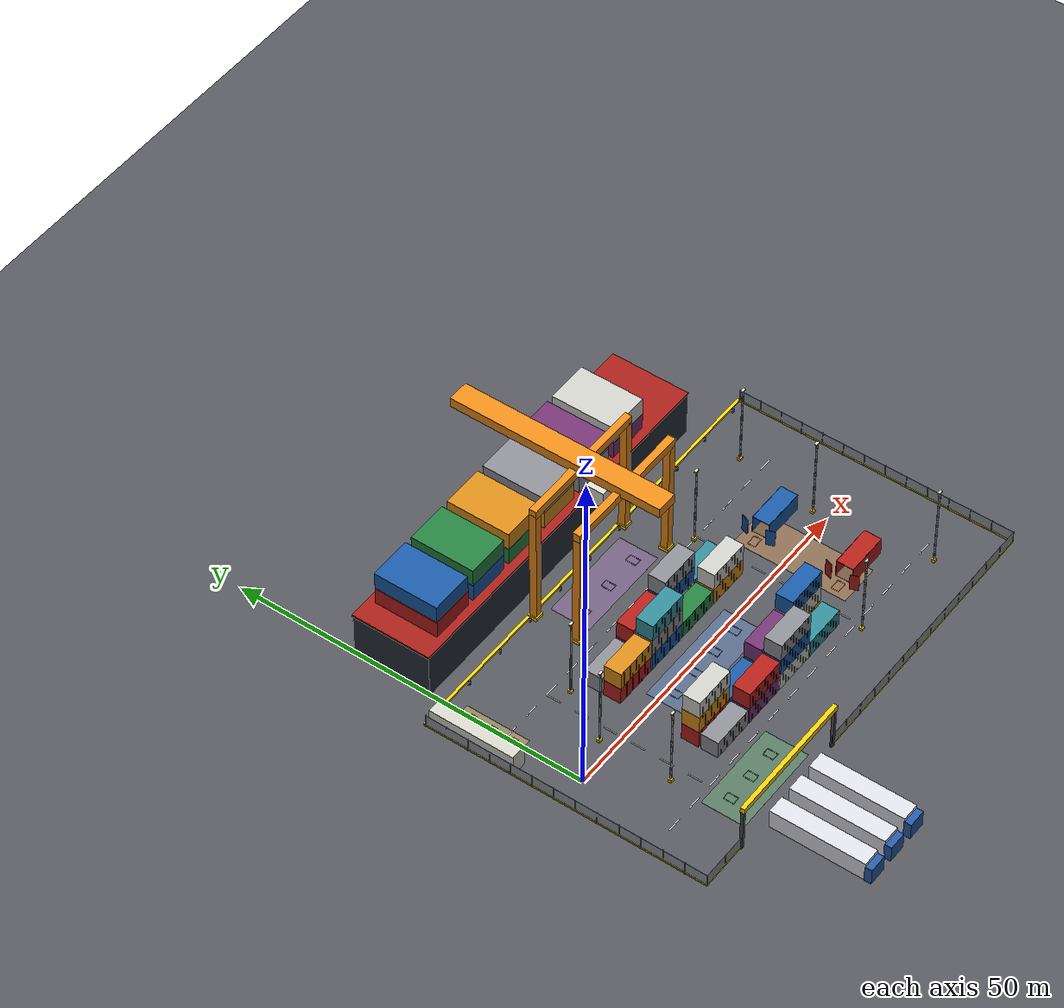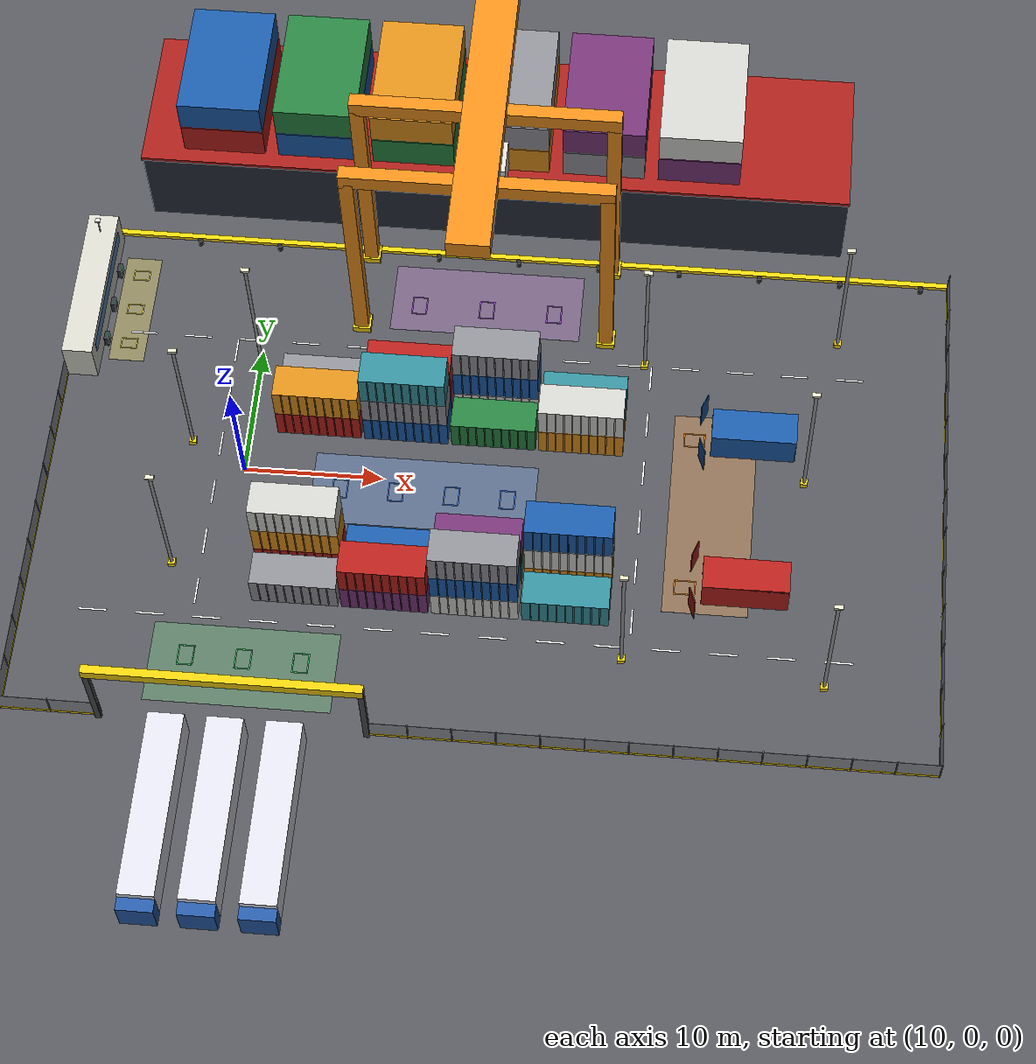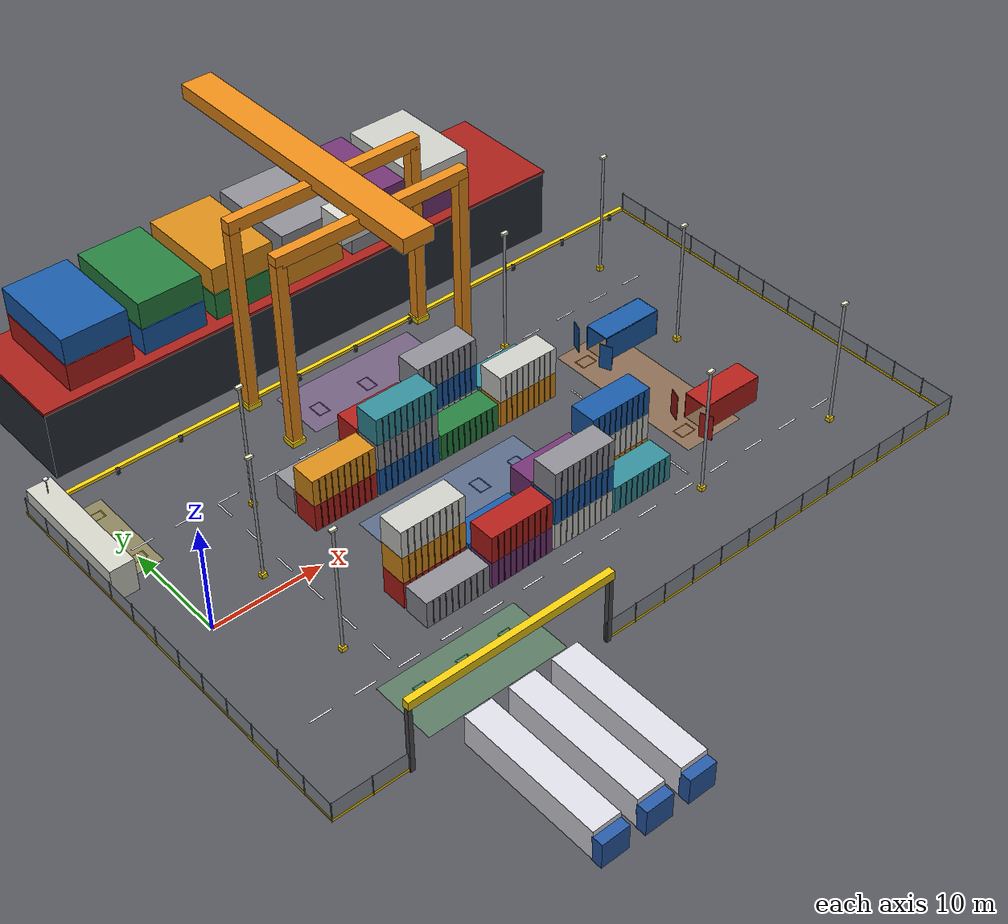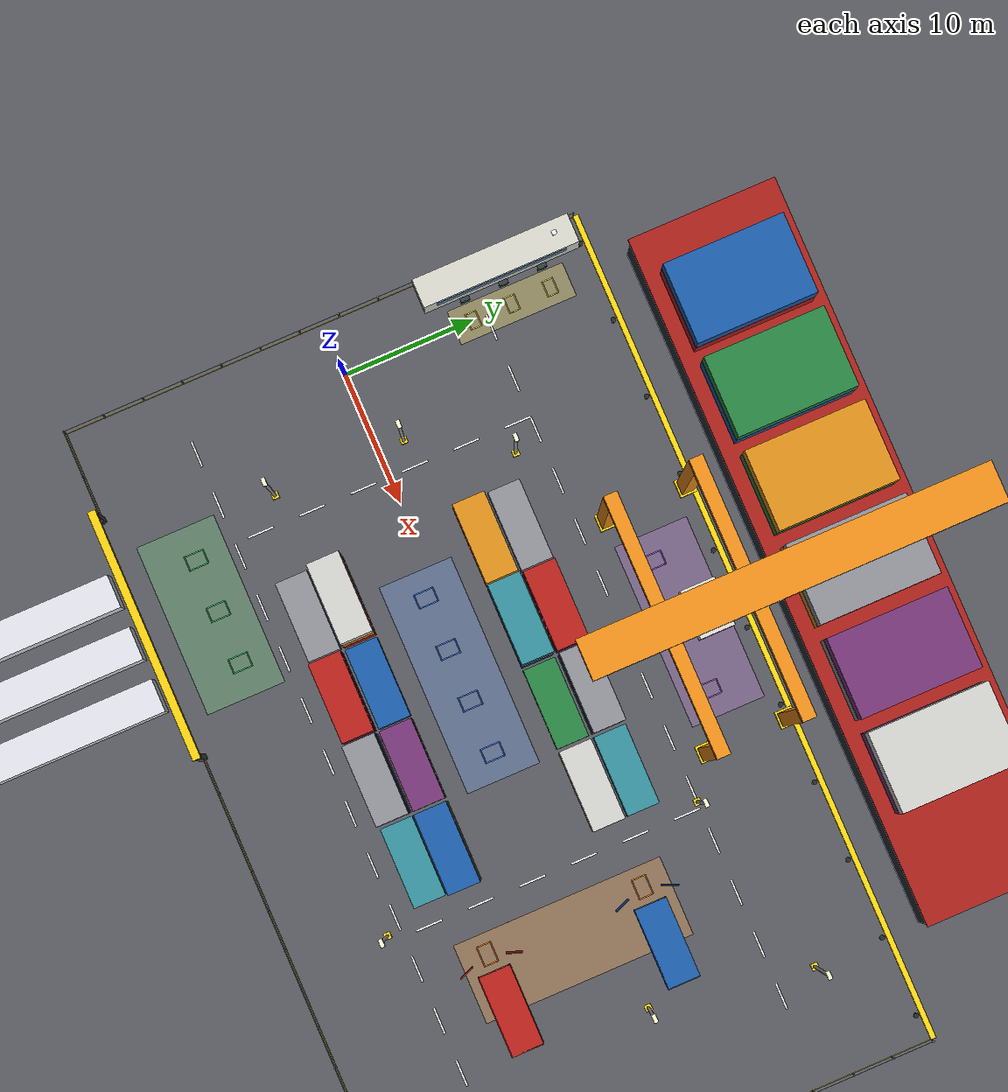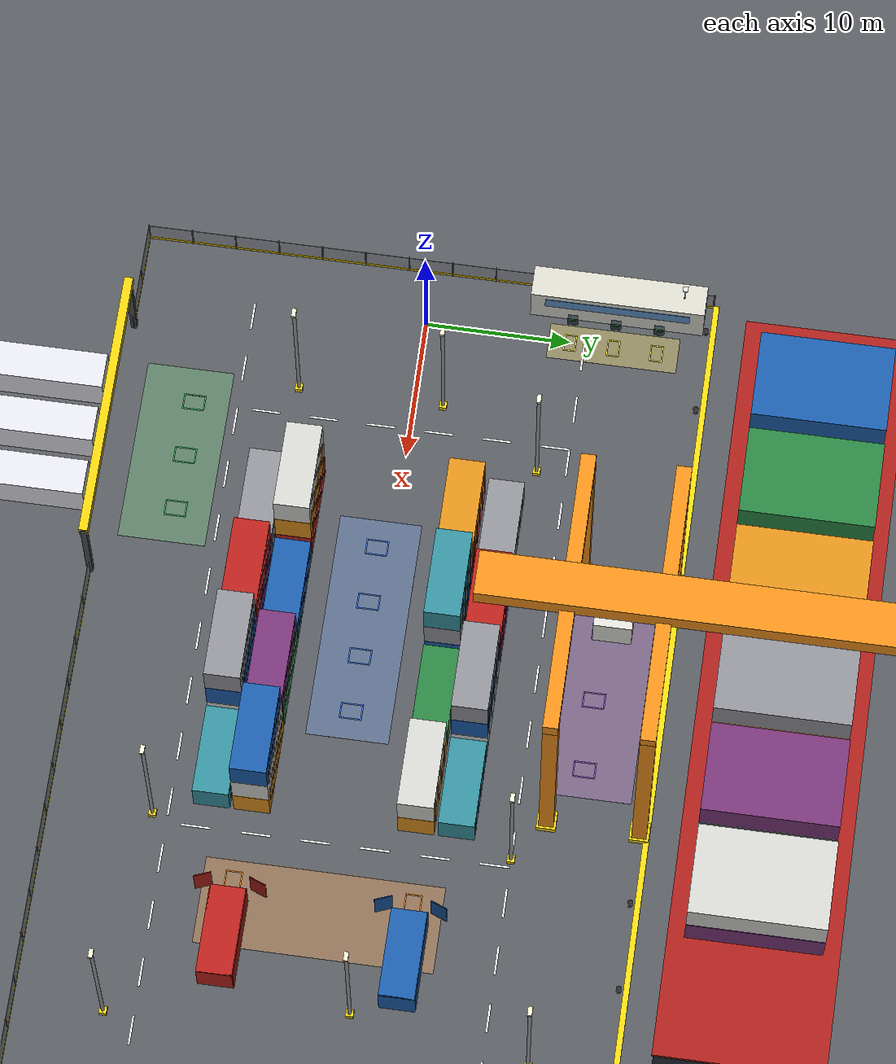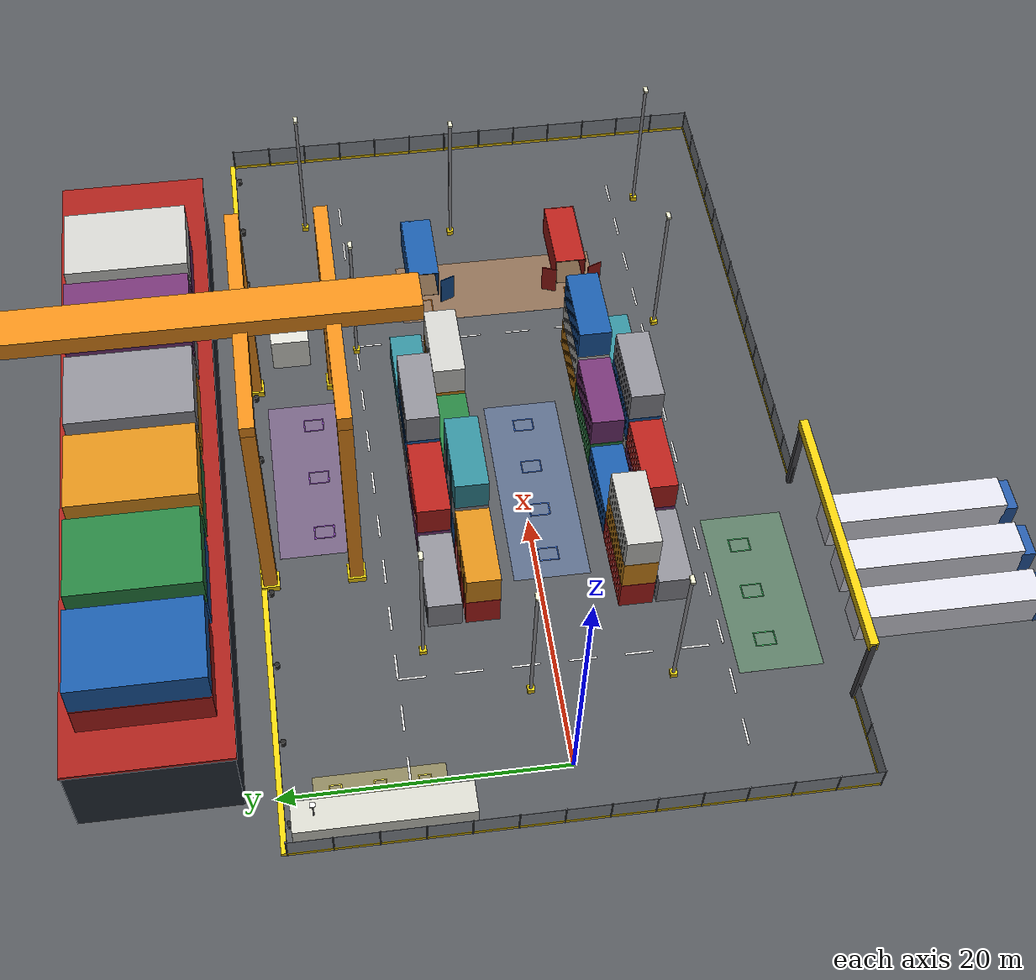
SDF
<sdf version="1.6">
 <world name="yektemak_port">
  <gravity>0 0 -9.81</gravity>
  <spherical_coordinates>
   <surface_model>EARTH_WGS84</surface_model>
   <world_frame_orientation>ENU</world_frame_orientation>
   <latitude_deg>40.965</latitude_deg>
   <longitude_deg>27.0</longitude_deg>
   <elevation>0</elevation>
   <heading_deg>0</heading_deg>
  </spherical_coordinates>
  <plugin name="gazebo_ros_state" filename="libgazebo_ros_state.so">
   <ros><namespace>/gazebo</namespace></ros>
   <update_rate>20.0</update_rate>
  </plugin>
  <physics name="default_physics" type="ode">
   <max_step_size>0.001</max_step_size>
   <real_time_factor>1.0</real_time_factor>
   <real_time_update_rate>1000</real_time_update_rate>
  </physics>
  <scene>
   <ambient>0.65 0.65 0.68 1</ambient>
   <background>0.62 0.75 0.90 1</background>
   <shadows>true</shadows>
   <sky><clouds><speed>4</speed></clouds></sky>
  </scene>
  <light type="directional" name="sun">
   <pose>0 0 40 0 0 0</pose>
   <diffuse>0.9 0.88 0.82 1</diffuse>
   <specular>0.2 0.2 0.2 1</specular>
   <direction>-0.45 0.3 -0.85</direction>
  </light>
  <model name="ground_plane">
   <static>true</static>
   <link name="link">
    <collision name="collision">
     <geometry><plane><normal>0 0 1</normal><size>200 200</size></plane></geometry>
     <surface><friction><ode><mu>1.0</mu><mu2>1.0</mu2></ode></friction></surface>
    </collision>
    <visual name="visual">
     <cast_shadows>false</cast_shadows>
     <geometry><plane><normal>0 0 1</normal><size>200 200</size></plane></geometry>
     <material>
      <ambient>0.28 0.29 0.31 1</ambient>
      <diffuse>0.33 0.34 0.36 1</diffuse>
      <specular>0.15 0.15 0.15 1</specular>
     </material>
    </visual>
   </link>
  </model>
  <model name="port_yard">
   <static>true</static>
   <link name="link">
    <collision name="b1_c">
     <pose>15 4.5 1.295 0 0 0</pose>
     <geometry><box><size>6.06 2.44 2.57</size></box></geometry>
    </collision>
    <visual name="b1_v">
     <pose>15 4.5 1.295 0 0 0</pose>
     <geometry><box><size>6.06 2.44 2.57</size></box></geometry>
     <material>
      <ambient>0.59 0.10 0.09 1</ambient>
      <diffuse>0.7 0.12 0.1 1</diffuse>
      <specular>0.15 0.15 0.15 1</specular>
     </material>
    </visual>
    <visual name="b2_v">
     <pose>12.6 5.725 1.295 0 0 0</pose>
     <cast_shadows>false</cast_shadows>
     <geometry><box><size>0.08 0.01 2.39</size></box></geometry>
     <material>
      <ambient>0.48 0.08 0.07 1</ambient>
      <diffuse>0.5599999999999999 0.096 0.08000000000000002 1</diffuse>
      <specular>0.15 0.15 0.15 1</specular>
     </material>
    </visual>
    <visual name="b3_v">
     <pose>12.6 3.275 1.295 0 0 0</pose>
     <cast_shadows>false</cast_shadows>
     <geometry><box><size>0.08 0.01 2.39</size></box></geometry>
     <material>
      <ambient>0.48 0.08 0.07 1</ambient>
      <diffuse>0.5599999999999999 0.096 0.08000000000000002 1</diffuse>
      <specular>0.15 0.15 0.15 1</specular>
     </material>
    </visual>
    <visual name="b4_v">
     <pose>13.2 5.725 1.295 0 0 0</pose>
     <cast_shadows>false</cast_shadows>
     <geometry><box><size>0.08 0.01 2.39</size></box></geometry>
     <material>
      <ambient>0.48 0.08 0.07 1</ambient>
      <diffuse>0.5599999999999999 0.096 0.08000000000000002 1</diffuse>
      <specular>0.15 0.15 0.15 1</specular>
     </material>
    </visual>
    <visual name="b5_v">
     <pose>13.2 3.275 1.295 0 0 0</pose>
     <cast_shadows>false</cast_shadows>
     <geometry><box><size>0.08 0.01 2.39</size></box></geometry>
     <material>
      <ambient>0.48 0.08 0.07 1</ambient>
      <diffuse>0.5599999999999999 0.096 0.08000000000000002 1</diffuse>
      <specular>0.15 0.15 0.15 1</specular>
     </material>
    </visual>
    <visual name="b6_v">
     <pose>13.8 5.725 1.295 0 0 0</pose>
     <cast_shadows>false</cast_shadows>
     <geometry><box><size>0.08 0.01 2.39</size></box></geometry>
     <material>
      <ambient>0.48 0.08 0.07 1</ambient>
      <diffuse>0.5599999999999999 0.096 0.08000000000000002 1</diffuse>
      <specular>0.15 0.15 0.15 1</specular>
     </material>
    </visual>
    <visual name="b7_v">
     <pose>13.8 3.275 1.295 0 0 0</pose>
     <cast_shadows>false</cast_shadows>
     <geometry><box><size>0.08 0.01 2.39</size></box></geometry>
     <material>
      <ambient>0.48 0.08 0.07 1</ambient>
      <diffuse>0.5599999999999999 0.096 0.08000000000000002 1</diffuse>
      <specular>0.15 0.15 0.15 1</specular>
     </material>
    </visual>
    <visual name="b8_v">
     <pose>14.4 5.725 1.295 0 0 0</pose>
     <cast_shadows>false</cast_shadows>
     <geometry><box><size>0.08 0.01 2.39</size></box></geometry>
     <material>
      <ambient>0.48 0.08 0.07 1</ambient>
      <diffuse>0.5599999999999999 0.096 0.08000000000000002 1</diffuse>
      <specular>0.15 0.15 0.15 1</specular>
     </material>
    </visual>
    <visual name="b9_v">
     <pose>14.4 3.275 1.295 0 0 0</pose>
     <cast_shadows>false</cast_shadows>
     <geometry><box><size>0.08 0.01 2.39</size></box></geometry>
     <material>
      <ambient>0.48 0.08 0.07 1</ambient>
      <diffuse>0.5599999999999999 0.096 0.08000000000000002 1</diffuse>
      <specular>0.15 0.15 0.15 1</specular>
     </material>
    </visual>
    <visual name="b10_v">
     <pose>15 5.725 1.295 0 0 0</pose>
     <cast_shadows>false</cast_shadows>
     <geometry><box><size>0.08 0.01 2.39</size></box></geometry>
     <material>
      <ambient>0.48 0.08 0.07 1</ambient>
      <diffuse>0.5599999999999999 0.096 0.08000000000000002 1</diffuse>
      <specular>0.15 0.15 0.15 1</specular>
     </material>
    </visual>
    <visual name="b11_v">
     <pose>15 3.275 1.295 0 0 0</pose>
     <cast_shadows>false</cast_shadows>
     <geometry><box><size>0.08 0.01 2.39</size></box></geometry>
     <material>
      <ambient>0.48 0.08 0.07 1</ambient>
      <diffuse>0.5599999999999999 0.096 0.08000000000000002 1</diffuse>
      <specular>0.15 0.15 0.15 1</specular>
     </material>
    </visual>
    <visual name="b12_v">
     <pose>15.6 5.725 1.295 0 0 0</pose>
     <cast_shadows>false</cast_shadows>
     <geometry><box><size>0.08 0.01 2.39</size></box></geometry>
     <material>
      <ambient>0.48 0.08 0.07 1</ambient>
      <diffuse>0.5599999999999999 0.096 0.08000000000000002 1</diffuse>
      <specular>0.15 0.15 0.15 1</specular>
     </material>
    </visual>
    <visual name="b13_v">
     <pose>15.6 3.275 1.295 0 0 0</pose>
     <cast_shadows>false</cast_shadows>
     <geometry><box><size>0.08 0.01 2.39</size></box></geometry>
     <material>
      <ambient>0.48 0.08 0.07 1</ambient>
      <diffuse>0.5599999999999999 0.096 0.08000000000000002 1</diffuse>
      <specular>0.15 0.15 0.15 1</specular>
     </material>
    </visual>
    <visual name="b14_v">
     <pose>16.2 5.725 1.295 0 0 0</pose>
     <cast_shadows>false</cast_shadows>
     <geometry><box><size>0.08 0.01 2.39</size></box></geometry>
     <material>
      <ambient>0.48 0.08 0.07 1</ambient>
      <diffuse>0.5599999999999999 0.096 0.08000000000000002 1</diffuse>
      <specular>0.15 0.15 0.15 1</specular>
     </material>
    </visual>
    <visual name="b15_v">
     <pose>16.2 3.275 1.295 0 0 0</pose>
     <cast_shadows>false</cast_shadows>
     <geometry><box><size>0.08 0.01 2.39</size></box></geometry>
     <material>
      <ambient>0.48 0.08 0.07 1</ambient>
      <diffuse>0.5599999999999999 0.096 0.08000000000000002 1</diffuse>
      <specular>0.15 0.15 0.15 1</specular>
     </material>
    </visual>
    <visual name="b16_v">
     <pose>16.8 5.725 1.295 0 0 0</pose>
     <cast_shadows>false</cast_shadows>
     <geometry><box><size>0.08 0.01 2.39</size></box></geometry>
     <material>
      <ambient>0.48 0.08 0.07 1</ambient>
      <diffuse>0.5599999999999999 0.096 0.08000000000000002 1</diffuse>
      <specular>0.15 0.15 0.15 1</specular>
     </material>
    </visual>
    <visual name="b17_v">
     <pose>16.8 3.275 1.295 0 0 0</pose>
     <cast_shadows>false</cast_shadows>
     <geometry><box><size>0.08 0.01 2.39</size></box></geometry>
     <material>
      <ambient>0.48 0.08 0.07 1</ambient>
      <diffuse>0.5599999999999999 0.096 0.08000000000000002 1</diffuse>
      <specular>0.15 0.15 0.15 1</specular>
     </material>
    </visual>
    <visual name="b18_v">
     <pose>17.4 5.725 1.295 0 0 0</pose>
     <cast_shadows>false</cast_shadows>
     <geometry><box><size>0.08 0.01 2.39</size></box></geometry>
     <material>
      <ambient>0.48 0.08 0.07 1</ambient>
      <diffuse>0.5599999999999999 0.096 0.08000000000000002 1</diffuse>
      <specular>0.15 0.15 0.15 1</specular>
     </material>
    </visual>
    <visual name="b19_v">
     <pose>17.4 3.275 1.295 0 0 0</pose>
     <cast_shadows>false</cast_shadows>
     <geometry><box><size>0.08 0.01 2.39</size></box></geometry>
     <material>
      <ambient>0.48 0.08 0.07 1</ambient>
      <diffuse>0.5599999999999999 0.096 0.08000000000000002 1</diffuse>
      <specular>0.15 0.15 0.15 1</specular>
     </material>
    </visual>
    <collision name="b20_c">
     <pose>15 4.5 3.885 0 0 0</pose>
     <geometry><box><size>6.06 2.44 2.57</size></box></geometry>
    </collision>
    <visual name="b20_v">
     <pose>15 4.5 3.885 0 0 0</pose>
     <geometry><box><size>6.06 2.44 2.57</size></box></geometry>
     <material>
      <ambient>0.72 0.47 0.09 1</ambient>
      <diffuse>0.85 0.55 0.1 1</diffuse>
      <specular>0.15 0.15 0.15 1</specular>
     </material>
    </visual>
    <visual name="b21_v">
     <pose>12.6 5.725 3.885 0 0 0</pose>
     <cast_shadows>false</cast_shadows>
     <geometry><box><size>0.08 0.01 2.39</size></box></geometry>
     <material>
      <ambient>0.58 0.37 0.07 1</ambient>
      <diffuse>0.68 0.44000000000000006 0.08000000000000002 1</diffuse>
      <specular>0.15 0.15 0.15 1</specular>
     </material>
    </visual>
    <visual name="b22_v">
     <pose>12.6 3.275 3.885 0 0 0</pose>
     <cast_shadows>false</cast_shadows>
     <geometry><box><size>0.08 0.01 2.39</size></box></geometry>
     <material>
      <ambient>0.58 0.37 0.07 1</ambient>
      <diffuse>0.68 0.44000000000000006 0.08000000000000002 1</diffuse>
      <specular>0.15 0.15 0.15 1</specular>
     </material>
    </visual>
    <visual name="b23_v">
     <pose>13.2 5.725 3.885 0 0 0</pose>
     <cast_shadows>false</cast_shadows>
     <geometry><box><size>0.08 0.01 2.39</size></box></geometry>
     <material>
      <ambient>0.58 0.37 0.07 1</ambient>
      <diffuse>0.68 0.44000000000000006 0.08000000000000002 1</diffuse>
      <specular>0.15 0.15 0.15 1</specular>
     </material>
    </visual>
    <visual name="b24_v">
     <pose>13.2 3.275 3.885 0 0 0</pose>
     <cast_shadows>false</cast_shadows>
     <geometry><box><size>0.08 0.01 2.39</size></box></geometry>
     <material>
      <ambient>0.58 0.37 0.07 1</ambient>
      <diffuse>0.68 0.44000000000000006 0.08000000000000002 1</diffuse>
      <specular>0.15 0.15 0.15 1</specular>
     </material>
    </visual>
    <visual name="b25_v">
     <pose>13.8 5.725 3.885 0 0 0</pose>
     <cast_shadows>false</cast_shadows>
     <geometry><box><size>0.08 0.01 2.39</size></box></geometry>
     <material>
      <ambient>0.58 0.37 0.07 1</ambient>
      <diffuse>0.68 0.44000000000000006 0.08000000000000002 1</diffuse>
      <specular>0.15 0.15 0.15 1</specular>
     </material>
    </visual>
    <visual name="b26_v">
     <pose>13.8 3.275 3.885 0 0 0</pose>
     <cast_shadows>false</cast_shadows>
     <geometry><box><size>0.08 0.01 2.39</size></box></geometry>
     <material>
      <ambient>0.58 0.37 0.07 1</ambient>
      <diffuse>0.68 0.44000000000000006 0.08000000000000002 1</diffuse>
      <specular>0.15 0.15 0.15 1</specular>
     </material>
    </visual>
    <visual name="b27_v">
     <pose>14.4 5.725 3.885 0 0 0</pose>
     <cast_shadows>false</cast_shadows>
     <geometry><box><size>0.08 0.01 2.39</size></box></geometry>
     <material>
      <ambient>0.58 0.37 0.07 1</ambient>
      <diffuse>0.68 0.44000000000000006 0.08000000000000002 1</diffuse>
      <specular>0.15 0.15 0.15 1</specular>
     </material>
    </visual>
    <visual name="b28_v">
     <pose>14.4 3.275 3.885 0 0 0</pose>
     <cast_shadows>false</cast_shadows>
     <geometry><box><size>0.08 0.01 2.39</size></box></geometry>
     <material>
      <ambient>0.58 0.37 0.07 1</ambient>
      <diffuse>0.68 0.44000000000000006 0.08000000000000002 1</diffuse>
      <specular>0.15 0.15 0.15 1</specular>
     </material>
    </visual>
    <visual name="b29_v">
     <pose>15 5.725 3.885 0 0 0</pose>
     <cast_shadows>false</cast_shadows>
     <geometry><box><size>0.08 0.01 2.39</size></box></geometry>
     <material>
      <ambient>0.58 0.37 0.07 1</ambient>
      <diffuse>0.68 0.44000000000000006 0.08000000000000002 1</diffuse>
      <specular>0.15 0.15 0.15 1</specular>
     </material>
    </visual>
    <visual name="b30_v">
     <pose>15 3.275 3.885 0 0 0</pose>
     <cast_shadows>false</cast_shadows>
     <geometry><box><size>0.08 0.01 2.39</size></box></geometry>
     <material>
      <ambient>0.58 0.37 0.07 1</ambient>
      <diffuse>0.68 0.44000000000000006 0.08000000000000002 1</diffuse>
      <specular>0.15 0.15 0.15 1</specular>
     </material>
    </visual>
    <visual name="b31_v">
     <pose>15.6 5.725 3.885 0 0 0</pose>
     <cast_shadows>false</cast_shadows>
     <geometry><box><size>0.08 0.01 2.39</size></box></geometry>
     <material>
      <ambient>0.58 0.37 0.07 1</ambient>
      <diffuse>0.68 0.44000000000000006 0.08000000000000002 1</diffuse>
      <specular>0.15 0.15 0.15 1</specular>
     </material>
    </visual>
    <visual name="b32_v">
     <pose>15.6 3.275 3.885 0 0 0</pose>
     <cast_shadows>false</cast_shadows>
     <geometry><box><size>0.08 0.01 2.39</size></box></geometry>
     <material>
      <ambient>0.58 0.37 0.07 1</ambient>
      <diffuse>0.68 0.44000000000000006 0.08000000000000002 1</diffuse>
      <specular>0.15 0.15 0.15 1</specular>
     </material>
    </visual>
    <visual name="b33_v">
     <pose>16.2 5.725 3.885 0 0 0</pose>
     <cast_shadows>false</cast_shadows>
     <geometry><box><size>0.08 0.01 2.39</size></box></geometry>
     <material>
      <ambient>0.58 0.37 0.07 1</ambient>
      <diffuse>0.68 0.44000000000000006 0.08000000000000002 1</diffuse>
      <specular>0.15 0.15 0.15 1</specular>
     </material>
    </visual>
    <visual name="b34_v">
     <pose>16.2 3.275 3.885 0 0 0</pose>
     <cast_shadows>false</cast_shadows>
     <geometry><box><size>0.08 0.01 2.39</size></box></geometry>
     <material>
      <ambient>0.58 0.37 0.07 1</ambient>
      <diffuse>0.68 0.44000000000000006 0.08000000000000002 1</diffuse>
      <specular>0.15 0.15 0.15 1</specular>
     </material>
    </visual>
    <visual name="b35_v">
     <pose>16.8 5.725 3.885 0 0 0</pose>
     <cast_shadows>false</cast_shadows>
     <geometry><box><size>0.08 0.01 2.39</size></box></geometry>
     <material>
      <ambient>0.58 0.37 0.07 1</ambient>
      <diffuse>0.68 0.44000000000000006 0.08000000000000002 1</diffuse>
      <specular>0.15 0.15 0.15 1</specular>
     </material>
    </visual>
    <visual name="b36_v">
     <pose>16.8 3.275 3.885 0 0 0</pose>
     <cast_shadows>false</cast_shadows>
     <geometry><box><size>0.08 0.01 2.39</size></box></geometry>
     <material>
      <ambient>0.58 0.37 0.07 1</ambient>
      <diffuse>0.68 0.44000000000000006 0.08000000000000002 1</diffuse>
      <specular>0.15 0.15 0.15 1</specular>
     </material>
    </visual>
    <visual name="b37_v">
     <pose>17.4 5.725 3.885 0 0 0</pose>
     <cast_shadows>false</cast_shadows>
     <geometry><box><size>0.08 0.01 2.39</size></box></geometry>
     <material>
      <ambient>0.58 0.37 0.07 1</ambient>
      <diffuse>0.68 0.44000000000000006 0.08000000000000002 1</diffuse>
      <specular>0.15 0.15 0.15 1</specular>
     </material>
    </visual>
    <visual name="b38_v">
     <pose>17.4 3.275 3.885 0 0 0</pose>
     <cast_shadows>false</cast_shadows>
     <geometry><box><size>0.08 0.01 2.39</size></box></geometry>
     <material>
      <ambient>0.58 0.37 0.07 1</ambient>
      <diffuse>0.68 0.44000000000000006 0.08000000000000002 1</diffuse>
      <specular>0.15 0.15 0.15 1</specular>
     </material>
    </visual>
    <collision name="b39_c">
     <pose>21.3 4.5 1.295 0 0 0</pose>
     <geometry><box><size>6.06 2.44 2.57</size></box></geometry>
    </collision>
    <visual name="b39_v">
     <pose>21.3 4.5 1.295 0 0 0</pose>
     <geometry><box><size>6.06 2.44 2.57</size></box></geometry>
     <material>
      <ambient>0.09 0.30 0.55 1</ambient>
      <diffuse>0.1 0.35 0.65 1</diffuse>
      <specular>0.15 0.15 0.15 1</specular>
     </material>
    </visual>
    <visual name="b40_v">
     <pose>18.9 5.725 1.295 0 0 0</pose>
     <cast_shadows>false</cast_shadows>
     <geometry><box><size>0.08 0.01 2.39</size></box></geometry>
     <material>
      <ambient>0.07 0.24 0.44 1</ambient>
      <diffuse>0.08000000000000002 0.27999999999999997 0.52 1</diffuse>
      <specular>0.15 0.15 0.15 1</specular>
     </material>
    </visual>
    <visual name="b41_v">
     <pose>18.9 3.275 1.295 0 0 0</pose>
     <cast_shadows>false</cast_shadows>
     <geometry><box><size>0.08 0.01 2.39</size></box></geometry>
     <material>
      <ambient>0.07 0.24 0.44 1</ambient>
      <diffuse>0.08000000000000002 0.27999999999999997 0.52 1</diffuse>
      <specular>0.15 0.15 0.15 1</specular>
     </material>
    </visual>
    <visual name="b42_v">
     <pose>19.5 5.725 1.295 0 0 0</pose>
     <cast_shadows>false</cast_shadows>
     <geometry><box><size>0.08 0.01 2.39</size></box></geometry>
     <material>
      <ambient>0.07 0.24 0.44 1</ambient>
      <diffuse>0.08000000000000002 0.27999999999999997 0.52 1</diffuse>
      <specular>0.15 0.15 0.15 1</specular>
     </material>
    </visual>
    <visual name="b43_v">
     <pose>19.5 3.275 1.295 0 0 0</pose>
     <cast_shadows>false</cast_shadows>
     <geometry><box><size>0.08 0.01 2.39</size></box></geometry>
     <material>
      <ambient>0.07 0.24 0.44 1</ambient>
      <diffuse>0.08000000000000002 0.27999999999999997 0.52 1</diffuse>
      <specular>0.15 0.15 0.15 1</specular>
     </material>
    </visual>
    <visual name="b44_v">
     <pose>20.1 5.725 1.295 0 0 0</pose>
     <cast_shadows>false</cast_shadows>
     <geometry><box><size>0.08 0.01 2.39</size></box></geometry>
     <material>
      <ambient>0.07 0.24 0.44 1</ambient>
      <diffuse>0.08000000000000002 0.27999999999999997 0.52 1</diffuse>
      <specular>0.15 0.15 0.15 1</specular>
     </material>
    </visual>
    <visual name="b45_v">
     <pose>20.1 3.275 1.295 0 0 0</pose>
     <cast_shadows>false</cast_shadows>
     <geometry><box><size>0.08 0.01 2.39</size></box></geometry>
     <material>
      <ambient>0.07 0.24 0.44 1</ambient>
      <diffuse>0.08000000000000002 0.27999999999999997 0.52 1</diffuse>
      <specular>0.15 0.15 0.15 1</specular>
     </material>
    </visual>
    <visual name="b46_v">
     <pose>20.7 5.725 1.295 0 0 0</pose>
     <cast_shadows>false</cast_shadows>
     <geometry><box><size>0.08 0.01 2.39</size></box></geometry>
     <material>
      <ambient>0.07 0.24 0.44 1</ambient>
      <diffuse>0.08000000000000002 0.27999999999999997 0.52 1</diffuse>
      <specular>0.15 0.15 0.15 1</specular>
     </material>
    </visual>
    <visual name="b47_v">
     <pose>20.7 3.275 1.295 0 0 0</pose>
     <cast_shadows>false</cast_shadows>
     <geometry><box><size>0.08 0.01 2.39</size></box></geometry>
     <material>
      <ambient>0.07 0.24 0.44 1</ambient>
      <diffuse>0.08000000000000002 0.27999999999999997 0.52 1</diffuse>
      <specular>0.15 0.15 0.15 1</specular>
     </material>
    </visual>
    <visual name="b48_v">
     <pose>21.3 5.725 1.295 0 0 0</pose>
     <cast_shadows>false</cast_shadows>
     <geometry><box><size>0.08 0.01 2.39</size></box></geometry>
     <material>
      <ambient>0.07 0.24 0.44 1</ambient>
      <diffuse>0.08000000000000002 0.27999999999999997 0.52 1</diffuse>
      <specular>0.15 0.15 0.15 1</specular>
     </material>
    </visual>
    <visual name="b49_v">
     <pose>21.3 3.275 1.295 0 0 0</pose>
     <cast_shadows>false</cast_shadows>
     <geometry><box><size>0.08 0.01 2.39</size></box></geometry>
     <material>
      <ambient>0.07 0.24 0.44 1</ambient>
      <diffuse>0.08000000000000002 0.27999999999999997 0.52 1</diffuse>
      <specular>0.15 0.15 0.15 1</specular>
     </material>
    </visual>
    <visual name="b50_v">
     <pose>21.9 5.725 1.295 0 0 0</pose>
     <cast_shadows>false</cast_shadows>
     <geometry><box><size>0.08 0.01 2.39</size></box></geometry>
     <material>
      <ambient>0.07 0.24 0.44 1</ambient>
      <diffuse>0.08000000000000002 0.27999999999999997 0.52 1</diffuse>
      <specular>0.15 0.15 0.15 1</specular>
     </material>
    </visual>
    <visual name="b51_v">
     <pose>21.9 3.275 1.295 0 0 0</pose>
     <cast_shadows>false</cast_shadows>
     <geometry><box><size>0.08 0.01 2.39</size></box></geometry>
     <material>
      <ambient>0.07 0.24 0.44 1</ambient>
      <diffuse>0.08000000000000002 0.27999999999999997 0.52 1</diffuse>
      <specular>0.15 0.15 0.15 1</specular>
     </material>
    </visual>
    <visual name="b52_v">
     <pose>22.5 5.725 1.295 0 0 0</pose>
     <cast_shadows>false</cast_shadows>
     <geometry><box><size>0.08 0.01 2.39</size></box></geometry>
     <material>
      <ambient>0.07 0.24 0.44 1</ambient>
      <diffuse>0.08000000000000002 0.27999999999999997 0.52 1</diffuse>
      <specular>0.15 0.15 0.15 1</specular>
     </material>
    </visual>
    <visual name="b53_v">
     <pose>22.5 3.275 1.295 0 0 0</pose>
     <cast_shadows>false</cast_shadows>
     <geometry><box><size>0.08 0.01 2.39</size></box></geometry>
     <material>
      <ambient>0.07 0.24 0.44 1</ambient>
      <diffuse>0.08000000000000002 0.27999999999999997 0.52 1</diffuse>
      <specular>0.15 0.15 0.15 1</specular>
     </material>
    </visual>
    <visual name="b54_v">
     <pose>23.1 5.725 1.295 0 0 0</pose>
     <cast_shadows>false</cast_shadows>
     <geometry><box><size>0.08 0.01 2.39</size></box></geometry>
     <material>
      <ambient>0.07 0.24 0.44 1</ambient>
      <diffuse>0.08000000000000002 0.27999999999999997 0.52 1</diffuse>
      <specular>0.15 0.15 0.15 1</specular>
     </material>
    </visual>
    <visual name="b55_v">
     <pose>23.1 3.275 1.295 0 0 0</pose>
     <cast_shadows>false</cast_shadows>
     <geometry><box><size>0.08 0.01 2.39</size></box></geometry>
     <material>
      <ambient>0.07 0.24 0.44 1</ambient>
      <diffuse>0.08000000000000002 0.27999999999999997 0.52 1</diffuse>
      <specular>0.15 0.15 0.15 1</specular>
     </material>
    </visual>
    <visual name="b56_v">
     <pose>23.7 5.725 1.295 0 0 0</pose>
     <cast_shadows>false</cast_shadows>
     <geometry><box><size>0.08 0.01 2.39</size></box></geometry>
     <material>
      <ambient>0.07 0.24 0.44 1</ambient>
      <diffuse>0.08000000000000002 0.27999999999999997 0.52 1</diffuse>
      <specular>0.15 0.15 0.15 1</specular>
     </material>
    </visual>
    <visual name="b57_v">
     <pose>23.7 3.275 1.295 0 0 0</pose>
     <cast_shadows>false</cast_shadows>
     <geometry><box><size>0.08 0.01 2.39</size></box></geometry>
     <material>
      <ambient>0.07 0.24 0.44 1</ambient>
      <diffuse>0.08000000000000002 0.27999999999999997 0.52 1</diffuse>
      <specular>0.15 0.15 0.15 1</specular>
     </material>
    </visual>
    <collision name="b58_c">
     <pose>21.3 4.5 3.885 0 0 0</pose>
     <geometry><box><size>6.06 2.44 2.57</size></box></geometry>
    </collision>
    <visual name="b58_v">
     <pose>21.3 4.5 3.885 0 0 0</pose>
     <geometry><box><size>6.06 2.44 2.57</size></box></geometry>
     <material>
      <ambient>0.47 0.47 0.49 1</ambient>
      <diffuse>0.55 0.55 0.58 1</diffuse>
      <specular>0.15 0.15 0.15 1</specular>
     </material>
    </visual>
    <visual name="b59_v">
     <pose>18.9 5.725 3.885 0 0 0</pose>
     <cast_shadows>false</cast_shadows>
     <geometry><box><size>0.08 0.01 2.39</size></box></geometry>
     <material>
      <ambient>0.37 0.37 0.39 1</ambient>
      <diffuse>0.44000000000000006 0.44000000000000006 0.46399999999999997 1</diffuse>
      <specular>0.15 0.15 0.15 1</specular>
     </material>
    </visual>
    <visual name="b60_v">
     <pose>18.9 3.275 3.885 0 0 0</pose>
     <cast_shadows>false</cast_shadows>
     <geometry><box><size>0.08 0.01 2.39</size></box></geometry>
     <material>
      <ambient>0.37 0.37 0.39 1</ambient>
      <diffuse>0.44000000000000006 0.44000000000000006 0.46399999999999997 1</diffuse>
      <specular>0.15 0.15 0.15 1</specular>
     </material>
    </visual>
    <visual name="b61_v">
     <pose>19.5 5.725 3.885 0 0 0</pose>
     <cast_shadows>false</cast_shadows>
     <geometry><box><size>0.08 0.01 2.39</size></box></geometry>
     <material>
      <ambient>0.37 0.37 0.39 1</ambient>
      <diffuse>0.44000000000000006 0.44000000000000006 0.46399999999999997 1</diffuse>
      <specular>0.15 0.15 0.15 1</specular>
     </material>
    </visual>
    <visual name="b62_v">
     <pose>19.5 3.275 3.885 0 0 0</pose>
     <cast_shadows>false</cast_shadows>
     <geometry><box><size>0.08 0.01 2.39</size></box></geometry>
     <material>
      <ambient>0.37 0.37 0.39 1</ambient>
      <diffuse>0.44000000000000006 0.44000000000000006 0.46399999999999997 1</diffuse>
      <specular>0.15 0.15 0.15 1</specular>
     </material>
    </visual>
    <visual name="b63_v">
     <pose>20.1 5.725 3.885 0 0 0</pose>
     <cast_shadows>false</cast_shadows>
     <geometry><box><size>0.08 0.01 2.39</size></box></geometry>
     <material>
      <ambient>0.37 0.37 0.39 1</ambient>
      <diffuse>0.44000000000000006 0.44000000000000006 0.46399999999999997 1</diffuse>
      <specular>0.15 0.15 0.15 1</specular>
     </material>
    </visual>
    <visual name="b64_v">
     <pose>20.1 3.275 3.885 0 0 0</pose>
     <cast_shadows>false</cast_shadows>
     <geometry><box><size>0.08 0.01 2.39</size></box></geometry>
     <material>
      <ambient>0.37 0.37 0.39 1</ambient>
      <diffuse>0.44000000000000006 0.44000000000000006 0.46399999999999997 1</diffuse>
      <specular>0.15 0.15 0.15 1</specular>
     </material>
    </visual>
    <visual name="b65_v">
     <pose>20.7 5.725 3.885 0 0 0</pose>
     <cast_shadows>false</cast_shadows>
     <geometry><box><size>0.08 0.01 2.39</size></box></geometry>
     <material>
      <ambient>0.37 0.37 0.39 1</ambient>
      <diffuse>0.44000000000000006 0.44000000000000006 0.46399999999999997 1</diffuse>
      <specular>0.15 0.15 0.15 1</specular>
     </material>
    </visual>
    <visual name="b66_v">
     <pose>20.7 3.275 3.885 0 0 0</pose>
     <cast_shadows>false</cast_shadows>
     <geometry><box><size>0.08 0.01 2.39</size></box></geometry>
     <material>
      <ambient>0.37 0.37 0.39 1</ambient>
      <diffuse>0.44000000000000006 0.44000000000000006 0.46399999999999997 1</diffuse>
      <specular>0.15 0.15 0.15 1</specular>
     </material>
    </visual>
    <visual name="b67_v">
     <pose>21.3 5.725 3.885 0 0 0</pose>
     <cast_shadows>false</cast_shadows>
     <geometry><box><size>0.08 0.01 2.39</size></box></geometry>
     <material>
      <ambient>0.37 0.37 0.39 1</ambient>
      <diffuse>0.44000000000000006 0.44000000000000006 0.46399999999999997 1</diffuse>
      <specular>0.15 0.15 0.15 1</specular>
     </material>
    </visual>
    <visual name="b68_v">
     <pose>21.3 3.275 3.885 0 0 0</pose>
     <cast_shadows>false</cast_shadows>
     <geometry><box><size>0.08 0.01 2.39</size></box></geometry>
     <material>
      <ambient>0.37 0.37 0.39 1</ambient>
      <diffuse>0.44000000000000006 0.44000000000000006 0.46399999999999997 1</diffuse>
      <specular>0.15 0.15 0.15 1</specular>
     </material>
    </visual>
    <visual name="b69_v">
     <pose>21.9 5.725 3.885 0 0 0</pose>
     <cast_shadows>false</cast_shadows>
     <geometry><box><size>0.08 0.01 2.39</size></box></geometry>
     <material>
      <ambient>0.37 0.37 0.39 1</ambient>
      <diffuse>0.44000000000000006 0.44000000000000006 0.46399999999999997 1</diffuse>
      <specular>0.15 0.15 0.15 1</specular>
     </material>
    </visual>
    <visual name="b70_v">
     <pose>21.9 3.275 3.885 0 0 0</pose>
     <cast_shadows>false</cast_shadows>
     <geometry><box><size>0.08 0.01 2.39</size></box></geometry>
     <material>
      <ambient>0.37 0.37 0.39 1</ambient>
      <diffuse>0.44000000000000006 0.44000000000000006 0.46399999999999997 1</diffuse>
      <specular>0.15 0.15 0.15 1</specular>
     </material>
    </visual>
    <visual name="b71_v">
     <pose>22.5 5.725 3.885 0 0 0</pose>
     <cast_shadows>false</cast_shadows>
     <geometry><box><size>0.08 0.01 2.39</size></box></geometry>
     <material>
      <ambient>0.37 0.37 0.39 1</ambient>
      <diffuse>0.44000000000000006 0.44000000000000006 0.46399999999999997 1</diffuse>
      <specular>0.15 0.15 0.15 1</specular>
     </material>
    </visual>
    <visual name="b72_v">
     <pose>22.5 3.275 3.885 0 0 0</pose>
     <cast_shadows>false</cast_shadows>
     <geometry><box><size>0.08 0.01 2.39</size></box></geometry>
     <material>
      <ambient>0.37 0.37 0.39 1</ambient>
      <diffuse>0.44000000000000006 0.44000000000000006 0.46399999999999997 1</diffuse>
      <specular>0.15 0.15 0.15 1</specular>
     </material>
    </visual>
    <visual name="b73_v">
     <pose>23.1 5.725 3.885 0 0 0</pose>
     <cast_shadows>false</cast_shadows>
     <geometry><box><size>0.08 0.01 2.39</size></box></geometry>
     <material>
      <ambient>0.37 0.37 0.39 1</ambient>
      <diffuse>0.44000000000000006 0.44000000000000006 0.46399999999999997 1</diffuse>
      <specular>0.15 0.15 0.15 1</specular>
     </material>
    </visual>
    <visual name="b74_v">
     <pose>23.1 3.275 3.885 0 0 0</pose>
     <cast_shadows>false</cast_shadows>
     <geometry><box><size>0.08 0.01 2.39</size></box></geometry>
     <material>
      <ambient>0.37 0.37 0.39 1</ambient>
      <diffuse>0.44000000000000006 0.44000000000000006 0.46399999999999997 1</diffuse>
      <specular>0.15 0.15 0.15 1</specular>
     </material>
    </visual>
    <visual name="b75_v">
     <pose>23.7 5.725 3.885 0 0 0</pose>
     <cast_shadows>false</cast_shadows>
     <geometry><box><size>0.08 0.01 2.39</size></box></geometry>
     <material>
      <ambient>0.37 0.37 0.39 1</ambient>
      <diffuse>0.44000000000000006 0.44000000000000006 0.46399999999999997 1</diffuse>
      <specular>0.15 0.15 0.15 1</specular>
     </material>
    </visual>
    <visual name="b76_v">
     <pose>23.7 3.275 3.885 0 0 0</pose>
     <cast_shadows>false</cast_shadows>
     <geometry><box><size>0.08 0.01 2.39</size></box></geometry>
     <material>
      <ambient>0.37 0.37 0.39 1</ambient>
      <diffuse>0.44000000000000006 0.44000000000000006 0.46399999999999997 1</diffuse>
      <specular>0.15 0.15 0.15 1</specular>
     </material>
    </visual>
    <collision name="b77_c">
     <pose>21.3 4.5 6.475 0 0 0</pose>
     <geometry><box><size>6.06 2.44 2.57</size></box></geometry>
    </collision>
    <visual name="b77_v">
     <pose>21.3 4.5 6.475 0 0 0</pose>
     <geometry><box><size>6.06 2.44 2.57</size></box></geometry>
     <material>
      <ambient>0.17 0.47 0.51 1</ambient>
      <diffuse>0.2 0.55 0.6 1</diffuse>
      <specular>0.15 0.15 0.15 1</specular>
     </material>
    </visual>
    <visual name="b78_v">
     <pose>18.9 5.725 6.475 0 0 0</pose>
     <cast_shadows>false</cast_shadows>
     <geometry><box><size>0.08 0.01 2.39</size></box></geometry>
     <material>
      <ambient>0.14 0.37 0.41 1</ambient>
      <diffuse>0.16000000000000003 0.44000000000000006 0.48 1</diffuse>
      <specular>0.15 0.15 0.15 1</specular>
     </material>
    </visual>
    <visual name="b79_v">
     <pose>18.9 3.275 6.475 0 0 0</pose>
     <cast_shadows>false</cast_shadows>
     <geometry><box><size>0.08 0.01 2.39</size></box></geometry>
     <material>
      <ambient>0.14 0.37 0.41 1</ambient>
      <diffuse>0.16000000000000003 0.44000000000000006 0.48 1</diffuse>
      <specular>0.15 0.15 0.15 1</specular>
     </material>
    </visual>
    <visual name="b80_v">
     <pose>19.5 5.725 6.475 0 0 0</pose>
     <cast_shadows>false</cast_shadows>
     <geometry><box><size>0.08 0.01 2.39</size></box></geometry>
     <material>
      <ambient>0.14 0.37 0.41 1</ambient>
      <diffuse>0.16000000000000003 0.44000000000000006 0.48 1</diffuse>
      <specular>0.15 0.15 0.15 1</specular>
     </material>
    </visual>
    <visual name="b81_v">
     <pose>19.5 3.275 6.475 0 0 0</pose>
     <cast_shadows>false</cast_shadows>
     <geometry><box><size>0.08 0.01 2.39</size></box></geometry>
     <material>
      <ambient>0.14 0.37 0.41 1</ambient>
      <diffuse>0.16000000000000003 0.44000000000000006 0.48 1</diffuse>
      <specular>0.15 0.15 0.15 1</specular>
     </material>
    </visual>
    <visual name="b82_v">
     <pose>20.1 5.725 6.475 0 0 0</pose>
     <cast_shadows>false</cast_shadows>
     <geometry><box><size>0.08 0.01 2.39</size></box></geometry>
     <material>
      <ambient>0.14 0.37 0.41 1</ambient>
      <diffuse>0.16000000000000003 0.44000000000000006 0.48 1</diffuse>
      <specular>0.15 0.15 0.15 1</specular>
     </material>
    </visual>
    <visual name="b83_v">
     <pose>20.1 3.275 6.475 0 0 0</pose>
     <cast_shadows>false</cast_shadows>
     <geometry><box><size>0.08 0.01 2.39</size></box></geometry>
     <material>
      <ambient>0.14 0.37 0.41 1</ambient>
      <diffuse>0.16000000000000003 0.44000000000000006 0.48 1</diffuse>
      <specular>0.15 0.15 0.15 1</specular>
     </material>
    </visual>
    <visual name="b84_v">
     <pose>20.7 5.725 6.475 0 0 0</pose>
     <cast_shadows>false</cast_shadows>
     <geometry><box><size>0.08 0.01 2.39</size></box></geometry>
     <material>
      <ambient>0.14 0.37 0.41 1</ambient>
      <diffuse>0.16000000000000003 0.44000000000000006 0.48 1</diffuse>
      <specular>0.15 0.15 0.15 1</specular>
     </material>
    </visual>
    <visual name="b85_v">
     <pose>20.7 3.275 6.475 0 0 0</pose>
     <cast_shadows>false</cast_shadows>
     <geometry><box><size>0.08 0.01 2.39</size></box></geometry>
     <material>
      <ambient>0.14 0.37 0.41 1</ambient>
      <diffuse>0.16000000000000003 0.44000000000000006 0.48 1</diffuse>
      <specular>0.15 0.15 0.15 1</specular>
     </material>
    </visual>
    <visual name="b86_v">
     <pose>21.3 5.725 6.475 0 0 0</pose>
     <cast_shadows>false</cast_shadows>
     <geometry><box><size>0.08 0.01 2.39</size></box></geometry>
     <material>
      <ambient>0.14 0.37 0.41 1</ambient>
      <diffuse>0.16000000000000003 0.44000000000000006 0.48 1</diffuse>
      <specular>0.15 0.15 0.15 1</specular>
     </material>
    </visual>
    <visual name="b87_v">
     <pose>21.3 3.275 6.475 0 0 0</pose>
     <cast_shadows>false</cast_shadows>
     <geometry><box><size>0.08 0.01 2.39</size></box></geometry>
     <material>
      <ambient>0.14 0.37 0.41 1</ambient>
      <diffuse>0.16000000000000003 0.44000000000000006 0.48 1</diffuse>
      <specular>0.15 0.15 0.15 1</specular>
     </material>
    </visual>
    <visual name="b88_v">
     <pose>21.9 5.725 6.475 0 0 0</pose>
     <cast_shadows>false</cast_shadows>
     <geometry><box><size>0.08 0.01 2.39</size></box></geometry>
     <material>
      <ambient>0.14 0.37 0.41 1</ambient>
      <diffuse>0.16000000000000003 0.44000000000000006 0.48 1</diffuse>
      <specular>0.15 0.15 0.15 1</specular>
     </material>
    </visual>
    <visual name="b89_v">
     <pose>21.9 3.275 6.475 0 0 0</pose>
     <cast_shadows>false</cast_shadows>
     <geometry><box><size>0.08 0.01 2.39</size></box></geometry>
     <material>
      <ambient>0.14 0.37 0.41 1</ambient>
      <diffuse>0.16000000000000003 0.44000000000000006 0.48 1</diffuse>
      <specular>0.15 0.15 0.15 1</specular>
     </material>
    </visual>
    <visual name="b90_v">
     <pose>22.5 5.725 6.475 0 0 0</pose>
     <cast_shadows>false</cast_shadows>
     <geometry><box><size>0.08 0.01 2.39</size></box></geometry>
     <material>
      <ambient>0.14 0.37 0.41 1</ambient>
      <diffuse>0.16000000000000003 0.44000000000000006 0.48 1</diffuse>
      <specular>0.15 0.15 0.15 1</specular>
     </material>
    </visual>
    <visual name="b91_v">
     <pose>22.5 3.275 6.475 0 0 0</pose>
     <cast_shadows>false</cast_shadows>
     <geometry><box><size>0.08 0.01 2.39</size></box></geometry>
     <material>
      <ambient>0.14 0.37 0.41 1</ambient>
      <diffuse>0.16000000000000003 0.44000000000000006 0.48 1</diffuse>
      <specular>0.15 0.15 0.15 1</specular>
     </material>
    </visual>
    <visual name="b92_v">
     <pose>23.1 5.725 6.475 0 0 0</pose>
     <cast_shadows>false</cast_shadows>
     <geometry><box><size>0.08 0.01 2.39</size></box></geometry>
     <material>
      <ambient>0.14 0.37 0.41 1</ambient>
      <diffuse>0.16000000000000003 0.44000000000000006 0.48 1</diffuse>
      <specular>0.15 0.15 0.15 1</specular>
     </material>
    </visual>
    <visual name="b93_v">
     <pose>23.1 3.275 6.475 0 0 0</pose>
     <cast_shadows>false</cast_shadows>
     <geometry><box><size>0.08 0.01 2.39</size></box></geometry>
     <material>
      <ambient>0.14 0.37 0.41 1</ambient>
      <diffuse>0.16000000000000003 0.44000000000000006 0.48 1</diffuse>
      <specular>0.15 0.15 0.15 1</specular>
     </material>
    </visual>
    <visual name="b94_v">
     <pose>23.7 5.725 6.475 0 0 0</pose>
     <cast_shadows>false</cast_shadows>
     <geometry><box><size>0.08 0.01 2.39</size></box></geometry>
     <material>
      <ambient>0.14 0.37 0.41 1</ambient>
      <diffuse>0.16000000000000003 0.44000000000000006 0.48 1</diffuse>
      <specular>0.15 0.15 0.15 1</specular>
     </material>
    </visual>
    <visual name="b95_v">
     <pose>23.7 3.275 6.475 0 0 0</pose>
     <cast_shadows>false</cast_shadows>
     <geometry><box><size>0.08 0.01 2.39</size></box></geometry>
     <material>
      <ambient>0.14 0.37 0.41 1</ambient>
      <diffuse>0.16000000000000003 0.44000000000000006 0.48 1</diffuse>
      <specular>0.15 0.15 0.15 1</specular>
     </material>
    </visual>
    <collision name="b96_c">
     <pose>27.6 4.5 1.295 0 0 0</pose>
     <geometry><box><size>6.06 2.44 2.57</size></box></geometry>
    </collision>
    <visual name="b96_v">
     <pose>27.6 4.5 1.295 0 0 0</pose>
     <geometry><box><size>6.06 2.44 2.57</size></box></geometry>
     <material>
      <ambient>0.13 0.42 0.21 1</ambient>
      <diffuse>0.15 0.5 0.25 1</diffuse>
      <specular>0.15 0.15 0.15 1</specular>
     </material>
    </visual>
    <visual name="b97_v">
     <pose>25.2 5.725 1.295 0 0 0</pose>
     <cast_shadows>false</cast_shadows>
     <geometry><box><size>0.08 0.01 2.39</size></box></geometry>
     <material>
      <ambient>0.10 0.34 0.17 1</ambient>
      <diffuse>0.12 0.4 0.2 1</diffuse>
      <specular>0.15 0.15 0.15 1</specular>
     </material>
    </visual>
    <visual name="b98_v">
     <pose>25.2 3.275 1.295 0 0 0</pose>
     <cast_shadows>false</cast_shadows>
     <geometry><box><size>0.08 0.01 2.39</size></box></geometry>
     <material>
      <ambient>0.10 0.34 0.17 1</ambient>
      <diffuse>0.12 0.4 0.2 1</diffuse>
      <specular>0.15 0.15 0.15 1</specular>
     </material>
    </visual>
    <visual name="b99_v">
     <pose>25.8 5.725 1.295 0 0 0</pose>
     <cast_shadows>false</cast_shadows>
     <geometry><box><size>0.08 0.01 2.39</size></box></geometry>
     <material>
      <ambient>0.10 0.34 0.17 1</ambient>
      <diffuse>0.12 0.4 0.2 1</diffuse>
      <specular>0.15 0.15 0.15 1</specular>
     </material>
    </visual>
    <visual name="b100_v">
     <pose>25.8 3.275 1.295 0 0 0</pose>
     <cast_shadows>false</cast_shadows>
     <geometry><box><size>0.08 0.01 2.39</size></box></geometry>
     <material>
      <ambient>0.10 0.34 0.17 1</ambient>
      <diffuse>0.12 0.4 0.2 1</diffuse>
      <specular>0.15 0.15 0.15 1</specular>
     </material>
    </visual>
    <visual name="b101_v">
     <pose>26.4 5.725 1.295 0 0 0</pose>
     <cast_shadows>false</cast_shadows>
     <geometry><box><size>0.08 0.01 2.39</size></box></geometry>
     <material>
      <ambient>0.10 0.34 0.17 1</ambient>
      <diffuse>0.12 0.4 0.2 1</diffuse>
      <specular>0.15 0.15 0.15 1</specular>
     </material>
    </visual>
    <visual name="b102_v">
     <pose>26.4 3.275 1.295 0 0 0</pose>
     <cast_shadows>false</cast_shadows>
     <geometry><box><size>0.08 0.01 2.39</size></box></geometry>
     <material>
      <ambient>0.10 0.34 0.17 1</ambient>
      <diffuse>0.12 0.4 0.2 1</diffuse>
      <specular>0.15 0.15 0.15 1</specular>
     </material>
    </visual>
    <visual name="b103_v">
     <pose>27 5.725 1.295 0 0 0</pose>
     <cast_shadows>false</cast_shadows>
     <geometry><box><size>0.08 0.01 2.39</size></box></geometry>
     <material>
      <ambient>0.10 0.34 0.17 1</ambient>
      <diffuse>0.12 0.4 0.2 1</diffuse>
      <specular>0.15 0.15 0.15 1</specular>
     </material>
    </visual>
    <visual name="b104_v">
     <pose>27 3.275 1.295 0 0 0</pose>
     <cast_shadows>false</cast_shadows>
     <geometry><box><size>0.08 0.01 2.39</size></box></geometry>
     <material>
      <ambient>0.10 0.34 0.17 1</ambient>
      <diffuse>0.12 0.4 0.2 1</diffuse>
      <specular>0.15 0.15 0.15 1</specular>
     </material>
    </visual>
    <visual name="b105_v">
     <pose>27.6 5.725 1.295 0 0 0</pose>
     <cast_shadows>false</cast_shadows>
     <geometry><box><size>0.08 0.01 2.39</size></box></geometry>
     <material>
      <ambient>0.10 0.34 0.17 1</ambient>
      <diffuse>0.12 0.4 0.2 1</diffuse>
      <specular>0.15 0.15 0.15 1</specular>
     </material>
    </visual>
    <visual name="b106_v">
     <pose>27.6 3.275 1.295 0 0 0</pose>
     <cast_shadows>false</cast_shadows>
     <geometry><box><size>0.08 0.01 2.39</size></box></geometry>
     <material>
      <ambient>0.10 0.34 0.17 1</ambient>
      <diffuse>0.12 0.4 0.2 1</diffuse>
      <specular>0.15 0.15 0.15 1</specular>
     </material>
    </visual>
    <visual name="b107_v">
     <pose>28.2 5.725 1.295 0 0 0</pose>
     <cast_shadows>false</cast_shadows>
     <geometry><box><size>0.08 0.01 2.39</size></box></geometry>
     <material>
      <ambient>0.10 0.34 0.17 1</ambient>
      <diffuse>0.12 0.4 0.2 1</diffuse>
      <specular>0.15 0.15 0.15 1</specular>
     </material>
    </visual>
    <visual name="b108_v">
     <pose>28.2 3.275 1.295 0 0 0</pose>
     <cast_shadows>false</cast_shadows>
     <geometry><box><size>0.08 0.01 2.39</size></box></geometry>
     <material>
      <ambient>0.10 0.34 0.17 1</ambient>
      <diffuse>0.12 0.4 0.2 1</diffuse>
      <specular>0.15 0.15 0.15 1</specular>
     </material>
    </visual>
    <visual name="b109_v">
     <pose>28.8 5.725 1.295 0 0 0</pose>
     <cast_shadows>false</cast_shadows>
     <geometry><box><size>0.08 0.01 2.39</size></box></geometry>
     <material>
      <ambient>0.10 0.34 0.17 1</ambient>
      <diffuse>0.12 0.4 0.2 1</diffuse>
      <specular>0.15 0.15 0.15 1</specular>
     </material>
    </visual>
    <visual name="b110_v">
     <pose>28.8 3.275 1.295 0 0 0</pose>
     <cast_shadows>false</cast_shadows>
     <geometry><box><size>0.08 0.01 2.39</size></box></geometry>
     <material>
      <ambient>0.10 0.34 0.17 1</ambient>
      <diffuse>0.12 0.4 0.2 1</diffuse>
      <specular>0.15 0.15 0.15 1</specular>
     </material>
    </visual>
    <visual name="b111_v">
     <pose>29.4 5.725 1.295 0 0 0</pose>
     <cast_shadows>false</cast_shadows>
     <geometry><box><size>0.08 0.01 2.39</size></box></geometry>
     <material>
      <ambient>0.10 0.34 0.17 1</ambient>
      <diffuse>0.12 0.4 0.2 1</diffuse>
      <specular>0.15 0.15 0.15 1</specular>
     </material>
    </visual>
    <visual name="b112_v">
     <pose>29.4 3.275 1.295 0 0 0</pose>
     <cast_shadows>false</cast_shadows>
     <geometry><box><size>0.08 0.01 2.39</size></box></geometry>
     <material>
      <ambient>0.10 0.34 0.17 1</ambient>
      <diffuse>0.12 0.4 0.2 1</diffuse>
      <specular>0.15 0.15 0.15 1</specular>
     </material>
    </visual>
    <visual name="b113_v">
     <pose>30 5.725 1.295 0 0 0</pose>
     <cast_shadows>false</cast_shadows>
     <geometry><box><size>0.08 0.01 2.39</size></box></geometry>
     <material>
      <ambient>0.10 0.34 0.17 1</ambient>
      <diffuse>0.12 0.4 0.2 1</diffuse>
      <specular>0.15 0.15 0.15 1</specular>
     </material>
    </visual>
    <visual name="b114_v">
     <pose>30 3.275 1.295 0 0 0</pose>
     <cast_shadows>false</cast_shadows>
     <geometry><box><size>0.08 0.01 2.39</size></box></geometry>
     <material>
      <ambient>0.10 0.34 0.17 1</ambient>
      <diffuse>0.12 0.4 0.2 1</diffuse>
      <specular>0.15 0.15 0.15 1</specular>
     </material>
    </visual>
    <collision name="b115_c">
     <pose>33.9 4.5 1.295 0 0 0</pose>
     <geometry><box><size>6.06 2.44 2.57</size></box></geometry>
    </collision>
    <visual name="b115_v">
     <pose>33.9 4.5 1.295 0 0 0</pose>
     <geometry><box><size>6.06 2.44 2.57</size></box></geometry>
     <material>
      <ambient>0.72 0.47 0.09 1</ambient>
      <diffuse>0.85 0.55 0.1 1</diffuse>
      <specular>0.15 0.15 0.15 1</specular>
     </material>
    </visual>
    <visual name="b116_v">
     <pose>31.5 5.725 1.295 0 0 0</pose>
     <cast_shadows>false</cast_shadows>
     <geometry><box><size>0.08 0.01 2.39</size></box></geometry>
     <material>
      <ambient>0.58 0.37 0.07 1</ambient>
      <diffuse>0.68 0.44000000000000006 0.08000000000000002 1</diffuse>
      <specular>0.15 0.15 0.15 1</specular>
     </material>
    </visual>
    <visual name="b117_v">
     <pose>31.5 3.275 1.295 0 0 0</pose>
     <cast_shadows>false</cast_shadows>
     <geometry><box><size>0.08 0.01 2.39</size></box></geometry>
     <material>
      <ambient>0.58 0.37 0.07 1</ambient>
      <diffuse>0.68 0.44000000000000006 0.08000000000000002 1</diffuse>
      <specular>0.15 0.15 0.15 1</specular>
     </material>
    </visual>
    <visual name="b118_v">
     <pose>32.1 5.725 1.295 0 0 0</pose>
     <cast_shadows>false</cast_shadows>
     <geometry><box><size>0.08 0.01 2.39</size></box></geometry>
     <material>
      <ambient>0.58 0.37 0.07 1</ambient>
      <diffuse>0.68 0.44000000000000006 0.08000000000000002 1</diffuse>
      <specular>0.15 0.15 0.15 1</specular>
     </material>
    </visual>
    <visual name="b119_v">
     <pose>32.1 3.275 1.295 0 0 0</pose>
     <cast_shadows>false</cast_shadows>
     <geometry><box><size>0.08 0.01 2.39</size></box></geometry>
     <material>
      <ambient>0.58 0.37 0.07 1</ambient>
      <diffuse>0.68 0.44000000000000006 0.08000000000000002 1</diffuse>
      <specular>0.15 0.15 0.15 1</specular>
     </material>
    </visual>
    <visual name="b120_v">
     <pose>32.7 5.725 1.295 0 0 0</pose>
     <cast_shadows>false</cast_shadows>
     <geometry><box><size>0.08 0.01 2.39</size></box></geometry>
     <material>
      <ambient>0.58 0.37 0.07 1</ambient>
      <diffuse>0.68 0.44000000000000006 0.08000000000000002 1</diffuse>
      <specular>0.15 0.15 0.15 1</specular>
     </material>
    </visual>
    <visual name="b121_v">
     <pose>32.7 3.275 1.295 0 0 0</pose>
     <cast_shadows>false</cast_shadows>
     <geometry><box><size>0.08 0.01 2.39</size></box></geometry>
     <material>
      <ambient>0.58 0.37 0.07 1</ambient>
      <diffuse>0.68 0.44000000000000006 0.08000000000000002 1</diffuse>
      <specular>0.15 0.15 0.15 1</specular>
     </material>
    </visual>
    <visual name="b122_v">
     <pose>33.3 5.725 1.295 0 0 0</pose>
     <cast_shadows>false</cast_shadows>
     <geometry><box><size>0.08 0.01 2.39</size></box></geometry>
     <material>
      <ambient>0.58 0.37 0.07 1</ambient>
      <diffuse>0.68 0.44000000000000006 0.08000000000000002 1</diffuse>
      <specular>0.15 0.15 0.15 1</specular>
     </material>
    </visual>
    <visual name="b123_v">
     <pose>33.3 3.275 1.295 0 0 0</pose>
     <cast_shadows>false</cast_shadows>
     <geometry><box><size>0.08 0.01 2.39</size></box></geometry>
     <material>
      <ambient>0.58 0.37 0.07 1</ambient>
      <diffuse>0.68 0.44000000000000006 0.08000000000000002 1</diffuse>
      <specular>0.15 0.15 0.15 1</specular>
     </material>
    </visual>
    <visual name="b124_v">
     <pose>33.9 5.725 1.295 0 0 0</pose>
     <cast_shadows>false</cast_shadows>
     <geometry><box><size>0.08 0.01 2.39</size></box></geometry>
     <material>
      <ambient>0.58 0.37 0.07 1</ambient>
      <diffuse>0.68 0.44000000000000006 0.08000000000000002 1</diffuse>
      <specular>0.15 0.15 0.15 1</specular>
     </material>
    </visual>
    <visual name="b125_v">
     <pose>33.9 3.275 1.295 0 0 0</pose>
     <cast_shadows>false</cast_shadows>
     <geometry><box><size>0.08 0.01 2.39</size></box></geometry>
     <material>
      <ambient>0.58 0.37 0.07 1</ambient>
      <diffuse>0.68 0.44000000000000006 0.08000000000000002 1</diffuse>
      <specular>0.15 0.15 0.15 1</specular>
     </material>
    </visual>
    <visual name="b126_v">
     <pose>34.5 5.725 1.295 0 0 0</pose>
     <cast_shadows>false</cast_shadows>
     <geometry><box><size>0.08 0.01 2.39</size></box></geometry>
     <material>
      <ambient>0.58 0.37 0.07 1</ambient>
      <diffuse>0.68 0.44000000000000006 0.08000000000000002 1</diffuse>
      <specular>0.15 0.15 0.15 1</specular>
     </material>
    </visual>
    <visual name="b127_v">
     <pose>34.5 3.275 1.295 0 0 0</pose>
     <cast_shadows>false</cast_shadows>
     <geometry><box><size>0.08 0.01 2.39</size></box></geometry>
     <material>
      <ambient>0.58 0.37 0.07 1</ambient>
      <diffuse>0.68 0.44000000000000006 0.08000000000000002 1</diffuse>
      <specular>0.15 0.15 0.15 1</specular>
     </material>
    </visual>
    <visual name="b128_v">
     <pose>35.1 5.725 1.295 0 0 0</pose>
     <cast_shadows>false</cast_shadows>
     <geometry><box><size>0.08 0.01 2.39</size></box></geometry>
     <material>
      <ambient>0.58 0.37 0.07 1</ambient>
      <diffuse>0.68 0.44000000000000006 0.08000000000000002 1</diffuse>
      <specular>0.15 0.15 0.15 1</specular>
     </material>
    </visual>
    <visual name="b129_v">
     <pose>35.1 3.275 1.295 0 0 0</pose>
     <cast_shadows>false</cast_shadows>
     <geometry><box><size>0.08 0.01 2.39</size></box></geometry>
     <material>
      <ambient>0.58 0.37 0.07 1</ambient>
      <diffuse>0.68 0.44000000000000006 0.08000000000000002 1</diffuse>
      <specular>0.15 0.15 0.15 1</specular>
     </material>
    </visual>
    <visual name="b130_v">
     <pose>35.7 5.725 1.295 0 0 0</pose>
     <cast_shadows>false</cast_shadows>
     <geometry><box><size>0.08 0.01 2.39</size></box></geometry>
     <material>
      <ambient>0.58 0.37 0.07 1</ambient>
      <diffuse>0.68 0.44000000000000006 0.08000000000000002 1</diffuse>
      <specular>0.15 0.15 0.15 1</specular>
     </material>
    </visual>
    <visual name="b131_v">
     <pose>35.7 3.275 1.295 0 0 0</pose>
     <cast_shadows>false</cast_shadows>
     <geometry><box><size>0.08 0.01 2.39</size></box></geometry>
     <material>
      <ambient>0.58 0.37 0.07 1</ambient>
      <diffuse>0.68 0.44000000000000006 0.08000000000000002 1</diffuse>
      <specular>0.15 0.15 0.15 1</specular>
     </material>
    </visual>
    <visual name="b132_v">
     <pose>36.3 5.725 1.295 0 0 0</pose>
     <cast_shadows>false</cast_shadows>
     <geometry><box><size>0.08 0.01 2.39</size></box></geometry>
     <material>
      <ambient>0.58 0.37 0.07 1</ambient>
      <diffuse>0.68 0.44000000000000006 0.08000000000000002 1</diffuse>
      <specular>0.15 0.15 0.15 1</specular>
     </material>
    </visual>
    <visual name="b133_v">
     <pose>36.3 3.275 1.295 0 0 0</pose>
     <cast_shadows>false</cast_shadows>
     <geometry><box><size>0.08 0.01 2.39</size></box></geometry>
     <material>
      <ambient>0.58 0.37 0.07 1</ambient>
      <diffuse>0.68 0.44000000000000006 0.08000000000000002 1</diffuse>
      <specular>0.15 0.15 0.15 1</specular>
     </material>
    </visual>
    <collision name="b134_c">
     <pose>33.9 4.5 3.885 0 0 0</pose>
     <geometry><box><size>6.06 2.44 2.57</size></box></geometry>
    </collision>
    <visual name="b134_v">
     <pose>33.9 4.5 3.885 0 0 0</pose>
     <geometry><box><size>6.06 2.44 2.57</size></box></geometry>
     <material>
      <ambient>0.68 0.68 0.66 1</ambient>
      <diffuse>0.8 0.8 0.78 1</diffuse>
      <specular>0.15 0.15 0.15 1</specular>
     </material>
    </visual>
    <visual name="b135_v">
     <pose>31.5 5.725 3.885 0 0 0</pose>
     <cast_shadows>false</cast_shadows>
     <geometry><box><size>0.08 0.01 2.39</size></box></geometry>
     <material>
      <ambient>0.54 0.54 0.53 1</ambient>
      <diffuse>0.6400000000000001 0.6400000000000001 0.6240000000000001 1</diffuse>
      <specular>0.15 0.15 0.15 1</specular>
     </material>
    </visual>
    <visual name="b136_v">
     <pose>31.5 3.275 3.885 0 0 0</pose>
     <cast_shadows>false</cast_shadows>
     <geometry><box><size>0.08 0.01 2.39</size></box></geometry>
     <material>
      <ambient>0.54 0.54 0.53 1</ambient>
      <diffuse>0.6400000000000001 0.6400000000000001 0.6240000000000001 1</diffuse>
      <specular>0.15 0.15 0.15 1</specular>
     </material>
    </visual>
    <visual name="b137_v">
     <pose>32.1 5.725 3.885 0 0 0</pose>
     <cast_shadows>false</cast_shadows>
     <geometry><box><size>0.08 0.01 2.39</size></box></geometry>
     <material>
      <ambient>0.54 0.54 0.53 1</ambient>
      <diffuse>0.6400000000000001 0.6400000000000001 0.6240000000000001 1</diffuse>
      <specular>0.15 0.15 0.15 1</specular>
     </material>
    </visual>
    <visual name="b138_v">
     <pose>32.1 3.275 3.885 0 0 0</pose>
     <cast_shadows>false</cast_shadows>
     <geometry><box><size>0.08 0.01 2.39</size></box></geometry>
     <material>
      <ambient>0.54 0.54 0.53 1</ambient>
      <diffuse>0.6400000000000001 0.6400000000000001 0.6240000000000001 1</diffuse>
      <specular>0.15 0.15 0.15 1</specular>
     </material>
    </visual>
    <visual name="b139_v">
     <pose>32.7 5.725 3.885 0 0 0</pose>
     <cast_shadows>false</cast_shadows>
     <geometry><box><size>0.08 0.01 2.39</size></box></geometry>
     <material>
      <ambient>0.54 0.54 0.53 1</ambient>
      <diffuse>0.6400000000000001 0.6400000000000001 0.6240000000000001 1</diffuse>
      <specular>0.15 0.15 0.15 1</specular>
     </material>
    </visual>
    <visual name="b140_v">
     <pose>32.7 3.275 3.885 0 0 0</pose>
     <cast_shadows>false</cast_shadows>
     <geometry><box><size>0.08 0.01 2.39</size></box></geometry>
     <material>
      <ambient>0.54 0.54 0.53 1</ambient>
      <diffuse>0.6400000000000001 0.6400000000000001 0.6240000000000001 1</diffuse>
      <specular>0.15 0.15 0.15 1</specular>
     </material>
    </visual>
    <visual name="b141_v">
     <pose>33.3 5.725 3.885 0 0 0</pose>
     <cast_shadows>false</cast_shadows>
     <geometry><box><size>0.08 0.01 2.39</size></box></geometry>
     <material>
      <ambient>0.54 0.54 0.53 1</ambient>
      <diffuse>0.6400000000000001 0.6400000000000001 0.6240000000000001 1</diffuse>
      <specular>0.15 0.15 0.15 1</specular>
     </material>
    </visual>
    <visual name="b142_v">
     <pose>33.3 3.275 3.885 0 0 0</pose>
     <cast_shadows>false</cast_shadows>
     <geometry><box><size>0.08 0.01 2.39</size></box></geometry>
     <material>
      <ambient>0.54 0.54 0.53 1</ambient>
      <diffuse>0.6400000000000001 0.6400000000000001 0.6240000000000001 1</diffuse>
      <specular>0.15 0.15 0.15 1</specular>
     </material>
    </visual>
    <visual name="b143_v">
     <pose>33.9 5.725 3.885 0 0 0</pose>
     <cast_shadows>false</cast_shadows>
     <geometry><box><size>0.08 0.01 2.39</size></box></geometry>
     <material>
      <ambient>0.54 0.54 0.53 1</ambient>
      <diffuse>0.6400000000000001 0.6400000000000001 0.6240000000000001 1</diffuse>
      <specular>0.15 0.15 0.15 1</specular>
     </material>
    </visual>
    <visual name="b144_v">
     <pose>33.9 3.275 3.885 0 0 0</pose>
     <cast_shadows>false</cast_shadows>
     <geometry><box><size>0.08 0.01 2.39</size></box></geometry>
     <material>
      <ambient>0.54 0.54 0.53 1</ambient>
      <diffuse>0.6400000000000001 0.6400000000000001 0.6240000000000001 1</diffuse>
      <specular>0.15 0.15 0.15 1</specular>
     </material>
    </visual>
    <visual name="b145_v">
     <pose>34.5 5.725 3.885 0 0 0</pose>
     <cast_shadows>false</cast_shadows>
     <geometry><box><size>0.08 0.01 2.39</size></box></geometry>
     <material>
      <ambient>0.54 0.54 0.53 1</ambient>
      <diffuse>0.6400000000000001 0.6400000000000001 0.6240000000000001 1</diffuse>
      <specular>0.15 0.15 0.15 1</specular>
     </material>
    </visual>
    <visual name="b146_v">
     <pose>34.5 3.275 3.885 0 0 0</pose>
     <cast_shadows>false</cast_shadows>
     <geometry><box><size>0.08 0.01 2.39</size></box></geometry>
     <material>
      <ambient>0.54 0.54 0.53 1</ambient>
      <diffuse>0.6400000000000001 0.6400000000000001 0.6240000000000001 1</diffuse>
      <specular>0.15 0.15 0.15 1</specular>
     </material>
    </visual>
    <visual name="b147_v">
     <pose>35.1 5.725 3.885 0 0 0</pose>
     <cast_shadows>false</cast_shadows>
     <geometry><box><size>0.08 0.01 2.39</size></box></geometry>
     <material>
      <ambient>0.54 0.54 0.53 1</ambient>
      <diffuse>0.6400000000000001 0.6400000000000001 0.6240000000000001 1</diffuse>
      <specular>0.15 0.15 0.15 1</specular>
     </material>
    </visual>
    <visual name="b148_v">
     <pose>35.1 3.275 3.885 0 0 0</pose>
     <cast_shadows>false</cast_shadows>
     <geometry><box><size>0.08 0.01 2.39</size></box></geometry>
     <material>
      <ambient>0.54 0.54 0.53 1</ambient>
      <diffuse>0.6400000000000001 0.6400000000000001 0.6240000000000001 1</diffuse>
      <specular>0.15 0.15 0.15 1</specular>
     </material>
    </visual>
    <visual name="b149_v">
     <pose>35.7 5.725 3.885 0 0 0</pose>
     <cast_shadows>false</cast_shadows>
     <geometry><box><size>0.08 0.01 2.39</size></box></geometry>
     <material>
      <ambient>0.54 0.54 0.53 1</ambient>
      <diffuse>0.6400000000000001 0.6400000000000001 0.6240000000000001 1</diffuse>
      <specular>0.15 0.15 0.15 1</specular>
     </material>
    </visual>
    <visual name="b150_v">
     <pose>35.7 3.275 3.885 0 0 0</pose>
     <cast_shadows>false</cast_shadows>
     <geometry><box><size>0.08 0.01 2.39</size></box></geometry>
     <material>
      <ambient>0.54 0.54 0.53 1</ambient>
      <diffuse>0.6400000000000001 0.6400000000000001 0.6240000000000001 1</diffuse>
      <specular>0.15 0.15 0.15 1</specular>
     </material>
    </visual>
    <visual name="b151_v">
     <pose>36.3 5.725 3.885 0 0 0</pose>
     <cast_shadows>false</cast_shadows>
     <geometry><box><size>0.08 0.01 2.39</size></box></geometry>
     <material>
      <ambient>0.54 0.54 0.53 1</ambient>
      <diffuse>0.6400000000000001 0.6400000000000001 0.6240000000000001 1</diffuse>
      <specular>0.15 0.15 0.15 1</specular>
     </material>
    </visual>
    <visual name="b152_v">
     <pose>36.3 3.275 3.885 0 0 0</pose>
     <cast_shadows>false</cast_shadows>
     <geometry><box><size>0.08 0.01 2.39</size></box></geometry>
     <material>
      <ambient>0.54 0.54 0.53 1</ambient>
      <diffuse>0.6400000000000001 0.6400000000000001 0.6240000000000001 1</diffuse>
      <specular>0.15 0.15 0.15 1</specular>
     </material>
    </visual>
    <collision name="b153_c">
     <pose>15 7.2 1.295 0 0 0</pose>
     <geometry><box><size>6.06 2.44 2.57</size></box></geometry>
    </collision>
    <visual name="b153_v">
     <pose>15 7.2 1.295 0 0 0</pose>
     <geometry><box><size>6.06 2.44 2.57</size></box></geometry>
     <material>
      <ambient>0.47 0.47 0.49 1</ambient>
      <diffuse>0.55 0.55 0.58 1</diffuse>
      <specular>0.15 0.15 0.15 1</specular>
     </material>
    </visual>
    <visual name="b154_v">
     <pose>12.6 8.425 1.295 0 0 0</pose>
     <cast_shadows>false</cast_shadows>
     <geometry><box><size>0.08 0.01 2.39</size></box></geometry>
     <material>
      <ambient>0.37 0.37 0.39 1</ambient>
      <diffuse>0.44000000000000006 0.44000000000000006 0.46399999999999997 1</diffuse>
      <specular>0.15 0.15 0.15 1</specular>
     </material>
    </visual>
    <visual name="b155_v">
     <pose>12.6 5.975 1.295 0 0 0</pose>
     <cast_shadows>false</cast_shadows>
     <geometry><box><size>0.08 0.01 2.39</size></box></geometry>
     <material>
      <ambient>0.37 0.37 0.39 1</ambient>
      <diffuse>0.44000000000000006 0.44000000000000006 0.46399999999999997 1</diffuse>
      <specular>0.15 0.15 0.15 1</specular>
     </material>
    </visual>
    <visual name="b156_v">
     <pose>13.2 8.425 1.295 0 0 0</pose>
     <cast_shadows>false</cast_shadows>
     <geometry><box><size>0.08 0.01 2.39</size></box></geometry>
     <material>
      <ambient>0.37 0.37 0.39 1</ambient>
      <diffuse>0.44000000000000006 0.44000000000000006 0.46399999999999997 1</diffuse>
      <specular>0.15 0.15 0.15 1</specular>
     </material>
    </visual>
    <visual name="b157_v">
     <pose>13.2 5.975 1.295 0 0 0</pose>
     <cast_shadows>false</cast_shadows>
     <geometry><box><size>0.08 0.01 2.39</size></box></geometry>
     <material>
      <ambient>0.37 0.37 0.39 1</ambient>
      <diffuse>0.44000000000000006 0.44000000000000006 0.46399999999999997 1</diffuse>
      <specular>0.15 0.15 0.15 1</specular>
     </material>
    </visual>
    <visual name="b158_v">
     <pose>13.8 8.425 1.295 0 0 0</pose>
     <cast_shadows>false</cast_shadows>
     <geometry><box><size>0.08 0.01 2.39</size></box></geometry>
     <material>
      <ambient>0.37 0.37 0.39 1</ambient>
      <diffuse>0.44000000000000006 0.44000000000000006 0.46399999999999997 1</diffuse>
      <specular>0.15 0.15 0.15 1</specular>
     </material>
    </visual>
    <visual name="b159_v">
     <pose>13.8 5.975 1.295 0 0 0</pose>
     <cast_shadows>false</cast_shadows>
     <geometry><box><size>0.08 0.01 2.39</size></box></geometry>
     <material>
      <ambient>0.37 0.37 0.39 1</ambient>
      <diffuse>0.44000000000000006 0.44000000000000006 0.46399999999999997 1</diffuse>
      <specular>0.15 0.15 0.15 1</specular>
     </material>
    </visual>
    <visual name="b160_v">
     <pose>14.4 8.425 1.295 0 0 0</pose>
     <cast_shadows>false</cast_shadows>
     <geometry><box><size>0.08 0.01 2.39</size></box></geometry>
     <material>
      <ambient>0.37 0.37 0.39 1</ambient>
      <diffuse>0.44000000000000006 0.44000000000000006 0.46399999999999997 1</diffuse>
      <specular>0.15 0.15 0.15 1</specular>
     </material>
    </visual>
    <visual name="b161_v">
     <pose>14.4 5.975 1.295 0 0 0</pose>
     <cast_shadows>false</cast_shadows>
     <geometry><box><size>0.08 0.01 2.39</size></box></geometry>
     <material>
      <ambient>0.37 0.37 0.39 1</ambient>
      <diffuse>0.44000000000000006 0.44000000000000006 0.46399999999999997 1</diffuse>
      <specular>0.15 0.15 0.15 1</specular>
     </material>
    </visual>
    <visual name="b162_v">
     <pose>15 8.425 1.295 0 0 0</pose>
     <cast_shadows>false</cast_shadows>
     <geometry><box><size>0.08 0.01 2.39</size></box></geometry>
     <material>
      <ambient>0.37 0.37 0.39 1</ambient>
      <diffuse>0.44000000000000006 0.44000000000000006 0.46399999999999997 1</diffuse>
      <specular>0.15 0.15 0.15 1</specular>
     </material>
    </visual>
    <visual name="b163_v">
     <pose>15 5.975 1.295 0 0 0</pose>
     <cast_shadows>false</cast_shadows>
     <geometry><box><size>0.08 0.01 2.39</size></box></geometry>
     <material>
      <ambient>0.37 0.37 0.39 1</ambient>
      <diffuse>0.44000000000000006 0.44000000000000006 0.46399999999999997 1</diffuse>
      <specular>0.15 0.15 0.15 1</specular>
     </material>
    </visual>
    <visual name="b164_v">
     <pose>15.6 8.425 1.295 0 0 0</pose>
     <cast_shadows>false</cast_shadows>
     <geometry><box><size>0.08 0.01 2.39</size></box></geometry>
     <material>
      <ambient>0.37 0.37 0.39 1</ambient>
      <diffuse>0.44000000000000006 0.44000000000000006 0.46399999999999997 1</diffuse>
      <specular>0.15 0.15 0.15 1</specular>
     </material>
    </visual>
    <visual name="b165_v">
     <pose>15.6 5.975 1.295 0 0 0</pose>
     <cast_shadows>false</cast_shadows>
     <geometry><box><size>0.08 0.01 2.39</size></box></geometry>
     <material>
      <ambient>0.37 0.37 0.39 1</ambient>
      <diffuse>0.44000000000000006 0.44000000000000006 0.46399999999999997 1</diffuse>
      <specular>0.15 0.15 0.15 1</specular>
     </material>
    </visual>
    <visual name="b166_v">
     <pose>16.2 8.425 1.295 0 0 0</pose>
     <cast_shadows>false</cast_shadows>
     <geometry><box><size>0.08 0.01 2.39</size></box></geometry>
     <material>
      <ambient>0.37 0.37 0.39 1</ambient>
      <diffuse>0.44000000000000006 0.44000000000000006 0.46399999999999997 1</diffuse>
      <specular>0.15 0.15 0.15 1</specular>
     </material>
    </visual>
    <visual name="b167_v">
     <pose>16.2 5.975 1.295 0 0 0</pose>
     <cast_shadows>false</cast_shadows>
     <geometry><box><size>0.08 0.01 2.39</size></box></geometry>
     <material>
      <ambient>0.37 0.37 0.39 1</ambient>
      <diffuse>0.44000000000000006 0.44000000000000006 0.46399999999999997 1</diffuse>
      <specular>0.15 0.15 0.15 1</specular>
     </material>
    </visual>
    <visual name="b168_v">
     <pose>16.8 8.425 1.295 0 0 0</pose>
     <cast_shadows>false</cast_shadows>
     <geometry><box><size>0.08 0.01 2.39</size></box></geometry>
     <material>
      <ambient>0.37 0.37 0.39 1</ambient>
      <diffuse>0.44000000000000006 0.44000000000000006 0.46399999999999997 1</diffuse>
      <specular>0.15 0.15 0.15 1</specular>
     </material>
    </visual>
    <visual name="b169_v">
     <pose>16.8 5.975 1.295 0 0 0</pose>
     <cast_shadows>false</cast_shadows>
     <geometry><box><size>0.08 0.01 2.39</size></box></geometry>
     <material>
      <ambient>0.37 0.37 0.39 1</ambient>
      <diffuse>0.44000000000000006 0.44000000000000006 0.46399999999999997 1</diffuse>
      <specular>0.15 0.15 0.15 1</specular>
     </material>
    </visual>
    <visual name="b170_v">
     <pose>17.4 8.425 1.295 0 0 0</pose>
     <cast_shadows>false</cast_shadows>
     <geometry><box><size>0.08 0.01 2.39</size></box></geometry>
     <material>
      <ambient>0.37 0.37 0.39 1</ambient>
      <diffuse>0.44000000000000006 0.44000000000000006 0.46399999999999997 1</diffuse>
      <specular>0.15 0.15 0.15 1</specular>
     </material>
    </visual>
    <visual name="b171_v">
     <pose>17.4 5.975 1.295 0 0 0</pose>
     <cast_shadows>false</cast_shadows>
     <geometry><box><size>0.08 0.01 2.39</size></box></geometry>
     <material>
      <ambient>0.37 0.37 0.39 1</ambient>
      <diffuse>0.44000000000000006 0.44000000000000006 0.46399999999999997 1</diffuse>
      <specular>0.15 0.15 0.15 1</specular>
     </material>
    </visual>
    <collision name="b172_c">
     <pose>21.3 7.2 1.295 0 0 0</pose>
     <geometry><box><size>6.06 2.44 2.57</size></box></geometry>
    </collision>
    <visual name="b172_v">
     <pose>21.3 7.2 1.295 0 0 0</pose>
     <geometry><box><size>6.06 2.44 2.57</size></box></geometry>
     <material>
      <ambient>0.38 0.17 0.38 1</ambient>
      <diffuse>0.45 0.2 0.45 1</diffuse>
      <specular>0.15 0.15 0.15 1</specular>
     </material>
    </visual>
    <visual name="b173_v">
     <pose>18.9 8.425 1.295 0 0 0</pose>
     <cast_shadows>false</cast_shadows>
     <geometry><box><size>0.08 0.01 2.39</size></box></geometry>
     <material>
      <ambient>0.31 0.14 0.31 1</ambient>
      <diffuse>0.36000000000000004 0.16000000000000003 0.36000000000000004 1</diffuse>
      <specular>0.15 0.15 0.15 1</specular>
     </material>
    </visual>
    <visual name="b174_v">
     <pose>18.9 5.975 1.295 0 0 0</pose>
     <cast_shadows>false</cast_shadows>
     <geometry><box><size>0.08 0.01 2.39</size></box></geometry>
     <material>
      <ambient>0.31 0.14 0.31 1</ambient>
      <diffuse>0.36000000000000004 0.16000000000000003 0.36000000000000004 1</diffuse>
      <specular>0.15 0.15 0.15 1</specular>
     </material>
    </visual>
    <visual name="b175_v">
     <pose>19.5 8.425 1.295 0 0 0</pose>
     <cast_shadows>false</cast_shadows>
     <geometry><box><size>0.08 0.01 2.39</size></box></geometry>
     <material>
      <ambient>0.31 0.14 0.31 1</ambient>
      <diffuse>0.36000000000000004 0.16000000000000003 0.36000000000000004 1</diffuse>
      <specular>0.15 0.15 0.15 1</specular>
     </material>
    </visual>
    <visual name="b176_v">
     <pose>19.5 5.975 1.295 0 0 0</pose>
     <cast_shadows>false</cast_shadows>
     <geometry><box><size>0.08 0.01 2.39</size></box></geometry>
     <material>
      <ambient>0.31 0.14 0.31 1</ambient>
      <diffuse>0.36000000000000004 0.16000000000000003 0.36000000000000004 1</diffuse>
      <specular>0.15 0.15 0.15 1</specular>
     </material>
    </visual>
    <visual name="b177_v">
     <pose>20.1 8.425 1.295 0 0 0</pose>
     <cast_shadows>false</cast_shadows>
     <geometry><box><size>0.08 0.01 2.39</size></box></geometry>
     <material>
      <ambient>0.31 0.14 0.31 1</ambient>
      <diffuse>0.36000000000000004 0.16000000000000003 0.36000000000000004 1</diffuse>
      <specular>0.15 0.15 0.15 1</specular>
     </material>
    </visual>
    <visual name="b178_v">
     <pose>20.1 5.975 1.295 0 0 0</pose>
     <cast_shadows>false</cast_shadows>
     <geometry><box><size>0.08 0.01 2.39</size></box></geometry>
     <material>
      <ambient>0.31 0.14 0.31 1</ambient>
      <diffuse>0.36000000000000004 0.16000000000000003 0.36000000000000004 1</diffuse>
      <specular>0.15 0.15 0.15 1</specular>
     </material>
    </visual>
    <visual name="b179_v">
     <pose>20.7 8.425 1.295 0 0 0</pose>
     <cast_shadows>false</cast_shadows>
     <geometry><box><size>0.08 0.01 2.39</size></box></geometry>
     <material>
      <ambient>0.31 0.14 0.31 1</ambient>
      <diffuse>0.36000000000000004 0.16000000000000003 0.36000000000000004 1</diffuse>
      <specular>0.15 0.15 0.15 1</specular>
     </material>
    </visual>
    <visual name="b180_v">
     <pose>20.7 5.975 1.295 0 0 0</pose>
     <cast_shadows>false</cast_shadows>
     <geometry><box><size>0.08 0.01 2.39</size></box></geometry>
     <material>
      <ambient>0.31 0.14 0.31 1</ambient>
      <diffuse>0.36000000000000004 0.16000000000000003 0.36000000000000004 1</diffuse>
      <specular>0.15 0.15 0.15 1</specular>
     </material>
    </visual>
    <visual name="b181_v">
     <pose>21.3 8.425 1.295 0 0 0</pose>
     <cast_shadows>false</cast_shadows>
     <geometry><box><size>0.08 0.01 2.39</size></box></geometry>
     <material>
      <ambient>0.31 0.14 0.31 1</ambient>
      <diffuse>0.36000000000000004 0.16000000000000003 0.36000000000000004 1</diffuse>
      <specular>0.15 0.15 0.15 1</specular>
     </material>
    </visual>
    <visual name="b182_v">
     <pose>21.3 5.975 1.295 0 0 0</pose>
     <cast_shadows>false</cast_shadows>
     <geometry><box><size>0.08 0.01 2.39</size></box></geometry>
     <material>
      <ambient>0.31 0.14 0.31 1</ambient>
      <diffuse>0.36000000000000004 0.16000000000000003 0.36000000000000004 1</diffuse>
      <specular>0.15 0.15 0.15 1</specular>
     </material>
    </visual>
    <visual name="b183_v">
     <pose>21.9 8.425 1.295 0 0 0</pose>
     <cast_shadows>false</cast_shadows>
     <geometry><box><size>0.08 0.01 2.39</size></box></geometry>
     <material>
      <ambient>0.31 0.14 0.31 1</ambient>
      <diffuse>0.36000000000000004 0.16000000000000003 0.36000000000000004 1</diffuse>
      <specular>0.15 0.15 0.15 1</specular>
     </material>
    </visual>
    <visual name="b184_v">
     <pose>21.9 5.975 1.295 0 0 0</pose>
     <cast_shadows>false</cast_shadows>
     <geometry><box><size>0.08 0.01 2.39</size></box></geometry>
     <material>
      <ambient>0.31 0.14 0.31 1</ambient>
      <diffuse>0.36000000000000004 0.16000000000000003 0.36000000000000004 1</diffuse>
      <specular>0.15 0.15 0.15 1</specular>
     </material>
    </visual>
    <visual name="b185_v">
     <pose>22.5 8.425 1.295 0 0 0</pose>
     <cast_shadows>false</cast_shadows>
     <geometry><box><size>0.08 0.01 2.39</size></box></geometry>
     <material>
      <ambient>0.31 0.14 0.31 1</ambient>
      <diffuse>0.36000000000000004 0.16000000000000003 0.36000000000000004 1</diffuse>
      <specular>0.15 0.15 0.15 1</specular>
     </material>
    </visual>
    <visual name="b186_v">
     <pose>22.5 5.975 1.295 0 0 0</pose>
     <cast_shadows>false</cast_shadows>
     <geometry><box><size>0.08 0.01 2.39</size></box></geometry>
     <material>
      <ambient>0.31 0.14 0.31 1</ambient>
      <diffuse>0.36000000000000004 0.16000000000000003 0.36000000000000004 1</diffuse>
      <specular>0.15 0.15 0.15 1</specular>
     </material>
    </visual>
    <visual name="b187_v">
     <pose>23.1 8.425 1.295 0 0 0</pose>
     <cast_shadows>false</cast_shadows>
     <geometry><box><size>0.08 0.01 2.39</size></box></geometry>
     <material>
      <ambient>0.31 0.14 0.31 1</ambient>
      <diffuse>0.36000000000000004 0.16000000000000003 0.36000000000000004 1</diffuse>
      <specular>0.15 0.15 0.15 1</specular>
     </material>
    </visual>
    <visual name="b188_v">
     <pose>23.1 5.975 1.295 0 0 0</pose>
     <cast_shadows>false</cast_shadows>
     <geometry><box><size>0.08 0.01 2.39</size></box></geometry>
     <material>
      <ambient>0.31 0.14 0.31 1</ambient>
      <diffuse>0.36000000000000004 0.16000000000000003 0.36000000000000004 1</diffuse>
      <specular>0.15 0.15 0.15 1</specular>
     </material>
    </visual>
    <visual name="b189_v">
     <pose>23.7 8.425 1.295 0 0 0</pose>
     <cast_shadows>false</cast_shadows>
     <geometry><box><size>0.08 0.01 2.39</size></box></geometry>
     <material>
      <ambient>0.31 0.14 0.31 1</ambient>
      <diffuse>0.36000000000000004 0.16000000000000003 0.36000000000000004 1</diffuse>
      <specular>0.15 0.15 0.15 1</specular>
     </material>
    </visual>
    <visual name="b190_v">
     <pose>23.7 5.975 1.295 0 0 0</pose>
     <cast_shadows>false</cast_shadows>
     <geometry><box><size>0.08 0.01 2.39</size></box></geometry>
     <material>
      <ambient>0.31 0.14 0.31 1</ambient>
      <diffuse>0.36000000000000004 0.16000000000000003 0.36000000000000004 1</diffuse>
      <specular>0.15 0.15 0.15 1</specular>
     </material>
    </visual>
    <collision name="b191_c">
     <pose>21.3 7.2 3.885 0 0 0</pose>
     <geometry><box><size>6.06 2.44 2.57</size></box></geometry>
    </collision>
    <visual name="b191_v">
     <pose>21.3 7.2 3.885 0 0 0</pose>
     <geometry><box><size>6.06 2.44 2.57</size></box></geometry>
     <material>
      <ambient>0.59 0.10 0.09 1</ambient>
      <diffuse>0.7 0.12 0.1 1</diffuse>
      <specular>0.15 0.15 0.15 1</specular>
     </material>
    </visual>
    <visual name="b192_v">
     <pose>18.9 8.425 3.885 0 0 0</pose>
     <cast_shadows>false</cast_shadows>
     <geometry><box><size>0.08 0.01 2.39</size></box></geometry>
     <material>
      <ambient>0.48 0.08 0.07 1</ambient>
      <diffuse>0.5599999999999999 0.096 0.08000000000000002 1</diffuse>
      <specular>0.15 0.15 0.15 1</specular>
     </material>
    </visual>
    <visual name="b193_v">
     <pose>18.9 5.975 3.885 0 0 0</pose>
     <cast_shadows>false</cast_shadows>
     <geometry><box><size>0.08 0.01 2.39</size></box></geometry>
     <material>
      <ambient>0.48 0.08 0.07 1</ambient>
      <diffuse>0.5599999999999999 0.096 0.08000000000000002 1</diffuse>
      <specular>0.15 0.15 0.15 1</specular>
     </material>
    </visual>
    <visual name="b194_v">
     <pose>19.5 8.425 3.885 0 0 0</pose>
     <cast_shadows>false</cast_shadows>
     <geometry><box><size>0.08 0.01 2.39</size></box></geometry>
     <material>
      <ambient>0.48 0.08 0.07 1</ambient>
      <diffuse>0.5599999999999999 0.096 0.08000000000000002 1</diffuse>
      <specular>0.15 0.15 0.15 1</specular>
     </material>
    </visual>
    <visual name="b195_v">
     <pose>19.5 5.975 3.885 0 0 0</pose>
     <cast_shadows>false</cast_shadows>
     <geometry><box><size>0.08 0.01 2.39</size></box></geometry>
     <material>
      <ambient>0.48 0.08 0.07 1</ambient>
      <diffuse>0.5599999999999999 0.096 0.08000000000000002 1</diffuse>
      <specular>0.15 0.15 0.15 1</specular>
     </material>
    </visual>
    <visual name="b196_v">
     <pose>20.1 8.425 3.885 0 0 0</pose>
     <cast_shadows>false</cast_shadows>
     <geometry><box><size>0.08 0.01 2.39</size></box></geometry>
     <material>
      <ambient>0.48 0.08 0.07 1</ambient>
      <diffuse>0.5599999999999999 0.096 0.08000000000000002 1</diffuse>
      <specular>0.15 0.15 0.15 1</specular>
     </material>
    </visual>
    <visual name="b197_v">
     <pose>20.1 5.975 3.885 0 0 0</pose>
     <cast_shadows>false</cast_shadows>
     <geometry><box><size>0.08 0.01 2.39</size></box></geometry>
     <material>
      <ambient>0.48 0.08 0.07 1</ambient>
      <diffuse>0.5599999999999999 0.096 0.08000000000000002 1</diffuse>
      <specular>0.15 0.15 0.15 1</specular>
     </material>
    </visual>
    <visual name="b198_v">
     <pose>20.7 8.425 3.885 0 0 0</pose>
     <cast_shadows>false</cast_shadows>
     <geometry><box><size>0.08 0.01 2.39</size></box></geometry>
     <material>
      <ambient>0.48 0.08 0.07 1</ambient>
      <diffuse>0.5599999999999999 0.096 0.08000000000000002 1</diffuse>
      <specular>0.15 0.15 0.15 1</specular>
     </material>
    </visual>
    <visual name="b199_v">
     <pose>20.7 5.975 3.885 0 0 0</pose>
     <cast_shadows>false</cast_shadows>
     <geometry><box><size>0.08 0.01 2.39</size></box></geometry>
     <material>
      <ambient>0.48 0.08 0.07 1</ambient>
      <diffuse>0.5599999999999999 0.096 0.08000000000000002 1</diffuse>
      <specular>0.15 0.15 0.15 1</specular>
     </material>
    </visual>
    <visual name="b200_v">
     <pose>21.3 8.425 3.885 0 0 0</pose>
     <cast_shadows>false</cast_shadows>
     <geometry><box><size>0.08 0.01 2.39</size></box></geometry>
     <material>
      <ambient>0.48 0.08 0.07 1</ambient>
      <diffuse>0.5599999999999999 0.096 0.08000000000000002 1</diffuse>
      <specular>0.15 0.15 0.15 1</specular>
     </material>
    </visual>
    <visual name="b201_v">
     <pose>21.3 5.975 3.885 0 0 0</pose>
     <cast_shadows>false</cast_shadows>
     <geometry><box><size>0.08 0.01 2.39</size></box></geometry>
     <material>
      <ambient>0.48 0.08 0.07 1</ambient>
      <diffuse>0.5599999999999999 0.096 0.08000000000000002 1</diffuse>
      <specular>0.15 0.15 0.15 1</specular>
     </material>
    </visual>
    <visual name="b202_v">
     <pose>21.9 8.425 3.885 0 0 0</pose>
     <cast_shadows>false</cast_shadows>
     <geometry><box><size>0.08 0.01 2.39</size></box></geometry>
     <material>
      <ambient>0.48 0.08 0.07 1</ambient>
      <diffuse>0.5599999999999999 0.096 0.08000000000000002 1</diffuse>
      <specular>0.15 0.15 0.15 1</specular>
     </material>
    </visual>
    <visual name="b203_v">
     <pose>21.9 5.975 3.885 0 0 0</pose>
     <cast_shadows>false</cast_shadows>
     <geometry><box><size>0.08 0.01 2.39</size></box></geometry>
     <material>
      <ambient>0.48 0.08 0.07 1</ambient>
      <diffuse>0.5599999999999999 0.096 0.08000000000000002 1</diffuse>
      <specular>0.15 0.15 0.15 1</specular>
     </material>
    </visual>
    <visual name="b204_v">
     <pose>22.5 8.425 3.885 0 0 0</pose>
     <cast_shadows>false</cast_shadows>
     <geometry><box><size>0.08 0.01 2.39</size></box></geometry>
     <material>
      <ambient>0.48 0.08 0.07 1</ambient>
      <diffuse>0.5599999999999999 0.096 0.08000000000000002 1</diffuse>
      <specular>0.15 0.15 0.15 1</specular>
     </material>
    </visual>
    <visual name="b205_v">
     <pose>22.5 5.975 3.885 0 0 0</pose>
     <cast_shadows>false</cast_shadows>
     <geometry><box><size>0.08 0.01 2.39</size></box></geometry>
     <material>
      <ambient>0.48 0.08 0.07 1</ambient>
      <diffuse>0.5599999999999999 0.096 0.08000000000000002 1</diffuse>
      <specular>0.15 0.15 0.15 1</specular>
     </material>
    </visual>
    <visual name="b206_v">
     <pose>23.1 8.425 3.885 0 0 0</pose>
     <cast_shadows>false</cast_shadows>
     <geometry><box><size>0.08 0.01 2.39</size></box></geometry>
     <material>
      <ambient>0.48 0.08 0.07 1</ambient>
      <diffuse>0.5599999999999999 0.096 0.08000000000000002 1</diffuse>
      <specular>0.15 0.15 0.15 1</specular>
     </material>
    </visual>
    <visual name="b207_v">
     <pose>23.1 5.975 3.885 0 0 0</pose>
     <cast_shadows>false</cast_shadows>
     <geometry><box><size>0.08 0.01 2.39</size></box></geometry>
     <material>
      <ambient>0.48 0.08 0.07 1</ambient>
      <diffuse>0.5599999999999999 0.096 0.08000000000000002 1</diffuse>
      <specular>0.15 0.15 0.15 1</specular>
     </material>
    </visual>
    <visual name="b208_v">
     <pose>23.7 8.425 3.885 0 0 0</pose>
     <cast_shadows>false</cast_shadows>
     <geometry><box><size>0.08 0.01 2.39</size></box></geometry>
     <material>
      <ambient>0.48 0.08 0.07 1</ambient>
      <diffuse>0.5599999999999999 0.096 0.08000000000000002 1</diffuse>
      <specular>0.15 0.15 0.15 1</specular>
     </material>
    </visual>
    <visual name="b209_v">
     <pose>23.7 5.975 3.885 0 0 0</pose>
     <cast_shadows>false</cast_shadows>
     <geometry><box><size>0.08 0.01 2.39</size></box></geometry>
     <material>
      <ambient>0.48 0.08 0.07 1</ambient>
      <diffuse>0.5599999999999999 0.096 0.08000000000000002 1</diffuse>
      <specular>0.15 0.15 0.15 1</specular>
     </material>
    </visual>
    <collision name="b210_c">
     <pose>27.6 7.2 1.295 0 0 0</pose>
     <geometry><box><size>6.06 2.44 2.57</size></box></geometry>
    </collision>
    <visual name="b210_v">
     <pose>27.6 7.2 1.295 0 0 0</pose>
     <geometry><box><size>6.06 2.44 2.57</size></box></geometry>
     <material>
      <ambient>0.68 0.68 0.66 1</ambient>
      <diffuse>0.8 0.8 0.78 1</diffuse>
      <specular>0.15 0.15 0.15 1</specular>
     </material>
    </visual>
    <visual name="b211_v">
     <pose>25.2 8.425 1.295 0 0 0</pose>
     <cast_shadows>false</cast_shadows>
     <geometry><box><size>0.08 0.01 2.39</size></box></geometry>
     <material>
      <ambient>0.54 0.54 0.53 1</ambient>
      <diffuse>0.6400000000000001 0.6400000000000001 0.6240000000000001 1</diffuse>
      <specular>0.15 0.15 0.15 1</specular>
     </material>
    </visual>
    <visual name="b212_v">
     <pose>25.2 5.975 1.295 0 0 0</pose>
     <cast_shadows>false</cast_shadows>
     <geometry><box><size>0.08 0.01 2.39</size></box></geometry>
     <material>
      <ambient>0.54 0.54 0.53 1</ambient>
      <diffuse>0.6400000000000001 0.6400000000000001 0.6240000000000001 1</diffuse>
      <specular>0.15 0.15 0.15 1</specular>
     </material>
    </visual>
    <visual name="b213_v">
     <pose>25.8 8.425 1.295 0 0 0</pose>
     <cast_shadows>false</cast_shadows>
     <geometry><box><size>0.08 0.01 2.39</size></box></geometry>
     <material>
      <ambient>0.54 0.54 0.53 1</ambient>
      <diffuse>0.6400000000000001 0.6400000000000001 0.6240000000000001 1</diffuse>
      <specular>0.15 0.15 0.15 1</specular>
     </material>
    </visual>
    <visual name="b214_v">
     <pose>25.8 5.975 1.295 0 0 0</pose>
     <cast_shadows>false</cast_shadows>
     <geometry><box><size>0.08 0.01 2.39</size></box></geometry>
     <material>
      <ambient>0.54 0.54 0.53 1</ambient>
      <diffuse>0.6400000000000001 0.6400000000000001 0.6240000000000001 1</diffuse>
      <specular>0.15 0.15 0.15 1</specular>
     </material>
    </visual>
    <visual name="b215_v">
     <pose>26.4 8.425 1.295 0 0 0</pose>
     <cast_shadows>false</cast_shadows>
     <geometry><box><size>0.08 0.01 2.39</size></box></geometry>
     <material>
      <ambient>0.54 0.54 0.53 1</ambient>
      <diffuse>0.6400000000000001 0.6400000000000001 0.6240000000000001 1</diffuse>
      <specular>0.15 0.15 0.15 1</specular>
     </material>
    </visual>
    <visual name="b216_v">
     <pose>26.4 5.975 1.295 0 0 0</pose>
     <cast_shadows>false</cast_shadows>
     <geometry><box><size>0.08 0.01 2.39</size></box></geometry>
     <material>
      <ambient>0.54 0.54 0.53 1</ambient>
      <diffuse>0.6400000000000001 0.6400000000000001 0.6240000000000001 1</diffuse>
      <specular>0.15 0.15 0.15 1</specular>
     </material>
    </visual>
    <visual name="b217_v">
     <pose>27 8.425 1.295 0 0 0</pose>
     <cast_shadows>false</cast_shadows>
     <geometry><box><size>0.08 0.01 2.39</size></box></geometry>
     <material>
      <ambient>0.54 0.54 0.53 1</ambient>
      <diffuse>0.6400000000000001 0.6400000000000001 0.6240000000000001 1</diffuse>
      <specular>0.15 0.15 0.15 1</specular>
     </material>
    </visual>
    <visual name="b218_v">
     <pose>27 5.975 1.295 0 0 0</pose>
     <cast_shadows>false</cast_shadows>
     <geometry><box><size>0.08 0.01 2.39</size></box></geometry>
     <material>
      <ambient>0.54 0.54 0.53 1</ambient>
      <diffuse>0.6400000000000001 0.6400000000000001 0.6240000000000001 1</diffuse>
      <specular>0.15 0.15 0.15 1</specular>
     </material>
    </visual>
    <visual name="b219_v">
     <pose>27.6 8.425 1.295 0 0 0</pose>
     <cast_shadows>false</cast_shadows>
     <geometry><box><size>0.08 0.01 2.39</size></box></geometry>
     <material>
      <ambient>0.54 0.54 0.53 1</ambient>
      <diffuse>0.6400000000000001 0.6400000000000001 0.6240000000000001 1</diffuse>
      <specular>0.15 0.15 0.15 1</specular>
     </material>
    </visual>
    <visual name="b220_v">
     <pose>27.6 5.975 1.295 0 0 0</pose>
     <cast_shadows>false</cast_shadows>
     <geometry><box><size>0.08 0.01 2.39</size></box></geometry>
     <material>
      <ambient>0.54 0.54 0.53 1</ambient>
      <diffuse>0.6400000000000001 0.6400000000000001 0.6240000000000001 1</diffuse>
      <specular>0.15 0.15 0.15 1</specular>
     </material>
    </visual>
    <visual name="b221_v">
     <pose>28.2 8.425 1.295 0 0 0</pose>
     <cast_shadows>false</cast_shadows>
     <geometry><box><size>0.08 0.01 2.39</size></box></geometry>
     <material>
      <ambient>0.54 0.54 0.53 1</ambient>
      <diffuse>0.6400000000000001 0.6400000000000001 0.6240000000000001 1</diffuse>
      <specular>0.15 0.15 0.15 1</specular>
     </material>
    </visual>
    <visual name="b222_v">
     <pose>28.2 5.975 1.295 0 0 0</pose>
     <cast_shadows>false</cast_shadows>
     <geometry><box><size>0.08 0.01 2.39</size></box></geometry>
     <material>
      <ambient>0.54 0.54 0.53 1</ambient>
      <diffuse>0.6400000000000001 0.6400000000000001 0.6240000000000001 1</diffuse>
      <specular>0.15 0.15 0.15 1</specular>
     </material>
    </visual>
    <visual name="b223_v">
     <pose>28.8 8.425 1.295 0 0 0</pose>
     <cast_shadows>false</cast_shadows>
     <geometry><box><size>0.08 0.01 2.39</size></box></geometry>
     <material>
      <ambient>0.54 0.54 0.53 1</ambient>
      <diffuse>0.6400000000000001 0.6400000000000001 0.6240000000000001 1</diffuse>
      <specular>0.15 0.15 0.15 1</specular>
     </material>
    </visual>
    <visual name="b224_v">
     <pose>28.8 5.975 1.295 0 0 0</pose>
     <cast_shadows>false</cast_shadows>
     <geometry><box><size>0.08 0.01 2.39</size></box></geometry>
     <material>
      <ambient>0.54 0.54 0.53 1</ambient>
      <diffuse>0.6400000000000001 0.6400000000000001 0.6240000000000001 1</diffuse>
      <specular>0.15 0.15 0.15 1</specular>
     </material>
    </visual>
    <visual name="b225_v">
     <pose>29.4 8.425 1.295 0 0 0</pose>
     <cast_shadows>false</cast_shadows>
     <geometry><box><size>0.08 0.01 2.39</size></box></geometry>
     <material>
      <ambient>0.54 0.54 0.53 1</ambient>
      <diffuse>0.6400000000000001 0.6400000000000001 0.6240000000000001 1</diffuse>
      <specular>0.15 0.15 0.15 1</specular>
     </material>
    </visual>
    <visual name="b226_v">
     <pose>29.4 5.975 1.295 0 0 0</pose>
     <cast_shadows>false</cast_shadows>
     <geometry><box><size>0.08 0.01 2.39</size></box></geometry>
     <material>
      <ambient>0.54 0.54 0.53 1</ambient>
      <diffuse>0.6400000000000001 0.6400000000000001 0.6240000000000001 1</diffuse>
      <specular>0.15 0.15 0.15 1</specular>
     </material>
    </visual>
    <visual name="b227_v">
     <pose>30 8.425 1.295 0 0 0</pose>
     <cast_shadows>false</cast_shadows>
     <geometry><box><size>0.08 0.01 2.39</size></box></geometry>
     <material>
      <ambient>0.54 0.54 0.53 1</ambient>
      <diffuse>0.6400000000000001 0.6400000000000001 0.6240000000000001 1</diffuse>
      <specular>0.15 0.15 0.15 1</specular>
     </material>
    </visual>
    <visual name="b228_v">
     <pose>30 5.975 1.295 0 0 0</pose>
     <cast_shadows>false</cast_shadows>
     <geometry><box><size>0.08 0.01 2.39</size></box></geometry>
     <material>
      <ambient>0.54 0.54 0.53 1</ambient>
      <diffuse>0.6400000000000001 0.6400000000000001 0.6240000000000001 1</diffuse>
      <specular>0.15 0.15 0.15 1</specular>
     </material>
    </visual>
    <collision name="b229_c">
     <pose>27.6 7.2 3.885 0 0 0</pose>
     <geometry><box><size>6.06 2.44 2.57</size></box></geometry>
    </collision>
    <visual name="b229_v">
     <pose>27.6 7.2 3.885 0 0 0</pose>
     <geometry><box><size>6.06 2.44 2.57</size></box></geometry>
     <material>
      <ambient>0.09 0.30 0.55 1</ambient>
      <diffuse>0.1 0.35 0.65 1</diffuse>
      <specular>0.15 0.15 0.15 1</specular>
     </material>
    </visual>
    <visual name="b230_v">
     <pose>25.2 8.425 3.885 0 0 0</pose>
     <cast_shadows>false</cast_shadows>
     <geometry><box><size>0.08 0.01 2.39</size></box></geometry>
     <material>
      <ambient>0.07 0.24 0.44 1</ambient>
      <diffuse>0.08000000000000002 0.27999999999999997 0.52 1</diffuse>
      <specular>0.15 0.15 0.15 1</specular>
     </material>
    </visual>
    <visual name="b231_v">
     <pose>25.2 5.975 3.885 0 0 0</pose>
     <cast_shadows>false</cast_shadows>
     <geometry><box><size>0.08 0.01 2.39</size></box></geometry>
     <material>
      <ambient>0.07 0.24 0.44 1</ambient>
      <diffuse>0.08000000000000002 0.27999999999999997 0.52 1</diffuse>
      <specular>0.15 0.15 0.15 1</specular>
     </material>
    </visual>
    <visual name="b232_v">
     <pose>25.8 8.425 3.885 0 0 0</pose>
     <cast_shadows>false</cast_shadows>
     <geometry><box><size>0.08 0.01 2.39</size></box></geometry>
     <material>
      <ambient>0.07 0.24 0.44 1</ambient>
      <diffuse>0.08000000000000002 0.27999999999999997 0.52 1</diffuse>
      <specular>0.15 0.15 0.15 1</specular>
     </material>
    </visual>
    <visual name="b233_v">
     <pose>25.8 5.975 3.885 0 0 0</pose>
     <cast_shadows>false</cast_shadows>
     <geometry><box><size>0.08 0.01 2.39</size></box></geometry>
     <material>
      <ambient>0.07 0.24 0.44 1</ambient>
      <diffuse>0.08000000000000002 0.27999999999999997 0.52 1</diffuse>
      <specular>0.15 0.15 0.15 1</specular>
     </material>
    </visual>
    <visual name="b234_v">
     <pose>26.4 8.425 3.885 0 0 0</pose>
     <cast_shadows>false</cast_shadows>
     <geometry><box><size>0.08 0.01 2.39</size></box></geometry>
     <material>
      <ambient>0.07 0.24 0.44 1</ambient>
      <diffuse>0.08000000000000002 0.27999999999999997 0.52 1</diffuse>
      <specular>0.15 0.15 0.15 1</specular>
     </material>
    </visual>
    <visual name="b235_v">
     <pose>26.4 5.975 3.885 0 0 0</pose>
     <cast_shadows>false</cast_shadows>
     <geometry><box><size>0.08 0.01 2.39</size></box></geometry>
     <material>
      <ambient>0.07 0.24 0.44 1</ambient>
      <diffuse>0.08000000000000002 0.27999999999999997 0.52 1</diffuse>
      <specular>0.15 0.15 0.15 1</specular>
     </material>
    </visual>
    <visual name="b236_v">
     <pose>27 8.425 3.885 0 0 0</pose>
     <cast_shadows>false</cast_shadows>
     <geometry><box><size>0.08 0.01 2.39</size></box></geometry>
     <material>
      <ambient>0.07 0.24 0.44 1</ambient>
      <diffuse>0.08000000000000002 0.27999999999999997 0.52 1</diffuse>
      <specular>0.15 0.15 0.15 1</specular>
     </material>
    </visual>
    <visual name="b237_v">
     <pose>27 5.975 3.885 0 0 0</pose>
     <cast_shadows>false</cast_shadows>
     <geometry><box><size>0.08 0.01 2.39</size></box></geometry>
     <material>
      <ambient>0.07 0.24 0.44 1</ambient>
      <diffuse>0.08000000000000002 0.27999999999999997 0.52 1</diffuse>
      <specular>0.15 0.15 0.15 1</specular>
     </material>
    </visual>
    <visual name="b238_v">
     <pose>27.6 8.425 3.885 0 0 0</pose>
     <cast_shadows>false</cast_shadows>
     <geometry><box><size>0.08 0.01 2.39</size></box></geometry>
     <material>
      <ambient>0.07 0.24 0.44 1</ambient>
      <diffuse>0.08000000000000002 0.27999999999999997 0.52 1</diffuse>
      <specular>0.15 0.15 0.15 1</specular>
     </material>
    </visual>
    <visual name="b239_v">
     <pose>27.6 5.975 3.885 0 0 0</pose>
     <cast_shadows>false</cast_shadows>
     <geometry><box><size>0.08 0.01 2.39</size></box></geometry>
     <material>
      <ambient>0.07 0.24 0.44 1</ambient>
      <diffuse>0.08000000000000002 0.27999999999999997 0.52 1</diffuse>
      <specular>0.15 0.15 0.15 1</specular>
     </material>
    </visual>
    <visual name="b240_v">
     <pose>28.2 8.425 3.885 0 0 0</pose>
     <cast_shadows>false</cast_shadows>
     <geometry><box><size>0.08 0.01 2.39</size></box></geometry>
     <material>
      <ambient>0.07 0.24 0.44 1</ambient>
      <diffuse>0.08000000000000002 0.27999999999999997 0.52 1</diffuse>
      <specular>0.15 0.15 0.15 1</specular>
     </material>
    </visual>
    <visual name="b241_v">
     <pose>28.2 5.975 3.885 0 0 0</pose>
     <cast_shadows>false</cast_shadows>
     <geometry><box><size>0.08 0.01 2.39</size></box></geometry>
     <material>
      <ambient>0.07 0.24 0.44 1</ambient>
      <diffuse>0.08000000000000002 0.27999999999999997 0.52 1</diffuse>
      <specular>0.15 0.15 0.15 1</specular>
     </material>
    </visual>
    <visual name="b242_v">
     <pose>28.8 8.425 3.885 0 0 0</pose>
     <cast_shadows>false</cast_shadows>
     <geometry><box><size>0.08 0.01 2.39</size></box></geometry>
     <material>
      <ambient>0.07 0.24 0.44 1</ambient>
      <diffuse>0.08000000000000002 0.27999999999999997 0.52 1</diffuse>
      <specular>0.15 0.15 0.15 1</specular>
     </material>
    </visual>
    <visual name="b243_v">
     <pose>28.8 5.975 3.885 0 0 0</pose>
     <cast_shadows>false</cast_shadows>
     <geometry><box><size>0.08 0.01 2.39</size></box></geometry>
     <material>
      <ambient>0.07 0.24 0.44 1</ambient>
      <diffuse>0.08000000000000002 0.27999999999999997 0.52 1</diffuse>
      <specular>0.15 0.15 0.15 1</specular>
     </material>
    </visual>
    <visual name="b244_v">
     <pose>29.4 8.425 3.885 0 0 0</pose>
     <cast_shadows>false</cast_shadows>
     <geometry><box><size>0.08 0.01 2.39</size></box></geometry>
     <material>
      <ambient>0.07 0.24 0.44 1</ambient>
      <diffuse>0.08000000000000002 0.27999999999999997 0.52 1</diffuse>
      <specular>0.15 0.15 0.15 1</specular>
     </material>
    </visual>
    <visual name="b245_v">
     <pose>29.4 5.975 3.885 0 0 0</pose>
     <cast_shadows>false</cast_shadows>
     <geometry><box><size>0.08 0.01 2.39</size></box></geometry>
     <material>
      <ambient>0.07 0.24 0.44 1</ambient>
      <diffuse>0.08000000000000002 0.27999999999999997 0.52 1</diffuse>
      <specular>0.15 0.15 0.15 1</specular>
     </material>
    </visual>
    <visual name="b246_v">
     <pose>30 8.425 3.885 0 0 0</pose>
     <cast_shadows>false</cast_shadows>
     <geometry><box><size>0.08 0.01 2.39</size></box></geometry>
     <material>
      <ambient>0.07 0.24 0.44 1</ambient>
      <diffuse>0.08000000000000002 0.27999999999999997 0.52 1</diffuse>
      <specular>0.15 0.15 0.15 1</specular>
     </material>
    </visual>
    <visual name="b247_v">
     <pose>30 5.975 3.885 0 0 0</pose>
     <cast_shadows>false</cast_shadows>
     <geometry><box><size>0.08 0.01 2.39</size></box></geometry>
     <material>
      <ambient>0.07 0.24 0.44 1</ambient>
      <diffuse>0.08000000000000002 0.27999999999999997 0.52 1</diffuse>
      <specular>0.15 0.15 0.15 1</specular>
     </material>
    </visual>
    <collision name="b248_c">
     <pose>27.6 7.2 6.475 0 0 0</pose>
     <geometry><box><size>6.06 2.44 2.57</size></box></geometry>
    </collision>
    <visual name="b248_v">
     <pose>27.6 7.2 6.475 0 0 0</pose>
     <geometry><box><size>6.06 2.44 2.57</size></box></geometry>
     <material>
      <ambient>0.47 0.47 0.49 1</ambient>
      <diffuse>0.55 0.55 0.58 1</diffuse>
      <specular>0.15 0.15 0.15 1</specular>
     </material>
    </visual>
    <visual name="b249_v">
     <pose>25.2 8.425 6.475 0 0 0</pose>
     <cast_shadows>false</cast_shadows>
     <geometry><box><size>0.08 0.01 2.39</size></box></geometry>
     <material>
      <ambient>0.37 0.37 0.39 1</ambient>
      <diffuse>0.44000000000000006 0.44000000000000006 0.46399999999999997 1</diffuse>
      <specular>0.15 0.15 0.15 1</specular>
     </material>
    </visual>
    <visual name="b250_v">
     <pose>25.2 5.975 6.475 0 0 0</pose>
     <cast_shadows>false</cast_shadows>
     <geometry><box><size>0.08 0.01 2.39</size></box></geometry>
     <material>
      <ambient>0.37 0.37 0.39 1</ambient>
      <diffuse>0.44000000000000006 0.44000000000000006 0.46399999999999997 1</diffuse>
      <specular>0.15 0.15 0.15 1</specular>
     </material>
    </visual>
    <visual name="b251_v">
     <pose>25.8 8.425 6.475 0 0 0</pose>
     <cast_shadows>false</cast_shadows>
     <geometry><box><size>0.08 0.01 2.39</size></box></geometry>
     <material>
      <ambient>0.37 0.37 0.39 1</ambient>
      <diffuse>0.44000000000000006 0.44000000000000006 0.46399999999999997 1</diffuse>
      <specular>0.15 0.15 0.15 1</specular>
     </material>
    </visual>
    <visual name="b252_v">
     <pose>25.8 5.975 6.475 0 0 0</pose>
     <cast_shadows>false</cast_shadows>
     <geometry><box><size>0.08 0.01 2.39</size></box></geometry>
     <material>
      <ambient>0.37 0.37 0.39 1</ambient>
      <diffuse>0.44000000000000006 0.44000000000000006 0.46399999999999997 1</diffuse>
      <specular>0.15 0.15 0.15 1</specular>
     </material>
    </visual>
    <visual name="b253_v">
     <pose>26.4 8.425 6.475 0 0 0</pose>
     <cast_shadows>false</cast_shadows>
     <geometry><box><size>0.08 0.01 2.39</size></box></geometry>
     <material>
      <ambient>0.37 0.37 0.39 1</ambient>
      <diffuse>0.44000000000000006 0.44000000000000006 0.46399999999999997 1</diffuse>
      <specular>0.15 0.15 0.15 1</specular>
     </material>
    </visual>
    <visual name="b254_v">
     <pose>26.4 5.975 6.475 0 0 0</pose>
     <cast_shadows>false</cast_shadows>
     <geometry><box><size>0.08 0.01 2.39</size></box></geometry>
     <material>
      <ambient>0.37 0.37 0.39 1</ambient>
      <diffuse>0.44000000000000006 0.44000000000000006 0.46399999999999997 1</diffuse>
      <specular>0.15 0.15 0.15 1</specular>
     </material>
    </visual>
    <visual name="b255_v">
     <pose>27 8.425 6.475 0 0 0</pose>
     <cast_shadows>false</cast_shadows>
     <geometry><box><size>0.08 0.01 2.39</size></box></geometry>
     <material>
      <ambient>0.37 0.37 0.39 1</ambient>
      <diffuse>0.44000000000000006 0.44000000000000006 0.46399999999999997 1</diffuse>
      <specular>0.15 0.15 0.15 1</specular>
     </material>
    </visual>
    <visual name="b256_v">
     <pose>27 5.975 6.475 0 0 0</pose>
     <cast_shadows>false</cast_shadows>
     <geometry><box><size>0.08 0.01 2.39</size></box></geometry>
     <material>
      <ambient>0.37 0.37 0.39 1</ambient>
      <diffuse>0.44000000000000006 0.44000000000000006 0.46399999999999997 1</diffuse>
      <specular>0.15 0.15 0.15 1</specular>
     </material>
    </visual>
    <visual name="b257_v">
     <pose>27.6 8.425 6.475 0 0 0</pose>
     <cast_shadows>false</cast_shadows>
     <geometry><box><size>0.08 0.01 2.39</size></box></geometry>
     <material>
      <ambient>0.37 0.37 0.39 1</ambient>
      <diffuse>0.44000000000000006 0.44000000000000006 0.46399999999999997 1</diffuse>
      <specular>0.15 0.15 0.15 1</specular>
     </material>
    </visual>
    <visual name="b258_v">
     <pose>27.6 5.975 6.475 0 0 0</pose>
     <cast_shadows>false</cast_shadows>
     <geometry><box><size>0.08 0.01 2.39</size></box></geometry>
     <material>
      <ambient>0.37 0.37 0.39 1</ambient>
      <diffuse>0.44000000000000006 0.44000000000000006 0.46399999999999997 1</diffuse>
      <specular>0.15 0.15 0.15 1</specular>
     </material>
    </visual>
    <visual name="b259_v">
     <pose>28.2 8.425 6.475 0 0 0</pose>
     <cast_shadows>false</cast_shadows>
     <geometry><box><size>0.08 0.01 2.39</size></box></geometry>
     <material>
      <ambient>0.37 0.37 0.39 1</ambient>
      <diffuse>0.44000000000000006 0.44000000000000006 0.46399999999999997 1</diffuse>
      <specular>0.15 0.15 0.15 1</specular>
     </material>
    </visual>
    <visual name="b260_v">
     <pose>28.2 5.975 6.475 0 0 0</pose>
     <cast_shadows>false</cast_shadows>
     <geometry><box><size>0.08 0.01 2.39</size></box></geometry>
     <material>
      <ambient>0.37 0.37 0.39 1</ambient>
      <diffuse>0.44000000000000006 0.44000000000000006 0.46399999999999997 1</diffuse>
      <specular>0.15 0.15 0.15 1</specular>
     </material>
    </visual>
    <visual name="b261_v">
     <pose>28.8 8.425 6.475 0 0 0</pose>
     <cast_shadows>false</cast_shadows>
     <geometry><box><size>0.08 0.01 2.39</size></box></geometry>
     <material>
      <ambient>0.37 0.37 0.39 1</ambient>
      <diffuse>0.44000000000000006 0.44000000000000006 0.46399999999999997 1</diffuse>
      <specular>0.15 0.15 0.15 1</specular>
     </material>
    </visual>
    <visual name="b262_v">
     <pose>28.8 5.975 6.475 0 0 0</pose>
     <cast_shadows>false</cast_shadows>
     <geometry><box><size>0.08 0.01 2.39</size></box></geometry>
     <material>
      <ambient>0.37 0.37 0.39 1</ambient>
      <diffuse>0.44000000000000006 0.44000000000000006 0.46399999999999997 1</diffuse>
      <specular>0.15 0.15 0.15 1</specular>
     </material>
    </visual>
    <visual name="b263_v">
     <pose>29.4 8.425 6.475 0 0 0</pose>
     <cast_shadows>false</cast_shadows>
     <geometry><box><size>0.08 0.01 2.39</size></box></geometry>
     <material>
      <ambient>0.37 0.37 0.39 1</ambient>
      <diffuse>0.44000000000000006 0.44000000000000006 0.46399999999999997 1</diffuse>
      <specular>0.15 0.15 0.15 1</specular>
     </material>
    </visual>
    <visual name="b264_v">
     <pose>29.4 5.975 6.475 0 0 0</pose>
     <cast_shadows>false</cast_shadows>
     <geometry><box><size>0.08 0.01 2.39</size></box></geometry>
     <material>
      <ambient>0.37 0.37 0.39 1</ambient>
      <diffuse>0.44000000000000006 0.44000000000000006 0.46399999999999997 1</diffuse>
      <specular>0.15 0.15 0.15 1</specular>
     </material>
    </visual>
    <visual name="b265_v">
     <pose>30 8.425 6.475 0 0 0</pose>
     <cast_shadows>false</cast_shadows>
     <geometry><box><size>0.08 0.01 2.39</size></box></geometry>
     <material>
      <ambient>0.37 0.37 0.39 1</ambient>
      <diffuse>0.44000000000000006 0.44000000000000006 0.46399999999999997 1</diffuse>
      <specular>0.15 0.15 0.15 1</specular>
     </material>
    </visual>
    <visual name="b266_v">
     <pose>30 5.975 6.475 0 0 0</pose>
     <cast_shadows>false</cast_shadows>
     <geometry><box><size>0.08 0.01 2.39</size></box></geometry>
     <material>
      <ambient>0.37 0.37 0.39 1</ambient>
      <diffuse>0.44000000000000006 0.44000000000000006 0.46399999999999997 1</diffuse>
      <specular>0.15 0.15 0.15 1</specular>
     </material>
    </visual>
    <collision name="b267_c">
     <pose>33.9 7.2 1.295 0 0 0</pose>
     <geometry><box><size>6.06 2.44 2.57</size></box></geometry>
    </collision>
    <visual name="b267_v">
     <pose>33.9 7.2 1.295 0 0 0</pose>
     <geometry><box><size>6.06 2.44 2.57</size></box></geometry>
     <material>
      <ambient>0.17 0.47 0.51 1</ambient>
      <diffuse>0.2 0.55 0.6 1</diffuse>
      <specular>0.15 0.15 0.15 1</specular>
     </material>
    </visual>
    <visual name="b268_v">
     <pose>31.5 8.425 1.295 0 0 0</pose>
     <cast_shadows>false</cast_shadows>
     <geometry><box><size>0.08 0.01 2.39</size></box></geometry>
     <material>
      <ambient>0.14 0.37 0.41 1</ambient>
      <diffuse>0.16000000000000003 0.44000000000000006 0.48 1</diffuse>
      <specular>0.15 0.15 0.15 1</specular>
     </material>
    </visual>
    <visual name="b269_v">
     <pose>31.5 5.975 1.295 0 0 0</pose>
     <cast_shadows>false</cast_shadows>
     <geometry><box><size>0.08 0.01 2.39</size></box></geometry>
     <material>
      <ambient>0.14 0.37 0.41 1</ambient>
      <diffuse>0.16000000000000003 0.44000000000000006 0.48 1</diffuse>
      <specular>0.15 0.15 0.15 1</specular>
     </material>
    </visual>
    <visual name="b270_v">
     <pose>32.1 8.425 1.295 0 0 0</pose>
     <cast_shadows>false</cast_shadows>
     <geometry><box><size>0.08 0.01 2.39</size></box></geometry>
     <material>
      <ambient>0.14 0.37 0.41 1</ambient>
      <diffuse>0.16000000000000003 0.44000000000000006 0.48 1</diffuse>
      <specular>0.15 0.15 0.15 1</specular>
     </material>
    </visual>
    <visual name="b271_v">
     <pose>32.1 5.975 1.295 0 0 0</pose>
     <cast_shadows>false</cast_shadows>
     <geometry><box><size>0.08 0.01 2.39</size></box></geometry>
     <material>
      <ambient>0.14 0.37 0.41 1</ambient>
      <diffuse>0.16000000000000003 0.44000000000000006 0.48 1</diffuse>
      <specular>0.15 0.15 0.15 1</specular>
     </material>
    </visual>
    <visual name="b272_v">
     <pose>32.7 8.425 1.295 0 0 0</pose>
     <cast_shadows>false</cast_shadows>
     <geometry><box><size>0.08 0.01 2.39</size></box></geometry>
     <material>
      <ambient>0.14 0.37 0.41 1</ambient>
      <diffuse>0.16000000000000003 0.44000000000000006 0.48 1</diffuse>
      <specular>0.15 0.15 0.15 1</specular>
     </material>
    </visual>
    <visual name="b273_v">
     <pose>32.7 5.975 1.295 0 0 0</pose>
     <cast_shadows>false</cast_shadows>
     <geometry><box><size>0.08 0.01 2.39</size></box></geometry>
     <material>
      <ambient>0.14 0.37 0.41 1</ambient>
      <diffuse>0.16000000000000003 0.44000000000000006 0.48 1</diffuse>
      <specular>0.15 0.15 0.15 1</specular>
     </material>
    </visual>
    <visual name="b274_v">
     <pose>33.3 8.425 1.295 0 0 0</pose>
     <cast_shadows>false</cast_shadows>
     <geometry><box><size>0.08 0.01 2.39</size></box></geometry>
     <material>
      <ambient>0.14 0.37 0.41 1</ambient>
      <diffuse>0.16000000000000003 0.44000000000000006 0.48 1</diffuse>
      <specular>0.15 0.15 0.15 1</specular>
     </material>
    </visual>
    <visual name="b275_v">
     <pose>33.3 5.975 1.295 0 0 0</pose>
     <cast_shadows>false</cast_shadows>
     <geometry><box><size>0.08 0.01 2.39</size></box></geometry>
     <material>
      <ambient>0.14 0.37 0.41 1</ambient>
      <diffuse>0.16000000000000003 0.44000000000000006 0.48 1</diffuse>
      <specular>0.15 0.15 0.15 1</specular>
     </material>
    </visual>
    <visual name="b276_v">
     <pose>33.9 8.425 1.295 0 0 0</pose>
     <cast_shadows>false</cast_shadows>
     <geometry><box><size>0.08 0.01 2.39</size></box></geometry>
     <material>
      <ambient>0.14 0.37 0.41 1</ambient>
      <diffuse>0.16000000000000003 0.44000000000000006 0.48 1</diffuse>
      <specular>0.15 0.15 0.15 1</specular>
     </material>
    </visual>
    <visual name="b277_v">
     <pose>33.9 5.975 1.295 0 0 0</pose>
     <cast_shadows>false</cast_shadows>
     <geometry><box><size>0.08 0.01 2.39</size></box></geometry>
     <material>
      <ambient>0.14 0.37 0.41 1</ambient>
      <diffuse>0.16000000000000003 0.44000000000000006 0.48 1</diffuse>
      <specular>0.15 0.15 0.15 1</specular>
     </material>
    </visual>
    <visual name="b278_v">
     <pose>34.5 8.425 1.295 0 0 0</pose>
     <cast_shadows>false</cast_shadows>
     <geometry><box><size>0.08 0.01 2.39</size></box></geometry>
     <material>
      <ambient>0.14 0.37 0.41 1</ambient>
      <diffuse>0.16000000000000003 0.44000000000000006 0.48 1</diffuse>
      <specular>0.15 0.15 0.15 1</specular>
     </material>
    </visual>
    <visual name="b279_v">
     <pose>34.5 5.975 1.295 0 0 0</pose>
     <cast_shadows>false</cast_shadows>
     <geometry><box><size>0.08 0.01 2.39</size></box></geometry>
     <material>
      <ambient>0.14 0.37 0.41 1</ambient>
      <diffuse>0.16000000000000003 0.44000000000000006 0.48 1</diffuse>
      <specular>0.15 0.15 0.15 1</specular>
     </material>
    </visual>
    <visual name="b280_v">
     <pose>35.1 8.425 1.295 0 0 0</pose>
     <cast_shadows>false</cast_shadows>
     <geometry><box><size>0.08 0.01 2.39</size></box></geometry>
     <material>
      <ambient>0.14 0.37 0.41 1</ambient>
      <diffuse>0.16000000000000003 0.44000000000000006 0.48 1</diffuse>
      <specular>0.15 0.15 0.15 1</specular>
     </material>
    </visual>
    <visual name="b281_v">
     <pose>35.1 5.975 1.295 0 0 0</pose>
     <cast_shadows>false</cast_shadows>
     <geometry><box><size>0.08 0.01 2.39</size></box></geometry>
     <material>
      <ambient>0.14 0.37 0.41 1</ambient>
      <diffuse>0.16000000000000003 0.44000000000000006 0.48 1</diffuse>
      <specular>0.15 0.15 0.15 1</specular>
     </material>
    </visual>
    <visual name="b282_v">
     <pose>35.7 8.425 1.295 0 0 0</pose>
     <cast_shadows>false</cast_shadows>
     <geometry><box><size>0.08 0.01 2.39</size></box></geometry>
     <material>
      <ambient>0.14 0.37 0.41 1</ambient>
      <diffuse>0.16000000000000003 0.44000000000000006 0.48 1</diffuse>
      <specular>0.15 0.15 0.15 1</specular>
     </material>
    </visual>
    <visual name="b283_v">
     <pose>35.7 5.975 1.295 0 0 0</pose>
     <cast_shadows>false</cast_shadows>
     <geometry><box><size>0.08 0.01 2.39</size></box></geometry>
     <material>
      <ambient>0.14 0.37 0.41 1</ambient>
      <diffuse>0.16000000000000003 0.44000000000000006 0.48 1</diffuse>
      <specular>0.15 0.15 0.15 1</specular>
     </material>
    </visual>
    <visual name="b284_v">
     <pose>36.3 8.425 1.295 0 0 0</pose>
     <cast_shadows>false</cast_shadows>
     <geometry><box><size>0.08 0.01 2.39</size></box></geometry>
     <material>
      <ambient>0.14 0.37 0.41 1</ambient>
      <diffuse>0.16000000000000003 0.44000000000000006 0.48 1</diffuse>
      <specular>0.15 0.15 0.15 1</specular>
     </material>
    </visual>
    <visual name="b285_v">
     <pose>36.3 5.975 1.295 0 0 0</pose>
     <cast_shadows>false</cast_shadows>
     <geometry><box><size>0.08 0.01 2.39</size></box></geometry>
     <material>
      <ambient>0.14 0.37 0.41 1</ambient>
      <diffuse>0.16000000000000003 0.44000000000000006 0.48 1</diffuse>
      <specular>0.15 0.15 0.15 1</specular>
     </material>
    </visual>
    <collision name="b286_c">
     <pose>15 -6.5 1.295 0 0 0</pose>
     <geometry><box><size>6.06 2.44 2.57</size></box></geometry>
    </collision>
    <visual name="b286_v">
     <pose>15 -6.5 1.295 0 0 0</pose>
     <geometry><box><size>6.06 2.44 2.57</size></box></geometry>
     <material>
      <ambient>0.59 0.10 0.09 1</ambient>
      <diffuse>0.7 0.12 0.1 1</diffuse>
      <specular>0.15 0.15 0.15 1</specular>
     </material>
    </visual>
    <visual name="b287_v">
     <pose>12.6 -5.275 1.295 0 0 0</pose>
     <cast_shadows>false</cast_shadows>
     <geometry><box><size>0.08 0.01 2.39</size></box></geometry>
     <material>
      <ambient>0.48 0.08 0.07 1</ambient>
      <diffuse>0.5599999999999999 0.096 0.08000000000000002 1</diffuse>
      <specular>0.15 0.15 0.15 1</specular>
     </material>
    </visual>
    <visual name="b288_v">
     <pose>12.6 -7.725 1.295 0 0 0</pose>
     <cast_shadows>false</cast_shadows>
     <geometry><box><size>0.08 0.01 2.39</size></box></geometry>
     <material>
      <ambient>0.48 0.08 0.07 1</ambient>
      <diffuse>0.5599999999999999 0.096 0.08000000000000002 1</diffuse>
      <specular>0.15 0.15 0.15 1</specular>
     </material>
    </visual>
    <visual name="b289_v">
     <pose>13.2 -5.275 1.295 0 0 0</pose>
     <cast_shadows>false</cast_shadows>
     <geometry><box><size>0.08 0.01 2.39</size></box></geometry>
     <material>
      <ambient>0.48 0.08 0.07 1</ambient>
      <diffuse>0.5599999999999999 0.096 0.08000000000000002 1</diffuse>
      <specular>0.15 0.15 0.15 1</specular>
     </material>
    </visual>
    <visual name="b290_v">
     <pose>13.2 -7.725 1.295 0 0 0</pose>
     <cast_shadows>false</cast_shadows>
     <geometry><box><size>0.08 0.01 2.39</size></box></geometry>
     <material>
      <ambient>0.48 0.08 0.07 1</ambient>
      <diffuse>0.5599999999999999 0.096 0.08000000000000002 1</diffuse>
      <specular>0.15 0.15 0.15 1</specular>
     </material>
    </visual>
    <visual name="b291_v">
     <pose>13.8 -5.275 1.295 0 0 0</pose>
     <cast_shadows>false</cast_shadows>
     <geometry><box><size>0.08 0.01 2.39</size></box></geometry>
     <material>
      <ambient>0.48 0.08 0.07 1</ambient>
      <diffuse>0.5599999999999999 0.096 0.08000000000000002 1</diffuse>
      <specular>0.15 0.15 0.15 1</specular>
     </material>
    </visual>
    <visual name="b292_v">
     <pose>13.8 -7.725 1.295 0 0 0</pose>
     <cast_shadows>false</cast_shadows>
     <geometry><box><size>0.08 0.01 2.39</size></box></geometry>
     <material>
      <ambient>0.48 0.08 0.07 1</ambient>
      <diffuse>0.5599999999999999 0.096 0.08000000000000002 1</diffuse>
      <specular>0.15 0.15 0.15 1</specular>
     </material>
    </visual>
    <visual name="b293_v">
     <pose>14.4 -5.275 1.295 0 0 0</pose>
     <cast_shadows>false</cast_shadows>
     <geometry><box><size>0.08 0.01 2.39</size></box></geometry>
     <material>
      <ambient>0.48 0.08 0.07 1</ambient>
      <diffuse>0.5599999999999999 0.096 0.08000000000000002 1</diffuse>
      <specular>0.15 0.15 0.15 1</specular>
     </material>
    </visual>
    <visual name="b294_v">
     <pose>14.4 -7.725 1.295 0 0 0</pose>
     <cast_shadows>false</cast_shadows>
     <geometry><box><size>0.08 0.01 2.39</size></box></geometry>
     <material>
      <ambient>0.48 0.08 0.07 1</ambient>
      <diffuse>0.5599999999999999 0.096 0.08000000000000002 1</diffuse>
      <specular>0.15 0.15 0.15 1</specular>
     </material>
    </visual>
    <visual name="b295_v">
     <pose>15 -5.275 1.295 0 0 0</pose>
     <cast_shadows>false</cast_shadows>
     <geometry><box><size>0.08 0.01 2.39</size></box></geometry>
     <material>
      <ambient>0.48 0.08 0.07 1</ambient>
      <diffuse>0.5599999999999999 0.096 0.08000000000000002 1</diffuse>
      <specular>0.15 0.15 0.15 1</specular>
     </material>
    </visual>
    <visual name="b296_v">
     <pose>15 -7.725 1.295 0 0 0</pose>
     <cast_shadows>false</cast_shadows>
     <geometry><box><size>0.08 0.01 2.39</size></box></geometry>
     <material>
      <ambient>0.48 0.08 0.07 1</ambient>
      <diffuse>0.5599999999999999 0.096 0.08000000000000002 1</diffuse>
      <specular>0.15 0.15 0.15 1</specular>
     </material>
    </visual>
    <visual name="b297_v">
     <pose>15.6 -5.275 1.295 0 0 0</pose>
     <cast_shadows>false</cast_shadows>
     <geometry><box><size>0.08 0.01 2.39</size></box></geometry>
     <material>
      <ambient>0.48 0.08 0.07 1</ambient>
      <diffuse>0.5599999999999999 0.096 0.08000000000000002 1</diffuse>
      <specular>0.15 0.15 0.15 1</specular>
     </material>
    </visual>
    <visual name="b298_v">
     <pose>15.6 -7.725 1.295 0 0 0</pose>
     <cast_shadows>false</cast_shadows>
     <geometry><box><size>0.08 0.01 2.39</size></box></geometry>
     <material>
      <ambient>0.48 0.08 0.07 1</ambient>
      <diffuse>0.5599999999999999 0.096 0.08000000000000002 1</diffuse>
      <specular>0.15 0.15 0.15 1</specular>
     </material>
    </visual>
    <visual name="b299_v">
     <pose>16.2 -5.275 1.295 0 0 0</pose>
     <cast_shadows>false</cast_shadows>
     <geometry><box><size>0.08 0.01 2.39</size></box></geometry>
     <material>
      <ambient>0.48 0.08 0.07 1</ambient>
      <diffuse>0.5599999999999999 0.096 0.08000000000000002 1</diffuse>
      <specular>0.15 0.15 0.15 1</specular>
     </material>
    </visual>
    <visual name="b300_v">
     <pose>16.2 -7.725 1.295 0 0 0</pose>
     <cast_shadows>false</cast_shadows>
     <geometry><box><size>0.08 0.01 2.39</size></box></geometry>
     <material>
      <ambient>0.48 0.08 0.07 1</ambient>
      <diffuse>0.5599999999999999 0.096 0.08000000000000002 1</diffuse>
      <specular>0.15 0.15 0.15 1</specular>
     </material>
    </visual>
    <visual name="b301_v">
     <pose>16.8 -5.275 1.295 0 0 0</pose>
     <cast_shadows>false</cast_shadows>
     <geometry><box><size>0.08 0.01 2.39</size></box></geometry>
     <material>
      <ambient>0.48 0.08 0.07 1</ambient>
      <diffuse>0.5599999999999999 0.096 0.08000000000000002 1</diffuse>
      <specular>0.15 0.15 0.15 1</specular>
     </material>
    </visual>
    <visual name="b302_v">
     <pose>16.8 -7.725 1.295 0 0 0</pose>
     <cast_shadows>false</cast_shadows>
     <geometry><box><size>0.08 0.01 2.39</size></box></geometry>
     <material>
      <ambient>0.48 0.08 0.07 1</ambient>
      <diffuse>0.5599999999999999 0.096 0.08000000000000002 1</diffuse>
      <specular>0.15 0.15 0.15 1</specular>
     </material>
    </visual>
    <visual name="b303_v">
     <pose>17.4 -5.275 1.295 0 0 0</pose>
     <cast_shadows>false</cast_shadows>
     <geometry><box><size>0.08 0.01 2.39</size></box></geometry>
     <material>
      <ambient>0.48 0.08 0.07 1</ambient>
      <diffuse>0.5599999999999999 0.096 0.08000000000000002 1</diffuse>
      <specular>0.15 0.15 0.15 1</specular>
     </material>
    </visual>
    <visual name="b304_v">
     <pose>17.4 -7.725 1.295 0 0 0</pose>
     <cast_shadows>false</cast_shadows>
     <geometry><box><size>0.08 0.01 2.39</size></box></geometry>
     <material>
      <ambient>0.48 0.08 0.07 1</ambient>
      <diffuse>0.5599999999999999 0.096 0.08000000000000002 1</diffuse>
      <specular>0.15 0.15 0.15 1</specular>
     </material>
    </visual>
    <collision name="b305_c">
     <pose>15 -6.5 3.885 0 0 0</pose>
     <geometry><box><size>6.06 2.44 2.57</size></box></geometry>
    </collision>
    <visual name="b305_v">
     <pose>15 -6.5 3.885 0 0 0</pose>
     <geometry><box><size>6.06 2.44 2.57</size></box></geometry>
     <material>
      <ambient>0.72 0.47 0.09 1</ambient>
      <diffuse>0.85 0.55 0.1 1</diffuse>
      <specular>0.15 0.15 0.15 1</specular>
     </material>
    </visual>
    <visual name="b306_v">
     <pose>12.6 -5.275 3.885 0 0 0</pose>
     <cast_shadows>false</cast_shadows>
     <geometry><box><size>0.08 0.01 2.39</size></box></geometry>
     <material>
      <ambient>0.58 0.37 0.07 1</ambient>
      <diffuse>0.68 0.44000000000000006 0.08000000000000002 1</diffuse>
      <specular>0.15 0.15 0.15 1</specular>
     </material>
    </visual>
    <visual name="b307_v">
     <pose>12.6 -7.725 3.885 0 0 0</pose>
     <cast_shadows>false</cast_shadows>
     <geometry><box><size>0.08 0.01 2.39</size></box></geometry>
     <material>
      <ambient>0.58 0.37 0.07 1</ambient>
      <diffuse>0.68 0.44000000000000006 0.08000000000000002 1</diffuse>
      <specular>0.15 0.15 0.15 1</specular>
     </material>
    </visual>
    <visual name="b308_v">
     <pose>13.2 -5.275 3.885 0 0 0</pose>
     <cast_shadows>false</cast_shadows>
     <geometry><box><size>0.08 0.01 2.39</size></box></geometry>
     <material>
      <ambient>0.58 0.37 0.07 1</ambient>
      <diffuse>0.68 0.44000000000000006 0.08000000000000002 1</diffuse>
      <specular>0.15 0.15 0.15 1</specular>
     </material>
    </visual>
    <visual name="b309_v">
     <pose>13.2 -7.725 3.885 0 0 0</pose>
     <cast_shadows>false</cast_shadows>
     <geometry><box><size>0.08 0.01 2.39</size></box></geometry>
     <material>
      <ambient>0.58 0.37 0.07 1</ambient>
      <diffuse>0.68 0.44000000000000006 0.08000000000000002 1</diffuse>
      <specular>0.15 0.15 0.15 1</specular>
     </material>
    </visual>
    <visual name="b310_v">
     <pose>13.8 -5.275 3.885 0 0 0</pose>
     <cast_shadows>false</cast_shadows>
     <geometry><box><size>0.08 0.01 2.39</size></box></geometry>
     <material>
      <ambient>0.58 0.37 0.07 1</ambient>
      <diffuse>0.68 0.44000000000000006 0.08000000000000002 1</diffuse>
      <specular>0.15 0.15 0.15 1</specular>
     </material>
    </visual>
    <visual name="b311_v">
     <pose>13.8 -7.725 3.885 0 0 0</pose>
     <cast_shadows>false</cast_shadows>
     <geometry><box><size>0.08 0.01 2.39</size></box></geometry>
     <material>
      <ambient>0.58 0.37 0.07 1</ambient>
      <diffuse>0.68 0.44000000000000006 0.08000000000000002 1</diffuse>
      <specular>0.15 0.15 0.15 1</specular>
     </material>
    </visual>
    <visual name="b312_v">
     <pose>14.4 -5.275 3.885 0 0 0</pose>
     <cast_shadows>false</cast_shadows>
     <geometry><box><size>0.08 0.01 2.39</size></box></geometry>
     <material>
      <ambient>0.58 0.37 0.07 1</ambient>
      <diffuse>0.68 0.44000000000000006 0.08000000000000002 1</diffuse>
      <specular>0.15 0.15 0.15 1</specular>
     </material>
    </visual>
    <visual name="b313_v">
     <pose>14.4 -7.725 3.885 0 0 0</pose>
     <cast_shadows>false</cast_shadows>
     <geometry><box><size>0.08 0.01 2.39</size></box></geometry>
     <material>
      <ambient>0.58 0.37 0.07 1</ambient>
      <diffuse>0.68 0.44000000000000006 0.08000000000000002 1</diffuse>
      <specular>0.15 0.15 0.15 1</specular>
     </material>
    </visual>
    <visual name="b314_v">
     <pose>15 -5.275 3.885 0 0 0</pose>
     <cast_shadows>false</cast_shadows>
     <geometry><box><size>0.08 0.01 2.39</size></box></geometry>
     <material>
      <ambient>0.58 0.37 0.07 1</ambient>
      <diffuse>0.68 0.44000000000000006 0.08000000000000002 1</diffuse>
      <specular>0.15 0.15 0.15 1</specular>
     </material>
    </visual>
    <visual name="b315_v">
     <pose>15 -7.725 3.885 0 0 0</pose>
     <cast_shadows>false</cast_shadows>
     <geometry><box><size>0.08 0.01 2.39</size></box></geometry>
     <material>
      <ambient>0.58 0.37 0.07 1</ambient>
      <diffuse>0.68 0.44000000000000006 0.08000000000000002 1</diffuse>
      <specular>0.15 0.15 0.15 1</specular>
     </material>
    </visual>
    <visual name="b316_v">
     <pose>15.6 -5.275 3.885 0 0 0</pose>
     <cast_shadows>false</cast_shadows>
     <geometry><box><size>0.08 0.01 2.39</size></box></geometry>
     <material>
      <ambient>0.58 0.37 0.07 1</ambient>
      <diffuse>0.68 0.44000000000000006 0.08000000000000002 1</diffuse>
      <specular>0.15 0.15 0.15 1</specular>
     </material>
    </visual>
    <visual name="b317_v">
     <pose>15.6 -7.725 3.885 0 0 0</pose>
     <cast_shadows>false</cast_shadows>
     <geometry><box><size>0.08 0.01 2.39</size></box></geometry>
     <material>
      <ambient>0.58 0.37 0.07 1</ambient>
      <diffuse>0.68 0.44000000000000006 0.08000000000000002 1</diffuse>
      <specular>0.15 0.15 0.15 1</specular>
     </material>
    </visual>
    <visual name="b318_v">
     <pose>16.2 -5.275 3.885 0 0 0</pose>
     <cast_shadows>false</cast_shadows>
     <geometry><box><size>0.08 0.01 2.39</size></box></geometry>
     <material>
      <ambient>0.58 0.37 0.07 1</ambient>
      <diffuse>0.68 0.44000000000000006 0.08000000000000002 1</diffuse>
      <specular>0.15 0.15 0.15 1</specular>
     </material>
    </visual>
    <visual name="b319_v">
     <pose>16.2 -7.725 3.885 0 0 0</pose>
     <cast_shadows>false</cast_shadows>
     <geometry><box><size>0.08 0.01 2.39</size></box></geometry>
     <material>
      <ambient>0.58 0.37 0.07 1</ambient>
      <diffuse>0.68 0.44000000000000006 0.08000000000000002 1</diffuse>
      <specular>0.15 0.15 0.15 1</specular>
     </material>
    </visual>
    <visual name="b320_v">
     <pose>16.8 -5.275 3.885 0 0 0</pose>
     <cast_shadows>false</cast_shadows>
     <geometry><box><size>0.08 0.01 2.39</size></box></geometry>
     <material>
      <ambient>0.58 0.37 0.07 1</ambient>
      <diffuse>0.68 0.44000000000000006 0.08000000000000002 1</diffuse>
      <specular>0.15 0.15 0.15 1</specular>
     </material>
    </visual>
    <visual name="b321_v">
     <pose>16.8 -7.725 3.885 0 0 0</pose>
     <cast_shadows>false</cast_shadows>
     <geometry><box><size>0.08 0.01 2.39</size></box></geometry>
     <material>
      <ambient>0.58 0.37 0.07 1</ambient>
      <diffuse>0.68 0.44000000000000006 0.08000000000000002 1</diffuse>
      <specular>0.15 0.15 0.15 1</specular>
     </material>
    </visual>
    <visual name="b322_v">
     <pose>17.4 -5.275 3.885 0 0 0</pose>
     <cast_shadows>false</cast_shadows>
     <geometry><box><size>0.08 0.01 2.39</size></box></geometry>
     <material>
      <ambient>0.58 0.37 0.07 1</ambient>
      <diffuse>0.68 0.44000000000000006 0.08000000000000002 1</diffuse>
      <specular>0.15 0.15 0.15 1</specular>
     </material>
    </visual>
    <visual name="b323_v">
     <pose>17.4 -7.725 3.885 0 0 0</pose>
     <cast_shadows>false</cast_shadows>
     <geometry><box><size>0.08 0.01 2.39</size></box></geometry>
     <material>
      <ambient>0.58 0.37 0.07 1</ambient>
      <diffuse>0.68 0.44000000000000006 0.08000000000000002 1</diffuse>
      <specular>0.15 0.15 0.15 1</specular>
     </material>
    </visual>
    <collision name="b324_c">
     <pose>15 -6.5 6.475 0 0 0</pose>
     <geometry><box><size>6.06 2.44 2.57</size></box></geometry>
    </collision>
    <visual name="b324_v">
     <pose>15 -6.5 6.475 0 0 0</pose>
     <geometry><box><size>6.06 2.44 2.57</size></box></geometry>
     <material>
      <ambient>0.68 0.68 0.66 1</ambient>
      <diffuse>0.8 0.8 0.78 1</diffuse>
      <specular>0.15 0.15 0.15 1</specular>
     </material>
    </visual>
    <visual name="b325_v">
     <pose>12.6 -5.275 6.475 0 0 0</pose>
     <cast_shadows>false</cast_shadows>
     <geometry><box><size>0.08 0.01 2.39</size></box></geometry>
     <material>
      <ambient>0.54 0.54 0.53 1</ambient>
      <diffuse>0.6400000000000001 0.6400000000000001 0.6240000000000001 1</diffuse>
      <specular>0.15 0.15 0.15 1</specular>
     </material>
    </visual>
    <visual name="b326_v">
     <pose>12.6 -7.725 6.475 0 0 0</pose>
     <cast_shadows>false</cast_shadows>
     <geometry><box><size>0.08 0.01 2.39</size></box></geometry>
     <material>
      <ambient>0.54 0.54 0.53 1</ambient>
      <diffuse>0.6400000000000001 0.6400000000000001 0.6240000000000001 1</diffuse>
      <specular>0.15 0.15 0.15 1</specular>
     </material>
    </visual>
    <visual name="b327_v">
     <pose>13.2 -5.275 6.475 0 0 0</pose>
     <cast_shadows>false</cast_shadows>
     <geometry><box><size>0.08 0.01 2.39</size></box></geometry>
     <material>
      <ambient>0.54 0.54 0.53 1</ambient>
      <diffuse>0.6400000000000001 0.6400000000000001 0.6240000000000001 1</diffuse>
      <specular>0.15 0.15 0.15 1</specular>
     </material>
    </visual>
    <visual name="b328_v">
     <pose>13.2 -7.725 6.475 0 0 0</pose>
     <cast_shadows>false</cast_shadows>
     <geometry><box><size>0.08 0.01 2.39</size></box></geometry>
     <material>
      <ambient>0.54 0.54 0.53 1</ambient>
      <diffuse>0.6400000000000001 0.6400000000000001 0.6240000000000001 1</diffuse>
      <specular>0.15 0.15 0.15 1</specular>
     </material>
    </visual>
    <visual name="b329_v">
     <pose>13.8 -5.275 6.475 0 0 0</pose>
     <cast_shadows>false</cast_shadows>
     <geometry><box><size>0.08 0.01 2.39</size></box></geometry>
     <material>
      <ambient>0.54 0.54 0.53 1</ambient>
      <diffuse>0.6400000000000001 0.6400000000000001 0.6240000000000001 1</diffuse>
      <specular>0.15 0.15 0.15 1</specular>
     </material>
    </visual>
    <visual name="b330_v">
     <pose>13.8 -7.725 6.475 0 0 0</pose>
     <cast_shadows>false</cast_shadows>
     <geometry><box><size>0.08 0.01 2.39</size></box></geometry>
     <material>
      <ambient>0.54 0.54 0.53 1</ambient>
      <diffuse>0.6400000000000001 0.6400000000000001 0.6240000000000001 1</diffuse>
      <specular>0.15 0.15 0.15 1</specular>
     </material>
    </visual>
    <visual name="b331_v">
     <pose>14.4 -5.275 6.475 0 0 0</pose>
     <cast_shadows>false</cast_shadows>
     <geometry><box><size>0.08 0.01 2.39</size></box></geometry>
     <material>
      <ambient>0.54 0.54 0.53 1</ambient>
      <diffuse>0.6400000000000001 0.6400000000000001 0.6240000000000001 1</diffuse>
      <specular>0.15 0.15 0.15 1</specular>
     </material>
    </visual>
    <visual name="b332_v">
     <pose>14.4 -7.725 6.475 0 0 0</pose>
     <cast_shadows>false</cast_shadows>
     <geometry><box><size>0.08 0.01 2.39</size></box></geometry>
     <material>
      <ambient>0.54 0.54 0.53 1</ambient>
      <diffuse>0.6400000000000001 0.6400000000000001 0.6240000000000001 1</diffuse>
      <specular>0.15 0.15 0.15 1</specular>
     </material>
    </visual>
    <visual name="b333_v">
     <pose>15 -5.275 6.475 0 0 0</pose>
     <cast_shadows>false</cast_shadows>
     <geometry><box><size>0.08 0.01 2.39</size></box></geometry>
     <material>
      <ambient>0.54 0.54 0.53 1</ambient>
      <diffuse>0.6400000000000001 0.6400000000000001 0.6240000000000001 1</diffuse>
      <specular>0.15 0.15 0.15 1</specular>
     </material>
    </visual>
    <visual name="b334_v">
     <pose>15 -7.725 6.475 0 0 0</pose>
     <cast_shadows>false</cast_shadows>
     <geometry><box><size>0.08 0.01 2.39</size></box></geometry>
     <material>
      <ambient>0.54 0.54 0.53 1</ambient>
      <diffuse>0.6400000000000001 0.6400000000000001 0.6240000000000001 1</diffuse>
      <specular>0.15 0.15 0.15 1</specular>
     </material>
    </visual>
    <visual name="b335_v">
     <pose>15.6 -5.275 6.475 0 0 0</pose>
     <cast_shadows>false</cast_shadows>
     <geometry><box><size>0.08 0.01 2.39</size></box></geometry>
     <material>
      <ambient>0.54 0.54 0.53 1</ambient>
      <diffuse>0.6400000000000001 0.6400000000000001 0.6240000000000001 1</diffuse>
      <specular>0.15 0.15 0.15 1</specular>
     </material>
    </visual>
    <visual name="b336_v">
     <pose>15.6 -7.725 6.475 0 0 0</pose>
     <cast_shadows>false</cast_shadows>
     <geometry><box><size>0.08 0.01 2.39</size></box></geometry>
     <material>
      <ambient>0.54 0.54 0.53 1</ambient>
      <diffuse>0.6400000000000001 0.6400000000000001 0.6240000000000001 1</diffuse>
      <specular>0.15 0.15 0.15 1</specular>
     </material>
    </visual>
    <visual name="b337_v">
     <pose>16.2 -5.275 6.475 0 0 0</pose>
     <cast_shadows>false</cast_shadows>
     <geometry><box><size>0.08 0.01 2.39</size></box></geometry>
     <material>
      <ambient>0.54 0.54 0.53 1</ambient>
      <diffuse>0.6400000000000001 0.6400000000000001 0.6240000000000001 1</diffuse>
      <specular>0.15 0.15 0.15 1</specular>
     </material>
    </visual>
    <visual name="b338_v">
     <pose>16.2 -7.725 6.475 0 0 0</pose>
     <cast_shadows>false</cast_shadows>
     <geometry><box><size>0.08 0.01 2.39</size></box></geometry>
     <material>
      <ambient>0.54 0.54 0.53 1</ambient>
      <diffuse>0.6400000000000001 0.6400000000000001 0.6240000000000001 1</diffuse>
      <specular>0.15 0.15 0.15 1</specular>
     </material>
    </visual>
    <visual name="b339_v">
     <pose>16.8 -5.275 6.475 0 0 0</pose>
     <cast_shadows>false</cast_shadows>
     <geometry><box><size>0.08 0.01 2.39</size></box></geometry>
     <material>
      <ambient>0.54 0.54 0.53 1</ambient>
      <diffuse>0.6400000000000001 0.6400000000000001 0.6240000000000001 1</diffuse>
      <specular>0.15 0.15 0.15 1</specular>
     </material>
    </visual>
    <visual name="b340_v">
     <pose>16.8 -7.725 6.475 0 0 0</pose>
     <cast_shadows>false</cast_shadows>
     <geometry><box><size>0.08 0.01 2.39</size></box></geometry>
     <material>
      <ambient>0.54 0.54 0.53 1</ambient>
      <diffuse>0.6400000000000001 0.6400000000000001 0.6240000000000001 1</diffuse>
      <specular>0.15 0.15 0.15 1</specular>
     </material>
    </visual>
    <visual name="b341_v">
     <pose>17.4 -5.275 6.475 0 0 0</pose>
     <cast_shadows>false</cast_shadows>
     <geometry><box><size>0.08 0.01 2.39</size></box></geometry>
     <material>
      <ambient>0.54 0.54 0.53 1</ambient>
      <diffuse>0.6400000000000001 0.6400000000000001 0.6240000000000001 1</diffuse>
      <specular>0.15 0.15 0.15 1</specular>
     </material>
    </visual>
    <visual name="b342_v">
     <pose>17.4 -7.725 6.475 0 0 0</pose>
     <cast_shadows>false</cast_shadows>
     <geometry><box><size>0.08 0.01 2.39</size></box></geometry>
     <material>
      <ambient>0.54 0.54 0.53 1</ambient>
      <diffuse>0.6400000000000001 0.6400000000000001 0.6240000000000001 1</diffuse>
      <specular>0.15 0.15 0.15 1</specular>
     </material>
    </visual>
    <collision name="b343_c">
     <pose>21.3 -6.5 1.295 0 0 0</pose>
     <geometry><box><size>6.06 2.44 2.57</size></box></geometry>
    </collision>
    <visual name="b343_v">
     <pose>21.3 -6.5 1.295 0 0 0</pose>
     <geometry><box><size>6.06 2.44 2.57</size></box></geometry>
     <material>
      <ambient>0.09 0.30 0.55 1</ambient>
      <diffuse>0.1 0.35 0.65 1</diffuse>
      <specular>0.15 0.15 0.15 1</specular>
     </material>
    </visual>
    <visual name="b344_v">
     <pose>18.9 -5.275 1.295 0 0 0</pose>
     <cast_shadows>false</cast_shadows>
     <geometry><box><size>0.08 0.01 2.39</size></box></geometry>
     <material>
      <ambient>0.07 0.24 0.44 1</ambient>
      <diffuse>0.08000000000000002 0.27999999999999997 0.52 1</diffuse>
      <specular>0.15 0.15 0.15 1</specular>
     </material>
    </visual>
    <visual name="b345_v">
     <pose>18.9 -7.725 1.295 0 0 0</pose>
     <cast_shadows>false</cast_shadows>
     <geometry><box><size>0.08 0.01 2.39</size></box></geometry>
     <material>
      <ambient>0.07 0.24 0.44 1</ambient>
      <diffuse>0.08000000000000002 0.27999999999999997 0.52 1</diffuse>
      <specular>0.15 0.15 0.15 1</specular>
     </material>
    </visual>
    <visual name="b346_v">
     <pose>19.5 -5.275 1.295 0 0 0</pose>
     <cast_shadows>false</cast_shadows>
     <geometry><box><size>0.08 0.01 2.39</size></box></geometry>
     <material>
      <ambient>0.07 0.24 0.44 1</ambient>
      <diffuse>0.08000000000000002 0.27999999999999997 0.52 1</diffuse>
      <specular>0.15 0.15 0.15 1</specular>
     </material>
    </visual>
    <visual name="b347_v">
     <pose>19.5 -7.725 1.295 0 0 0</pose>
     <cast_shadows>false</cast_shadows>
     <geometry><box><size>0.08 0.01 2.39</size></box></geometry>
     <material>
      <ambient>0.07 0.24 0.44 1</ambient>
      <diffuse>0.08000000000000002 0.27999999999999997 0.52 1</diffuse>
      <specular>0.15 0.15 0.15 1</specular>
     </material>
    </visual>
    <visual name="b348_v">
     <pose>20.1 -5.275 1.295 0 0 0</pose>
     <cast_shadows>false</cast_shadows>
     <geometry><box><size>0.08 0.01 2.39</size></box></geometry>
     <material>
      <ambient>0.07 0.24 0.44 1</ambient>
      <diffuse>0.08000000000000002 0.27999999999999997 0.52 1</diffuse>
      <specular>0.15 0.15 0.15 1</specular>
     </material>
    </visual>
    <visual name="b349_v">
     <pose>20.1 -7.725 1.295 0 0 0</pose>
     <cast_shadows>false</cast_shadows>
     <geometry><box><size>0.08 0.01 2.39</size></box></geometry>
     <material>
      <ambient>0.07 0.24 0.44 1</ambient>
      <diffuse>0.08000000000000002 0.27999999999999997 0.52 1</diffuse>
      <specular>0.15 0.15 0.15 1</specular>
     </material>
    </visual>
    <visual name="b350_v">
     <pose>20.7 -5.275 1.295 0 0 0</pose>
     <cast_shadows>false</cast_shadows>
     <geometry><box><size>0.08 0.01 2.39</size></box></geometry>
     <material>
      <ambient>0.07 0.24 0.44 1</ambient>
      <diffuse>0.08000000000000002 0.27999999999999997 0.52 1</diffuse>
      <specular>0.15 0.15 0.15 1</specular>
     </material>
    </visual>
    <visual name="b351_v">
     <pose>20.7 -7.725 1.295 0 0 0</pose>
     <cast_shadows>false</cast_shadows>
     <geometry><box><size>0.08 0.01 2.39</size></box></geometry>
     <material>
      <ambient>0.07 0.24 0.44 1</ambient>
      <diffuse>0.08000000000000002 0.27999999999999997 0.52 1</diffuse>
      <specular>0.15 0.15 0.15 1</specular>
     </material>
    </visual>
    <visual name="b352_v">
     <pose>21.3 -5.275 1.295 0 0 0</pose>
     <cast_shadows>false</cast_shadows>
     <geometry><box><size>0.08 0.01 2.39</size></box></geometry>
     <material>
      <ambient>0.07 0.24 0.44 1</ambient>
      <diffuse>0.08000000000000002 0.27999999999999997 0.52 1</diffuse>
      <specular>0.15 0.15 0.15 1</specular>
     </material>
    </visual>
    <visual name="b353_v">
     <pose>21.3 -7.725 1.295 0 0 0</pose>
     <cast_shadows>false</cast_shadows>
     <geometry><box><size>0.08 0.01 2.39</size></box></geometry>
     <material>
      <ambient>0.07 0.24 0.44 1</ambient>
      <diffuse>0.08000000000000002 0.27999999999999997 0.52 1</diffuse>
      <specular>0.15 0.15 0.15 1</specular>
     </material>
    </visual>
    <visual name="b354_v">
     <pose>21.9 -5.275 1.295 0 0 0</pose>
     <cast_shadows>false</cast_shadows>
     <geometry><box><size>0.08 0.01 2.39</size></box></geometry>
     <material>
      <ambient>0.07 0.24 0.44 1</ambient>
      <diffuse>0.08000000000000002 0.27999999999999997 0.52 1</diffuse>
      <specular>0.15 0.15 0.15 1</specular>
     </material>
    </visual>
    <visual name="b355_v">
     <pose>21.9 -7.725 1.295 0 0 0</pose>
     <cast_shadows>false</cast_shadows>
     <geometry><box><size>0.08 0.01 2.39</size></box></geometry>
     <material>
      <ambient>0.07 0.24 0.44 1</ambient>
      <diffuse>0.08000000000000002 0.27999999999999997 0.52 1</diffuse>
      <specular>0.15 0.15 0.15 1</specular>
     </material>
    </visual>
    <visual name="b356_v">
     <pose>22.5 -5.275 1.295 0 0 0</pose>
     <cast_shadows>false</cast_shadows>
     <geometry><box><size>0.08 0.01 2.39</size></box></geometry>
     <material>
      <ambient>0.07 0.24 0.44 1</ambient>
      <diffuse>0.08000000000000002 0.27999999999999997 0.52 1</diffuse>
      <specular>0.15 0.15 0.15 1</specular>
     </material>
    </visual>
    <visual name="b357_v">
     <pose>22.5 -7.725 1.295 0 0 0</pose>
     <cast_shadows>false</cast_shadows>
     <geometry><box><size>0.08 0.01 2.39</size></box></geometry>
     <material>
      <ambient>0.07 0.24 0.44 1</ambient>
      <diffuse>0.08000000000000002 0.27999999999999997 0.52 1</diffuse>
      <specular>0.15 0.15 0.15 1</specular>
     </material>
    </visual>
    <visual name="b358_v">
     <pose>23.1 -5.275 1.295 0 0 0</pose>
     <cast_shadows>false</cast_shadows>
     <geometry><box><size>0.08 0.01 2.39</size></box></geometry>
     <material>
      <ambient>0.07 0.24 0.44 1</ambient>
      <diffuse>0.08000000000000002 0.27999999999999997 0.52 1</diffuse>
      <specular>0.15 0.15 0.15 1</specular>
     </material>
    </visual>
    <visual name="b359_v">
     <pose>23.1 -7.725 1.295 0 0 0</pose>
     <cast_shadows>false</cast_shadows>
     <geometry><box><size>0.08 0.01 2.39</size></box></geometry>
     <material>
      <ambient>0.07 0.24 0.44 1</ambient>
      <diffuse>0.08000000000000002 0.27999999999999997 0.52 1</diffuse>
      <specular>0.15 0.15 0.15 1</specular>
     </material>
    </visual>
    <visual name="b360_v">
     <pose>23.7 -5.275 1.295 0 0 0</pose>
     <cast_shadows>false</cast_shadows>
     <geometry><box><size>0.08 0.01 2.39</size></box></geometry>
     <material>
      <ambient>0.07 0.24 0.44 1</ambient>
      <diffuse>0.08000000000000002 0.27999999999999997 0.52 1</diffuse>
      <specular>0.15 0.15 0.15 1</specular>
     </material>
    </visual>
    <visual name="b361_v">
     <pose>23.7 -7.725 1.295 0 0 0</pose>
     <cast_shadows>false</cast_shadows>
     <geometry><box><size>0.08 0.01 2.39</size></box></geometry>
     <material>
      <ambient>0.07 0.24 0.44 1</ambient>
      <diffuse>0.08000000000000002 0.27999999999999997 0.52 1</diffuse>
      <specular>0.15 0.15 0.15 1</specular>
     </material>
    </visual>
    <collision name="b362_c">
     <pose>27.6 -6.5 1.295 0 0 0</pose>
     <geometry><box><size>6.06 2.44 2.57</size></box></geometry>
    </collision>
    <visual name="b362_v">
     <pose>27.6 -6.5 1.295 0 0 0</pose>
     <geometry><box><size>6.06 2.44 2.57</size></box></geometry>
     <material>
      <ambient>0.13 0.42 0.21 1</ambient>
      <diffuse>0.15 0.5 0.25 1</diffuse>
      <specular>0.15 0.15 0.15 1</specular>
     </material>
    </visual>
    <visual name="b363_v">
     <pose>25.2 -5.275 1.295 0 0 0</pose>
     <cast_shadows>false</cast_shadows>
     <geometry><box><size>0.08 0.01 2.39</size></box></geometry>
     <material>
      <ambient>0.10 0.34 0.17 1</ambient>
      <diffuse>0.12 0.4 0.2 1</diffuse>
      <specular>0.15 0.15 0.15 1</specular>
     </material>
    </visual>
    <visual name="b364_v">
     <pose>25.2 -7.725 1.295 0 0 0</pose>
     <cast_shadows>false</cast_shadows>
     <geometry><box><size>0.08 0.01 2.39</size></box></geometry>
     <material>
      <ambient>0.10 0.34 0.17 1</ambient>
      <diffuse>0.12 0.4 0.2 1</diffuse>
      <specular>0.15 0.15 0.15 1</specular>
     </material>
    </visual>
    <visual name="b365_v">
     <pose>25.8 -5.275 1.295 0 0 0</pose>
     <cast_shadows>false</cast_shadows>
     <geometry><box><size>0.08 0.01 2.39</size></box></geometry>
     <material>
      <ambient>0.10 0.34 0.17 1</ambient>
      <diffuse>0.12 0.4 0.2 1</diffuse>
      <specular>0.15 0.15 0.15 1</specular>
     </material>
    </visual>
    <visual name="b366_v">
     <pose>25.8 -7.725 1.295 0 0 0</pose>
     <cast_shadows>false</cast_shadows>
     <geometry><box><size>0.08 0.01 2.39</size></box></geometry>
     <material>
      <ambient>0.10 0.34 0.17 1</ambient>
      <diffuse>0.12 0.4 0.2 1</diffuse>
      <specular>0.15 0.15 0.15 1</specular>
     </material>
    </visual>
    <visual name="b367_v">
     <pose>26.4 -5.275 1.295 0 0 0</pose>
     <cast_shadows>false</cast_shadows>
     <geometry><box><size>0.08 0.01 2.39</size></box></geometry>
     <material>
      <ambient>0.10 0.34 0.17 1</ambient>
      <diffuse>0.12 0.4 0.2 1</diffuse>
      <specular>0.15 0.15 0.15 1</specular>
     </material>
    </visual>
    <visual name="b368_v">
     <pose>26.4 -7.725 1.295 0 0 0</pose>
     <cast_shadows>false</cast_shadows>
     <geometry><box><size>0.08 0.01 2.39</size></box></geometry>
     <material>
      <ambient>0.10 0.34 0.17 1</ambient>
      <diffuse>0.12 0.4 0.2 1</diffuse>
      <specular>0.15 0.15 0.15 1</specular>
     </material>
    </visual>
    <visual name="b369_v">
     <pose>27 -5.275 1.295 0 0 0</pose>
     <cast_shadows>false</cast_shadows>
     <geometry><box><size>0.08 0.01 2.39</size></box></geometry>
     <material>
      <ambient>0.10 0.34 0.17 1</ambient>
      <diffuse>0.12 0.4 0.2 1</diffuse>
      <specular>0.15 0.15 0.15 1</specular>
     </material>
    </visual>
    <visual name="b370_v">
     <pose>27 -7.725 1.295 0 0 0</pose>
     <cast_shadows>false</cast_shadows>
     <geometry><box><size>0.08 0.01 2.39</size></box></geometry>
     <material>
      <ambient>0.10 0.34 0.17 1</ambient>
      <diffuse>0.12 0.4 0.2 1</diffuse>
      <specular>0.15 0.15 0.15 1</specular>
     </material>
    </visual>
    <visual name="b371_v">
     <pose>27.6 -5.275 1.295 0 0 0</pose>
     <cast_shadows>false</cast_shadows>
     <geometry><box><size>0.08 0.01 2.39</size></box></geometry>
     <material>
      <ambient>0.10 0.34 0.17 1</ambient>
      <diffuse>0.12 0.4 0.2 1</diffuse>
      <specular>0.15 0.15 0.15 1</specular>
     </material>
    </visual>
    <visual name="b372_v">
     <pose>27.6 -7.725 1.295 0 0 0</pose>
     <cast_shadows>false</cast_shadows>
     <geometry><box><size>0.08 0.01 2.39</size></box></geometry>
     <material>
      <ambient>0.10 0.34 0.17 1</ambient>
      <diffuse>0.12 0.4 0.2 1</diffuse>
      <specular>0.15 0.15 0.15 1</specular>
     </material>
    </visual>
    <visual name="b373_v">
     <pose>28.2 -5.275 1.295 0 0 0</pose>
     <cast_shadows>false</cast_shadows>
     <geometry><box><size>0.08 0.01 2.39</size></box></geometry>
     <material>
      <ambient>0.10 0.34 0.17 1</ambient>
      <diffuse>0.12 0.4 0.2 1</diffuse>
      <specular>0.15 0.15 0.15 1</specular>
     </material>
    </visual>
    <visual name="b374_v">
     <pose>28.2 -7.725 1.295 0 0 0</pose>
     <cast_shadows>false</cast_shadows>
     <geometry><box><size>0.08 0.01 2.39</size></box></geometry>
     <material>
      <ambient>0.10 0.34 0.17 1</ambient>
      <diffuse>0.12 0.4 0.2 1</diffuse>
      <specular>0.15 0.15 0.15 1</specular>
     </material>
    </visual>
    <visual name="b375_v">
     <pose>28.8 -5.275 1.295 0 0 0</pose>
     <cast_shadows>false</cast_shadows>
     <geometry><box><size>0.08 0.01 2.39</size></box></geometry>
     <material>
      <ambient>0.10 0.34 0.17 1</ambient>
      <diffuse>0.12 0.4 0.2 1</diffuse>
      <specular>0.15 0.15 0.15 1</specular>
     </material>
    </visual>
    <visual name="b376_v">
     <pose>28.8 -7.725 1.295 0 0 0</pose>
     <cast_shadows>false</cast_shadows>
     <geometry><box><size>0.08 0.01 2.39</size></box></geometry>
     <material>
      <ambient>0.10 0.34 0.17 1</ambient>
      <diffuse>0.12 0.4 0.2 1</diffuse>
      <specular>0.15 0.15 0.15 1</specular>
     </material>
    </visual>
    <visual name="b377_v">
     <pose>29.4 -5.275 1.295 0 0 0</pose>
     <cast_shadows>false</cast_shadows>
     <geometry><box><size>0.08 0.01 2.39</size></box></geometry>
     <material>
      <ambient>0.10 0.34 0.17 1</ambient>
      <diffuse>0.12 0.4 0.2 1</diffuse>
      <specular>0.15 0.15 0.15 1</specular>
     </material>
    </visual>
    <visual name="b378_v">
     <pose>29.4 -7.725 1.295 0 0 0</pose>
     <cast_shadows>false</cast_shadows>
     <geometry><box><size>0.08 0.01 2.39</size></box></geometry>
     <material>
      <ambient>0.10 0.34 0.17 1</ambient>
      <diffuse>0.12 0.4 0.2 1</diffuse>
      <specular>0.15 0.15 0.15 1</specular>
     </material>
    </visual>
    <visual name="b379_v">
     <pose>30 -5.275 1.295 0 0 0</pose>
     <cast_shadows>false</cast_shadows>
     <geometry><box><size>0.08 0.01 2.39</size></box></geometry>
     <material>
      <ambient>0.10 0.34 0.17 1</ambient>
      <diffuse>0.12 0.4 0.2 1</diffuse>
      <specular>0.15 0.15 0.15 1</specular>
     </material>
    </visual>
    <visual name="b380_v">
     <pose>30 -7.725 1.295 0 0 0</pose>
     <cast_shadows>false</cast_shadows>
     <geometry><box><size>0.08 0.01 2.39</size></box></geometry>
     <material>
      <ambient>0.10 0.34 0.17 1</ambient>
      <diffuse>0.12 0.4 0.2 1</diffuse>
      <specular>0.15 0.15 0.15 1</specular>
     </material>
    </visual>
    <collision name="b381_c">
     <pose>27.6 -6.5 3.885 0 0 0</pose>
     <geometry><box><size>6.06 2.44 2.57</size></box></geometry>
    </collision>
    <visual name="b381_v">
     <pose>27.6 -6.5 3.885 0 0 0</pose>
     <geometry><box><size>6.06 2.44 2.57</size></box></geometry>
     <material>
      <ambient>0.38 0.17 0.38 1</ambient>
      <diffuse>0.45 0.2 0.45 1</diffuse>
      <specular>0.15 0.15 0.15 1</specular>
     </material>
    </visual>
    <visual name="b382_v">
     <pose>25.2 -5.275 3.885 0 0 0</pose>
     <cast_shadows>false</cast_shadows>
     <geometry><box><size>0.08 0.01 2.39</size></box></geometry>
     <material>
      <ambient>0.31 0.14 0.31 1</ambient>
      <diffuse>0.36000000000000004 0.16000000000000003 0.36000000000000004 1</diffuse>
      <specular>0.15 0.15 0.15 1</specular>
     </material>
    </visual>
    <visual name="b383_v">
     <pose>25.2 -7.725 3.885 0 0 0</pose>
     <cast_shadows>false</cast_shadows>
     <geometry><box><size>0.08 0.01 2.39</size></box></geometry>
     <material>
      <ambient>0.31 0.14 0.31 1</ambient>
      <diffuse>0.36000000000000004 0.16000000000000003 0.36000000000000004 1</diffuse>
      <specular>0.15 0.15 0.15 1</specular>
     </material>
    </visual>
    <visual name="b384_v">
     <pose>25.8 -5.275 3.885 0 0 0</pose>
     <cast_shadows>false</cast_shadows>
     <geometry><box><size>0.08 0.01 2.39</size></box></geometry>
     <material>
      <ambient>0.31 0.14 0.31 1</ambient>
      <diffuse>0.36000000000000004 0.16000000000000003 0.36000000000000004 1</diffuse>
      <specular>0.15 0.15 0.15 1</specular>
     </material>
    </visual>
    <visual name="b385_v">
     <pose>25.8 -7.725 3.885 0 0 0</pose>
     <cast_shadows>false</cast_shadows>
     <geometry><box><size>0.08 0.01 2.39</size></box></geometry>
     <material>
      <ambient>0.31 0.14 0.31 1</ambient>
      <diffuse>0.36000000000000004 0.16000000000000003 0.36000000000000004 1</diffuse>
      <specular>0.15 0.15 0.15 1</specular>
     </material>
    </visual>
    <visual name="b386_v">
     <pose>26.4 -5.275 3.885 0 0 0</pose>
     <cast_shadows>false</cast_shadows>
     <geometry><box><size>0.08 0.01 2.39</size></box></geometry>
     <material>
      <ambient>0.31 0.14 0.31 1</ambient>
      <diffuse>0.36000000000000004 0.16000000000000003 0.36000000000000004 1</diffuse>
      <specular>0.15 0.15 0.15 1</specular>
     </material>
    </visual>
    <visual name="b387_v">
     <pose>26.4 -7.725 3.885 0 0 0</pose>
     <cast_shadows>false</cast_shadows>
     <geometry><box><size>0.08 0.01 2.39</size></box></geometry>
     <material>
      <ambient>0.31 0.14 0.31 1</ambient>
      <diffuse>0.36000000000000004 0.16000000000000003 0.36000000000000004 1</diffuse>
      <specular>0.15 0.15 0.15 1</specular>
     </material>
    </visual>
    <visual name="b388_v">
     <pose>27 -5.275 3.885 0 0 0</pose>
     <cast_shadows>false</cast_shadows>
     <geometry><box><size>0.08 0.01 2.39</size></box></geometry>
     <material>
      <ambient>0.31 0.14 0.31 1</ambient>
      <diffuse>0.36000000000000004 0.16000000000000003 0.36000000000000004 1</diffuse>
      <specular>0.15 0.15 0.15 1</specular>
     </material>
    </visual>
    <visual name="b389_v">
     <pose>27 -7.725 3.885 0 0 0</pose>
     <cast_shadows>false</cast_shadows>
     <geometry><box><size>0.08 0.01 2.39</size></box></geometry>
     <material>
      <ambient>0.31 0.14 0.31 1</ambient>
      <diffuse>0.36000000000000004 0.16000000000000003 0.36000000000000004 1</diffuse>
      <specular>0.15 0.15 0.15 1</specular>
     </material>
    </visual>
    <visual name="b390_v">
     <pose>27.6 -5.275 3.885 0 0 0</pose>
     <cast_shadows>false</cast_shadows>
     <geometry><box><size>0.08 0.01 2.39</size></box></geometry>
     <material>
      <ambient>0.31 0.14 0.31 1</ambient>
      <diffuse>0.36000000000000004 0.16000000000000003 0.36000000000000004 1</diffuse>
      <specular>0.15 0.15 0.15 1</specular>
     </material>
    </visual>
    <visual name="b391_v">
     <pose>27.6 -7.725 3.885 0 0 0</pose>
     <cast_shadows>false</cast_shadows>
     <geometry><box><size>0.08 0.01 2.39</size></box></geometry>
     <material>
      <ambient>0.31 0.14 0.31 1</ambient>
      <diffuse>0.36000000000000004 0.16000000000000003 0.36000000000000004 1</diffuse>
      <specular>0.15 0.15 0.15 1</specular>
     </material>
    </visual>
    <visual name="b392_v">
     <pose>28.2 -5.275 3.885 0 0 0</pose>
     <cast_shadows>false</cast_shadows>
     <geometry><box><size>0.08 0.01 2.39</size></box></geometry>
     <material>
      <ambient>0.31 0.14 0.31 1</ambient>
      <diffuse>0.36000000000000004 0.16000000000000003 0.36000000000000004 1</diffuse>
      <specular>0.15 0.15 0.15 1</specular>
     </material>
    </visual>
    <visual name="b393_v">
     <pose>28.2 -7.725 3.885 0 0 0</pose>
     <cast_shadows>false</cast_shadows>
     <geometry><box><size>0.08 0.01 2.39</size></box></geometry>
     <material>
      <ambient>0.31 0.14 0.31 1</ambient>
      <diffuse>0.36000000000000004 0.16000000000000003 0.36000000000000004 1</diffuse>
      <specular>0.15 0.15 0.15 1</specular>
     </material>
    </visual>
    <visual name="b394_v">
     <pose>28.8 -5.275 3.885 0 0 0</pose>
     <cast_shadows>false</cast_shadows>
     <geometry><box><size>0.08 0.01 2.39</size></box></geometry>
     <material>
      <ambient>0.31 0.14 0.31 1</ambient>
      <diffuse>0.36000000000000004 0.16000000000000003 0.36000000000000004 1</diffuse>
      <specular>0.15 0.15 0.15 1</specular>
     </material>
    </visual>
    <visual name="b395_v">
     <pose>28.8 -7.725 3.885 0 0 0</pose>
     <cast_shadows>false</cast_shadows>
     <geometry><box><size>0.08 0.01 2.39</size></box></geometry>
     <material>
      <ambient>0.31 0.14 0.31 1</ambient>
      <diffuse>0.36000000000000004 0.16000000000000003 0.36000000000000004 1</diffuse>
      <specular>0.15 0.15 0.15 1</specular>
     </material>
    </visual>
    <visual name="b396_v">
     <pose>29.4 -5.275 3.885 0 0 0</pose>
     <cast_shadows>false</cast_shadows>
     <geometry><box><size>0.08 0.01 2.39</size></box></geometry>
     <material>
      <ambient>0.31 0.14 0.31 1</ambient>
      <diffuse>0.36000000000000004 0.16000000000000003 0.36000000000000004 1</diffuse>
      <specular>0.15 0.15 0.15 1</specular>
     </material>
    </visual>
    <visual name="b397_v">
     <pose>29.4 -7.725 3.885 0 0 0</pose>
     <cast_shadows>false</cast_shadows>
     <geometry><box><size>0.08 0.01 2.39</size></box></geometry>
     <material>
      <ambient>0.31 0.14 0.31 1</ambient>
      <diffuse>0.36000000000000004 0.16000000000000003 0.36000000000000004 1</diffuse>
      <specular>0.15 0.15 0.15 1</specular>
     </material>
    </visual>
    <visual name="b398_v">
     <pose>30 -5.275 3.885 0 0 0</pose>
     <cast_shadows>false</cast_shadows>
     <geometry><box><size>0.08 0.01 2.39</size></box></geometry>
     <material>
      <ambient>0.31 0.14 0.31 1</ambient>
      <diffuse>0.36000000000000004 0.16000000000000003 0.36000000000000004 1</diffuse>
      <specular>0.15 0.15 0.15 1</specular>
     </material>
    </visual>
    <visual name="b399_v">
     <pose>30 -7.725 3.885 0 0 0</pose>
     <cast_shadows>false</cast_shadows>
     <geometry><box><size>0.08 0.01 2.39</size></box></geometry>
     <material>
      <ambient>0.31 0.14 0.31 1</ambient>
      <diffuse>0.36000000000000004 0.16000000000000003 0.36000000000000004 1</diffuse>
      <specular>0.15 0.15 0.15 1</specular>
     </material>
    </visual>
    <collision name="b400_c">
     <pose>33.9 -6.5 1.295 0 0 0</pose>
     <geometry><box><size>6.06 2.44 2.57</size></box></geometry>
    </collision>
    <visual name="b400_v">
     <pose>33.9 -6.5 1.295 0 0 0</pose>
     <geometry><box><size>6.06 2.44 2.57</size></box></geometry>
     <material>
      <ambient>0.72 0.47 0.09 1</ambient>
      <diffuse>0.85 0.55 0.1 1</diffuse>
      <specular>0.15 0.15 0.15 1</specular>
     </material>
    </visual>
    <visual name="b401_v">
     <pose>31.5 -5.275 1.295 0 0 0</pose>
     <cast_shadows>false</cast_shadows>
     <geometry><box><size>0.08 0.01 2.39</size></box></geometry>
     <material>
      <ambient>0.58 0.37 0.07 1</ambient>
      <diffuse>0.68 0.44000000000000006 0.08000000000000002 1</diffuse>
      <specular>0.15 0.15 0.15 1</specular>
     </material>
    </visual>
    <visual name="b402_v">
     <pose>31.5 -7.725 1.295 0 0 0</pose>
     <cast_shadows>false</cast_shadows>
     <geometry><box><size>0.08 0.01 2.39</size></box></geometry>
     <material>
      <ambient>0.58 0.37 0.07 1</ambient>
      <diffuse>0.68 0.44000000000000006 0.08000000000000002 1</diffuse>
      <specular>0.15 0.15 0.15 1</specular>
     </material>
    </visual>
    <visual name="b403_v">
     <pose>32.1 -5.275 1.295 0 0 0</pose>
     <cast_shadows>false</cast_shadows>
     <geometry><box><size>0.08 0.01 2.39</size></box></geometry>
     <material>
      <ambient>0.58 0.37 0.07 1</ambient>
      <diffuse>0.68 0.44000000000000006 0.08000000000000002 1</diffuse>
      <specular>0.15 0.15 0.15 1</specular>
     </material>
    </visual>
    <visual name="b404_v">
     <pose>32.1 -7.725 1.295 0 0 0</pose>
     <cast_shadows>false</cast_shadows>
     <geometry><box><size>0.08 0.01 2.39</size></box></geometry>
     <material>
      <ambient>0.58 0.37 0.07 1</ambient>
      <diffuse>0.68 0.44000000000000006 0.08000000000000002 1</diffuse>
      <specular>0.15 0.15 0.15 1</specular>
     </material>
    </visual>
    <visual name="b405_v">
     <pose>32.7 -5.275 1.295 0 0 0</pose>
     <cast_shadows>false</cast_shadows>
     <geometry><box><size>0.08 0.01 2.39</size></box></geometry>
     <material>
      <ambient>0.58 0.37 0.07 1</ambient>
      <diffuse>0.68 0.44000000000000006 0.08000000000000002 1</diffuse>
      <specular>0.15 0.15 0.15 1</specular>
     </material>
    </visual>
    <visual name="b406_v">
     <pose>32.7 -7.725 1.295 0 0 0</pose>
     <cast_shadows>false</cast_shadows>
     <geometry><box><size>0.08 0.01 2.39</size></box></geometry>
     <material>
      <ambient>0.58 0.37 0.07 1</ambient>
      <diffuse>0.68 0.44000000000000006 0.08000000000000002 1</diffuse>
      <specular>0.15 0.15 0.15 1</specular>
     </material>
    </visual>
    <visual name="b407_v">
     <pose>33.3 -5.275 1.295 0 0 0</pose>
     <cast_shadows>false</cast_shadows>
     <geometry><box><size>0.08 0.01 2.39</size></box></geometry>
     <material>
      <ambient>0.58 0.37 0.07 1</ambient>
      <diffuse>0.68 0.44000000000000006 0.08000000000000002 1</diffuse>
      <specular>0.15 0.15 0.15 1</specular>
     </material>
    </visual>
    <visual name="b408_v">
     <pose>33.3 -7.725 1.295 0 0 0</pose>
     <cast_shadows>false</cast_shadows>
     <geometry><box><size>0.08 0.01 2.39</size></box></geometry>
     <material>
      <ambient>0.58 0.37 0.07 1</ambient>
      <diffuse>0.68 0.44000000000000006 0.08000000000000002 1</diffuse>
      <specular>0.15 0.15 0.15 1</specular>
     </material>
    </visual>
    <visual name="b409_v">
     <pose>33.9 -5.275 1.295 0 0 0</pose>
     <cast_shadows>false</cast_shadows>
     <geometry><box><size>0.08 0.01 2.39</size></box></geometry>
     <material>
      <ambient>0.58 0.37 0.07 1</ambient>
      <diffuse>0.68 0.44000000000000006 0.08000000000000002 1</diffuse>
      <specular>0.15 0.15 0.15 1</specular>
     </material>
    </visual>
    <visual name="b410_v">
     <pose>33.9 -7.725 1.295 0 0 0</pose>
     <cast_shadows>false</cast_shadows>
     <geometry><box><size>0.08 0.01 2.39</size></box></geometry>
     <material>
      <ambient>0.58 0.37 0.07 1</ambient>
      <diffuse>0.68 0.44000000000000006 0.08000000000000002 1</diffuse>
      <specular>0.15 0.15 0.15 1</specular>
     </material>
    </visual>
    <visual name="b411_v">
     <pose>34.5 -5.275 1.295 0 0 0</pose>
     <cast_shadows>false</cast_shadows>
     <geometry><box><size>0.08 0.01 2.39</size></box></geometry>
     <material>
      <ambient>0.58 0.37 0.07 1</ambient>
      <diffuse>0.68 0.44000000000000006 0.08000000000000002 1</diffuse>
      <specular>0.15 0.15 0.15 1</specular>
     </material>
    </visual>
    <visual name="b412_v">
     <pose>34.5 -7.725 1.295 0 0 0</pose>
     <cast_shadows>false</cast_shadows>
     <geometry><box><size>0.08 0.01 2.39</size></box></geometry>
     <material>
      <ambient>0.58 0.37 0.07 1</ambient>
      <diffuse>0.68 0.44000000000000006 0.08000000000000002 1</diffuse>
      <specular>0.15 0.15 0.15 1</specular>
     </material>
    </visual>
    <visual name="b413_v">
     <pose>35.1 -5.275 1.295 0 0 0</pose>
     <cast_shadows>false</cast_shadows>
     <geometry><box><size>0.08 0.01 2.39</size></box></geometry>
     <material>
      <ambient>0.58 0.37 0.07 1</ambient>
      <diffuse>0.68 0.44000000000000006 0.08000000000000002 1</diffuse>
      <specular>0.15 0.15 0.15 1</specular>
     </material>
    </visual>
    <visual name="b414_v">
     <pose>35.1 -7.725 1.295 0 0 0</pose>
     <cast_shadows>false</cast_shadows>
     <geometry><box><size>0.08 0.01 2.39</size></box></geometry>
     <material>
      <ambient>0.58 0.37 0.07 1</ambient>
      <diffuse>0.68 0.44000000000000006 0.08000000000000002 1</diffuse>
      <specular>0.15 0.15 0.15 1</specular>
     </material>
    </visual>
    <visual name="b415_v">
     <pose>35.7 -5.275 1.295 0 0 0</pose>
     <cast_shadows>false</cast_shadows>
     <geometry><box><size>0.08 0.01 2.39</size></box></geometry>
     <material>
      <ambient>0.58 0.37 0.07 1</ambient>
      <diffuse>0.68 0.44000000000000006 0.08000000000000002 1</diffuse>
      <specular>0.15 0.15 0.15 1</specular>
     </material>
    </visual>
    <visual name="b416_v">
     <pose>35.7 -7.725 1.295 0 0 0</pose>
     <cast_shadows>false</cast_shadows>
     <geometry><box><size>0.08 0.01 2.39</size></box></geometry>
     <material>
      <ambient>0.58 0.37 0.07 1</ambient>
      <diffuse>0.68 0.44000000000000006 0.08000000000000002 1</diffuse>
      <specular>0.15 0.15 0.15 1</specular>
     </material>
    </visual>
    <visual name="b417_v">
     <pose>36.3 -5.275 1.295 0 0 0</pose>
     <cast_shadows>false</cast_shadows>
     <geometry><box><size>0.08 0.01 2.39</size></box></geometry>
     <material>
      <ambient>0.58 0.37 0.07 1</ambient>
      <diffuse>0.68 0.44000000000000006 0.08000000000000002 1</diffuse>
      <specular>0.15 0.15 0.15 1</specular>
     </material>
    </visual>
    <visual name="b418_v">
     <pose>36.3 -7.725 1.295 0 0 0</pose>
     <cast_shadows>false</cast_shadows>
     <geometry><box><size>0.08 0.01 2.39</size></box></geometry>
     <material>
      <ambient>0.58 0.37 0.07 1</ambient>
      <diffuse>0.68 0.44000000000000006 0.08000000000000002 1</diffuse>
      <specular>0.15 0.15 0.15 1</specular>
     </material>
    </visual>
    <collision name="b419_c">
     <pose>33.9 -6.5 3.885 0 0 0</pose>
     <geometry><box><size>6.06 2.44 2.57</size></box></geometry>
    </collision>
    <visual name="b419_v">
     <pose>33.9 -6.5 3.885 0 0 0</pose>
     <geometry><box><size>6.06 2.44 2.57</size></box></geometry>
     <material>
      <ambient>0.68 0.68 0.66 1</ambient>
      <diffuse>0.8 0.8 0.78 1</diffuse>
      <specular>0.15 0.15 0.15 1</specular>
     </material>
    </visual>
    <visual name="b420_v">
     <pose>31.5 -5.275 3.885 0 0 0</pose>
     <cast_shadows>false</cast_shadows>
     <geometry><box><size>0.08 0.01 2.39</size></box></geometry>
     <material>
      <ambient>0.54 0.54 0.53 1</ambient>
      <diffuse>0.6400000000000001 0.6400000000000001 0.6240000000000001 1</diffuse>
      <specular>0.15 0.15 0.15 1</specular>
     </material>
    </visual>
    <visual name="b421_v">
     <pose>31.5 -7.725 3.885 0 0 0</pose>
     <cast_shadows>false</cast_shadows>
     <geometry><box><size>0.08 0.01 2.39</size></box></geometry>
     <material>
      <ambient>0.54 0.54 0.53 1</ambient>
      <diffuse>0.6400000000000001 0.6400000000000001 0.6240000000000001 1</diffuse>
      <specular>0.15 0.15 0.15 1</specular>
     </material>
    </visual>
    <visual name="b422_v">
     <pose>32.1 -5.275 3.885 0 0 0</pose>
     <cast_shadows>false</cast_shadows>
     <geometry><box><size>0.08 0.01 2.39</size></box></geometry>
     <material>
      <ambient>0.54 0.54 0.53 1</ambient>
      <diffuse>0.6400000000000001 0.6400000000000001 0.6240000000000001 1</diffuse>
      <specular>0.15 0.15 0.15 1</specular>
     </material>
    </visual>
    <visual name="b423_v">
     <pose>32.1 -7.725 3.885 0 0 0</pose>
     <cast_shadows>false</cast_shadows>
     <geometry><box><size>0.08 0.01 2.39</size></box></geometry>
     <material>
      <ambient>0.54 0.54 0.53 1</ambient>
      <diffuse>0.6400000000000001 0.6400000000000001 0.6240000000000001 1</diffuse>
      <specular>0.15 0.15 0.15 1</specular>
     </material>
    </visual>
    <visual name="b424_v">
     <pose>32.7 -5.275 3.885 0 0 0</pose>
     <cast_shadows>false</cast_shadows>
     <geometry><box><size>0.08 0.01 2.39</size></box></geometry>
     <material>
      <ambient>0.54 0.54 0.53 1</ambient>
      <diffuse>0.6400000000000001 0.6400000000000001 0.6240000000000001 1</diffuse>
      <specular>0.15 0.15 0.15 1</specular>
     </material>
    </visual>
    <visual name="b425_v">
     <pose>32.7 -7.725 3.885 0 0 0</pose>
     <cast_shadows>false</cast_shadows>
     <geometry><box><size>0.08 0.01 2.39</size></box></geometry>
     <material>
      <ambient>0.54 0.54 0.53 1</ambient>
      <diffuse>0.6400000000000001 0.6400000000000001 0.6240000000000001 1</diffuse>
      <specular>0.15 0.15 0.15 1</specular>
     </material>
    </visual>
    <visual name="b426_v">
     <pose>33.3 -5.275 3.885 0 0 0</pose>
     <cast_shadows>false</cast_shadows>
     <geometry><box><size>0.08 0.01 2.39</size></box></geometry>
     <material>
      <ambient>0.54 0.54 0.53 1</ambient>
      <diffuse>0.6400000000000001 0.6400000000000001 0.6240000000000001 1</diffuse>
      <specular>0.15 0.15 0.15 1</specular>
     </material>
    </visual>
    <visual name="b427_v">
     <pose>33.3 -7.725 3.885 0 0 0</pose>
     <cast_shadows>false</cast_shadows>
     <geometry><box><size>0.08 0.01 2.39</size></box></geometry>
     <material>
      <ambient>0.54 0.54 0.53 1</ambient>
      <diffuse>0.6400000000000001 0.6400000000000001 0.6240000000000001 1</diffuse>
      <specular>0.15 0.15 0.15 1</specular>
     </material>
    </visual>
    <visual name="b428_v">
     <pose>33.9 -5.275 3.885 0 0 0</pose>
     <cast_shadows>false</cast_shadows>
     <geometry><box><size>0.08 0.01 2.39</size></box></geometry>
     <material>
      <ambient>0.54 0.54 0.53 1</ambient>
      <diffuse>0.6400000000000001 0.6400000000000001 0.6240000000000001 1</diffuse>
      <specular>0.15 0.15 0.15 1</specular>
     </material>
    </visual>
    <visual name="b429_v">
     <pose>33.9 -7.725 3.885 0 0 0</pose>
     <cast_shadows>false</cast_shadows>
     <geometry><box><size>0.08 0.01 2.39</size></box></geometry>
     <material>
      <ambient>0.54 0.54 0.53 1</ambient>
      <diffuse>0.6400000000000001 0.6400000000000001 0.6240000000000001 1</diffuse>
      <specular>0.15 0.15 0.15 1</specular>
     </material>
    </visual>
    <visual name="b430_v">
     <pose>34.5 -5.275 3.885 0 0 0</pose>
     <cast_shadows>false</cast_shadows>
     <geometry><box><size>0.08 0.01 2.39</size></box></geometry>
     <material>
      <ambient>0.54 0.54 0.53 1</ambient>
      <diffuse>0.6400000000000001 0.6400000000000001 0.6240000000000001 1</diffuse>
      <specular>0.15 0.15 0.15 1</specular>
     </material>
    </visual>
    <visual name="b431_v">
     <pose>34.5 -7.725 3.885 0 0 0</pose>
     <cast_shadows>false</cast_shadows>
     <geometry><box><size>0.08 0.01 2.39</size></box></geometry>
     <material>
      <ambient>0.54 0.54 0.53 1</ambient>
      <diffuse>0.6400000000000001 0.6400000000000001 0.6240000000000001 1</diffuse>
      <specular>0.15 0.15 0.15 1</specular>
     </material>
    </visual>
    <visual name="b432_v">
     <pose>35.1 -5.275 3.885 0 0 0</pose>
     <cast_shadows>false</cast_shadows>
     <geometry><box><size>0.08 0.01 2.39</size></box></geometry>
     <material>
      <ambient>0.54 0.54 0.53 1</ambient>
      <diffuse>0.6400000000000001 0.6400000000000001 0.6240000000000001 1</diffuse>
      <specular>0.15 0.15 0.15 1</specular>
     </material>
    </visual>
    <visual name="b433_v">
     <pose>35.1 -7.725 3.885 0 0 0</pose>
     <cast_shadows>false</cast_shadows>
     <geometry><box><size>0.08 0.01 2.39</size></box></geometry>
     <material>
      <ambient>0.54 0.54 0.53 1</ambient>
      <diffuse>0.6400000000000001 0.6400000000000001 0.6240000000000001 1</diffuse>
      <specular>0.15 0.15 0.15 1</specular>
     </material>
    </visual>
    <visual name="b434_v">
     <pose>35.7 -5.275 3.885 0 0 0</pose>
     <cast_shadows>false</cast_shadows>
     <geometry><box><size>0.08 0.01 2.39</size></box></geometry>
     <material>
      <ambient>0.54 0.54 0.53 1</ambient>
      <diffuse>0.6400000000000001 0.6400000000000001 0.6240000000000001 1</diffuse>
      <specular>0.15 0.15 0.15 1</specular>
     </material>
    </visual>
    <visual name="b435_v">
     <pose>35.7 -7.725 3.885 0 0 0</pose>
     <cast_shadows>false</cast_shadows>
     <geometry><box><size>0.08 0.01 2.39</size></box></geometry>
     <material>
      <ambient>0.54 0.54 0.53 1</ambient>
      <diffuse>0.6400000000000001 0.6400000000000001 0.6240000000000001 1</diffuse>
      <specular>0.15 0.15 0.15 1</specular>
     </material>
    </visual>
    <visual name="b436_v">
     <pose>36.3 -5.275 3.885 0 0 0</pose>
     <cast_shadows>false</cast_shadows>
     <geometry><box><size>0.08 0.01 2.39</size></box></geometry>
     <material>
      <ambient>0.54 0.54 0.53 1</ambient>
      <diffuse>0.6400000000000001 0.6400000000000001 0.6240000000000001 1</diffuse>
      <specular>0.15 0.15 0.15 1</specular>
     </material>
    </visual>
    <visual name="b437_v">
     <pose>36.3 -7.725 3.885 0 0 0</pose>
     <cast_shadows>false</cast_shadows>
     <geometry><box><size>0.08 0.01 2.39</size></box></geometry>
     <material>
      <ambient>0.54 0.54 0.53 1</ambient>
      <diffuse>0.6400000000000001 0.6400000000000001 0.6240000000000001 1</diffuse>
      <specular>0.15 0.15 0.15 1</specular>
     </material>
    </visual>
    <collision name="b438_c">
     <pose>33.9 -6.5 6.475 0 0 0</pose>
     <geometry><box><size>6.06 2.44 2.57</size></box></geometry>
    </collision>
    <visual name="b438_v">
     <pose>33.9 -6.5 6.475 0 0 0</pose>
     <geometry><box><size>6.06 2.44 2.57</size></box></geometry>
     <material>
      <ambient>0.09 0.30 0.55 1</ambient>
      <diffuse>0.1 0.35 0.65 1</diffuse>
      <specular>0.15 0.15 0.15 1</specular>
     </material>
    </visual>
    <visual name="b439_v">
     <pose>31.5 -5.275 6.475 0 0 0</pose>
     <cast_shadows>false</cast_shadows>
     <geometry><box><size>0.08 0.01 2.39</size></box></geometry>
     <material>
      <ambient>0.07 0.24 0.44 1</ambient>
      <diffuse>0.08000000000000002 0.27999999999999997 0.52 1</diffuse>
      <specular>0.15 0.15 0.15 1</specular>
     </material>
    </visual>
    <visual name="b440_v">
     <pose>31.5 -7.725 6.475 0 0 0</pose>
     <cast_shadows>false</cast_shadows>
     <geometry><box><size>0.08 0.01 2.39</size></box></geometry>
     <material>
      <ambient>0.07 0.24 0.44 1</ambient>
      <diffuse>0.08000000000000002 0.27999999999999997 0.52 1</diffuse>
      <specular>0.15 0.15 0.15 1</specular>
     </material>
    </visual>
    <visual name="b441_v">
     <pose>32.1 -5.275 6.475 0 0 0</pose>
     <cast_shadows>false</cast_shadows>
     <geometry><box><size>0.08 0.01 2.39</size></box></geometry>
     <material>
      <ambient>0.07 0.24 0.44 1</ambient>
      <diffuse>0.08000000000000002 0.27999999999999997 0.52 1</diffuse>
      <specular>0.15 0.15 0.15 1</specular>
     </material>
    </visual>
    <visual name="b442_v">
     <pose>32.1 -7.725 6.475 0 0 0</pose>
     <cast_shadows>false</cast_shadows>
     <geometry><box><size>0.08 0.01 2.39</size></box></geometry>
     <material>
      <ambient>0.07 0.24 0.44 1</ambient>
      <diffuse>0.08000000000000002 0.27999999999999997 0.52 1</diffuse>
      <specular>0.15 0.15 0.15 1</specular>
     </material>
    </visual>
    <visual name="b443_v">
     <pose>32.7 -5.275 6.475 0 0 0</pose>
     <cast_shadows>false</cast_shadows>
     <geometry><box><size>0.08 0.01 2.39</size></box></geometry>
     <material>
      <ambient>0.07 0.24 0.44 1</ambient>
      <diffuse>0.08000000000000002 0.27999999999999997 0.52 1</diffuse>
      <specular>0.15 0.15 0.15 1</specular>
     </material>
    </visual>
    <visual name="b444_v">
     <pose>32.7 -7.725 6.475 0 0 0</pose>
     <cast_shadows>false</cast_shadows>
     <geometry><box><size>0.08 0.01 2.39</size></box></geometry>
     <material>
      <ambient>0.07 0.24 0.44 1</ambient>
      <diffuse>0.08000000000000002 0.27999999999999997 0.52 1</diffuse>
      <specular>0.15 0.15 0.15 1</specular>
     </material>
    </visual>
    <visual name="b445_v">
     <pose>33.3 -5.275 6.475 0 0 0</pose>
     <cast_shadows>false</cast_shadows>
     <geometry><box><size>0.08 0.01 2.39</size></box></geometry>
     <material>
      <ambient>0.07 0.24 0.44 1</ambient>
      <diffuse>0.08000000000000002 0.27999999999999997 0.52 1</diffuse>
      <specular>0.15 0.15 0.15 1</specular>
     </material>
    </visual>
    <visual name="b446_v">
     <pose>33.3 -7.725 6.475 0 0 0</pose>
     <cast_shadows>false</cast_shadows>
     <geometry><box><size>0.08 0.01 2.39</size></box></geometry>
     <material>
      <ambient>0.07 0.24 0.44 1</ambient>
      <diffuse>0.08000000000000002 0.27999999999999997 0.52 1</diffuse>
      <specular>0.15 0.15 0.15 1</specular>
     </material>
    </visual>
    <visual name="b447_v">
     <pose>33.9 -5.275 6.475 0 0 0</pose>
     <cast_shadows>false</cast_shadows>
     <geometry><box><size>0.08 0.01 2.39</size></box></geometry>
     <material>
      <ambient>0.07 0.24 0.44 1</ambient>
      <diffuse>0.08000000000000002 0.27999999999999997 0.52 1</diffuse>
      <specular>0.15 0.15 0.15 1</specular>
     </material>
    </visual>
    <visual name="b448_v">
     <pose>33.9 -7.725 6.475 0 0 0</pose>
     <cast_shadows>false</cast_shadows>
     <geometry><box><size>0.08 0.01 2.39</size></box></geometry>
     <material>
      <ambient>0.07 0.24 0.44 1</ambient>
      <diffuse>0.08000000000000002 0.27999999999999997 0.52 1</diffuse>
      <specular>0.15 0.15 0.15 1</specular>
     </material>
    </visual>
    <visual name="b449_v">
     <pose>34.5 -5.275 6.475 0 0 0</pose>
     <cast_shadows>false</cast_shadows>
     <geometry><box><size>0.08 0.01 2.39</size></box></geometry>
     <material>
      <ambient>0.07 0.24 0.44 1</ambient>
      <diffuse>0.08000000000000002 0.27999999999999997 0.52 1</diffuse>
      <specular>0.15 0.15 0.15 1</specular>
     </material>
    </visual>
    <visual name="b450_v">
     <pose>34.5 -7.725 6.475 0 0 0</pose>
     <cast_shadows>false</cast_shadows>
     <geometry><box><size>0.08 0.01 2.39</size></box></geometry>
     <material>
      <ambient>0.07 0.24 0.44 1</ambient>
      <diffuse>0.08000000000000002 0.27999999999999997 0.52 1</diffuse>
      <specular>0.15 0.15 0.15 1</specular>
     </material>
    </visual>
    <visual name="b451_v">
     <pose>35.1 -5.275 6.475 0 0 0</pose>
     <cast_shadows>false</cast_shadows>
     <geometry><box><size>0.08 0.01 2.39</size></box></geometry>
     <material>
      <ambient>0.07 0.24 0.44 1</ambient>
      <diffuse>0.08000000000000002 0.27999999999999997 0.52 1</diffuse>
      <specular>0.15 0.15 0.15 1</specular>
     </material>
    </visual>
    <visual name="b452_v">
     <pose>35.1 -7.725 6.475 0 0 0</pose>
     <cast_shadows>false</cast_shadows>
     <geometry><box><size>0.08 0.01 2.39</size></box></geometry>
     <material>
      <ambient>0.07 0.24 0.44 1</ambient>
      <diffuse>0.08000000000000002 0.27999999999999997 0.52 1</diffuse>
      <specular>0.15 0.15 0.15 1</specular>
     </material>
    </visual>
    <visual name="b453_v">
     <pose>35.7 -5.275 6.475 0 0 0</pose>
     <cast_shadows>false</cast_shadows>
     <geometry><box><size>0.08 0.01 2.39</size></box></geometry>
     <material>
      <ambient>0.07 0.24 0.44 1</ambient>
      <diffuse>0.08000000000000002 0.27999999999999997 0.52 1</diffuse>
      <specular>0.15 0.15 0.15 1</specular>
     </material>
    </visual>
    <visual name="b454_v">
     <pose>35.7 -7.725 6.475 0 0 0</pose>
     <cast_shadows>false</cast_shadows>
     <geometry><box><size>0.08 0.01 2.39</size></box></geometry>
     <material>
      <ambient>0.07 0.24 0.44 1</ambient>
      <diffuse>0.08000000000000002 0.27999999999999997 0.52 1</diffuse>
      <specular>0.15 0.15 0.15 1</specular>
     </material>
    </visual>
    <visual name="b455_v">
     <pose>36.3 -5.275 6.475 0 0 0</pose>
     <cast_shadows>false</cast_shadows>
     <geometry><box><size>0.08 0.01 2.39</size></box></geometry>
     <material>
      <ambient>0.07 0.24 0.44 1</ambient>
      <diffuse>0.08000000000000002 0.27999999999999997 0.52 1</diffuse>
      <specular>0.15 0.15 0.15 1</specular>
     </material>
    </visual>
    <visual name="b456_v">
     <pose>36.3 -7.725 6.475 0 0 0</pose>
     <cast_shadows>false</cast_shadows>
     <geometry><box><size>0.08 0.01 2.39</size></box></geometry>
     <material>
      <ambient>0.07 0.24 0.44 1</ambient>
      <diffuse>0.08000000000000002 0.27999999999999997 0.52 1</diffuse>
      <specular>0.15 0.15 0.15 1</specular>
     </material>
    </visual>
    <collision name="b457_c">
     <pose>15 -9.2 1.295 0 0 0</pose>
     <geometry><box><size>6.06 2.44 2.57</size></box></geometry>
    </collision>
    <visual name="b457_v">
     <pose>15 -9.2 1.295 0 0 0</pose>
     <geometry><box><size>6.06 2.44 2.57</size></box></geometry>
     <material>
      <ambient>0.47 0.47 0.49 1</ambient>
      <diffuse>0.55 0.55 0.58 1</diffuse>
      <specular>0.15 0.15 0.15 1</specular>
     </material>
    </visual>
    <visual name="b458_v">
     <pose>12.6 -7.975 1.295 0 0 0</pose>
     <cast_shadows>false</cast_shadows>
     <geometry><box><size>0.08 0.01 2.39</size></box></geometry>
     <material>
      <ambient>0.37 0.37 0.39 1</ambient>
      <diffuse>0.44000000000000006 0.44000000000000006 0.46399999999999997 1</diffuse>
      <specular>0.15 0.15 0.15 1</specular>
     </material>
    </visual>
    <visual name="b459_v">
     <pose>12.6 -10.43 1.295 0 0 0</pose>
     <cast_shadows>false</cast_shadows>
     <geometry><box><size>0.08 0.01 2.39</size></box></geometry>
     <material>
      <ambient>0.37 0.37 0.39 1</ambient>
      <diffuse>0.44000000000000006 0.44000000000000006 0.46399999999999997 1</diffuse>
      <specular>0.15 0.15 0.15 1</specular>
     </material>
    </visual>
    <visual name="b460_v">
     <pose>13.2 -7.975 1.295 0 0 0</pose>
     <cast_shadows>false</cast_shadows>
     <geometry><box><size>0.08 0.01 2.39</size></box></geometry>
     <material>
      <ambient>0.37 0.37 0.39 1</ambient>
      <diffuse>0.44000000000000006 0.44000000000000006 0.46399999999999997 1</diffuse>
      <specular>0.15 0.15 0.15 1</specular>
     </material>
    </visual>
    <visual name="b461_v">
     <pose>13.2 -10.43 1.295 0 0 0</pose>
     <cast_shadows>false</cast_shadows>
     <geometry><box><size>0.08 0.01 2.39</size></box></geometry>
     <material>
      <ambient>0.37 0.37 0.39 1</ambient>
      <diffuse>0.44000000000000006 0.44000000000000006 0.46399999999999997 1</diffuse>
      <specular>0.15 0.15 0.15 1</specular>
     </material>
    </visual>
    <visual name="b462_v">
     <pose>13.8 -7.975 1.295 0 0 0</pose>
     <cast_shadows>false</cast_shadows>
     <geometry><box><size>0.08 0.01 2.39</size></box></geometry>
     <material>
      <ambient>0.37 0.37 0.39 1</ambient>
      <diffuse>0.44000000000000006 0.44000000000000006 0.46399999999999997 1</diffuse>
      <specular>0.15 0.15 0.15 1</specular>
     </material>
    </visual>
    <visual name="b463_v">
     <pose>13.8 -10.43 1.295 0 0 0</pose>
     <cast_shadows>false</cast_shadows>
     <geometry><box><size>0.08 0.01 2.39</size></box></geometry>
     <material>
      <ambient>0.37 0.37 0.39 1</ambient>
      <diffuse>0.44000000000000006 0.44000000000000006 0.46399999999999997 1</diffuse>
      <specular>0.15 0.15 0.15 1</specular>
     </material>
    </visual>
    <visual name="b464_v">
     <pose>14.4 -7.975 1.295 0 0 0</pose>
     <cast_shadows>false</cast_shadows>
     <geometry><box><size>0.08 0.01 2.39</size></box></geometry>
     <material>
      <ambient>0.37 0.37 0.39 1</ambient>
      <diffuse>0.44000000000000006 0.44000000000000006 0.46399999999999997 1</diffuse>
      <specular>0.15 0.15 0.15 1</specular>
     </material>
    </visual>
    <visual name="b465_v">
     <pose>14.4 -10.43 1.295 0 0 0</pose>
     <cast_shadows>false</cast_shadows>
     <geometry><box><size>0.08 0.01 2.39</size></box></geometry>
     <material>
      <ambient>0.37 0.37 0.39 1</ambient>
      <diffuse>0.44000000000000006 0.44000000000000006 0.46399999999999997 1</diffuse>
      <specular>0.15 0.15 0.15 1</specular>
     </material>
    </visual>
    <visual name="b466_v">
     <pose>15 -7.975 1.295 0 0 0</pose>
     <cast_shadows>false</cast_shadows>
     <geometry><box><size>0.08 0.01 2.39</size></box></geometry>
     <material>
      <ambient>0.37 0.37 0.39 1</ambient>
      <diffuse>0.44000000000000006 0.44000000000000006 0.46399999999999997 1</diffuse>
      <specular>0.15 0.15 0.15 1</specular>
     </material>
    </visual>
    <visual name="b467_v">
     <pose>15 -10.43 1.295 0 0 0</pose>
     <cast_shadows>false</cast_shadows>
     <geometry><box><size>0.08 0.01 2.39</size></box></geometry>
     <material>
      <ambient>0.37 0.37 0.39 1</ambient>
      <diffuse>0.44000000000000006 0.44000000000000006 0.46399999999999997 1</diffuse>
      <specular>0.15 0.15 0.15 1</specular>
     </material>
    </visual>
    <visual name="b468_v">
     <pose>15.6 -7.975 1.295 0 0 0</pose>
     <cast_shadows>false</cast_shadows>
     <geometry><box><size>0.08 0.01 2.39</size></box></geometry>
     <material>
      <ambient>0.37 0.37 0.39 1</ambient>
      <diffuse>0.44000000000000006 0.44000000000000006 0.46399999999999997 1</diffuse>
      <specular>0.15 0.15 0.15 1</specular>
     </material>
    </visual>
    <visual name="b469_v">
     <pose>15.6 -10.43 1.295 0 0 0</pose>
     <cast_shadows>false</cast_shadows>
     <geometry><box><size>0.08 0.01 2.39</size></box></geometry>
     <material>
      <ambient>0.37 0.37 0.39 1</ambient>
      <diffuse>0.44000000000000006 0.44000000000000006 0.46399999999999997 1</diffuse>
      <specular>0.15 0.15 0.15 1</specular>
     </material>
    </visual>
    <visual name="b470_v">
     <pose>16.2 -7.975 1.295 0 0 0</pose>
     <cast_shadows>false</cast_shadows>
     <geometry><box><size>0.08 0.01 2.39</size></box></geometry>
     <material>
      <ambient>0.37 0.37 0.39 1</ambient>
      <diffuse>0.44000000000000006 0.44000000000000006 0.46399999999999997 1</diffuse>
      <specular>0.15 0.15 0.15 1</specular>
     </material>
    </visual>
    <visual name="b471_v">
     <pose>16.2 -10.43 1.295 0 0 0</pose>
     <cast_shadows>false</cast_shadows>
     <geometry><box><size>0.08 0.01 2.39</size></box></geometry>
     <material>
      <ambient>0.37 0.37 0.39 1</ambient>
      <diffuse>0.44000000000000006 0.44000000000000006 0.46399999999999997 1</diffuse>
      <specular>0.15 0.15 0.15 1</specular>
     </material>
    </visual>
    <visual name="b472_v">
     <pose>16.8 -7.975 1.295 0 0 0</pose>
     <cast_shadows>false</cast_shadows>
     <geometry><box><size>0.08 0.01 2.39</size></box></geometry>
     <material>
      <ambient>0.37 0.37 0.39 1</ambient>
      <diffuse>0.44000000000000006 0.44000000000000006 0.46399999999999997 1</diffuse>
      <specular>0.15 0.15 0.15 1</specular>
     </material>
    </visual>
    <visual name="b473_v">
     <pose>16.8 -10.43 1.295 0 0 0</pose>
     <cast_shadows>false</cast_shadows>
     <geometry><box><size>0.08 0.01 2.39</size></box></geometry>
     <material>
      <ambient>0.37 0.37 0.39 1</ambient>
      <diffuse>0.44000000000000006 0.44000000000000006 0.46399999999999997 1</diffuse>
      <specular>0.15 0.15 0.15 1</specular>
     </material>
    </visual>
    <visual name="b474_v">
     <pose>17.4 -7.975 1.295 0 0 0</pose>
     <cast_shadows>false</cast_shadows>
     <geometry><box><size>0.08 0.01 2.39</size></box></geometry>
     <material>
      <ambient>0.37 0.37 0.39 1</ambient>
      <diffuse>0.44000000000000006 0.44000000000000006 0.46399999999999997 1</diffuse>
      <specular>0.15 0.15 0.15 1</specular>
     </material>
    </visual>
    <visual name="b475_v">
     <pose>17.4 -10.43 1.295 0 0 0</pose>
     <cast_shadows>false</cast_shadows>
     <geometry><box><size>0.08 0.01 2.39</size></box></geometry>
     <material>
      <ambient>0.37 0.37 0.39 1</ambient>
      <diffuse>0.44000000000000006 0.44000000000000006 0.46399999999999997 1</diffuse>
      <specular>0.15 0.15 0.15 1</specular>
     </material>
    </visual>
    <collision name="b476_c">
     <pose>21.3 -9.2 1.295 0 0 0</pose>
     <geometry><box><size>6.06 2.44 2.57</size></box></geometry>
    </collision>
    <visual name="b476_v">
     <pose>21.3 -9.2 1.295 0 0 0</pose>
     <geometry><box><size>6.06 2.44 2.57</size></box></geometry>
     <material>
      <ambient>0.38 0.17 0.38 1</ambient>
      <diffuse>0.45 0.2 0.45 1</diffuse>
      <specular>0.15 0.15 0.15 1</specular>
     </material>
    </visual>
    <visual name="b477_v">
     <pose>18.9 -7.975 1.295 0 0 0</pose>
     <cast_shadows>false</cast_shadows>
     <geometry><box><size>0.08 0.01 2.39</size></box></geometry>
     <material>
      <ambient>0.31 0.14 0.31 1</ambient>
      <diffuse>0.36000000000000004 0.16000000000000003 0.36000000000000004 1</diffuse>
      <specular>0.15 0.15 0.15 1</specular>
     </material>
    </visual>
    <visual name="b478_v">
     <pose>18.9 -10.43 1.295 0 0 0</pose>
     <cast_shadows>false</cast_shadows>
     <geometry><box><size>0.08 0.01 2.39</size></box></geometry>
     <material>
      <ambient>0.31 0.14 0.31 1</ambient>
      <diffuse>0.36000000000000004 0.16000000000000003 0.36000000000000004 1</diffuse>
      <specular>0.15 0.15 0.15 1</specular>
     </material>
    </visual>
    <visual name="b479_v">
     <pose>19.5 -7.975 1.295 0 0 0</pose>
     <cast_shadows>false</cast_shadows>
     <geometry><box><size>0.08 0.01 2.39</size></box></geometry>
     <material>
      <ambient>0.31 0.14 0.31 1</ambient>
      <diffuse>0.36000000000000004 0.16000000000000003 0.36000000000000004 1</diffuse>
      <specular>0.15 0.15 0.15 1</specular>
     </material>
    </visual>
    <visual name="b480_v">
     <pose>19.5 -10.43 1.295 0 0 0</pose>
     <cast_shadows>false</cast_shadows>
     <geometry><box><size>0.08 0.01 2.39</size></box></geometry>
     <material>
      <ambient>0.31 0.14 0.31 1</ambient>
      <diffuse>0.36000000000000004 0.16000000000000003 0.36000000000000004 1</diffuse>
      <specular>0.15 0.15 0.15 1</specular>
     </material>
    </visual>
    <visual name="b481_v">
     <pose>20.1 -7.975 1.295 0 0 0</pose>
     <cast_shadows>false</cast_shadows>
     <geometry><box><size>0.08 0.01 2.39</size></box></geometry>
     <material>
      <ambient>0.31 0.14 0.31 1</ambient>
      <diffuse>0.36000000000000004 0.16000000000000003 0.36000000000000004 1</diffuse>
      <specular>0.15 0.15 0.15 1</specular>
     </material>
    </visual>
    <visual name="b482_v">
     <pose>20.1 -10.43 1.295 0 0 0</pose>
     <cast_shadows>false</cast_shadows>
     <geometry><box><size>0.08 0.01 2.39</size></box></geometry>
     <material>
      <ambient>0.31 0.14 0.31 1</ambient>
      <diffuse>0.36000000000000004 0.16000000000000003 0.36000000000000004 1</diffuse>
      <specular>0.15 0.15 0.15 1</specular>
     </material>
    </visual>
    <visual name="b483_v">
     <pose>20.7 -7.975 1.295 0 0 0</pose>
     <cast_shadows>false</cast_shadows>
     <geometry><box><size>0.08 0.01 2.39</size></box></geometry>
     <material>
      <ambient>0.31 0.14 0.31 1</ambient>
      <diffuse>0.36000000000000004 0.16000000000000003 0.36000000000000004 1</diffuse>
      <specular>0.15 0.15 0.15 1</specular>
     </material>
    </visual>
    <visual name="b484_v">
     <pose>20.7 -10.43 1.295 0 0 0</pose>
     <cast_shadows>false</cast_shadows>
     <geometry><box><size>0.08 0.01 2.39</size></box></geometry>
     <material>
      <ambient>0.31 0.14 0.31 1</ambient>
      <diffuse>0.36000000000000004 0.16000000000000003 0.36000000000000004 1</diffuse>
      <specular>0.15 0.15 0.15 1</specular>
     </material>
    </visual>
    <visual name="b485_v">
     <pose>21.3 -7.975 1.295 0 0 0</pose>
     <cast_shadows>false</cast_shadows>
     <geometry><box><size>0.08 0.01 2.39</size></box></geometry>
     <material>
      <ambient>0.31 0.14 0.31 1</ambient>
      <diffuse>0.36000000000000004 0.16000000000000003 0.36000000000000004 1</diffuse>
      <specular>0.15 0.15 0.15 1</specular>
     </material>
    </visual>
    <visual name="b486_v">
     <pose>21.3 -10.43 1.295 0 0 0</pose>
     <cast_shadows>false</cast_shadows>
     <geometry><box><size>0.08 0.01 2.39</size></box></geometry>
     <material>
      <ambient>0.31 0.14 0.31 1</ambient>
      <diffuse>0.36000000000000004 0.16000000000000003 0.36000000000000004 1</diffuse>
      <specular>0.15 0.15 0.15 1</specular>
     </material>
    </visual>
    <visual name="b487_v">
     <pose>21.9 -7.975 1.295 0 0 0</pose>
     <cast_shadows>false</cast_shadows>
     <geometry><box><size>0.08 0.01 2.39</size></box></geometry>
     <material>
      <ambient>0.31 0.14 0.31 1</ambient>
      <diffuse>0.36000000000000004 0.16000000000000003 0.36000000000000004 1</diffuse>
      <specular>0.15 0.15 0.15 1</specular>
     </material>
    </visual>
    <visual name="b488_v">
     <pose>21.9 -10.43 1.295 0 0 0</pose>
     <cast_shadows>false</cast_shadows>
     <geometry><box><size>0.08 0.01 2.39</size></box></geometry>
     <material>
      <ambient>0.31 0.14 0.31 1</ambient>
      <diffuse>0.36000000000000004 0.16000000000000003 0.36000000000000004 1</diffuse>
      <specular>0.15 0.15 0.15 1</specular>
     </material>
    </visual>
    <visual name="b489_v">
     <pose>22.5 -7.975 1.295 0 0 0</pose>
     <cast_shadows>false</cast_shadows>
     <geometry><box><size>0.08 0.01 2.39</size></box></geometry>
     <material>
      <ambient>0.31 0.14 0.31 1</ambient>
      <diffuse>0.36000000000000004 0.16000000000000003 0.36000000000000004 1</diffuse>
      <specular>0.15 0.15 0.15 1</specular>
     </material>
    </visual>
    <visual name="b490_v">
     <pose>22.5 -10.43 1.295 0 0 0</pose>
     <cast_shadows>false</cast_shadows>
     <geometry><box><size>0.08 0.01 2.39</size></box></geometry>
     <material>
      <ambient>0.31 0.14 0.31 1</ambient>
      <diffuse>0.36000000000000004 0.16000000000000003 0.36000000000000004 1</diffuse>
      <specular>0.15 0.15 0.15 1</specular>
     </material>
    </visual>
    <visual name="b491_v">
     <pose>23.1 -7.975 1.295 0 0 0</pose>
     <cast_shadows>false</cast_shadows>
     <geometry><box><size>0.08 0.01 2.39</size></box></geometry>
     <material>
      <ambient>0.31 0.14 0.31 1</ambient>
      <diffuse>0.36000000000000004 0.16000000000000003 0.36000000000000004 1</diffuse>
      <specular>0.15 0.15 0.15 1</specular>
     </material>
    </visual>
    <visual name="b492_v">
     <pose>23.1 -10.43 1.295 0 0 0</pose>
     <cast_shadows>false</cast_shadows>
     <geometry><box><size>0.08 0.01 2.39</size></box></geometry>
     <material>
      <ambient>0.31 0.14 0.31 1</ambient>
      <diffuse>0.36000000000000004 0.16000000000000003 0.36000000000000004 1</diffuse>
      <specular>0.15 0.15 0.15 1</specular>
     </material>
    </visual>
    <visual name="b493_v">
     <pose>23.7 -7.975 1.295 0 0 0</pose>
     <cast_shadows>false</cast_shadows>
     <geometry><box><size>0.08 0.01 2.39</size></box></geometry>
     <material>
      <ambient>0.31 0.14 0.31 1</ambient>
      <diffuse>0.36000000000000004 0.16000000000000003 0.36000000000000004 1</diffuse>
      <specular>0.15 0.15 0.15 1</specular>
     </material>
    </visual>
    <visual name="b494_v">
     <pose>23.7 -10.43 1.295 0 0 0</pose>
     <cast_shadows>false</cast_shadows>
     <geometry><box><size>0.08 0.01 2.39</size></box></geometry>
     <material>
      <ambient>0.31 0.14 0.31 1</ambient>
      <diffuse>0.36000000000000004 0.16000000000000003 0.36000000000000004 1</diffuse>
      <specular>0.15 0.15 0.15 1</specular>
     </material>
    </visual>
    <collision name="b495_c">
     <pose>21.3 -9.2 3.885 0 0 0</pose>
     <geometry><box><size>6.06 2.44 2.57</size></box></geometry>
    </collision>
    <visual name="b495_v">
     <pose>21.3 -9.2 3.885 0 0 0</pose>
     <geometry><box><size>6.06 2.44 2.57</size></box></geometry>
     <material>
      <ambient>0.59 0.10 0.09 1</ambient>
      <diffuse>0.7 0.12 0.1 1</diffuse>
      <specular>0.15 0.15 0.15 1</specular>
     </material>
    </visual>
    <visual name="b496_v">
     <pose>18.9 -7.975 3.885 0 0 0</pose>
     <cast_shadows>false</cast_shadows>
     <geometry><box><size>0.08 0.01 2.39</size></box></geometry>
     <material>
      <ambient>0.48 0.08 0.07 1</ambient>
      <diffuse>0.5599999999999999 0.096 0.08000000000000002 1</diffuse>
      <specular>0.15 0.15 0.15 1</specular>
     </material>
    </visual>
    <visual name="b497_v">
     <pose>18.9 -10.43 3.885 0 0 0</pose>
     <cast_shadows>false</cast_shadows>
     <geometry><box><size>0.08 0.01 2.39</size></box></geometry>
     <material>
      <ambient>0.48 0.08 0.07 1</ambient>
      <diffuse>0.5599999999999999 0.096 0.08000000000000002 1</diffuse>
      <specular>0.15 0.15 0.15 1</specular>
     </material>
    </visual>
    <visual name="b498_v">
     <pose>19.5 -7.975 3.885 0 0 0</pose>
     <cast_shadows>false</cast_shadows>
     <geometry><box><size>0.08 0.01 2.39</size></box></geometry>
     <material>
      <ambient>0.48 0.08 0.07 1</ambient>
      <diffuse>0.5599999999999999 0.096 0.08000000000000002 1</diffuse>
      <specular>0.15 0.15 0.15 1</specular>
     </material>
    </visual>
    <visual name="b499_v">
     <pose>19.5 -10.43 3.885 0 0 0</pose>
     <cast_shadows>false</cast_shadows>
     <geometry><box><size>0.08 0.01 2.39</size></box></geometry>
     <material>
      <ambient>0.48 0.08 0.07 1</ambient>
      <diffuse>0.5599999999999999 0.096 0.08000000000000002 1</diffuse>
      <specular>0.15 0.15 0.15 1</specular>
     </material>
    </visual>
    <visual name="b500_v">
     <pose>20.1 -7.975 3.885 0 0 0</pose>
     <cast_shadows>false</cast_shadows>
     <geometry><box><size>0.08 0.01 2.39</size></box></geometry>
     <material>
      <ambient>0.48 0.08 0.07 1</ambient>
      <diffuse>0.5599999999999999 0.096 0.08000000000000002 1</diffuse>
      <specular>0.15 0.15 0.15 1</specular>
     </material>
    </visual>
    <visual name="b501_v">
     <pose>20.1 -10.43 3.885 0 0 0</pose>
     <cast_shadows>false</cast_shadows>
     <geometry><box><size>0.08 0.01 2.39</size></box></geometry>
     <material>
      <ambient>0.48 0.08 0.07 1</ambient>
      <diffuse>0.5599999999999999 0.096 0.08000000000000002 1</diffuse>
      <specular>0.15 0.15 0.15 1</specular>
     </material>
    </visual>
    <visual name="b502_v">
     <pose>20.7 -7.975 3.885 0 0 0</pose>
     <cast_shadows>false</cast_shadows>
     <geometry><box><size>0.08 0.01 2.39</size></box></geometry>
     <material>
      <ambient>0.48 0.08 0.07 1</ambient>
      <diffuse>0.5599999999999999 0.096 0.08000000000000002 1</diffuse>
      <specular>0.15 0.15 0.15 1</specular>
     </material>
    </visual>
    <visual name="b503_v">
     <pose>20.7 -10.43 3.885 0 0 0</pose>
     <cast_shadows>false</cast_shadows>
     <geometry><box><size>0.08 0.01 2.39</size></box></geometry>
     <material>
      <ambient>0.48 0.08 0.07 1</ambient>
      <diffuse>0.5599999999999999 0.096 0.08000000000000002 1</diffuse>
      <specular>0.15 0.15 0.15 1</specular>
     </material>
    </visual>
    <visual name="b504_v">
     <pose>21.3 -7.975 3.885 0 0 0</pose>
     <cast_shadows>false</cast_shadows>
     <geometry><box><size>0.08 0.01 2.39</size></box></geometry>
     <material>
      <ambient>0.48 0.08 0.07 1</ambient>
      <diffuse>0.5599999999999999 0.096 0.08000000000000002 1</diffuse>
      <specular>0.15 0.15 0.15 1</specular>
     </material>
    </visual>
    <visual name="b505_v">
     <pose>21.3 -10.43 3.885 0 0 0</pose>
     <cast_shadows>false</cast_shadows>
     <geometry><box><size>0.08 0.01 2.39</size></box></geometry>
     <material>
      <ambient>0.48 0.08 0.07 1</ambient>
      <diffuse>0.5599999999999999 0.096 0.08000000000000002 1</diffuse>
      <specular>0.15 0.15 0.15 1</specular>
     </material>
    </visual>
    <visual name="b506_v">
     <pose>21.9 -7.975 3.885 0 0 0</pose>
     <cast_shadows>false</cast_shadows>
     <geometry><box><size>0.08 0.01 2.39</size></box></geometry>
     <material>
      <ambient>0.48 0.08 0.07 1</ambient>
      <diffuse>0.5599999999999999 0.096 0.08000000000000002 1</diffuse>
      <specular>0.15 0.15 0.15 1</specular>
     </material>
    </visual>
    <visual name="b507_v">
     <pose>21.9 -10.43 3.885 0 0 0</pose>
     <cast_shadows>false</cast_shadows>
     <geometry><box><size>0.08 0.01 2.39</size></box></geometry>
     <material>
      <ambient>0.48 0.08 0.07 1</ambient>
      <diffuse>0.5599999999999999 0.096 0.08000000000000002 1</diffuse>
      <specular>0.15 0.15 0.15 1</specular>
     </material>
    </visual>
    <visual name="b508_v">
     <pose>22.5 -7.975 3.885 0 0 0</pose>
     <cast_shadows>false</cast_shadows>
     <geometry><box><size>0.08 0.01 2.39</size></box></geometry>
     <material>
      <ambient>0.48 0.08 0.07 1</ambient>
      <diffuse>0.5599999999999999 0.096 0.08000000000000002 1</diffuse>
      <specular>0.15 0.15 0.15 1</specular>
     </material>
    </visual>
    <visual name="b509_v">
     <pose>22.5 -10.43 3.885 0 0 0</pose>
     <cast_shadows>false</cast_shadows>
     <geometry><box><size>0.08 0.01 2.39</size></box></geometry>
     <material>
      <ambient>0.48 0.08 0.07 1</ambient>
      <diffuse>0.5599999999999999 0.096 0.08000000000000002 1</diffuse>
      <specular>0.15 0.15 0.15 1</specular>
     </material>
    </visual>
    <visual name="b510_v">
     <pose>23.1 -7.975 3.885 0 0 0</pose>
     <cast_shadows>false</cast_shadows>
     <geometry><box><size>0.08 0.01 2.39</size></box></geometry>
     <material>
      <ambient>0.48 0.08 0.07 1</ambient>
      <diffuse>0.5599999999999999 0.096 0.08000000000000002 1</diffuse>
      <specular>0.15 0.15 0.15 1</specular>
     </material>
    </visual>
    <visual name="b511_v">
     <pose>23.1 -10.43 3.885 0 0 0</pose>
     <cast_shadows>false</cast_shadows>
     <geometry><box><size>0.08 0.01 2.39</size></box></geometry>
     <material>
      <ambient>0.48 0.08 0.07 1</ambient>
      <diffuse>0.5599999999999999 0.096 0.08000000000000002 1</diffuse>
      <specular>0.15 0.15 0.15 1</specular>
     </material>
    </visual>
    <visual name="b512_v">
     <pose>23.7 -7.975 3.885 0 0 0</pose>
     <cast_shadows>false</cast_shadows>
     <geometry><box><size>0.08 0.01 2.39</size></box></geometry>
     <material>
      <ambient>0.48 0.08 0.07 1</ambient>
      <diffuse>0.5599999999999999 0.096 0.08000000000000002 1</diffuse>
      <specular>0.15 0.15 0.15 1</specular>
     </material>
    </visual>
    <visual name="b513_v">
     <pose>23.7 -10.43 3.885 0 0 0</pose>
     <cast_shadows>false</cast_shadows>
     <geometry><box><size>0.08 0.01 2.39</size></box></geometry>
     <material>
      <ambient>0.48 0.08 0.07 1</ambient>
      <diffuse>0.5599999999999999 0.096 0.08000000000000002 1</diffuse>
      <specular>0.15 0.15 0.15 1</specular>
     </material>
    </visual>
    <collision name="b514_c">
     <pose>27.6 -9.2 1.295 0 0 0</pose>
     <geometry><box><size>6.06 2.44 2.57</size></box></geometry>
    </collision>
    <visual name="b514_v">
     <pose>27.6 -9.2 1.295 0 0 0</pose>
     <geometry><box><size>6.06 2.44 2.57</size></box></geometry>
     <material>
      <ambient>0.68 0.68 0.66 1</ambient>
      <diffuse>0.8 0.8 0.78 1</diffuse>
      <specular>0.15 0.15 0.15 1</specular>
     </material>
    </visual>
    <visual name="b515_v">
     <pose>25.2 -7.975 1.295 0 0 0</pose>
     <cast_shadows>false</cast_shadows>
     <geometry><box><size>0.08 0.01 2.39</size></box></geometry>
     <material>
      <ambient>0.54 0.54 0.53 1</ambient>
      <diffuse>0.6400000000000001 0.6400000000000001 0.6240000000000001 1</diffuse>
      <specular>0.15 0.15 0.15 1</specular>
     </material>
    </visual>
    <visual name="b516_v">
     <pose>25.2 -10.43 1.295 0 0 0</pose>
     <cast_shadows>false</cast_shadows>
     <geometry><box><size>0.08 0.01 2.39</size></box></geometry>
     <material>
      <ambient>0.54 0.54 0.53 1</ambient>
      <diffuse>0.6400000000000001 0.6400000000000001 0.6240000000000001 1</diffuse>
      <specular>0.15 0.15 0.15 1</specular>
     </material>
    </visual>
    <visual name="b517_v">
     <pose>25.8 -7.975 1.295 0 0 0</pose>
     <cast_shadows>false</cast_shadows>
     <geometry><box><size>0.08 0.01 2.39</size></box></geometry>
     <material>
      <ambient>0.54 0.54 0.53 1</ambient>
      <diffuse>0.6400000000000001 0.6400000000000001 0.6240000000000001 1</diffuse>
      <specular>0.15 0.15 0.15 1</specular>
     </material>
    </visual>
    <visual name="b518_v">
     <pose>25.8 -10.43 1.295 0 0 0</pose>
     <cast_shadows>false</cast_shadows>
     <geometry><box><size>0.08 0.01 2.39</size></box></geometry>
     <material>
      <ambient>0.54 0.54 0.53 1</ambient>
      <diffuse>0.6400000000000001 0.6400000000000001 0.6240000000000001 1</diffuse>
      <specular>0.15 0.15 0.15 1</specular>
     </material>
    </visual>
    <visual name="b519_v">
     <pose>26.4 -7.975 1.295 0 0 0</pose>
     <cast_shadows>false</cast_shadows>
     <geometry><box><size>0.08 0.01 2.39</size></box></geometry>
     <material>
      <ambient>0.54 0.54 0.53 1</ambient>
      <diffuse>0.6400000000000001 0.6400000000000001 0.6240000000000001 1</diffuse>
      <specular>0.15 0.15 0.15 1</specular>
     </material>
    </visual>
    <visual name="b520_v">
     <pose>26.4 -10.43 1.295 0 0 0</pose>
     <cast_shadows>false</cast_shadows>
     <geometry><box><size>0.08 0.01 2.39</size></box></geometry>
     <material>
      <ambient>0.54 0.54 0.53 1</ambient>
      <diffuse>0.6400000000000001 0.6400000000000001 0.6240000000000001 1</diffuse>
      <specular>0.15 0.15 0.15 1</specular>
     </material>
    </visual>
    <visual name="b521_v">
     <pose>27 -7.975 1.295 0 0 0</pose>
     <cast_shadows>false</cast_shadows>
     <geometry><box><size>0.08 0.01 2.39</size></box></geometry>
     <material>
      <ambient>0.54 0.54 0.53 1</ambient>
      <diffuse>0.6400000000000001 0.6400000000000001 0.6240000000000001 1</diffuse>
      <specular>0.15 0.15 0.15 1</specular>
     </material>
    </visual>
    <visual name="b522_v">
     <pose>27 -10.43 1.295 0 0 0</pose>
     <cast_shadows>false</cast_shadows>
     <geometry><box><size>0.08 0.01 2.39</size></box></geometry>
     <material>
      <ambient>0.54 0.54 0.53 1</ambient>
      <diffuse>0.6400000000000001 0.6400000000000001 0.6240000000000001 1</diffuse>
      <specular>0.15 0.15 0.15 1</specular>
     </material>
    </visual>
    <visual name="b523_v">
     <pose>27.6 -7.975 1.295 0 0 0</pose>
     <cast_shadows>false</cast_shadows>
     <geometry><box><size>0.08 0.01 2.39</size></box></geometry>
     <material>
      <ambient>0.54 0.54 0.53 1</ambient>
      <diffuse>0.6400000000000001 0.6400000000000001 0.6240000000000001 1</diffuse>
      <specular>0.15 0.15 0.15 1</specular>
     </material>
    </visual>
    <visual name="b524_v">
     <pose>27.6 -10.43 1.295 0 0 0</pose>
     <cast_shadows>false</cast_shadows>
     <geometry><box><size>0.08 0.01 2.39</size></box></geometry>
     <material>
      <ambient>0.54 0.54 0.53 1</ambient>
      <diffuse>0.6400000000000001 0.6400000000000001 0.6240000000000001 1</diffuse>
      <specular>0.15 0.15 0.15 1</specular>
     </material>
    </visual>
    <visual name="b525_v">
     <pose>28.2 -7.975 1.295 0 0 0</pose>
     <cast_shadows>false</cast_shadows>
     <geometry><box><size>0.08 0.01 2.39</size></box></geometry>
     <material>
      <ambient>0.54 0.54 0.53 1</ambient>
      <diffuse>0.6400000000000001 0.6400000000000001 0.6240000000000001 1</diffuse>
      <specular>0.15 0.15 0.15 1</specular>
     </material>
    </visual>
    <visual name="b526_v">
     <pose>28.2 -10.43 1.295 0 0 0</pose>
     <cast_shadows>false</cast_shadows>
     <geometry><box><size>0.08 0.01 2.39</size></box></geometry>
     <material>
      <ambient>0.54 0.54 0.53 1</ambient>
      <diffuse>0.6400000000000001 0.6400000000000001 0.6240000000000001 1</diffuse>
      <specular>0.15 0.15 0.15 1</specular>
     </material>
    </visual>
    <visual name="b527_v">
     <pose>28.8 -7.975 1.295 0 0 0</pose>
     <cast_shadows>false</cast_shadows>
     <geometry><box><size>0.08 0.01 2.39</size></box></geometry>
     <material>
      <ambient>0.54 0.54 0.53 1</ambient>
      <diffuse>0.6400000000000001 0.6400000000000001 0.6240000000000001 1</diffuse>
      <specular>0.15 0.15 0.15 1</specular>
     </material>
    </visual>
    <visual name="b528_v">
     <pose>28.8 -10.43 1.295 0 0 0</pose>
     <cast_shadows>false</cast_shadows>
     <geometry><box><size>0.08 0.01 2.39</size></box></geometry>
     <material>
      <ambient>0.54 0.54 0.53 1</ambient>
      <diffuse>0.6400000000000001 0.6400000000000001 0.6240000000000001 1</diffuse>
      <specular>0.15 0.15 0.15 1</specular>
     </material>
    </visual>
    <visual name="b529_v">
     <pose>29.4 -7.975 1.295 0 0 0</pose>
     <cast_shadows>false</cast_shadows>
     <geometry><box><size>0.08 0.01 2.39</size></box></geometry>
     <material>
      <ambient>0.54 0.54 0.53 1</ambient>
      <diffuse>0.6400000000000001 0.6400000000000001 0.6240000000000001 1</diffuse>
      <specular>0.15 0.15 0.15 1</specular>
     </material>
    </visual>
    <visual name="b530_v">
     <pose>29.4 -10.43 1.295 0 0 0</pose>
     <cast_shadows>false</cast_shadows>
     <geometry><box><size>0.08 0.01 2.39</size></box></geometry>
     <material>
      <ambient>0.54 0.54 0.53 1</ambient>
      <diffuse>0.6400000000000001 0.6400000000000001 0.6240000000000001 1</diffuse>
      <specular>0.15 0.15 0.15 1</specular>
     </material>
    </visual>
    <visual name="b531_v">
     <pose>30 -7.975 1.295 0 0 0</pose>
     <cast_shadows>false</cast_shadows>
     <geometry><box><size>0.08 0.01 2.39</size></box></geometry>
     <material>
      <ambient>0.54 0.54 0.53 1</ambient>
      <diffuse>0.6400000000000001 0.6400000000000001 0.6240000000000001 1</diffuse>
      <specular>0.15 0.15 0.15 1</specular>
     </material>
    </visual>
    <visual name="b532_v">
     <pose>30 -10.43 1.295 0 0 0</pose>
     <cast_shadows>false</cast_shadows>
     <geometry><box><size>0.08 0.01 2.39</size></box></geometry>
     <material>
      <ambient>0.54 0.54 0.53 1</ambient>
      <diffuse>0.6400000000000001 0.6400000000000001 0.6240000000000001 1</diffuse>
      <specular>0.15 0.15 0.15 1</specular>
     </material>
    </visual>
    <collision name="b533_c">
     <pose>27.6 -9.2 3.885 0 0 0</pose>
     <geometry><box><size>6.06 2.44 2.57</size></box></geometry>
    </collision>
    <visual name="b533_v">
     <pose>27.6 -9.2 3.885 0 0 0</pose>
     <geometry><box><size>6.06 2.44 2.57</size></box></geometry>
     <material>
      <ambient>0.09 0.30 0.55 1</ambient>
      <diffuse>0.1 0.35 0.65 1</diffuse>
      <specular>0.15 0.15 0.15 1</specular>
     </material>
    </visual>
    <visual name="b534_v">
     <pose>25.2 -7.975 3.885 0 0 0</pose>
     <cast_shadows>false</cast_shadows>
     <geometry><box><size>0.08 0.01 2.39</size></box></geometry>
     <material>
      <ambient>0.07 0.24 0.44 1</ambient>
      <diffuse>0.08000000000000002 0.27999999999999997 0.52 1</diffuse>
      <specular>0.15 0.15 0.15 1</specular>
     </material>
    </visual>
    <visual name="b535_v">
     <pose>25.2 -10.43 3.885 0 0 0</pose>
     <cast_shadows>false</cast_shadows>
     <geometry><box><size>0.08 0.01 2.39</size></box></geometry>
     <material>
      <ambient>0.07 0.24 0.44 1</ambient>
      <diffuse>0.08000000000000002 0.27999999999999997 0.52 1</diffuse>
      <specular>0.15 0.15 0.15 1</specular>
     </material>
    </visual>
    <visual name="b536_v">
     <pose>25.8 -7.975 3.885 0 0 0</pose>
     <cast_shadows>false</cast_shadows>
     <geometry><box><size>0.08 0.01 2.39</size></box></geometry>
     <material>
      <ambient>0.07 0.24 0.44 1</ambient>
      <diffuse>0.08000000000000002 0.27999999999999997 0.52 1</diffuse>
      <specular>0.15 0.15 0.15 1</specular>
     </material>
    </visual>
    <visual name="b537_v">
     <pose>25.8 -10.43 3.885 0 0 0</pose>
     <cast_shadows>false</cast_shadows>
     <geometry><box><size>0.08 0.01 2.39</size></box></geometry>
     <material>
      <ambient>0.07 0.24 0.44 1</ambient>
      <diffuse>0.08000000000000002 0.27999999999999997 0.52 1</diffuse>
      <specular>0.15 0.15 0.15 1</specular>
     </material>
    </visual>
    <visual name="b538_v">
     <pose>26.4 -7.975 3.885 0 0 0</pose>
     <cast_shadows>false</cast_shadows>
     <geometry><box><size>0.08 0.01 2.39</size></box></geometry>
     <material>
      <ambient>0.07 0.24 0.44 1</ambient>
      <diffuse>0.08000000000000002 0.27999999999999997 0.52 1</diffuse>
      <specular>0.15 0.15 0.15 1</specular>
     </material>
    </visual>
    <visual name="b539_v">
     <pose>26.4 -10.43 3.885 0 0 0</pose>
     <cast_shadows>false</cast_shadows>
     <geometry><box><size>0.08 0.01 2.39</size></box></geometry>
     <material>
      <ambient>0.07 0.24 0.44 1</ambient>
      <diffuse>0.08000000000000002 0.27999999999999997 0.52 1</diffuse>
      <specular>0.15 0.15 0.15 1</specular>
     </material>
    </visual>
    <visual name="b540_v">
     <pose>27 -7.975 3.885 0 0 0</pose>
     <cast_shadows>false</cast_shadows>
     <geometry><box><size>0.08 0.01 2.39</size></box></geometry>
     <material>
      <ambient>0.07 0.24 0.44 1</ambient>
      <diffuse>0.08000000000000002 0.27999999999999997 0.52 1</diffuse>
      <specular>0.15 0.15 0.15 1</specular>
     </material>
    </visual>
    <visual name="b541_v">
     <pose>27 -10.43 3.885 0 0 0</pose>
     <cast_shadows>false</cast_shadows>
     <geometry><box><size>0.08 0.01 2.39</size></box></geometry>
     <material>
      <ambient>0.07 0.24 0.44 1</ambient>
      <diffuse>0.08000000000000002 0.27999999999999997 0.52 1</diffuse>
      <specular>0.15 0.15 0.15 1</specular>
     </material>
    </visual>
    <visual name="b542_v">
     <pose>27.6 -7.975 3.885 0 0 0</pose>
     <cast_shadows>false</cast_shadows>
     <geometry><box><size>0.08 0.01 2.39</size></box></geometry>
     <material>
      <ambient>0.07 0.24 0.44 1</ambient>
      <diffuse>0.08000000000000002 0.27999999999999997 0.52 1</diffuse>
      <specular>0.15 0.15 0.15 1</specular>
     </material>
    </visual>
    <visual name="b543_v">
     <pose>27.6 -10.43 3.885 0 0 0</pose>
     <cast_shadows>false</cast_shadows>
     <geometry><box><size>0.08 0.01 2.39</size></box></geometry>
     <material>
      <ambient>0.07 0.24 0.44 1</ambient>
      <diffuse>0.08000000000000002 0.27999999999999997 0.52 1</diffuse>
      <specular>0.15 0.15 0.15 1</specular>
     </material>
    </visual>
    <visual name="b544_v">
     <pose>28.2 -7.975 3.885 0 0 0</pose>
     <cast_shadows>false</cast_shadows>
     <geometry><box><size>0.08 0.01 2.39</size></box></geometry>
     <material>
      <ambient>0.07 0.24 0.44 1</ambient>
      <diffuse>0.08000000000000002 0.27999999999999997 0.52 1</diffuse>
      <specular>0.15 0.15 0.15 1</specular>
     </material>
    </visual>
    <visual name="b545_v">
     <pose>28.2 -10.43 3.885 0 0 0</pose>
     <cast_shadows>false</cast_shadows>
     <geometry><box><size>0.08 0.01 2.39</size></box></geometry>
     <material>
      <ambient>0.07 0.24 0.44 1</ambient>
      <diffuse>0.08000000000000002 0.27999999999999997 0.52 1</diffuse>
      <specular>0.15 0.15 0.15 1</specular>
     </material>
    </visual>
    <visual name="b546_v">
     <pose>28.8 -7.975 3.885 0 0 0</pose>
     <cast_shadows>false</cast_shadows>
     <geometry><box><size>0.08 0.01 2.39</size></box></geometry>
     <material>
      <ambient>0.07 0.24 0.44 1</ambient>
      <diffuse>0.08000000000000002 0.27999999999999997 0.52 1</diffuse>
      <specular>0.15 0.15 0.15 1</specular>
     </material>
    </visual>
    <visual name="b547_v">
     <pose>28.8 -10.43 3.885 0 0 0</pose>
     <cast_shadows>false</cast_shadows>
     <geometry><box><size>0.08 0.01 2.39</size></box></geometry>
     <material>
      <ambient>0.07 0.24 0.44 1</ambient>
      <diffuse>0.08000000000000002 0.27999999999999997 0.52 1</diffuse>
      <specular>0.15 0.15 0.15 1</specular>
     </material>
    </visual>
    <visual name="b548_v">
     <pose>29.4 -7.975 3.885 0 0 0</pose>
     <cast_shadows>false</cast_shadows>
     <geometry><box><size>0.08 0.01 2.39</size></box></geometry>
     <material>
      <ambient>0.07 0.24 0.44 1</ambient>
      <diffuse>0.08000000000000002 0.27999999999999997 0.52 1</diffuse>
      <specular>0.15 0.15 0.15 1</specular>
     </material>
    </visual>
    <visual name="b549_v">
     <pose>29.4 -10.43 3.885 0 0 0</pose>
     <cast_shadows>false</cast_shadows>
     <geometry><box><size>0.08 0.01 2.39</size></box></geometry>
     <material>
      <ambient>0.07 0.24 0.44 1</ambient>
      <diffuse>0.08000000000000002 0.27999999999999997 0.52 1</diffuse>
      <specular>0.15 0.15 0.15 1</specular>
     </material>
    </visual>
    <visual name="b550_v">
     <pose>30 -7.975 3.885 0 0 0</pose>
     <cast_shadows>false</cast_shadows>
     <geometry><box><size>0.08 0.01 2.39</size></box></geometry>
     <material>
      <ambient>0.07 0.24 0.44 1</ambient>
      <diffuse>0.08000000000000002 0.27999999999999997 0.52 1</diffuse>
      <specular>0.15 0.15 0.15 1</specular>
     </material>
    </visual>
    <visual name="b551_v">
     <pose>30 -10.43 3.885 0 0 0</pose>
     <cast_shadows>false</cast_shadows>
     <geometry><box><size>0.08 0.01 2.39</size></box></geometry>
     <material>
      <ambient>0.07 0.24 0.44 1</ambient>
      <diffuse>0.08000000000000002 0.27999999999999997 0.52 1</diffuse>
      <specular>0.15 0.15 0.15 1</specular>
     </material>
    </visual>
    <collision name="b552_c">
     <pose>27.6 -9.2 6.475 0 0 0</pose>
     <geometry><box><size>6.06 2.44 2.57</size></box></geometry>
    </collision>
    <visual name="b552_v">
     <pose>27.6 -9.2 6.475 0 0 0</pose>
     <geometry><box><size>6.06 2.44 2.57</size></box></geometry>
     <material>
      <ambient>0.47 0.47 0.49 1</ambient>
      <diffuse>0.55 0.55 0.58 1</diffuse>
      <specular>0.15 0.15 0.15 1</specular>
     </material>
    </visual>
    <visual name="b553_v">
     <pose>25.2 -7.975 6.475 0 0 0</pose>
     <cast_shadows>false</cast_shadows>
     <geometry><box><size>0.08 0.01 2.39</size></box></geometry>
     <material>
      <ambient>0.37 0.37 0.39 1</ambient>
      <diffuse>0.44000000000000006 0.44000000000000006 0.46399999999999997 1</diffuse>
      <specular>0.15 0.15 0.15 1</specular>
     </material>
    </visual>
    <visual name="b554_v">
     <pose>25.2 -10.43 6.475 0 0 0</pose>
     <cast_shadows>false</cast_shadows>
     <geometry><box><size>0.08 0.01 2.39</size></box></geometry>
     <material>
      <ambient>0.37 0.37 0.39 1</ambient>
      <diffuse>0.44000000000000006 0.44000000000000006 0.46399999999999997 1</diffuse>
      <specular>0.15 0.15 0.15 1</specular>
     </material>
    </visual>
    <visual name="b555_v">
     <pose>25.8 -7.975 6.475 0 0 0</pose>
     <cast_shadows>false</cast_shadows>
     <geometry><box><size>0.08 0.01 2.39</size></box></geometry>
     <material>
      <ambient>0.37 0.37 0.39 1</ambient>
      <diffuse>0.44000000000000006 0.44000000000000006 0.46399999999999997 1</diffuse>
      <specular>0.15 0.15 0.15 1</specular>
     </material>
    </visual>
    <visual name="b556_v">
     <pose>25.8 -10.43 6.475 0 0 0</pose>
     <cast_shadows>false</cast_shadows>
     <geometry><box><size>0.08 0.01 2.39</size></box></geometry>
     <material>
      <ambient>0.37 0.37 0.39 1</ambient>
      <diffuse>0.44000000000000006 0.44000000000000006 0.46399999999999997 1</diffuse>
      <specular>0.15 0.15 0.15 1</specular>
     </material>
    </visual>
    <visual name="b557_v">
     <pose>26.4 -7.975 6.475 0 0 0</pose>
     <cast_shadows>false</cast_shadows>
     <geometry><box><size>0.08 0.01 2.39</size></box></geometry>
     <material>
      <ambient>0.37 0.37 0.39 1</ambient>
      <diffuse>0.44000000000000006 0.44000000000000006 0.46399999999999997 1</diffuse>
      <specular>0.15 0.15 0.15 1</specular>
     </material>
    </visual>
    <visual name="b558_v">
     <pose>26.4 -10.43 6.475 0 0 0</pose>
     <cast_shadows>false</cast_shadows>
     <geometry><box><size>0.08 0.01 2.39</size></box></geometry>
     <material>
      <ambient>0.37 0.37 0.39 1</ambient>
      <diffuse>0.44000000000000006 0.44000000000000006 0.46399999999999997 1</diffuse>
      <specular>0.15 0.15 0.15 1</specular>
     </material>
    </visual>
    <visual name="b559_v">
     <pose>27 -7.975 6.475 0 0 0</pose>
     <cast_shadows>false</cast_shadows>
     <geometry><box><size>0.08 0.01 2.39</size></box></geometry>
     <material>
      <ambient>0.37 0.37 0.39 1</ambient>
      <diffuse>0.44000000000000006 0.44000000000000006 0.46399999999999997 1</diffuse>
      <specular>0.15 0.15 0.15 1</specular>
     </material>
    </visual>
    <visual name="b560_v">
     <pose>27 -10.43 6.475 0 0 0</pose>
     <cast_shadows>false</cast_shadows>
     <geometry><box><size>0.08 0.01 2.39</size></box></geometry>
     <material>
      <ambient>0.37 0.37 0.39 1</ambient>
      <diffuse>0.44000000000000006 0.44000000000000006 0.46399999999999997 1</diffuse>
      <specular>0.15 0.15 0.15 1</specular>
     </material>
    </visual>
    <visual name="b561_v">
     <pose>27.6 -7.975 6.475 0 0 0</pose>
     <cast_shadows>false</cast_shadows>
     <geometry><box><size>0.08 0.01 2.39</size></box></geometry>
     <material>
      <ambient>0.37 0.37 0.39 1</ambient>
      <diffuse>0.44000000000000006 0.44000000000000006 0.46399999999999997 1</diffuse>
      <specular>0.15 0.15 0.15 1</specular>
     </material>
    </visual>
    <visual name="b562_v">
     <pose>27.6 -10.43 6.475 0 0 0</pose>
     <cast_shadows>false</cast_shadows>
     <geometry><box><size>0.08 0.01 2.39</size></box></geometry>
     <material>
      <ambient>0.37 0.37 0.39 1</ambient>
      <diffuse>0.44000000000000006 0.44000000000000006 0.46399999999999997 1</diffuse>
      <specular>0.15 0.15 0.15 1</specular>
     </material>
    </visual>
    <visual name="b563_v">
     <pose>28.2 -7.975 6.475 0 0 0</pose>
     <cast_shadows>false</cast_shadows>
     <geometry><box><size>0.08 0.01 2.39</size></box></geometry>
     <material>
      <ambient>0.37 0.37 0.39 1</ambient>
      <diffuse>0.44000000000000006 0.44000000000000006 0.46399999999999997 1</diffuse>
      <specular>0.15 0.15 0.15 1</specular>
     </material>
    </visual>
    <visual name="b564_v">
     <pose>28.2 -10.43 6.475 0 0 0</pose>
     <cast_shadows>false</cast_shadows>
     <geometry><box><size>0.08 0.01 2.39</size></box></geometry>
     <material>
      <ambient>0.37 0.37 0.39 1</ambient>
      <diffuse>0.44000000000000006 0.44000000000000006 0.46399999999999997 1</diffuse>
      <specular>0.15 0.15 0.15 1</specular>
     </material>
    </visual>
    <visual name="b565_v">
     <pose>28.8 -7.975 6.475 0 0 0</pose>
     <cast_shadows>false</cast_shadows>
     <geometry><box><size>0.08 0.01 2.39</size></box></geometry>
     <material>
      <ambient>0.37 0.37 0.39 1</ambient>
      <diffuse>0.44000000000000006 0.44000000000000006 0.46399999999999997 1</diffuse>
      <specular>0.15 0.15 0.15 1</specular>
     </material>
    </visual>
    <visual name="b566_v">
     <pose>28.8 -10.43 6.475 0 0 0</pose>
     <cast_shadows>false</cast_shadows>
     <geometry><box><size>0.08 0.01 2.39</size></box></geometry>
     <material>
      <ambient>0.37 0.37 0.39 1</ambient>
      <diffuse>0.44000000000000006 0.44000000000000006 0.46399999999999997 1</diffuse>
      <specular>0.15 0.15 0.15 1</specular>
     </material>
    </visual>
    <visual name="b567_v">
     <pose>29.4 -7.975 6.475 0 0 0</pose>
     <cast_shadows>false</cast_shadows>
     <geometry><box><size>0.08 0.01 2.39</size></box></geometry>
     <material>
      <ambient>0.37 0.37 0.39 1</ambient>
      <diffuse>0.44000000000000006 0.44000000000000006 0.46399999999999997 1</diffuse>
      <specular>0.15 0.15 0.15 1</specular>
     </material>
    </visual>
    <visual name="b568_v">
     <pose>29.4 -10.43 6.475 0 0 0</pose>
     <cast_shadows>false</cast_shadows>
     <geometry><box><size>0.08 0.01 2.39</size></box></geometry>
     <material>
      <ambient>0.37 0.37 0.39 1</ambient>
      <diffuse>0.44000000000000006 0.44000000000000006 0.46399999999999997 1</diffuse>
      <specular>0.15 0.15 0.15 1</specular>
     </material>
    </visual>
    <visual name="b569_v">
     <pose>30 -7.975 6.475 0 0 0</pose>
     <cast_shadows>false</cast_shadows>
     <geometry><box><size>0.08 0.01 2.39</size></box></geometry>
     <material>
      <ambient>0.37 0.37 0.39 1</ambient>
      <diffuse>0.44000000000000006 0.44000000000000006 0.46399999999999997 1</diffuse>
      <specular>0.15 0.15 0.15 1</specular>
     </material>
    </visual>
    <visual name="b570_v">
     <pose>30 -10.43 6.475 0 0 0</pose>
     <cast_shadows>false</cast_shadows>
     <geometry><box><size>0.08 0.01 2.39</size></box></geometry>
     <material>
      <ambient>0.37 0.37 0.39 1</ambient>
      <diffuse>0.44000000000000006 0.44000000000000006 0.46399999999999997 1</diffuse>
      <specular>0.15 0.15 0.15 1</specular>
     </material>
    </visual>
    <collision name="b571_c">
     <pose>33.9 -9.2 1.295 0 0 0</pose>
     <geometry><box><size>6.06 2.44 2.57</size></box></geometry>
    </collision>
    <visual name="b571_v">
     <pose>33.9 -9.2 1.295 0 0 0</pose>
     <geometry><box><size>6.06 2.44 2.57</size></box></geometry>
     <material>
      <ambient>0.17 0.47 0.51 1</ambient>
      <diffuse>0.2 0.55 0.6 1</diffuse>
      <specular>0.15 0.15 0.15 1</specular>
     </material>
    </visual>
    <visual name="b572_v">
     <pose>31.5 -7.975 1.295 0 0 0</pose>
     <cast_shadows>false</cast_shadows>
     <geometry><box><size>0.08 0.01 2.39</size></box></geometry>
     <material>
      <ambient>0.14 0.37 0.41 1</ambient>
      <diffuse>0.16000000000000003 0.44000000000000006 0.48 1</diffuse>
      <specular>0.15 0.15 0.15 1</specular>
     </material>
    </visual>
    <visual name="b573_v">
     <pose>31.5 -10.43 1.295 0 0 0</pose>
     <cast_shadows>false</cast_shadows>
     <geometry><box><size>0.08 0.01 2.39</size></box></geometry>
     <material>
      <ambient>0.14 0.37 0.41 1</ambient>
      <diffuse>0.16000000000000003 0.44000000000000006 0.48 1</diffuse>
      <specular>0.15 0.15 0.15 1</specular>
     </material>
    </visual>
    <visual name="b574_v">
     <pose>32.1 -7.975 1.295 0 0 0</pose>
     <cast_shadows>false</cast_shadows>
     <geometry><box><size>0.08 0.01 2.39</size></box></geometry>
     <material>
      <ambient>0.14 0.37 0.41 1</ambient>
      <diffuse>0.16000000000000003 0.44000000000000006 0.48 1</diffuse>
      <specular>0.15 0.15 0.15 1</specular>
     </material>
    </visual>
    <visual name="b575_v">
     <pose>32.1 -10.43 1.295 0 0 0</pose>
     <cast_shadows>false</cast_shadows>
     <geometry><box><size>0.08 0.01 2.39</size></box></geometry>
     <material>
      <ambient>0.14 0.37 0.41 1</ambient>
      <diffuse>0.16000000000000003 0.44000000000000006 0.48 1</diffuse>
      <specular>0.15 0.15 0.15 1</specular>
     </material>
    </visual>
    <visual name="b576_v">
     <pose>32.7 -7.975 1.295 0 0 0</pose>
     <cast_shadows>false</cast_shadows>
     <geometry><box><size>0.08 0.01 2.39</size></box></geometry>
     <material>
      <ambient>0.14 0.37 0.41 1</ambient>
      <diffuse>0.16000000000000003 0.44000000000000006 0.48 1</diffuse>
      <specular>0.15 0.15 0.15 1</specular>
     </material>
    </visual>
    <visual name="b577_v">
     <pose>32.7 -10.43 1.295 0 0 0</pose>
     <cast_shadows>false</cast_shadows>
     <geometry><box><size>0.08 0.01 2.39</size></box></geometry>
     <material>
      <ambient>0.14 0.37 0.41 1</ambient>
      <diffuse>0.16000000000000003 0.44000000000000006 0.48 1</diffuse>
      <specular>0.15 0.15 0.15 1</specular>
     </material>
    </visual>
    <visual name="b578_v">
     <pose>33.3 -7.975 1.295 0 0 0</pose>
     <cast_shadows>false</cast_shadows>
     <geometry><box><size>0.08 0.01 2.39</size></box></geometry>
     <material>
      <ambient>0.14 0.37 0.41 1</ambient>
      <diffuse>0.16000000000000003 0.44000000000000006 0.48 1</diffuse>
      <specular>0.15 0.15 0.15 1</specular>
     </material>
    </visual>
    <visual name="b579_v">
     <pose>33.3 -10.43 1.295 0 0 0</pose>
     <cast_shadows>false</cast_shadows>
     <geometry><box><size>0.08 0.01 2.39</size></box></geometry>
     <material>
      <ambient>0.14 0.37 0.41 1</ambient>
      <diffuse>0.16000000000000003 0.44000000000000006 0.48 1</diffuse>
      <specular>0.15 0.15 0.15 1</specular>
     </material>
    </visual>
    <visual name="b580_v">
     <pose>33.9 -7.975 1.295 0 0 0</pose>
     <cast_shadows>false</cast_shadows>
     <geometry><box><size>0.08 0.01 2.39</size></box></geometry>
     <material>
      <ambient>0.14 0.37 0.41 1</ambient>
      <diffuse>0.16000000000000003 0.44000000000000006 0.48 1</diffuse>
      <specular>0.15 0.15 0.15 1</specular>
     </material>
    </visual>
    <visual name="b581_v">
     <pose>33.9 -10.43 1.295 0 0 0</pose>
     <cast_shadows>false</cast_shadows>
     <geometry><box><size>0.08 0.01 2.39</size></box></geometry>
     <material>
      <ambient>0.14 0.37 0.41 1</ambient>
      <diffuse>0.16000000000000003 0.44000000000000006 0.48 1</diffuse>
      <specular>0.15 0.15 0.15 1</specular>
     </material>
    </visual>
    <visual name="b582_v">
     <pose>34.5 -7.975 1.295 0 0 0</pose>
     <cast_shadows>false</cast_shadows>
     <geometry><box><size>0.08 0.01 2.39</size></box></geometry>
     <material>
      <ambient>0.14 0.37 0.41 1</ambient>
      <diffuse>0.16000000000000003 0.44000000000000006 0.48 1</diffuse>
      <specular>0.15 0.15 0.15 1</specular>
     </material>
    </visual>
    <visual name="b583_v">
     <pose>34.5 -10.43 1.295 0 0 0</pose>
     <cast_shadows>false</cast_shadows>
     <geometry><box><size>0.08 0.01 2.39</size></box></geometry>
     <material>
      <ambient>0.14 0.37 0.41 1</ambient>
      <diffuse>0.16000000000000003 0.44000000000000006 0.48 1</diffuse>
      <specular>0.15 0.15 0.15 1</specular>
     </material>
    </visual>
    <visual name="b584_v">
     <pose>35.1 -7.975 1.295 0 0 0</pose>
     <cast_shadows>false</cast_shadows>
     <geometry><box><size>0.08 0.01 2.39</size></box></geometry>
     <material>
      <ambient>0.14 0.37 0.41 1</ambient>
      <diffuse>0.16000000000000003 0.44000000000000006 0.48 1</diffuse>
      <specular>0.15 0.15 0.15 1</specular>
     </material>
    </visual>
    <visual name="b585_v">
     <pose>35.1 -10.43 1.295 0 0 0</pose>
     <cast_shadows>false</cast_shadows>
     <geometry><box><size>0.08 0.01 2.39</size></box></geometry>
     <material>
      <ambient>0.14 0.37 0.41 1</ambient>
      <diffuse>0.16000000000000003 0.44000000000000006 0.48 1</diffuse>
      <specular>0.15 0.15 0.15 1</specular>
     </material>
    </visual>
    <visual name="b586_v">
     <pose>35.7 -7.975 1.295 0 0 0</pose>
     <cast_shadows>false</cast_shadows>
     <geometry><box><size>0.08 0.01 2.39</size></box></geometry>
     <material>
      <ambient>0.14 0.37 0.41 1</ambient>
      <diffuse>0.16000000000000003 0.44000000000000006 0.48 1</diffuse>
      <specular>0.15 0.15 0.15 1</specular>
     </material>
    </visual>
    <visual name="b587_v">
     <pose>35.7 -10.43 1.295 0 0 0</pose>
     <cast_shadows>false</cast_shadows>
     <geometry><box><size>0.08 0.01 2.39</size></box></geometry>
     <material>
      <ambient>0.14 0.37 0.41 1</ambient>
      <diffuse>0.16000000000000003 0.44000000000000006 0.48 1</diffuse>
      <specular>0.15 0.15 0.15 1</specular>
     </material>
    </visual>
    <visual name="b588_v">
     <pose>36.3 -7.975 1.295 0 0 0</pose>
     <cast_shadows>false</cast_shadows>
     <geometry><box><size>0.08 0.01 2.39</size></box></geometry>
     <material>
      <ambient>0.14 0.37 0.41 1</ambient>
      <diffuse>0.16000000000000003 0.44000000000000006 0.48 1</diffuse>
      <specular>0.15 0.15 0.15 1</specular>
     </material>
    </visual>
    <visual name="b589_v">
     <pose>36.3 -10.43 1.295 0 0 0</pose>
     <cast_shadows>false</cast_shadows>
     <geometry><box><size>0.08 0.01 2.39</size></box></geometry>
     <material>
      <ambient>0.14 0.37 0.41 1</ambient>
      <diffuse>0.16000000000000003 0.44000000000000006 0.48 1</diffuse>
      <specular>0.15 0.15 0.15 1</specular>
     </material>
    </visual>
    <collision name="b590_c">
     <pose>46.23 6.19 1.295 0 0 0</pose>
     <geometry><box><size>6.06 0.06 2.59</size></box></geometry>
    </collision>
    <visual name="b590_v">
     <pose>46.23 6.19 1.295 0 0 0</pose>
     <geometry><box><size>6.06 0.06 2.59</size></box></geometry>
     <material>
      <ambient>0.09 0.30 0.55 1</ambient>
      <diffuse>0.1 0.35 0.65 1</diffuse>
      <specular>0.15 0.15 0.15 1</specular>
     </material>
    </visual>
    <collision name="b591_c">
     <pose>46.23 3.81 1.295 0 0 0</pose>
     <geometry><box><size>6.06 0.06 2.59</size></box></geometry>
    </collision>
    <visual name="b591_v">
     <pose>46.23 3.81 1.295 0 0 0</pose>
     <geometry><box><size>6.06 0.06 2.59</size></box></geometry>
     <material>
      <ambient>0.09 0.30 0.55 1</ambient>
      <diffuse>0.1 0.35 0.65 1</diffuse>
      <specular>0.15 0.15 0.15 1</specular>
     </material>
    </visual>
    <collision name="b592_c">
     <pose>49.23 5 1.295 0 0 0</pose>
     <geometry><box><size>0.06 2.44 2.59</size></box></geometry>
    </collision>
    <visual name="b592_v">
     <pose>49.23 5 1.295 0 0 0</pose>
     <geometry><box><size>0.06 2.44 2.59</size></box></geometry>
     <material>
      <ambient>0.09 0.30 0.55 1</ambient>
      <diffuse>0.1 0.35 0.65 1</diffuse>
      <specular>0.15 0.15 0.15 1</specular>
     </material>
    </visual>
    <collision name="b593_c">
     <pose>46.23 5 2.56 0 0 0</pose>
     <geometry><box><size>6.06 2.44 0.06</size></box></geometry>
    </collision>
    <visual name="b593_v">
     <pose>46.23 5 2.56 0 0 0</pose>
     <geometry><box><size>6.06 2.44 0.06</size></box></geometry>
     <material>
      <ambient>0.09 0.30 0.55 1</ambient>
      <diffuse>0.1 0.35 0.65 1</diffuse>
      <specular>0.15 0.15 0.15 1</specular>
     </material>
    </visual>
    <visual name="b594_v">
     <pose>46.23 5 0.01 0 0 0</pose>
     <geometry><box><size>5.96 2.34 0.02</size></box></geometry>
     <material>
      <ambient>0.38 0.30 0.21 1</ambient>
      <diffuse>0.45 0.35 0.25 1</diffuse>
      <specular>0.15 0.15 0.15 1</specular>
     </material>
    </visual>
    <collision name="b595_c">
     <pose>42.58 3.16 1.295 0 0 -1.2</pose>
     <geometry><box><size>1.2 0.06 2.49</size></box></geometry>
    </collision>
    <visual name="b595_v">
     <pose>42.58 3.16 1.295 0 0 -1.2</pose>
     <geometry><box><size>1.2 0.06 2.49</size></box></geometry>
     <material>
      <ambient>0.08 0.27 0.50 1</ambient>
      <diffuse>0.09000000000000001 0.315 0.5850000000000001 1</diffuse>
      <specular>0.15 0.15 0.15 1</specular>
     </material>
    </visual>
    <collision name="b596_c">
     <pose>42.58 6.84 1.295 0 0 1.2</pose>
     <geometry><box><size>1.2 0.06 2.49</size></box></geometry>
    </collision>
    <visual name="b596_v">
     <pose>42.58 6.84 1.295 0 0 1.2</pose>
     <geometry><box><size>1.2 0.06 2.49</size></box></geometry>
     <material>
      <ambient>0.08 0.27 0.50 1</ambient>
      <diffuse>0.09000000000000001 0.315 0.5850000000000001 1</diffuse>
      <specular>0.15 0.15 0.15 1</specular>
     </material>
    </visual>
    <collision name="b597_c">
     <pose>46.23 -5.81 1.295 0 0 0</pose>
     <geometry><box><size>6.06 0.06 2.59</size></box></geometry>
    </collision>
    <visual name="b597_v">
     <pose>46.23 -5.81 1.295 0 0 0</pose>
     <geometry><box><size>6.06 0.06 2.59</size></box></geometry>
     <material>
      <ambient>0.59 0.10 0.09 1</ambient>
      <diffuse>0.7 0.12 0.1 1</diffuse>
      <specular>0.15 0.15 0.15 1</specular>
     </material>
    </visual>
    <collision name="b598_c">
     <pose>46.23 -8.19 1.295 0 0 0</pose>
     <geometry><box><size>6.06 0.06 2.59</size></box></geometry>
    </collision>
    <visual name="b598_v">
     <pose>46.23 -8.19 1.295 0 0 0</pose>
     <geometry><box><size>6.06 0.06 2.59</size></box></geometry>
     <material>
      <ambient>0.59 0.10 0.09 1</ambient>
      <diffuse>0.7 0.12 0.1 1</diffuse>
      <specular>0.15 0.15 0.15 1</specular>
     </material>
    </visual>
    <collision name="b599_c">
     <pose>49.23 -7 1.295 0 0 0</pose>
     <geometry><box><size>0.06 2.44 2.59</size></box></geometry>
    </collision>
    <visual name="b599_v">
     <pose>49.23 -7 1.295 0 0 0</pose>
     <geometry><box><size>0.06 2.44 2.59</size></box></geometry>
     <material>
      <ambient>0.59 0.10 0.09 1</ambient>
      <diffuse>0.7 0.12 0.1 1</diffuse>
      <specular>0.15 0.15 0.15 1</specular>
     </material>
    </visual>
    <collision name="b600_c">
     <pose>46.23 -7 2.56 0 0 0</pose>
     <geometry><box><size>6.06 2.44 0.06</size></box></geometry>
    </collision>
    <visual name="b600_v">
     <pose>46.23 -7 2.56 0 0 0</pose>
     <geometry><box><size>6.06 2.44 0.06</size></box></geometry>
     <material>
      <ambient>0.59 0.10 0.09 1</ambient>
      <diffuse>0.7 0.12 0.1 1</diffuse>
      <specular>0.15 0.15 0.15 1</specular>
     </material>
    </visual>
    <visual name="b601_v">
     <pose>46.23 -7 0.01 0 0 0</pose>
     <geometry><box><size>5.96 2.34 0.02</size></box></geometry>
     <material>
      <ambient>0.38 0.30 0.21 1</ambient>
      <diffuse>0.45 0.35 0.25 1</diffuse>
      <specular>0.15 0.15 0.15 1</specular>
     </material>
    </visual>
    <collision name="b602_c">
     <pose>42.58 -8.84 1.295 0 0 -1.2</pose>
     <geometry><box><size>1.2 0.06 2.49</size></box></geometry>
    </collision>
    <visual name="b602_v">
     <pose>42.58 -8.84 1.295 0 0 -1.2</pose>
     <geometry><box><size>1.2 0.06 2.49</size></box></geometry>
     <material>
      <ambient>0.54 0.09 0.08 1</ambient>
      <diffuse>0.63 0.108 0.09000000000000001 1</diffuse>
      <specular>0.15 0.15 0.15 1</specular>
     </material>
    </visual>
    <collision name="b603_c">
     <pose>42.58 -5.16 1.295 0 0 1.2</pose>
     <geometry><box><size>1.2 0.06 2.49</size></box></geometry>
    </collision>
    <visual name="b603_v">
     <pose>42.58 -5.16 1.295 0 0 1.2</pose>
     <geometry><box><size>1.2 0.06 2.49</size></box></geometry>
     <material>
      <ambient>0.54 0.09 0.08 1</ambient>
      <diffuse>0.63 0.108 0.09000000000000001 1</diffuse>
      <specular>0.15 0.15 0.15 1</specular>
     </material>
    </visual>
    <collision name="b604_c">
     <pose>28 19.7 0.15 0 0 0</pose>
     <geometry><box><size>64 0.4 0.3</size></box></geometry>
    </collision>
    <visual name="b604_v">
     <pose>28 19.7 0.15 0 0 0</pose>
     <geometry><box><size>64 0.4 0.3</size></box></geometry>
     <material>
      <ambient>0.83 0.70 0.04 1</ambient>
      <diffuse>0.98 0.82 0.05 1</diffuse>
      <specular>0.15 0.15 0.15 1</specular>
     </material>
    </visual>
    <collision name="c605_c">
     <pose>-2 19.2 0.25 0 0 0</pose>
     <geometry><cylinder><radius>0.18</radius><length>0.5</length></cylinder></geometry>
    </collision>
    <visual name="c605_v">
     <pose>-2 19.2 0.25 0 0 0</pose>
     <geometry><cylinder><radius>0.18</radius><length>0.5</length></cylinder></geometry>
     <material>
      <ambient>0.13 0.13 0.13 1</ambient>
      <diffuse>0.15 0.15 0.15 1</diffuse>
      <specular>0.15 0.15 0.15 1</specular>
     </material>
    </visual>
    <collision name="c606_c">
     <pose>4 19.2 0.25 0 0 0</pose>
     <geometry><cylinder><radius>0.18</radius><length>0.5</length></cylinder></geometry>
    </collision>
    <visual name="c606_v">
     <pose>4 19.2 0.25 0 0 0</pose>
     <geometry><cylinder><radius>0.18</radius><length>0.5</length></cylinder></geometry>
     <material>
      <ambient>0.13 0.13 0.13 1</ambient>
      <diffuse>0.15 0.15 0.15 1</diffuse>
      <specular>0.15 0.15 0.15 1</specular>
     </material>
    </visual>
    <collision name="c607_c">
     <pose>10 19.2 0.25 0 0 0</pose>
     <geometry><cylinder><radius>0.18</radius><length>0.5</length></cylinder></geometry>
    </collision>
    <visual name="c607_v">
     <pose>10 19.2 0.25 0 0 0</pose>
     <geometry><cylinder><radius>0.18</radius><length>0.5</length></cylinder></geometry>
     <material>
      <ambient>0.13 0.13 0.13 1</ambient>
      <diffuse>0.15 0.15 0.15 1</diffuse>
      <specular>0.15 0.15 0.15 1</specular>
     </material>
    </visual>
    <collision name="c608_c">
     <pose>16 19.2 0.25 0 0 0</pose>
     <geometry><cylinder><radius>0.18</radius><length>0.5</length></cylinder></geometry>
    </collision>
    <visual name="c608_v">
     <pose>16 19.2 0.25 0 0 0</pose>
     <geometry><cylinder><radius>0.18</radius><length>0.5</length></cylinder></geometry>
     <material>
      <ambient>0.13 0.13 0.13 1</ambient>
      <diffuse>0.15 0.15 0.15 1</diffuse>
      <specular>0.15 0.15 0.15 1</specular>
     </material>
    </visual>
    <collision name="c609_c">
     <pose>22 19.2 0.25 0 0 0</pose>
     <geometry><cylinder><radius>0.18</radius><length>0.5</length></cylinder></geometry>
    </collision>
    <visual name="c609_v">
     <pose>22 19.2 0.25 0 0 0</pose>
     <geometry><cylinder><radius>0.18</radius><length>0.5</length></cylinder></geometry>
     <material>
      <ambient>0.13 0.13 0.13 1</ambient>
      <diffuse>0.15 0.15 0.15 1</diffuse>
      <specular>0.15 0.15 0.15 1</specular>
     </material>
    </visual>
    <collision name="c610_c">
     <pose>28 19.2 0.25 0 0 0</pose>
     <geometry><cylinder><radius>0.18</radius><length>0.5</length></cylinder></geometry>
    </collision>
    <visual name="c610_v">
     <pose>28 19.2 0.25 0 0 0</pose>
     <geometry><cylinder><radius>0.18</radius><length>0.5</length></cylinder></geometry>
     <material>
      <ambient>0.13 0.13 0.13 1</ambient>
      <diffuse>0.15 0.15 0.15 1</diffuse>
      <specular>0.15 0.15 0.15 1</specular>
     </material>
    </visual>
    <collision name="c611_c">
     <pose>34 19.2 0.25 0 0 0</pose>
     <geometry><cylinder><radius>0.18</radius><length>0.5</length></cylinder></geometry>
    </collision>
    <visual name="c611_v">
     <pose>34 19.2 0.25 0 0 0</pose>
     <geometry><cylinder><radius>0.18</radius><length>0.5</length></cylinder></geometry>
     <material>
      <ambient>0.13 0.13 0.13 1</ambient>
      <diffuse>0.15 0.15 0.15 1</diffuse>
      <specular>0.15 0.15 0.15 1</specular>
     </material>
    </visual>
    <collision name="c612_c">
     <pose>40 19.2 0.25 0 0 0</pose>
     <geometry><cylinder><radius>0.18</radius><length>0.5</length></cylinder></geometry>
    </collision>
    <visual name="c612_v">
     <pose>40 19.2 0.25 0 0 0</pose>
     <geometry><cylinder><radius>0.18</radius><length>0.5</length></cylinder></geometry>
     <material>
      <ambient>0.13 0.13 0.13 1</ambient>
      <diffuse>0.15 0.15 0.15 1</diffuse>
      <specular>0.15 0.15 0.15 1</specular>
     </material>
    </visual>
    <collision name="c613_c">
     <pose>46 19.2 0.25 0 0 0</pose>
     <geometry><cylinder><radius>0.18</radius><length>0.5</length></cylinder></geometry>
    </collision>
    <visual name="c613_v">
     <pose>46 19.2 0.25 0 0 0</pose>
     <geometry><cylinder><radius>0.18</radius><length>0.5</length></cylinder></geometry>
     <material>
      <ambient>0.13 0.13 0.13 1</ambient>
      <diffuse>0.15 0.15 0.15 1</diffuse>
      <specular>0.15 0.15 0.15 1</specular>
     </material>
    </visual>
    <collision name="c614_c">
     <pose>52 19.2 0.25 0 0 0</pose>
     <geometry><cylinder><radius>0.18</radius><length>0.5</length></cylinder></geometry>
    </collision>
    <visual name="c614_v">
     <pose>52 19.2 0.25 0 0 0</pose>
     <geometry><cylinder><radius>0.18</radius><length>0.5</length></cylinder></geometry>
     <material>
      <ambient>0.13 0.13 0.13 1</ambient>
      <diffuse>0.15 0.15 0.15 1</diffuse>
      <specular>0.15 0.15 0.15 1</specular>
     </material>
    </visual>
    <collision name="c615_c">
     <pose>58 19.2 0.25 0 0 0</pose>
     <geometry><cylinder><radius>0.18</radius><length>0.5</length></cylinder></geometry>
    </collision>
    <visual name="c615_v">
     <pose>58 19.2 0.25 0 0 0</pose>
     <geometry><cylinder><radius>0.18</radius><length>0.5</length></cylinder></geometry>
     <material>
      <ambient>0.13 0.13 0.13 1</ambient>
      <diffuse>0.15 0.15 0.15 1</diffuse>
      <specular>0.15 0.15 0.15 1</specular>
     </material>
    </visual>
    <visual name="b616_v">
     <pose>38 40 -0.4 0 0 0</pose>
     <cast_shadows>false</cast_shadows>
     <geometry><box><size>120 40 0.1</size></box></geometry>
     <material>
      <ambient>0.10 0.26 0.36 1</ambient>
      <diffuse>0.12 0.3 0.42 1</diffuse>
      <specular>0.15 0.15 0.15 1</specular>
     </material>
    </visual>
    <visual name="b617_v">
     <pose>26 27.5 3 0 0 0</pose>
     <geometry><box><size>52 11 7</size></box></geometry>
     <material>
      <ambient>0.13 0.15 0.19 1</ambient>
      <diffuse>0.15 0.18 0.22 1</diffuse>
      <specular>0.15 0.15 0.15 1</specular>
     </material>
    </visual>
    <visual name="b618_v">
     <pose>26 27.5 6.6 0 0 0</pose>
     <geometry><box><size>52.2 11.2 0.3</size></box></geometry>
     <material>
      <ambient>0.55 0.10 0.09 1</ambient>
      <diffuse>0.65 0.12 0.1 1</diffuse>
      <specular>0.15 0.15 0.15 1</specular>
     </material>
    </visual>
    <visual name="b619_v">
     <pose>6 27.5 8 0 0 0</pose>
     <geometry><box><size>6 9 2.5</size></box></geometry>
     <material>
      <ambient>0.59 0.10 0.09 1</ambient>
      <diffuse>0.7 0.12 0.1 1</diffuse>
      <specular>0.15 0.15 0.15 1</specular>
     </material>
    </visual>
    <visual name="b620_v">
     <pose>6 27.5 10.6 0 0 0</pose>
     <geometry><box><size>6 9 2.5</size></box></geometry>
     <material>
      <ambient>0.09 0.30 0.55 1</ambient>
      <diffuse>0.1 0.35 0.65 1</diffuse>
      <specular>0.15 0.15 0.15 1</specular>
     </material>
    </visual>
    <visual name="b621_v">
     <pose>13 27.5 8 0 0 0</pose>
     <geometry><box><size>6 9 2.5</size></box></geometry>
     <material>
      <ambient>0.09 0.30 0.55 1</ambient>
      <diffuse>0.1 0.35 0.65 1</diffuse>
      <specular>0.15 0.15 0.15 1</specular>
     </material>
    </visual>
    <visual name="b622_v">
     <pose>13 27.5 10.6 0 0 0</pose>
     <geometry><box><size>6 9 2.5</size></box></geometry>
     <material>
      <ambient>0.13 0.42 0.21 1</ambient>
      <diffuse>0.15 0.5 0.25 1</diffuse>
      <specular>0.15 0.15 0.15 1</specular>
     </material>
    </visual>
    <visual name="b623_v">
     <pose>20 27.5 8 0 0 0</pose>
     <geometry><box><size>6 9 2.5</size></box></geometry>
     <material>
      <ambient>0.13 0.42 0.21 1</ambient>
      <diffuse>0.15 0.5 0.25 1</diffuse>
      <specular>0.15 0.15 0.15 1</specular>
     </material>
    </visual>
    <visual name="b624_v">
     <pose>20 27.5 10.6 0 0 0</pose>
     <geometry><box><size>6 9 2.5</size></box></geometry>
     <material>
      <ambient>0.72 0.47 0.09 1</ambient>
      <diffuse>0.85 0.55 0.1 1</diffuse>
      <specular>0.15 0.15 0.15 1</specular>
     </material>
    </visual>
    <visual name="b625_v">
     <pose>27 27.5 8 0 0 0</pose>
     <geometry><box><size>6 9 2.5</size></box></geometry>
     <material>
      <ambient>0.72 0.47 0.09 1</ambient>
      <diffuse>0.85 0.55 0.1 1</diffuse>
      <specular>0.15 0.15 0.15 1</specular>
     </material>
    </visual>
    <visual name="b626_v">
     <pose>27 27.5 10.6 0 0 0</pose>
     <geometry><box><size>6 9 2.5</size></box></geometry>
     <material>
      <ambient>0.47 0.47 0.49 1</ambient>
      <diffuse>0.55 0.55 0.58 1</diffuse>
      <specular>0.15 0.15 0.15 1</specular>
     </material>
    </visual>
    <visual name="b627_v">
     <pose>34 27.5 8 0 0 0</pose>
     <geometry><box><size>6 9 2.5</size></box></geometry>
     <material>
      <ambient>0.47 0.47 0.49 1</ambient>
      <diffuse>0.55 0.55 0.58 1</diffuse>
      <specular>0.15 0.15 0.15 1</specular>
     </material>
    </visual>
    <visual name="b628_v">
     <pose>34 27.5 10.6 0 0 0</pose>
     <geometry><box><size>6 9 2.5</size></box></geometry>
     <material>
      <ambient>0.38 0.17 0.38 1</ambient>
      <diffuse>0.45 0.2 0.45 1</diffuse>
      <specular>0.15 0.15 0.15 1</specular>
     </material>
    </visual>
    <visual name="b629_v">
     <pose>41 27.5 8 0 0 0</pose>
     <geometry><box><size>6 9 2.5</size></box></geometry>
     <material>
      <ambient>0.38 0.17 0.38 1</ambient>
      <diffuse>0.45 0.2 0.45 1</diffuse>
      <specular>0.15 0.15 0.15 1</specular>
     </material>
    </visual>
    <visual name="b630_v">
     <pose>41 27.5 10.6 0 0 0</pose>
     <geometry><box><size>6 9 2.5</size></box></geometry>
     <material>
      <ambient>0.68 0.68 0.66 1</ambient>
      <diffuse>0.8 0.8 0.78 1</diffuse>
      <specular>0.15 0.15 0.15 1</specular>
     </material>
    </visual>
    <collision name="b631_c">
     <pose>17 13 9 0 0 0</pose>
     <geometry><box><size>1 1 18</size></box></geometry>
    </collision>
    <visual name="b631_v">
     <pose>17 13 9 0 0 0</pose>
     <geometry><box><size>1 1 18</size></box></geometry>
     <material>
      <ambient>0.78 0.47 0.09 1</ambient>
      <diffuse>0.92 0.55 0.1 1</diffuse>
      <specular>0.15 0.15 0.15 1</specular>
     </material>
    </visual>
    <collision name="b632_c">
     <pose>17 13 0.25 0 0 0</pose>
     <geometry><box><size>1.3 1.3 0.5</size></box></geometry>
    </collision>
    <visual name="b632_v">
     <pose>17 13 0.25 0 0 0</pose>
     <geometry><box><size>1.3 1.3 0.5</size></box></geometry>
     <material>
      <ambient>0.83 0.70 0.04 1</ambient>
      <diffuse>0.98 0.82 0.05 1</diffuse>
      <specular>0.15 0.15 0.15 1</specular>
     </material>
    </visual>
    <collision name="b633_c">
     <pose>17 19.2 9 0 0 0</pose>
     <geometry><box><size>1 1 18</size></box></geometry>
    </collision>
    <visual name="b633_v">
     <pose>17 19.2 9 0 0 0</pose>
     <geometry><box><size>1 1 18</size></box></geometry>
     <material>
      <ambient>0.78 0.47 0.09 1</ambient>
      <diffuse>0.92 0.55 0.1 1</diffuse>
      <specular>0.15 0.15 0.15 1</specular>
     </material>
    </visual>
    <collision name="b634_c">
     <pose>17 19.2 0.25 0 0 0</pose>
     <geometry><box><size>1.3 1.3 0.5</size></box></geometry>
    </collision>
    <visual name="b634_v">
     <pose>17 19.2 0.25 0 0 0</pose>
     <geometry><box><size>1.3 1.3 0.5</size></box></geometry>
     <material>
      <ambient>0.83 0.70 0.04 1</ambient>
      <diffuse>0.98 0.82 0.05 1</diffuse>
      <specular>0.15 0.15 0.15 1</specular>
     </material>
    </visual>
    <collision name="b635_c">
     <pose>35 13 9 0 0 0</pose>
     <geometry><box><size>1 1 18</size></box></geometry>
    </collision>
    <visual name="b635_v">
     <pose>35 13 9 0 0 0</pose>
     <geometry><box><size>1 1 18</size></box></geometry>
     <material>
      <ambient>0.78 0.47 0.09 1</ambient>
      <diffuse>0.92 0.55 0.1 1</diffuse>
      <specular>0.15 0.15 0.15 1</specular>
     </material>
    </visual>
    <collision name="b636_c">
     <pose>35 13 0.25 0 0 0</pose>
     <geometry><box><size>1.3 1.3 0.5</size></box></geometry>
    </collision>
    <visual name="b636_v">
     <pose>35 13 0.25 0 0 0</pose>
     <geometry><box><size>1.3 1.3 0.5</size></box></geometry>
     <material>
      <ambient>0.83 0.70 0.04 1</ambient>
      <diffuse>0.98 0.82 0.05 1</diffuse>
      <specular>0.15 0.15 0.15 1</specular>
     </material>
    </visual>
    <collision name="b637_c">
     <pose>35 19.2 9 0 0 0</pose>
     <geometry><box><size>1 1 18</size></box></geometry>
    </collision>
    <visual name="b637_v">
     <pose>35 19.2 9 0 0 0</pose>
     <geometry><box><size>1 1 18</size></box></geometry>
     <material>
      <ambient>0.78 0.47 0.09 1</ambient>
      <diffuse>0.92 0.55 0.1 1</diffuse>
      <specular>0.15 0.15 0.15 1</specular>
     </material>
    </visual>
    <collision name="b638_c">
     <pose>35 19.2 0.25 0 0 0</pose>
     <geometry><box><size>1.3 1.3 0.5</size></box></geometry>
    </collision>
    <visual name="b638_v">
     <pose>35 19.2 0.25 0 0 0</pose>
     <geometry><box><size>1.3 1.3 0.5</size></box></geometry>
     <material>
      <ambient>0.83 0.70 0.04 1</ambient>
      <diffuse>0.98 0.82 0.05 1</diffuse>
      <specular>0.15 0.15 0.15 1</specular>
     </material>
    </visual>
    <visual name="b639_v">
     <pose>26 13 18.3 0 0 0</pose>
     <geometry><box><size>19 1 1.2</size></box></geometry>
     <material>
      <ambient>0.78 0.47 0.09 1</ambient>
      <diffuse>0.92 0.55 0.1 1</diffuse>
      <specular>0.15 0.15 0.15 1</specular>
     </material>
    </visual>
    <visual name="b640_v">
     <pose>26 19.2 18.3 0 0 0</pose>
     <geometry><box><size>19 1 1.2</size></box></geometry>
     <material>
      <ambient>0.78 0.47 0.09 1</ambient>
      <diffuse>0.92 0.55 0.1 1</diffuse>
      <specular>0.15 0.15 0.15 1</specular>
     </material>
    </visual>
    <visual name="b641_v">
     <pose>26 22 19.2 0 0 0</pose>
     <geometry><box><size>3 30 1.4</size></box></geometry>
     <material>
      <ambient>0.78 0.47 0.09 1</ambient>
      <diffuse>0.92 0.55 0.1 1</diffuse>
      <specular>0.15 0.15 0.15 1</specular>
     </material>
    </visual>
    <visual name="b642_v">
     <pose>26 16 16.5 0 0 0</pose>
     <geometry><box><size>3.5 2.5 2.5</size></box></geometry>
     <material>
      <ambient>0.72 0.72 0.70 1</ambient>
      <diffuse>0.85 0.85 0.82 1</diffuse>
      <specular>0.15 0.15 0.15 1</specular>
     </material>
    </visual>
    <collision name="b643_c">
     <pose>-4 -0.25 0.15 0 0 1.571</pose>
     <geometry><box><size>39.5 0.06 0.25</size></box></geometry>
    </collision>
    <visual name="b643_v">
     <pose>-4 -0.25 0.15 0 0 1.571</pose>
     <geometry><box><size>39.5 0.06 0.25</size></box></geometry>
     <material>
      <ambient>0.83 0.70 0.04 1</ambient>
      <diffuse>0.98 0.82 0.05 1</diffuse>
      <specular>0.15 0.15 0.15 1</specular>
     </material>
    </visual>
    <visual name="b644_v">
     <pose>-4 -0.25 1.1 0 0 1.571</pose>
     <geometry><box><size>39.5 0.02 1.6</size></box></geometry>
     <material>
      <ambient>0.47 0.48 0.51 1</ambient>
      <diffuse>0.55 0.57 0.6 1</diffuse>
      <specular>0.15 0.15 0.15 1</specular>
     </material>
    </visual>
    <collision name="c645_c">
     <pose>-4.0 -20.0 1.0 0 0 0</pose>
     <geometry><cylinder><radius>0.05</radius><length>2.0</length></cylinder></geometry>
    </collision>
    <visual name="c645_v">
     <pose>-4.0 -20.0 1.0 0 0 0</pose>
     <geometry><cylinder><radius>0.05</radius><length>2.0</length></cylinder></geometry>
     <material>
      <ambient>0.47 0.48 0.51 1</ambient>
      <diffuse>0.55 0.57 0.6 1</diffuse>
      <specular>0.15 0.15 0.15 1</specular>
     </material>
    </visual>
    <collision name="c646_c">
     <pose>-4.0 -16.96153846153846 1.0 0 0 0</pose>
     <geometry><cylinder><radius>0.05</radius><length>2.0</length></cylinder></geometry>
    </collision>
    <visual name="c646_v">
     <pose>-4.0 -16.96153846153846 1.0 0 0 0</pose>
     <geometry><cylinder><radius>0.05</radius><length>2.0</length></cylinder></geometry>
     <material>
      <ambient>0.47 0.48 0.51 1</ambient>
      <diffuse>0.55 0.57 0.6 1</diffuse>
      <specular>0.15 0.15 0.15 1</specular>
     </material>
    </visual>
    <collision name="c647_c">
     <pose>-4.0 -13.923076923076923 1.0 0 0 0</pose>
     <geometry><cylinder><radius>0.05</radius><length>2.0</length></cylinder></geometry>
    </collision>
    <visual name="c647_v">
     <pose>-4.0 -13.923076923076923 1.0 0 0 0</pose>
     <geometry><cylinder><radius>0.05</radius><length>2.0</length></cylinder></geometry>
     <material>
      <ambient>0.47 0.48 0.51 1</ambient>
      <diffuse>0.55 0.57 0.6 1</diffuse>
      <specular>0.15 0.15 0.15 1</specular>
     </material>
    </visual>
    <collision name="c648_c">
     <pose>-4.0 -10.884615384615383 1.0 0 0 0</pose>
     <geometry><cylinder><radius>0.05</radius><length>2.0</length></cylinder></geometry>
    </collision>
    <visual name="c648_v">
     <pose>-4.0 -10.884615384615383 1.0 0 0 0</pose>
     <geometry><cylinder><radius>0.05</radius><length>2.0</length></cylinder></geometry>
     <material>
      <ambient>0.47 0.48 0.51 1</ambient>
      <diffuse>0.55 0.57 0.6 1</diffuse>
      <specular>0.15 0.15 0.15 1</specular>
     </material>
    </visual>
    <collision name="c649_c">
     <pose>-4.0 -7.846153846153845 1.0 0 0 0</pose>
     <geometry><cylinder><radius>0.05</radius><length>2.0</length></cylinder></geometry>
    </collision>
    <visual name="c649_v">
     <pose>-4.0 -7.846153846153845 1.0 0 0 0</pose>
     <geometry><cylinder><radius>0.05</radius><length>2.0</length></cylinder></geometry>
     <material>
      <ambient>0.47 0.48 0.51 1</ambient>
      <diffuse>0.55 0.57 0.6 1</diffuse>
      <specular>0.15 0.15 0.15 1</specular>
     </material>
    </visual>
    <collision name="c650_c">
     <pose>-4.0 -4.807692307692307 1.0 0 0 0</pose>
     <geometry><cylinder><radius>0.05</radius><length>2.0</length></cylinder></geometry>
    </collision>
    <visual name="c650_v">
     <pose>-4.0 -4.807692307692307 1.0 0 0 0</pose>
     <geometry><cylinder><radius>0.05</radius><length>2.0</length></cylinder></geometry>
     <material>
      <ambient>0.47 0.48 0.51 1</ambient>
      <diffuse>0.55 0.57 0.6 1</diffuse>
      <specular>0.15 0.15 0.15 1</specular>
     </material>
    </visual>
    <collision name="c651_c">
     <pose>-4.0 -1.7692307692307665 1.0 0 0 0</pose>
     <geometry><cylinder><radius>0.05</radius><length>2.0</length></cylinder></geometry>
    </collision>
    <visual name="c651_v">
     <pose>-4.0 -1.7692307692307665 1.0 0 0 0</pose>
     <geometry><cylinder><radius>0.05</radius><length>2.0</length></cylinder></geometry>
     <material>
      <ambient>0.47 0.48 0.51 1</ambient>
      <diffuse>0.55 0.57 0.6 1</diffuse>
      <specular>0.15 0.15 0.15 1</specular>
     </material>
    </visual>
    <collision name="c652_c">
     <pose>-4.0 1.2692307692307665 1.0 0 0 0</pose>
     <geometry><cylinder><radius>0.05</radius><length>2.0</length></cylinder></geometry>
    </collision>
    <visual name="c652_v">
     <pose>-4.0 1.2692307692307665 1.0 0 0 0</pose>
     <geometry><cylinder><radius>0.05</radius><length>2.0</length></cylinder></geometry>
     <material>
      <ambient>0.47 0.48 0.51 1</ambient>
      <diffuse>0.55 0.57 0.6 1</diffuse>
      <specular>0.15 0.15 0.15 1</specular>
     </material>
    </visual>
    <collision name="c653_c">
     <pose>-4.0 4.30769230769231 1.0 0 0 0</pose>
     <geometry><cylinder><radius>0.05</radius><length>2.0</length></cylinder></geometry>
    </collision>
    <visual name="c653_v">
     <pose>-4.0 4.30769230769231 1.0 0 0 0</pose>
     <geometry><cylinder><radius>0.05</radius><length>2.0</length></cylinder></geometry>
     <material>
      <ambient>0.47 0.48 0.51 1</ambient>
      <diffuse>0.55 0.57 0.6 1</diffuse>
      <specular>0.15 0.15 0.15 1</specular>
     </material>
    </visual>
    <collision name="c654_c">
     <pose>-4.0 7.346153846153847 1.0 0 0 0</pose>
     <geometry><cylinder><radius>0.05</radius><length>2.0</length></cylinder></geometry>
    </collision>
    <visual name="c654_v">
     <pose>-4.0 7.346153846153847 1.0 0 0 0</pose>
     <geometry><cylinder><radius>0.05</radius><length>2.0</length></cylinder></geometry>
     <material>
      <ambient>0.47 0.48 0.51 1</ambient>
      <diffuse>0.55 0.57 0.6 1</diffuse>
      <specular>0.15 0.15 0.15 1</specular>
     </material>
    </visual>
    <collision name="c655_c">
     <pose>-4.0 10.384615384615387 1.0 0 0 0</pose>
     <geometry><cylinder><radius>0.05</radius><length>2.0</length></cylinder></geometry>
    </collision>
    <visual name="c655_v">
     <pose>-4.0 10.384615384615387 1.0 0 0 0</pose>
     <geometry><cylinder><radius>0.05</radius><length>2.0</length></cylinder></geometry>
     <material>
      <ambient>0.47 0.48 0.51 1</ambient>
      <diffuse>0.55 0.57 0.6 1</diffuse>
      <specular>0.15 0.15 0.15 1</specular>
     </material>
    </visual>
    <collision name="c656_c">
     <pose>-4.0 13.42307692307692 1.0 0 0 0</pose>
     <geometry><cylinder><radius>0.05</radius><length>2.0</length></cylinder></geometry>
    </collision>
    <visual name="c656_v">
     <pose>-4.0 13.42307692307692 1.0 0 0 0</pose>
     <geometry><cylinder><radius>0.05</radius><length>2.0</length></cylinder></geometry>
     <material>
      <ambient>0.47 0.48 0.51 1</ambient>
      <diffuse>0.55 0.57 0.6 1</diffuse>
      <specular>0.15 0.15 0.15 1</specular>
     </material>
    </visual>
    <collision name="c657_c">
     <pose>-4.0 16.461538461538467 1.0 0 0 0</pose>
     <geometry><cylinder><radius>0.05</radius><length>2.0</length></cylinder></geometry>
    </collision>
    <visual name="c657_v">
     <pose>-4.0 16.461538461538467 1.0 0 0 0</pose>
     <geometry><cylinder><radius>0.05</radius><length>2.0</length></cylinder></geometry>
     <material>
      <ambient>0.47 0.48 0.51 1</ambient>
      <diffuse>0.55 0.57 0.6 1</diffuse>
      <specular>0.15 0.15 0.15 1</specular>
     </material>
    </visual>
    <collision name="c658_c">
     <pose>-4.0 19.5 1.0 0 0 0</pose>
     <geometry><cylinder><radius>0.05</radius><length>2.0</length></cylinder></geometry>
    </collision>
    <visual name="c658_v">
     <pose>-4.0 19.5 1.0 0 0 0</pose>
     <geometry><cylinder><radius>0.05</radius><length>2.0</length></cylinder></geometry>
     <material>
      <ambient>0.47 0.48 0.51 1</ambient>
      <diffuse>0.55 0.57 0.6 1</diffuse>
      <specular>0.15 0.15 0.15 1</specular>
     </material>
    </visual>
    <collision name="b659_c">
     <pose>-0.5 -20 0.15 0 0 0</pose>
     <geometry><box><size>7 0.06 0.25</size></box></geometry>
    </collision>
    <visual name="b659_v">
     <pose>-0.5 -20 0.15 0 0 0</pose>
     <geometry><box><size>7 0.06 0.25</size></box></geometry>
     <material>
      <ambient>0.83 0.70 0.04 1</ambient>
      <diffuse>0.98 0.82 0.05 1</diffuse>
      <specular>0.15 0.15 0.15 1</specular>
     </material>
    </visual>
    <visual name="b660_v">
     <pose>-0.5 -20 1.1 0 0 0</pose>
     <geometry><box><size>7 0.02 1.6</size></box></geometry>
     <material>
      <ambient>0.47 0.48 0.51 1</ambient>
      <diffuse>0.55 0.57 0.6 1</diffuse>
      <specular>0.15 0.15 0.15 1</specular>
     </material>
    </visual>
    <collision name="c661_c">
     <pose>-4.0 -20.0 1.0 0 0 0</pose>
     <geometry><cylinder><radius>0.05</radius><length>2.0</length></cylinder></geometry>
    </collision>
    <visual name="c661_v">
     <pose>-4.0 -20.0 1.0 0 0 0</pose>
     <geometry><cylinder><radius>0.05</radius><length>2.0</length></cylinder></geometry>
     <material>
      <ambient>0.47 0.48 0.51 1</ambient>
      <diffuse>0.55 0.57 0.6 1</diffuse>
      <specular>0.15 0.15 0.15 1</specular>
     </material>
    </visual>
    <collision name="c662_c">
     <pose>-0.5 -20.0 1.0 0 0 0</pose>
     <geometry><cylinder><radius>0.05</radius><length>2.0</length></cylinder></geometry>
    </collision>
    <visual name="c662_v">
     <pose>-0.5 -20.0 1.0 0 0 0</pose>
     <geometry><cylinder><radius>0.05</radius><length>2.0</length></cylinder></geometry>
     <material>
      <ambient>0.47 0.48 0.51 1</ambient>
      <diffuse>0.55 0.57 0.6 1</diffuse>
      <specular>0.15 0.15 0.15 1</specular>
     </material>
    </visual>
    <collision name="c663_c">
     <pose>3.0 -20.0 1.0 0 0 0</pose>
     <geometry><cylinder><radius>0.05</radius><length>2.0</length></cylinder></geometry>
    </collision>
    <visual name="c663_v">
     <pose>3.0 -20.0 1.0 0 0 0</pose>
     <geometry><cylinder><radius>0.05</radius><length>2.0</length></cylinder></geometry>
     <material>
      <ambient>0.47 0.48 0.51 1</ambient>
      <diffuse>0.55 0.57 0.6 1</diffuse>
      <specular>0.15 0.15 0.15 1</specular>
     </material>
    </visual>
    <collision name="b664_c">
     <pose>40.5 -20 0.15 0 0 0</pose>
     <geometry><box><size>39 0.06 0.25</size></box></geometry>
    </collision>
    <visual name="b664_v">
     <pose>40.5 -20 0.15 0 0 0</pose>
     <geometry><box><size>39 0.06 0.25</size></box></geometry>
     <material>
      <ambient>0.83 0.70 0.04 1</ambient>
      <diffuse>0.98 0.82 0.05 1</diffuse>
      <specular>0.15 0.15 0.15 1</specular>
     </material>
    </visual>
    <visual name="b665_v">
     <pose>40.5 -20 1.1 0 0 0</pose>
     <geometry><box><size>39 0.02 1.6</size></box></geometry>
     <material>
      <ambient>0.47 0.48 0.51 1</ambient>
      <diffuse>0.55 0.57 0.6 1</diffuse>
      <specular>0.15 0.15 0.15 1</specular>
     </material>
    </visual>
    <collision name="c666_c">
     <pose>21.0 -20.0 1.0 0 0 0</pose>
     <geometry><cylinder><radius>0.05</radius><length>2.0</length></cylinder></geometry>
    </collision>
    <visual name="c666_v">
     <pose>21.0 -20.0 1.0 0 0 0</pose>
     <geometry><cylinder><radius>0.05</radius><length>2.0</length></cylinder></geometry>
     <material>
      <ambient>0.47 0.48 0.51 1</ambient>
      <diffuse>0.55 0.57 0.6 1</diffuse>
      <specular>0.15 0.15 0.15 1</specular>
     </material>
    </visual>
    <collision name="c667_c">
     <pose>24.0 -20.0 1.0 0 0 0</pose>
     <geometry><cylinder><radius>0.05</radius><length>2.0</length></cylinder></geometry>
    </collision>
    <visual name="c667_v">
     <pose>24.0 -20.0 1.0 0 0 0</pose>
     <geometry><cylinder><radius>0.05</radius><length>2.0</length></cylinder></geometry>
     <material>
      <ambient>0.47 0.48 0.51 1</ambient>
      <diffuse>0.55 0.57 0.6 1</diffuse>
      <specular>0.15 0.15 0.15 1</specular>
     </material>
    </visual>
    <collision name="c668_c">
     <pose>27.0 -20.0 1.0 0 0 0</pose>
     <geometry><cylinder><radius>0.05</radius><length>2.0</length></cylinder></geometry>
    </collision>
    <visual name="c668_v">
     <pose>27.0 -20.0 1.0 0 0 0</pose>
     <geometry><cylinder><radius>0.05</radius><length>2.0</length></cylinder></geometry>
     <material>
      <ambient>0.47 0.48 0.51 1</ambient>
      <diffuse>0.55 0.57 0.6 1</diffuse>
      <specular>0.15 0.15 0.15 1</specular>
     </material>
    </visual>
    <collision name="c669_c">
     <pose>30.0 -20.0 1.0 0 0 0</pose>
     <geometry><cylinder><radius>0.05</radius><length>2.0</length></cylinder></geometry>
    </collision>
    <visual name="c669_v">
     <pose>30.0 -20.0 1.0 0 0 0</pose>
     <geometry><cylinder><radius>0.05</radius><length>2.0</length></cylinder></geometry>
     <material>
      <ambient>0.47 0.48 0.51 1</ambient>
      <diffuse>0.55 0.57 0.6 1</diffuse>
      <specular>0.15 0.15 0.15 1</specular>
     </material>
    </visual>
    <collision name="c670_c">
     <pose>33.0 -20.0 1.0 0 0 0</pose>
     <geometry><cylinder><radius>0.05</radius><length>2.0</length></cylinder></geometry>
    </collision>
    <visual name="c670_v">
     <pose>33.0 -20.0 1.0 0 0 0</pose>
     <geometry><cylinder><radius>0.05</radius><length>2.0</length></cylinder></geometry>
     <material>
      <ambient>0.47 0.48 0.51 1</ambient>
      <diffuse>0.55 0.57 0.6 1</diffuse>
      <specular>0.15 0.15 0.15 1</specular>
     </material>
    </visual>
    <collision name="c671_c">
     <pose>36.0 -20.0 1.0 0 0 0</pose>
     <geometry><cylinder><radius>0.05</radius><length>2.0</length></cylinder></geometry>
    </collision>
    <visual name="c671_v">
     <pose>36.0 -20.0 1.0 0 0 0</pose>
     <geometry><cylinder><radius>0.05</radius><length>2.0</length></cylinder></geometry>
     <material>
      <ambient>0.47 0.48 0.51 1</ambient>
      <diffuse>0.55 0.57 0.6 1</diffuse>
      <specular>0.15 0.15 0.15 1</specular>
     </material>
    </visual>
    <collision name="c672_c">
     <pose>39.0 -20.0 1.0 0 0 0</pose>
     <geometry><cylinder><radius>0.05</radius><length>2.0</length></cylinder></geometry>
    </collision>
    <visual name="c672_v">
     <pose>39.0 -20.0 1.0 0 0 0</pose>
     <geometry><cylinder><radius>0.05</radius><length>2.0</length></cylinder></geometry>
     <material>
      <ambient>0.47 0.48 0.51 1</ambient>
      <diffuse>0.55 0.57 0.6 1</diffuse>
      <specular>0.15 0.15 0.15 1</specular>
     </material>
    </visual>
    <collision name="c673_c">
     <pose>42.0 -20.0 1.0 0 0 0</pose>
     <geometry><cylinder><radius>0.05</radius><length>2.0</length></cylinder></geometry>
    </collision>
    <visual name="c673_v">
     <pose>42.0 -20.0 1.0 0 0 0</pose>
     <geometry><cylinder><radius>0.05</radius><length>2.0</length></cylinder></geometry>
     <material>
      <ambient>0.47 0.48 0.51 1</ambient>
      <diffuse>0.55 0.57 0.6 1</diffuse>
      <specular>0.15 0.15 0.15 1</specular>
     </material>
    </visual>
    <collision name="c674_c">
     <pose>45.0 -20.0 1.0 0 0 0</pose>
     <geometry><cylinder><radius>0.05</radius><length>2.0</length></cylinder></geometry>
    </collision>
    <visual name="c674_v">
     <pose>45.0 -20.0 1.0 0 0 0</pose>
     <geometry><cylinder><radius>0.05</radius><length>2.0</length></cylinder></geometry>
     <material>
      <ambient>0.47 0.48 0.51 1</ambient>
      <diffuse>0.55 0.57 0.6 1</diffuse>
      <specular>0.15 0.15 0.15 1</specular>
     </material>
    </visual>
    <collision name="c675_c">
     <pose>48.0 -20.0 1.0 0 0 0</pose>
     <geometry><cylinder><radius>0.05</radius><length>2.0</length></cylinder></geometry>
    </collision>
    <visual name="c675_v">
     <pose>48.0 -20.0 1.0 0 0 0</pose>
     <geometry><cylinder><radius>0.05</radius><length>2.0</length></cylinder></geometry>
     <material>
      <ambient>0.47 0.48 0.51 1</ambient>
      <diffuse>0.55 0.57 0.6 1</diffuse>
      <specular>0.15 0.15 0.15 1</specular>
     </material>
    </visual>
    <collision name="c676_c">
     <pose>51.0 -20.0 1.0 0 0 0</pose>
     <geometry><cylinder><radius>0.05</radius><length>2.0</length></cylinder></geometry>
    </collision>
    <visual name="c676_v">
     <pose>51.0 -20.0 1.0 0 0 0</pose>
     <geometry><cylinder><radius>0.05</radius><length>2.0</length></cylinder></geometry>
     <material>
      <ambient>0.47 0.48 0.51 1</ambient>
      <diffuse>0.55 0.57 0.6 1</diffuse>
      <specular>0.15 0.15 0.15 1</specular>
     </material>
    </visual>
    <collision name="c677_c">
     <pose>54.0 -20.0 1.0 0 0 0</pose>
     <geometry><cylinder><radius>0.05</radius><length>2.0</length></cylinder></geometry>
    </collision>
    <visual name="c677_v">
     <pose>54.0 -20.0 1.0 0 0 0</pose>
     <geometry><cylinder><radius>0.05</radius><length>2.0</length></cylinder></geometry>
     <material>
      <ambient>0.47 0.48 0.51 1</ambient>
      <diffuse>0.55 0.57 0.6 1</diffuse>
      <specular>0.15 0.15 0.15 1</specular>
     </material>
    </visual>
    <collision name="c678_c">
     <pose>57.0 -20.0 1.0 0 0 0</pose>
     <geometry><cylinder><radius>0.05</radius><length>2.0</length></cylinder></geometry>
    </collision>
    <visual name="c678_v">
     <pose>57.0 -20.0 1.0 0 0 0</pose>
     <geometry><cylinder><radius>0.05</radius><length>2.0</length></cylinder></geometry>
     <material>
      <ambient>0.47 0.48 0.51 1</ambient>
      <diffuse>0.55 0.57 0.6 1</diffuse>
      <specular>0.15 0.15 0.15 1</specular>
     </material>
    </visual>
    <collision name="c679_c">
     <pose>60.0 -20.0 1.0 0 0 0</pose>
     <geometry><cylinder><radius>0.05</radius><length>2.0</length></cylinder></geometry>
    </collision>
    <visual name="c679_v">
     <pose>60.0 -20.0 1.0 0 0 0</pose>
     <geometry><cylinder><radius>0.05</radius><length>2.0</length></cylinder></geometry>
     <material>
      <ambient>0.47 0.48 0.51 1</ambient>
      <diffuse>0.55 0.57 0.6 1</diffuse>
      <specular>0.15 0.15 0.15 1</specular>
     </material>
    </visual>
    <collision name="b680_c">
     <pose>60 -0.25 0.15 0 0 1.571</pose>
     <geometry><box><size>39.5 0.06 0.25</size></box></geometry>
    </collision>
    <visual name="b680_v">
     <pose>60 -0.25 0.15 0 0 1.571</pose>
     <geometry><box><size>39.5 0.06 0.25</size></box></geometry>
     <material>
      <ambient>0.83 0.70 0.04 1</ambient>
      <diffuse>0.98 0.82 0.05 1</diffuse>
      <specular>0.15 0.15 0.15 1</specular>
     </material>
    </visual>
    <visual name="b681_v">
     <pose>60 -0.25 1.1 0 0 1.571</pose>
     <geometry><box><size>39.5 0.02 1.6</size></box></geometry>
     <material>
      <ambient>0.47 0.48 0.51 1</ambient>
      <diffuse>0.55 0.57 0.6 1</diffuse>
      <specular>0.15 0.15 0.15 1</specular>
     </material>
    </visual>
    <collision name="c682_c">
     <pose>60.0 -20.0 1.0 0 0 0</pose>
     <geometry><cylinder><radius>0.05</radius><length>2.0</length></cylinder></geometry>
    </collision>
    <visual name="c682_v">
     <pose>60.0 -20.0 1.0 0 0 0</pose>
     <geometry><cylinder><radius>0.05</radius><length>2.0</length></cylinder></geometry>
     <material>
      <ambient>0.47 0.48 0.51 1</ambient>
      <diffuse>0.55 0.57 0.6 1</diffuse>
      <specular>0.15 0.15 0.15 1</specular>
     </material>
    </visual>
    <collision name="c683_c">
     <pose>60.0 -16.96153846153846 1.0 0 0 0</pose>
     <geometry><cylinder><radius>0.05</radius><length>2.0</length></cylinder></geometry>
    </collision>
    <visual name="c683_v">
     <pose>60.0 -16.96153846153846 1.0 0 0 0</pose>
     <geometry><cylinder><radius>0.05</radius><length>2.0</length></cylinder></geometry>
     <material>
      <ambient>0.47 0.48 0.51 1</ambient>
      <diffuse>0.55 0.57 0.6 1</diffuse>
      <specular>0.15 0.15 0.15 1</specular>
     </material>
    </visual>
    <collision name="c684_c">
     <pose>60.0 -13.923076923076923 1.0 0 0 0</pose>
     <geometry><cylinder><radius>0.05</radius><length>2.0</length></cylinder></geometry>
    </collision>
    <visual name="c684_v">
     <pose>60.0 -13.923076923076923 1.0 0 0 0</pose>
     <geometry><cylinder><radius>0.05</radius><length>2.0</length></cylinder></geometry>
     <material>
      <ambient>0.47 0.48 0.51 1</ambient>
      <diffuse>0.55 0.57 0.6 1</diffuse>
      <specular>0.15 0.15 0.15 1</specular>
     </material>
    </visual>
    <collision name="c685_c">
     <pose>60.0 -10.884615384615383 1.0 0 0 0</pose>
     <geometry><cylinder><radius>0.05</radius><length>2.0</length></cylinder></geometry>
    </collision>
    <visual name="c685_v">
     <pose>60.0 -10.884615384615383 1.0 0 0 0</pose>
     <geometry><cylinder><radius>0.05</radius><length>2.0</length></cylinder></geometry>
     <material>
      <ambient>0.47 0.48 0.51 1</ambient>
      <diffuse>0.55 0.57 0.6 1</diffuse>
      <specular>0.15 0.15 0.15 1</specular>
     </material>
    </visual>
    <collision name="c686_c">
     <pose>60.0 -7.846153846153845 1.0 0 0 0</pose>
     <geometry><cylinder><radius>0.05</radius><length>2.0</length></cylinder></geometry>
    </collision>
    <visual name="c686_v">
     <pose>60.0 -7.846153846153845 1.0 0 0 0</pose>
     <geometry><cylinder><radius>0.05</radius><length>2.0</length></cylinder></geometry>
     <material>
      <ambient>0.47 0.48 0.51 1</ambient>
      <diffuse>0.55 0.57 0.6 1</diffuse>
      <specular>0.15 0.15 0.15 1</specular>
     </material>
    </visual>
    <collision name="c687_c">
     <pose>60.0 -4.807692307692307 1.0 0 0 0</pose>
     <geometry><cylinder><radius>0.05</radius><length>2.0</length></cylinder></geometry>
    </collision>
    <visual name="c687_v">
     <pose>60.0 -4.807692307692307 1.0 0 0 0</pose>
     <geometry><cylinder><radius>0.05</radius><length>2.0</length></cylinder></geometry>
     <material>
      <ambient>0.47 0.48 0.51 1</ambient>
      <diffuse>0.55 0.57 0.6 1</diffuse>
      <specular>0.15 0.15 0.15 1</specular>
     </material>
    </visual>
    <collision name="c688_c">
     <pose>60.0 -1.7692307692307665 1.0 0 0 0</pose>
     <geometry><cylinder><radius>0.05</radius><length>2.0</length></cylinder></geometry>
    </collision>
    <visual name="c688_v">
     <pose>60.0 -1.7692307692307665 1.0 0 0 0</pose>
     <geometry><cylinder><radius>0.05</radius><length>2.0</length></cylinder></geometry>
     <material>
      <ambient>0.47 0.48 0.51 1</ambient>
      <diffuse>0.55 0.57 0.6 1</diffuse>
      <specular>0.15 0.15 0.15 1</specular>
     </material>
    </visual>
    <collision name="c689_c">
     <pose>60.0 1.2692307692307665 1.0 0 0 0</pose>
     <geometry><cylinder><radius>0.05</radius><length>2.0</length></cylinder></geometry>
    </collision>
    <visual name="c689_v">
     <pose>60.0 1.2692307692307665 1.0 0 0 0</pose>
     <geometry><cylinder><radius>0.05</radius><length>2.0</length></cylinder></geometry>
     <material>
      <ambient>0.47 0.48 0.51 1</ambient>
      <diffuse>0.55 0.57 0.6 1</diffuse>
      <specular>0.15 0.15 0.15 1</specular>
     </material>
    </visual>
    <collision name="c690_c">
     <pose>60.0 4.30769230769231 1.0 0 0 0</pose>
     <geometry><cylinder><radius>0.05</radius><length>2.0</length></cylinder></geometry>
    </collision>
    <visual name="c690_v">
     <pose>60.0 4.30769230769231 1.0 0 0 0</pose>
     <geometry><cylinder><radius>0.05</radius><length>2.0</length></cylinder></geometry>
     <material>
      <ambient>0.47 0.48 0.51 1</ambient>
      <diffuse>0.55 0.57 0.6 1</diffuse>
      <specular>0.15 0.15 0.15 1</specular>
     </material>
    </visual>
    <collision name="c691_c">
     <pose>60.0 7.346153846153847 1.0 0 0 0</pose>
     <geometry><cylinder><radius>0.05</radius><length>2.0</length></cylinder></geometry>
    </collision>
    <visual name="c691_v">
     <pose>60.0 7.346153846153847 1.0 0 0 0</pose>
     <geometry><cylinder><radius>0.05</radius><length>2.0</length></cylinder></geometry>
     <material>
      <ambient>0.47 0.48 0.51 1</ambient>
      <diffuse>0.55 0.57 0.6 1</diffuse>
      <specular>0.15 0.15 0.15 1</specular>
     </material>
    </visual>
    <collision name="c692_c">
     <pose>60.0 10.384615384615387 1.0 0 0 0</pose>
     <geometry><cylinder><radius>0.05</radius><length>2.0</length></cylinder></geometry>
    </collision>
    <visual name="c692_v">
     <pose>60.0 10.384615384615387 1.0 0 0 0</pose>
     <geometry><cylinder><radius>0.05</radius><length>2.0</length></cylinder></geometry>
     <material>
      <ambient>0.47 0.48 0.51 1</ambient>
      <diffuse>0.55 0.57 0.6 1</diffuse>
      <specular>0.15 0.15 0.15 1</specular>
     </material>
    </visual>
    <collision name="c693_c">
     <pose>60.0 13.42307692307692 1.0 0 0 0</pose>
     <geometry><cylinder><radius>0.05</radius><length>2.0</length></cylinder></geometry>
    </collision>
    <visual name="c693_v">
     <pose>60.0 13.42307692307692 1.0 0 0 0</pose>
     <geometry><cylinder><radius>0.05</radius><length>2.0</length></cylinder></geometry>
     <material>
      <ambient>0.47 0.48 0.51 1</ambient>
      <diffuse>0.55 0.57 0.6 1</diffuse>
      <specular>0.15 0.15 0.15 1</specular>
     </material>
    </visual>
    <collision name="c694_c">
     <pose>60.0 16.461538461538467 1.0 0 0 0</pose>
     <geometry><cylinder><radius>0.05</radius><length>2.0</length></cylinder></geometry>
    </collision>
    <visual name="c694_v">
     <pose>60.0 16.461538461538467 1.0 0 0 0</pose>
     <geometry><cylinder><radius>0.05</radius><length>2.0</length></cylinder></geometry>
     <material>
      <ambient>0.47 0.48 0.51 1</ambient>
      <diffuse>0.55 0.57 0.6 1</diffuse>
      <specular>0.15 0.15 0.15 1</specular>
     </material>
    </visual>
    <collision name="c695_c">
     <pose>60.0 19.5 1.0 0 0 0</pose>
     <geometry><cylinder><radius>0.05</radius><length>2.0</length></cylinder></geometry>
    </collision>
    <visual name="c695_v">
     <pose>60.0 19.5 1.0 0 0 0</pose>
     <geometry><cylinder><radius>0.05</radius><length>2.0</length></cylinder></geometry>
     <material>
      <ambient>0.47 0.48 0.51 1</ambient>
      <diffuse>0.55 0.57 0.6 1</diffuse>
      <specular>0.15 0.15 0.15 1</specular>
     </material>
    </visual>
    <collision name="b696_c">
     <pose>2.8 -20 3.5 0 0 0</pose>
     <geometry><box><size>0.4 0.4 7</size></box></geometry>
    </collision>
    <visual name="b696_v">
     <pose>2.8 -20 3.5 0 0 0</pose>
     <geometry><box><size>0.4 0.4 7</size></box></geometry>
     <material>
      <ambient>0.26 0.26 0.27 1</ambient>
      <diffuse>0.3 0.3 0.32 1</diffuse>
      <specular>0.15 0.15 0.15 1</specular>
     </material>
    </visual>
    <collision name="b697_c">
     <pose>21.2 -20 3.5 0 0 0</pose>
     <geometry><box><size>0.4 0.4 7</size></box></geometry>
    </collision>
    <visual name="b697_v">
     <pose>21.2 -20 3.5 0 0 0</pose>
     <geometry><box><size>0.4 0.4 7</size></box></geometry>
     <material>
      <ambient>0.26 0.26 0.27 1</ambient>
      <diffuse>0.3 0.3 0.32 1</diffuse>
      <specular>0.15 0.15 0.15 1</specular>
     </material>
    </visual>
    <visual name="b698_v">
     <pose>12 -20 6.8 0 0 0</pose>
     <geometry><box><size>18.8 0.6 0.8</size></box></geometry>
     <material>
      <ambient>0.81 0.68 0.04 1</ambient>
      <diffuse>0.95 0.8 0.05 1</diffuse>
      <specular>0.15 0.15 0.15 1</specular>
     </material>
    </visual>
    <visual name="b699_v">
     <pose>8 -27.5 2 0 0 0</pose>
     <geometry><box><size>2.5 13 2.8</size></box></geometry>
     <material>
      <ambient>0.73 0.73 0.77 1</ambient>
      <diffuse>0.86 0.86 0.9 1</diffuse>
      <specular>0.15 0.15 0.15 1</specular>
     </material>
    </visual>
    <visual name="b700_v">
     <pose>8 -34.4 1.7 0 0 0</pose>
     <geometry><box><size>2.5 1 2.4</size></box></geometry>
     <material>
      <ambient>0.13 0.30 0.55 1</ambient>
      <diffuse>0.15 0.35 0.65 1</diffuse>
      <specular>0.15 0.15 0.15 1</specular>
     </material>
    </visual>
    <visual name="b701_v">
     <pose>12 -27.5 2 0 0 0</pose>
     <geometry><box><size>2.5 13 2.8</size></box></geometry>
     <material>
      <ambient>0.73 0.73 0.77 1</ambient>
      <diffuse>0.86 0.86 0.9 1</diffuse>
      <specular>0.15 0.15 0.15 1</specular>
     </material>
    </visual>
    <visual name="b702_v">
     <pose>12 -34.4 1.7 0 0 0</pose>
     <geometry><box><size>2.5 1 2.4</size></box></geometry>
     <material>
      <ambient>0.13 0.30 0.55 1</ambient>
      <diffuse>0.15 0.35 0.65 1</diffuse>
      <specular>0.15 0.15 0.15 1</specular>
     </material>
    </visual>
    <visual name="b703_v">
     <pose>16 -27.5 2 0 0 0</pose>
     <geometry><box><size>2.5 13 2.8</size></box></geometry>
     <material>
      <ambient>0.73 0.73 0.77 1</ambient>
      <diffuse>0.86 0.86 0.9 1</diffuse>
      <specular>0.15 0.15 0.15 1</specular>
     </material>
    </visual>
    <visual name="b704_v">
     <pose>16 -34.4 1.7 0 0 0</pose>
     <geometry><box><size>2.5 1 2.4</size></box></geometry>
     <material>
      <ambient>0.13 0.30 0.55 1</ambient>
      <diffuse>0.15 0.35 0.65 1</diffuse>
      <specular>0.15 0.15 0.15 1</specular>
     </material>
    </visual>
    <collision name="b705_c">
     <pose>-2.9 13 1.6 0 0 0</pose>
     <geometry><box><size>2.2 12 3.2</size></box></geometry>
    </collision>
    <visual name="b705_v">
     <pose>-2.9 13 1.6 0 0 0</pose>
     <geometry><box><size>2.2 12 3.2</size></box></geometry>
     <material>
      <ambient>0.70 0.70 0.66 1</ambient>
      <diffuse>0.82 0.82 0.78 1</diffuse>
      <specular>0.15 0.15 0.15 1</specular>
     </material>
    </visual>
    <visual name="b706_v">
     <pose>-1.78 13 2.2 0 0 0</pose>
     <geometry><box><size>0.02 10 1</size></box></geometry>
     <material>
      <ambient>0.30 0.47 0.64 1</ambient>
      <diffuse>0.35 0.55 0.75 1</diffuse>
      <specular>0.15 0.15 0.15 1</specular>
     </material>
    </visual>
    <collision name="b707_c">
     <pose>-1.55 10 0.45 0 0 0</pose>
     <geometry><box><size>0.3 0.7 0.9</size></box></geometry>
    </collision>
    <visual name="b707_v">
     <pose>-1.55 10 0.45 0 0 0</pose>
     <geometry><box><size>0.3 0.7 0.9</size></box></geometry>
     <material>
      <ambient>0.17 0.19 0.21 1</ambient>
      <diffuse>0.2 0.22 0.25 1</diffuse>
      <specular>0.15 0.15 0.15 1</specular>
     </material>
    </visual>
    <visual name="b708_v">
     <pose>-1.38 10 0.75 0 0 0</pose>
     <geometry><box><size>0.04 0.4 0.12</size></box></geometry>
     <material>
      <ambient>0.09 0.77 0.26 1</ambient>
      <diffuse>0.1 0.9 0.3 1</diffuse>
      <specular>0.15 0.15 0.15 1</specular>
      <emissive>0.1 0.9 0.3 1</emissive>
     </material>
    </visual>
    <collision name="b709_c">
     <pose>-1.55 13 0.45 0 0 0</pose>
     <geometry><box><size>0.3 0.7 0.9</size></box></geometry>
    </collision>
    <visual name="b709_v">
     <pose>-1.55 13 0.45 0 0 0</pose>
     <geometry><box><size>0.3 0.7 0.9</size></box></geometry>
     <material>
      <ambient>0.17 0.19 0.21 1</ambient>
      <diffuse>0.2 0.22 0.25 1</diffuse>
      <specular>0.15 0.15 0.15 1</specular>
     </material>
    </visual>
    <visual name="b710_v">
     <pose>-1.38 13 0.75 0 0 0</pose>
     <geometry><box><size>0.04 0.4 0.12</size></box></geometry>
     <material>
      <ambient>0.09 0.77 0.26 1</ambient>
      <diffuse>0.1 0.9 0.3 1</diffuse>
      <specular>0.15 0.15 0.15 1</specular>
      <emissive>0.1 0.9 0.3 1</emissive>
     </material>
    </visual>
    <collision name="b711_c">
     <pose>-1.55 16 0.45 0 0 0</pose>
     <geometry><box><size>0.3 0.7 0.9</size></box></geometry>
    </collision>
    <visual name="b711_v">
     <pose>-1.55 16 0.45 0 0 0</pose>
     <geometry><box><size>0.3 0.7 0.9</size></box></geometry>
     <material>
      <ambient>0.17 0.19 0.21 1</ambient>
      <diffuse>0.2 0.22 0.25 1</diffuse>
      <specular>0.15 0.15 0.15 1</specular>
     </material>
    </visual>
    <visual name="b712_v">
     <pose>-1.38 16 0.75 0 0 0</pose>
     <geometry><box><size>0.04 0.4 0.12</size></box></geometry>
     <material>
      <ambient>0.09 0.77 0.26 1</ambient>
      <diffuse>0.1 0.9 0.3 1</diffuse>
      <specular>0.15 0.15 0.15 1</specular>
      <emissive>0.1 0.9 0.3 1</emissive>
     </material>
    </visual>
    <visual name="c713_v">
     <pose>-2.9 17.5 3.9 0 0 0</pose>
     <geometry><cylinder><radius>0.04</radius><length>1.4</length></cylinder></geometry>
     <material>
      <ambient>0.72 0.72 0.72 1</ambient>
      <diffuse>0.85 0.85 0.85 1</diffuse>
      <specular>0.15 0.15 0.15 1</specular>
     </material>
    </visual>
    <visual name="b714_v">
     <pose>-2.9 17.5 4.65 0 0 0</pose>
     <geometry><box><size>0.35 0.35 0.12</size></box></geometry>
     <material>
      <ambient>0.81 0.81 0.81 1</ambient>
      <diffuse>0.95 0.95 0.95 1</diffuse>
      <specular>0.15 0.15 0.15 1</specular>
     </material>
    </visual>
    <collision name="c715_c">
     <pose>6 2 6.0 0 0 0</pose>
     <geometry><cylinder><radius>0.12</radius><length>12.0</length></cylinder></geometry>
    </collision>
    <visual name="c715_v">
     <pose>6 2 6.0 0 0 0</pose>
     <geometry><cylinder><radius>0.12</radius><length>12.0</length></cylinder></geometry>
     <material>
      <ambient>0.51 0.51 0.53 1</ambient>
      <diffuse>0.6 0.6 0.62 1</diffuse>
      <specular>0.15 0.15 0.15 1</specular>
     </material>
    </visual>
    <visual name="b716_v">
     <pose>6 2 12.1 0 0 0</pose>
     <geometry><box><size>0.6 0.3 0.2</size></box></geometry>
     <material>
      <ambient>0.81 0.81 0.68 1</ambient>
      <diffuse>0.95 0.95 0.8 1</diffuse>
      <specular>0.15 0.15 0.15 1</specular>
      <emissive>0.4 0.4 0.3 1</emissive>
     </material>
    </visual>
    <collision name="b717_c">
     <pose>6 2 0.2 0 0 0</pose>
     <geometry><box><size>0.5 0.5 0.4</size></box></geometry>
    </collision>
    <visual name="b717_v">
     <pose>6 2 0.2 0 0 0</pose>
     <geometry><box><size>0.5 0.5 0.4</size></box></geometry>
     <material>
      <ambient>0.83 0.70 0.04 1</ambient>
      <diffuse>0.98 0.82 0.05 1</diffuse>
      <specular>0.15 0.15 0.15 1</specular>
     </material>
    </visual>
    <collision name="c718_c">
     <pose>6 -8 6.0 0 0 0</pose>
     <geometry><cylinder><radius>0.12</radius><length>12.0</length></cylinder></geometry>
    </collision>
    <visual name="c718_v">
     <pose>6 -8 6.0 0 0 0</pose>
     <geometry><cylinder><radius>0.12</radius><length>12.0</length></cylinder></geometry>
     <material>
      <ambient>0.51 0.51 0.53 1</ambient>
      <diffuse>0.6 0.6 0.62 1</diffuse>
      <specular>0.15 0.15 0.15 1</specular>
     </material>
    </visual>
    <visual name="b719_v">
     <pose>6 -8 12.1 0 0 0</pose>
     <geometry><box><size>0.6 0.3 0.2</size></box></geometry>
     <material>
      <ambient>0.81 0.81 0.68 1</ambient>
      <diffuse>0.95 0.95 0.8 1</diffuse>
      <specular>0.15 0.15 0.15 1</specular>
      <emissive>0.4 0.4 0.3 1</emissive>
     </material>
    </visual>
    <collision name="b720_c">
     <pose>6 -8 0.2 0 0 0</pose>
     <geometry><box><size>0.5 0.5 0.4</size></box></geometry>
    </collision>
    <visual name="b720_v">
     <pose>6 -8 0.2 0 0 0</pose>
     <geometry><box><size>0.5 0.5 0.4</size></box></geometry>
     <material>
      <ambient>0.83 0.70 0.04 1</ambient>
      <diffuse>0.98 0.82 0.05 1</diffuse>
      <specular>0.15 0.15 0.15 1</specular>
     </material>
    </visual>
    <collision name="c721_c">
     <pose>38 11 6.0 0 0 0</pose>
     <geometry><cylinder><radius>0.12</radius><length>12.0</length></cylinder></geometry>
    </collision>
    <visual name="c721_v">
     <pose>38 11 6.0 0 0 0</pose>
     <geometry><cylinder><radius>0.12</radius><length>12.0</length></cylinder></geometry>
     <material>
      <ambient>0.51 0.51 0.53 1</ambient>
      <diffuse>0.6 0.6 0.62 1</diffuse>
      <specular>0.15 0.15 0.15 1</specular>
     </material>
    </visual>
    <visual name="b722_v">
     <pose>38 11 12.1 0 0 0</pose>
     <geometry><box><size>0.6 0.3 0.2</size></box></geometry>
     <material>
      <ambient>0.81 0.81 0.68 1</ambient>
      <diffuse>0.95 0.95 0.8 1</diffuse>
      <specular>0.15 0.15 0.15 1</specular>
      <emissive>0.4 0.4 0.3 1</emissive>
     </material>
    </visual>
    <collision name="b723_c">
     <pose>38 11 0.2 0 0 0</pose>
     <geometry><box><size>0.5 0.5 0.4</size></box></geometry>
    </collision>
    <visual name="b723_v">
     <pose>38 11 0.2 0 0 0</pose>
     <geometry><box><size>0.5 0.5 0.4</size></box></geometry>
     <material>
      <ambient>0.83 0.70 0.04 1</ambient>
      <diffuse>0.98 0.82 0.05 1</diffuse>
      <specular>0.15 0.15 0.15 1</specular>
     </material>
    </visual>
    <collision name="c724_c">
     <pose>38 -13 6.0 0 0 0</pose>
     <geometry><cylinder><radius>0.12</radius><length>12.0</length></cylinder></geometry>
    </collision>
    <visual name="c724_v">
     <pose>38 -13 6.0 0 0 0</pose>
     <geometry><cylinder><radius>0.12</radius><length>12.0</length></cylinder></geometry>
     <material>
      <ambient>0.51 0.51 0.53 1</ambient>
      <diffuse>0.6 0.6 0.62 1</diffuse>
      <specular>0.15 0.15 0.15 1</specular>
     </material>
    </visual>
    <visual name="b725_v">
     <pose>38 -13 12.1 0 0 0</pose>
     <geometry><box><size>0.6 0.3 0.2</size></box></geometry>
     <material>
      <ambient>0.81 0.81 0.68 1</ambient>
      <diffuse>0.95 0.95 0.8 1</diffuse>
      <specular>0.15 0.15 0.15 1</specular>
      <emissive>0.4 0.4 0.3 1</emissive>
     </material>
    </visual>
    <collision name="b726_c">
     <pose>38 -13 0.2 0 0 0</pose>
     <geometry><box><size>0.5 0.5 0.4</size></box></geometry>
    </collision>
    <visual name="b726_v">
     <pose>38 -13 0.2 0 0 0</pose>
     <geometry><box><size>0.5 0.5 0.4</size></box></geometry>
     <material>
      <ambient>0.83 0.70 0.04 1</ambient>
      <diffuse>0.98 0.82 0.05 1</diffuse>
      <specular>0.15 0.15 0.15 1</specular>
     </material>
    </visual>
    <collision name="c727_c">
     <pose>50 2 6.0 0 0 0</pose>
     <geometry><cylinder><radius>0.12</radius><length>12.0</length></cylinder></geometry>
    </collision>
    <visual name="c727_v">
     <pose>50 2 6.0 0 0 0</pose>
     <geometry><cylinder><radius>0.12</radius><length>12.0</length></cylinder></geometry>
     <material>
      <ambient>0.51 0.51 0.53 1</ambient>
      <diffuse>0.6 0.6 0.62 1</diffuse>
      <specular>0.15 0.15 0.15 1</specular>
     </material>
    </visual>
    <visual name="b728_v">
     <pose>50 2 12.1 0 0 0</pose>
     <geometry><box><size>0.6 0.3 0.2</size></box></geometry>
     <material>
      <ambient>0.81 0.81 0.68 1</ambient>
      <diffuse>0.95 0.95 0.8 1</diffuse>
      <specular>0.15 0.15 0.15 1</specular>
      <emissive>0.4 0.4 0.3 1</emissive>
     </material>
    </visual>
    <collision name="b729_c">
     <pose>50 2 0.2 0 0 0</pose>
     <geometry><box><size>0.5 0.5 0.4</size></box></geometry>
    </collision>
    <visual name="b729_v">
     <pose>50 2 0.2 0 0 0</pose>
     <geometry><box><size>0.5 0.5 0.4</size></box></geometry>
     <material>
      <ambient>0.83 0.70 0.04 1</ambient>
      <diffuse>0.98 0.82 0.05 1</diffuse>
      <specular>0.15 0.15 0.15 1</specular>
     </material>
    </visual>
    <collision name="c730_c">
     <pose>10 9 6.0 0 0 0</pose>
     <geometry><cylinder><radius>0.12</radius><length>12.0</length></cylinder></geometry>
    </collision>
    <visual name="c730_v">
     <pose>10 9 6.0 0 0 0</pose>
     <geometry><cylinder><radius>0.12</radius><length>12.0</length></cylinder></geometry>
     <material>
      <ambient>0.51 0.51 0.53 1</ambient>
      <diffuse>0.6 0.6 0.62 1</diffuse>
      <specular>0.15 0.15 0.15 1</specular>
     </material>
    </visual>
    <visual name="b731_v">
     <pose>10 9 12.1 0 0 0</pose>
     <geometry><box><size>0.6 0.3 0.2</size></box></geometry>
     <material>
      <ambient>0.81 0.81 0.68 1</ambient>
      <diffuse>0.95 0.95 0.8 1</diffuse>
      <specular>0.15 0.15 0.15 1</specular>
      <emissive>0.4 0.4 0.3 1</emissive>
     </material>
    </visual>
    <collision name="b732_c">
     <pose>10 9 0.2 0 0 0</pose>
     <geometry><box><size>0.5 0.5 0.4</size></box></geometry>
    </collision>
    <visual name="b732_v">
     <pose>10 9 0.2 0 0 0</pose>
     <geometry><box><size>0.5 0.5 0.4</size></box></geometry>
     <material>
      <ambient>0.83 0.70 0.04 1</ambient>
      <diffuse>0.98 0.82 0.05 1</diffuse>
      <specular>0.15 0.15 0.15 1</specular>
     </material>
    </visual>
    <collision name="c733_c">
     <pose>52 14 6.0 0 0 0</pose>
     <geometry><cylinder><radius>0.12</radius><length>12.0</length></cylinder></geometry>
    </collision>
    <visual name="c733_v">
     <pose>52 14 6.0 0 0 0</pose>
     <geometry><cylinder><radius>0.12</radius><length>12.0</length></cylinder></geometry>
     <material>
      <ambient>0.51 0.51 0.53 1</ambient>
      <diffuse>0.6 0.6 0.62 1</diffuse>
      <specular>0.15 0.15 0.15 1</specular>
     </material>
    </visual>
    <visual name="b734_v">
     <pose>52 14 12.1 0 0 0</pose>
     <geometry><box><size>0.6 0.3 0.2</size></box></geometry>
     <material>
      <ambient>0.81 0.81 0.68 1</ambient>
      <diffuse>0.95 0.95 0.8 1</diffuse>
      <specular>0.15 0.15 0.15 1</specular>
      <emissive>0.4 0.4 0.3 1</emissive>
     </material>
    </visual>
    <collision name="b735_c">
     <pose>52 14 0.2 0 0 0</pose>
     <geometry><box><size>0.5 0.5 0.4</size></box></geometry>
    </collision>
    <visual name="b735_v">
     <pose>52 14 0.2 0 0 0</pose>
     <geometry><box><size>0.5 0.5 0.4</size></box></geometry>
     <material>
      <ambient>0.83 0.70 0.04 1</ambient>
      <diffuse>0.98 0.82 0.05 1</diffuse>
      <specular>0.15 0.15 0.15 1</specular>
     </material>
    </visual>
    <collision name="c736_c">
     <pose>52 -14 6.0 0 0 0</pose>
     <geometry><cylinder><radius>0.12</radius><length>12.0</length></cylinder></geometry>
    </collision>
    <visual name="c736_v">
     <pose>52 -14 6.0 0 0 0</pose>
     <geometry><cylinder><radius>0.12</radius><length>12.0</length></cylinder></geometry>
     <material>
      <ambient>0.51 0.51 0.53 1</ambient>
      <diffuse>0.6 0.6 0.62 1</diffuse>
      <specular>0.15 0.15 0.15 1</specular>
     </material>
    </visual>
    <visual name="b737_v">
     <pose>52 -14 12.1 0 0 0</pose>
     <geometry><box><size>0.6 0.3 0.2</size></box></geometry>
     <material>
      <ambient>0.81 0.81 0.68 1</ambient>
      <diffuse>0.95 0.95 0.8 1</diffuse>
      <specular>0.15 0.15 0.15 1</specular>
      <emissive>0.4 0.4 0.3 1</emissive>
     </material>
    </visual>
    <collision name="b738_c">
     <pose>52 -14 0.2 0 0 0</pose>
     <geometry><box><size>0.5 0.5 0.4</size></box></geometry>
    </collision>
    <visual name="b738_v">
     <pose>52 -14 0.2 0 0 0</pose>
     <geometry><box><size>0.5 0.5 0.4</size></box></geometry>
     <material>
      <ambient>0.83 0.70 0.04 1</ambient>
      <diffuse>0.98 0.82 0.05 1</diffuse>
      <specular>0.15 0.15 0.15 1</specular>
     </material>
    </visual>
   </link>
  </model>
  <model name="port_markings">
   <static>true</static>
   <link name="link">
    <visual name="b739_v">
     <pose>12 -15.6 0.0015 0 0 0</pose>
     <cast_shadows>false</cast_shadows>
     <geometry><box><size>13 6 0.002</size></box></geometry>
     <material>
      <ambient>0.30 0.40 0.33 1</ambient>
      <diffuse>0.35 0.475 0.38749999999999996 1</diffuse>
      <specular>0.15 0.15 0.15 1</specular>
     </material>
    </visual>
    <visual name="b740_v">
     <pose>23 -1 0.0015 0 0 0</pose>
     <cast_shadows>false</cast_shadows>
     <geometry><box><size>16 5.6 0.002</size></box></geometry>
     <material>
      <ambient>0.30 0.35 0.45 1</ambient>
      <diffuse>0.35 0.4125 0.525 1</diffuse>
      <specular>0.15 0.15 0.15 1</specular>
     </material>
    </visual>
    <visual name="b741_v">
     <pose>43.5 -1 0.0015 0 0 0</pose>
     <cast_shadows>false</cast_shadows>
     <geometry><box><size>6 16 0.002</size></box></geometry>
     <material>
      <ambient>0.46 0.36 0.28 1</ambient>
      <diffuse>0.5375 0.425 0.325 1</diffuse>
      <specular>0.15 0.15 0.15 1</specular>
     </material>
    </visual>
    <visual name="b742_v">
     <pose>26 15.6 0.0015 0 0 0</pose>
     <cast_shadows>false</cast_shadows>
     <geometry><box><size>14 5.6 0.002</size></box></geometry>
     <material>
      <ambient>0.38 0.32 0.42 1</ambient>
      <diffuse>0.44999999999999996 0.375 0.5 1</diffuse>
      <specular>0.15 0.15 0.15 1</specular>
     </material>
    </visual>
    <visual name="b743_v">
     <pose>0 13 0.0015 0 0 0</pose>
     <cast_shadows>false</cast_shadows>
     <geometry><box><size>2.6 9 0.002</size></box></geometry>
     <material>
      <ambient>0.46 0.44 0.31 1</ambient>
      <diffuse>0.5375 0.5125 0.3625 1</diffuse>
      <specular>0.15 0.15 0.15 1</specular>
     </material>
    </visual>
    <visual name="b744_v">
     <pose>0 10.4 0.004 0 0 0</pose>
     <cast_shadows>false</cast_shadows>
     <geometry><box><size>1.23 0.08 0.002</size></box></geometry>
     <material>
      <ambient>0.81 0.72 0.21 1</ambient>
      <diffuse>0.95 0.85 0.25 1</diffuse>
      <specular>0.15 0.15 0.15 1</specular>
     </material>
    </visual>
    <visual name="b745_v">
     <pose>0 9.6 0.004 0 0 0</pose>
     <cast_shadows>false</cast_shadows>
     <geometry><box><size>1.23 0.08 0.002</size></box></geometry>
     <material>
      <ambient>0.81 0.72 0.21 1</ambient>
      <diffuse>0.95 0.85 0.25 1</diffuse>
      <specular>0.15 0.15 0.15 1</specular>
     </material>
    </visual>
    <visual name="b746_v">
     <pose>0.575 10 0.004 0 0 0</pose>
     <cast_shadows>false</cast_shadows>
     <geometry><box><size>0.08 0.8 0.002</size></box></geometry>
     <material>
      <ambient>0.81 0.72 0.21 1</ambient>
      <diffuse>0.95 0.85 0.25 1</diffuse>
      <specular>0.15 0.15 0.15 1</specular>
     </material>
    </visual>
    <visual name="b747_v">
     <pose>-0.575 10 0.004 0 0 0</pose>
     <cast_shadows>false</cast_shadows>
     <geometry><box><size>0.08 0.8 0.002</size></box></geometry>
     <material>
      <ambient>0.81 0.72 0.21 1</ambient>
      <diffuse>0.95 0.85 0.25 1</diffuse>
      <specular>0.15 0.15 0.15 1</specular>
     </material>
    </visual>
    <visual name="b748_v">
     <pose>0 13.4 0.004 0 0 0</pose>
     <cast_shadows>false</cast_shadows>
     <geometry><box><size>1.23 0.08 0.002</size></box></geometry>
     <material>
      <ambient>0.81 0.72 0.21 1</ambient>
      <diffuse>0.95 0.85 0.25 1</diffuse>
      <specular>0.15 0.15 0.15 1</specular>
     </material>
    </visual>
    <visual name="b749_v">
     <pose>0 12.6 0.004 0 0 0</pose>
     <cast_shadows>false</cast_shadows>
     <geometry><box><size>1.23 0.08 0.002</size></box></geometry>
     <material>
      <ambient>0.81 0.72 0.21 1</ambient>
      <diffuse>0.95 0.85 0.25 1</diffuse>
      <specular>0.15 0.15 0.15 1</specular>
     </material>
    </visual>
    <visual name="b750_v">
     <pose>0.575 13 0.004 0 0 0</pose>
     <cast_shadows>false</cast_shadows>
     <geometry><box><size>0.08 0.8 0.002</size></box></geometry>
     <material>
      <ambient>0.81 0.72 0.21 1</ambient>
      <diffuse>0.95 0.85 0.25 1</diffuse>
      <specular>0.15 0.15 0.15 1</specular>
     </material>
    </visual>
    <visual name="b751_v">
     <pose>-0.575 13 0.004 0 0 0</pose>
     <cast_shadows>false</cast_shadows>
     <geometry><box><size>0.08 0.8 0.002</size></box></geometry>
     <material>
      <ambient>0.81 0.72 0.21 1</ambient>
      <diffuse>0.95 0.85 0.25 1</diffuse>
      <specular>0.15 0.15 0.15 1</specular>
     </material>
    </visual>
    <visual name="b752_v">
     <pose>0 16.4 0.004 0 0 0</pose>
     <cast_shadows>false</cast_shadows>
     <geometry><box><size>1.23 0.08 0.002</size></box></geometry>
     <material>
      <ambient>0.81 0.72 0.21 1</ambient>
      <diffuse>0.95 0.85 0.25 1</diffuse>
      <specular>0.15 0.15 0.15 1</specular>
     </material>
    </visual>
    <visual name="b753_v">
     <pose>0 15.6 0.004 0 0 0</pose>
     <cast_shadows>false</cast_shadows>
     <geometry><box><size>1.23 0.08 0.002</size></box></geometry>
     <material>
      <ambient>0.81 0.72 0.21 1</ambient>
      <diffuse>0.95 0.85 0.25 1</diffuse>
      <specular>0.15 0.15 0.15 1</specular>
     </material>
    </visual>
    <visual name="b754_v">
     <pose>0.575 16 0.004 0 0 0</pose>
     <cast_shadows>false</cast_shadows>
     <geometry><box><size>0.08 0.8 0.002</size></box></geometry>
     <material>
      <ambient>0.81 0.72 0.21 1</ambient>
      <diffuse>0.95 0.85 0.25 1</diffuse>
      <specular>0.15 0.15 0.15 1</specular>
     </material>
    </visual>
    <visual name="b755_v">
     <pose>-0.575 16 0.004 0 0 0</pose>
     <cast_shadows>false</cast_shadows>
     <geometry><box><size>0.08 0.8 0.002</size></box></geometry>
     <material>
      <ambient>0.81 0.72 0.21 1</ambient>
      <diffuse>0.95 0.85 0.25 1</diffuse>
      <specular>0.15 0.15 0.15 1</specular>
     </material>
    </visual>
    <visual name="b756_v">
     <pose>8 -14.28 0.004 0 0 0</pose>
     <cast_shadows>false</cast_shadows>
     <geometry><box><size>1.13 0.08 0.002</size></box></geometry>
     <material>
      <ambient>0.17 0.59 0.30 1</ambient>
      <diffuse>0.2 0.7 0.35 1</diffuse>
      <specular>0.15 0.15 0.15 1</specular>
     </material>
    </visual>
    <visual name="b757_v">
     <pose>8 -15.72 0.004 0 0 0</pose>
     <cast_shadows>false</cast_shadows>
     <geometry><box><size>1.13 0.08 0.002</size></box></geometry>
     <material>
      <ambient>0.17 0.59 0.30 1</ambient>
      <diffuse>0.2 0.7 0.35 1</diffuse>
      <specular>0.15 0.15 0.15 1</specular>
     </material>
    </visual>
    <visual name="b758_v">
     <pose>8.525 -15 0.004 0 0 0</pose>
     <cast_shadows>false</cast_shadows>
     <geometry><box><size>0.08 1.45 0.002</size></box></geometry>
     <material>
      <ambient>0.17 0.59 0.30 1</ambient>
      <diffuse>0.2 0.7 0.35 1</diffuse>
      <specular>0.15 0.15 0.15 1</specular>
     </material>
    </visual>
    <visual name="b759_v">
     <pose>7.475 -15 0.004 0 0 0</pose>
     <cast_shadows>false</cast_shadows>
     <geometry><box><size>0.08 1.45 0.002</size></box></geometry>
     <material>
      <ambient>0.17 0.59 0.30 1</ambient>
      <diffuse>0.2 0.7 0.35 1</diffuse>
      <specular>0.15 0.15 0.15 1</specular>
     </material>
    </visual>
    <visual name="b760_v">
     <pose>12 -14.28 0.004 0 0 0</pose>
     <cast_shadows>false</cast_shadows>
     <geometry><box><size>1.13 0.08 0.002</size></box></geometry>
     <material>
      <ambient>0.17 0.59 0.30 1</ambient>
      <diffuse>0.2 0.7 0.35 1</diffuse>
      <specular>0.15 0.15 0.15 1</specular>
     </material>
    </visual>
    <visual name="b761_v">
     <pose>12 -15.72 0.004 0 0 0</pose>
     <cast_shadows>false</cast_shadows>
     <geometry><box><size>1.13 0.08 0.002</size></box></geometry>
     <material>
      <ambient>0.17 0.59 0.30 1</ambient>
      <diffuse>0.2 0.7 0.35 1</diffuse>
      <specular>0.15 0.15 0.15 1</specular>
     </material>
    </visual>
    <visual name="b762_v">
     <pose>12.53 -15 0.004 0 0 0</pose>
     <cast_shadows>false</cast_shadows>
     <geometry><box><size>0.08 1.45 0.002</size></box></geometry>
     <material>
      <ambient>0.17 0.59 0.30 1</ambient>
      <diffuse>0.2 0.7 0.35 1</diffuse>
      <specular>0.15 0.15 0.15 1</specular>
     </material>
    </visual>
    <visual name="b763_v">
     <pose>11.47 -15 0.004 0 0 0</pose>
     <cast_shadows>false</cast_shadows>
     <geometry><box><size>0.08 1.45 0.002</size></box></geometry>
     <material>
      <ambient>0.17 0.59 0.30 1</ambient>
      <diffuse>0.2 0.7 0.35 1</diffuse>
      <specular>0.15 0.15 0.15 1</specular>
     </material>
    </visual>
    <visual name="b764_v">
     <pose>16 -14.28 0.004 0 0 0</pose>
     <cast_shadows>false</cast_shadows>
     <geometry><box><size>1.13 0.08 0.002</size></box></geometry>
     <material>
      <ambient>0.17 0.59 0.30 1</ambient>
      <diffuse>0.2 0.7 0.35 1</diffuse>
      <specular>0.15 0.15 0.15 1</specular>
     </material>
    </visual>
    <visual name="b765_v">
     <pose>16 -15.72 0.004 0 0 0</pose>
     <cast_shadows>false</cast_shadows>
     <geometry><box><size>1.13 0.08 0.002</size></box></geometry>
     <material>
      <ambient>0.17 0.59 0.30 1</ambient>
      <diffuse>0.2 0.7 0.35 1</diffuse>
      <specular>0.15 0.15 0.15 1</specular>
     </material>
    </visual>
    <visual name="b766_v">
     <pose>16.52 -15 0.004 0 0 0</pose>
     <cast_shadows>false</cast_shadows>
     <geometry><box><size>0.08 1.45 0.002</size></box></geometry>
     <material>
      <ambient>0.17 0.59 0.30 1</ambient>
      <diffuse>0.2 0.7 0.35 1</diffuse>
      <specular>0.15 0.15 0.15 1</specular>
     </material>
    </visual>
    <visual name="b767_v">
     <pose>15.47 -15 0.004 0 0 0</pose>
     <cast_shadows>false</cast_shadows>
     <geometry><box><size>0.08 1.45 0.002</size></box></geometry>
     <material>
      <ambient>0.17 0.59 0.30 1</ambient>
      <diffuse>0.2 0.7 0.35 1</diffuse>
      <specular>0.15 0.15 0.15 1</specular>
     </material>
    </visual>
    <visual name="b768_v">
     <pose>17 -0.275 0.004 0 0 0</pose>
     <cast_shadows>false</cast_shadows>
     <geometry><box><size>1.13 0.08 0.002</size></box></geometry>
     <material>
      <ambient>0.17 0.38 0.77 1</ambient>
      <diffuse>0.2 0.45 0.9 1</diffuse>
      <specular>0.15 0.15 0.15 1</specular>
     </material>
    </visual>
    <visual name="b769_v">
     <pose>17 -1.725 0.004 0 0 0</pose>
     <cast_shadows>false</cast_shadows>
     <geometry><box><size>1.13 0.08 0.002</size></box></geometry>
     <material>
      <ambient>0.17 0.38 0.77 1</ambient>
      <diffuse>0.2 0.45 0.9 1</diffuse>
      <specular>0.15 0.15 0.15 1</specular>
     </material>
    </visual>
    <visual name="b770_v">
     <pose>17.52 -1 0.004 0 0 0</pose>
     <cast_shadows>false</cast_shadows>
     <geometry><box><size>0.08 1.45 0.002</size></box></geometry>
     <material>
      <ambient>0.17 0.38 0.77 1</ambient>
      <diffuse>0.2 0.45 0.9 1</diffuse>
      <specular>0.15 0.15 0.15 1</specular>
     </material>
    </visual>
    <visual name="b771_v">
     <pose>16.48 -1 0.004 0 0 0</pose>
     <cast_shadows>false</cast_shadows>
     <geometry><box><size>0.08 1.45 0.002</size></box></geometry>
     <material>
      <ambient>0.17 0.38 0.77 1</ambient>
      <diffuse>0.2 0.45 0.9 1</diffuse>
      <specular>0.15 0.15 0.15 1</specular>
     </material>
    </visual>
    <visual name="b772_v">
     <pose>21 -0.275 0.004 0 0 0</pose>
     <cast_shadows>false</cast_shadows>
     <geometry><box><size>1.13 0.08 0.002</size></box></geometry>
     <material>
      <ambient>0.17 0.38 0.77 1</ambient>
      <diffuse>0.2 0.45 0.9 1</diffuse>
      <specular>0.15 0.15 0.15 1</specular>
     </material>
    </visual>
    <visual name="b773_v">
     <pose>21 -1.725 0.004 0 0 0</pose>
     <cast_shadows>false</cast_shadows>
     <geometry><box><size>1.13 0.08 0.002</size></box></geometry>
     <material>
      <ambient>0.17 0.38 0.77 1</ambient>
      <diffuse>0.2 0.45 0.9 1</diffuse>
      <specular>0.15 0.15 0.15 1</specular>
     </material>
    </visual>
    <visual name="b774_v">
     <pose>21.52 -1 0.004 0 0 0</pose>
     <cast_shadows>false</cast_shadows>
     <geometry><box><size>0.08 1.45 0.002</size></box></geometry>
     <material>
      <ambient>0.17 0.38 0.77 1</ambient>
      <diffuse>0.2 0.45 0.9 1</diffuse>
      <specular>0.15 0.15 0.15 1</specular>
     </material>
    </visual>
    <visual name="b775_v">
     <pose>20.48 -1 0.004 0 0 0</pose>
     <cast_shadows>false</cast_shadows>
     <geometry><box><size>0.08 1.45 0.002</size></box></geometry>
     <material>
      <ambient>0.17 0.38 0.77 1</ambient>
      <diffuse>0.2 0.45 0.9 1</diffuse>
      <specular>0.15 0.15 0.15 1</specular>
     </material>
    </visual>
    <visual name="b776_v">
     <pose>25 -0.275 0.004 0 0 0</pose>
     <cast_shadows>false</cast_shadows>
     <geometry><box><size>1.13 0.08 0.002</size></box></geometry>
     <material>
      <ambient>0.17 0.38 0.77 1</ambient>
      <diffuse>0.2 0.45 0.9 1</diffuse>
      <specular>0.15 0.15 0.15 1</specular>
     </material>
    </visual>
    <visual name="b777_v">
     <pose>25 -1.725 0.004 0 0 0</pose>
     <cast_shadows>false</cast_shadows>
     <geometry><box><size>1.13 0.08 0.002</size></box></geometry>
     <material>
      <ambient>0.17 0.38 0.77 1</ambient>
      <diffuse>0.2 0.45 0.9 1</diffuse>
      <specular>0.15 0.15 0.15 1</specular>
     </material>
    </visual>
    <visual name="b778_v">
     <pose>25.52 -1 0.004 0 0 0</pose>
     <cast_shadows>false</cast_shadows>
     <geometry><box><size>0.08 1.45 0.002</size></box></geometry>
     <material>
      <ambient>0.17 0.38 0.77 1</ambient>
      <diffuse>0.2 0.45 0.9 1</diffuse>
      <specular>0.15 0.15 0.15 1</specular>
     </material>
    </visual>
    <visual name="b779_v">
     <pose>24.48 -1 0.004 0 0 0</pose>
     <cast_shadows>false</cast_shadows>
     <geometry><box><size>0.08 1.45 0.002</size></box></geometry>
     <material>
      <ambient>0.17 0.38 0.77 1</ambient>
      <diffuse>0.2 0.45 0.9 1</diffuse>
      <specular>0.15 0.15 0.15 1</specular>
     </material>
    </visual>
    <visual name="b780_v">
     <pose>29 -0.275 0.004 0 0 0</pose>
     <cast_shadows>false</cast_shadows>
     <geometry><box><size>1.13 0.08 0.002</size></box></geometry>
     <material>
      <ambient>0.17 0.38 0.77 1</ambient>
      <diffuse>0.2 0.45 0.9 1</diffuse>
      <specular>0.15 0.15 0.15 1</specular>
     </material>
    </visual>
    <visual name="b781_v">
     <pose>29 -1.725 0.004 0 0 0</pose>
     <cast_shadows>false</cast_shadows>
     <geometry><box><size>1.13 0.08 0.002</size></box></geometry>
     <material>
      <ambient>0.17 0.38 0.77 1</ambient>
      <diffuse>0.2 0.45 0.9 1</diffuse>
      <specular>0.15 0.15 0.15 1</specular>
     </material>
    </visual>
    <visual name="b782_v">
     <pose>29.52 -1 0.004 0 0 0</pose>
     <cast_shadows>false</cast_shadows>
     <geometry><box><size>0.08 1.45 0.002</size></box></geometry>
     <material>
      <ambient>0.17 0.38 0.77 1</ambient>
      <diffuse>0.2 0.45 0.9 1</diffuse>
      <specular>0.15 0.15 0.15 1</specular>
     </material>
    </visual>
    <visual name="b783_v">
     <pose>28.48 -1 0.004 0 0 0</pose>
     <cast_shadows>false</cast_shadows>
     <geometry><box><size>0.08 1.45 0.002</size></box></geometry>
     <material>
      <ambient>0.17 0.38 0.77 1</ambient>
      <diffuse>0.2 0.45 0.9 1</diffuse>
      <specular>0.15 0.15 0.15 1</specular>
     </material>
    </visual>
    <visual name="b784_v">
     <pose>42 5.525 0.004 0 0 0</pose>
     <cast_shadows>false</cast_shadows>
     <geometry><box><size>1.53 0.08 0.002</size></box></geometry>
     <material>
      <ambient>0.81 0.42 0.09 1</ambient>
      <diffuse>0.95 0.5 0.1 1</diffuse>
      <specular>0.15 0.15 0.15 1</specular>
     </material>
    </visual>
    <visual name="b785_v">
     <pose>42 4.475 0.004 0 0 0</pose>
     <cast_shadows>false</cast_shadows>
     <geometry><box><size>1.53 0.08 0.002</size></box></geometry>
     <material>
      <ambient>0.81 0.42 0.09 1</ambient>
      <diffuse>0.95 0.5 0.1 1</diffuse>
      <specular>0.15 0.15 0.15 1</specular>
     </material>
    </visual>
    <visual name="b786_v">
     <pose>42.73 5 0.004 0 0 0</pose>
     <cast_shadows>false</cast_shadows>
     <geometry><box><size>0.08 1.05 0.002</size></box></geometry>
     <material>
      <ambient>0.81 0.42 0.09 1</ambient>
      <diffuse>0.95 0.5 0.1 1</diffuse>
      <specular>0.15 0.15 0.15 1</specular>
     </material>
    </visual>
    <visual name="b787_v">
     <pose>41.27 5 0.004 0 0 0</pose>
     <cast_shadows>false</cast_shadows>
     <geometry><box><size>0.08 1.05 0.002</size></box></geometry>
     <material>
      <ambient>0.81 0.42 0.09 1</ambient>
      <diffuse>0.95 0.5 0.1 1</diffuse>
      <specular>0.15 0.15 0.15 1</specular>
     </material>
    </visual>
    <visual name="b788_v">
     <pose>42 -6.475 0.004 0 0 0</pose>
     <cast_shadows>false</cast_shadows>
     <geometry><box><size>1.53 0.08 0.002</size></box></geometry>
     <material>
      <ambient>0.81 0.42 0.09 1</ambient>
      <diffuse>0.95 0.5 0.1 1</diffuse>
      <specular>0.15 0.15 0.15 1</specular>
     </material>
    </visual>
    <visual name="b789_v">
     <pose>42 -7.525 0.004 0 0 0</pose>
     <cast_shadows>false</cast_shadows>
     <geometry><box><size>1.53 0.08 0.002</size></box></geometry>
     <material>
      <ambient>0.81 0.42 0.09 1</ambient>
      <diffuse>0.95 0.5 0.1 1</diffuse>
      <specular>0.15 0.15 0.15 1</specular>
     </material>
    </visual>
    <visual name="b790_v">
     <pose>42.73 -7 0.004 0 0 0</pose>
     <cast_shadows>false</cast_shadows>
     <geometry><box><size>0.08 1.05 0.002</size></box></geometry>
     <material>
      <ambient>0.81 0.42 0.09 1</ambient>
      <diffuse>0.95 0.5 0.1 1</diffuse>
      <specular>0.15 0.15 0.15 1</specular>
     </material>
    </visual>
    <visual name="b791_v">
     <pose>41.27 -7 0.004 0 0 0</pose>
     <cast_shadows>false</cast_shadows>
     <geometry><box><size>0.08 1.05 0.002</size></box></geometry>
     <material>
      <ambient>0.81 0.42 0.09 1</ambient>
      <diffuse>0.95 0.5 0.1 1</diffuse>
      <specular>0.15 0.15 0.15 1</specular>
     </material>
    </visual>
    <visual name="b792_v">
     <pose>21 15.72 0.004 0 0 0</pose>
     <cast_shadows>false</cast_shadows>
     <geometry><box><size>1.13 0.08 0.002</size></box></geometry>
     <material>
      <ambient>0.51 0.26 0.68 1</ambient>
      <diffuse>0.6 0.3 0.8 1</diffuse>
      <specular>0.15 0.15 0.15 1</specular>
     </material>
    </visual>
    <visual name="b793_v">
     <pose>21 14.28 0.004 0 0 0</pose>
     <cast_shadows>false</cast_shadows>
     <geometry><box><size>1.13 0.08 0.002</size></box></geometry>
     <material>
      <ambient>0.51 0.26 0.68 1</ambient>
      <diffuse>0.6 0.3 0.8 1</diffuse>
      <specular>0.15 0.15 0.15 1</specular>
     </material>
    </visual>
    <visual name="b794_v">
     <pose>21.52 15 0.004 0 0 0</pose>
     <cast_shadows>false</cast_shadows>
     <geometry><box><size>0.08 1.45 0.002</size></box></geometry>
     <material>
      <ambient>0.51 0.26 0.68 1</ambient>
      <diffuse>0.6 0.3 0.8 1</diffuse>
      <specular>0.15 0.15 0.15 1</specular>
     </material>
    </visual>
    <visual name="b795_v">
     <pose>20.48 15 0.004 0 0 0</pose>
     <cast_shadows>false</cast_shadows>
     <geometry><box><size>0.08 1.45 0.002</size></box></geometry>
     <material>
      <ambient>0.51 0.26 0.68 1</ambient>
      <diffuse>0.6 0.3 0.8 1</diffuse>
      <specular>0.15 0.15 0.15 1</specular>
     </material>
    </visual>
    <visual name="b796_v">
     <pose>26 15.72 0.004 0 0 0</pose>
     <cast_shadows>false</cast_shadows>
     <geometry><box><size>1.13 0.08 0.002</size></box></geometry>
     <material>
      <ambient>0.51 0.26 0.68 1</ambient>
      <diffuse>0.6 0.3 0.8 1</diffuse>
      <specular>0.15 0.15 0.15 1</specular>
     </material>
    </visual>
    <visual name="b797_v">
     <pose>26 14.28 0.004 0 0 0</pose>
     <cast_shadows>false</cast_shadows>
     <geometry><box><size>1.13 0.08 0.002</size></box></geometry>
     <material>
      <ambient>0.51 0.26 0.68 1</ambient>
      <diffuse>0.6 0.3 0.8 1</diffuse>
      <specular>0.15 0.15 0.15 1</specular>
     </material>
    </visual>
    <visual name="b798_v">
     <pose>26.52 15 0.004 0 0 0</pose>
     <cast_shadows>false</cast_shadows>
     <geometry><box><size>0.08 1.45 0.002</size></box></geometry>
     <material>
      <ambient>0.51 0.26 0.68 1</ambient>
      <diffuse>0.6 0.3 0.8 1</diffuse>
      <specular>0.15 0.15 0.15 1</specular>
     </material>
    </visual>
    <visual name="b799_v">
     <pose>25.48 15 0.004 0 0 0</pose>
     <cast_shadows>false</cast_shadows>
     <geometry><box><size>0.08 1.45 0.002</size></box></geometry>
     <material>
      <ambient>0.51 0.26 0.68 1</ambient>
      <diffuse>0.6 0.3 0.8 1</diffuse>
      <specular>0.15 0.15 0.15 1</specular>
     </material>
    </visual>
    <visual name="b800_v">
     <pose>31 15.72 0.004 0 0 0</pose>
     <cast_shadows>false</cast_shadows>
     <geometry><box><size>1.13 0.08 0.002</size></box></geometry>
     <material>
      <ambient>0.51 0.26 0.68 1</ambient>
      <diffuse>0.6 0.3 0.8 1</diffuse>
      <specular>0.15 0.15 0.15 1</specular>
     </material>
    </visual>
    <visual name="b801_v">
     <pose>31 14.28 0.004 0 0 0</pose>
     <cast_shadows>false</cast_shadows>
     <geometry><box><size>1.13 0.08 0.002</size></box></geometry>
     <material>
      <ambient>0.51 0.26 0.68 1</ambient>
      <diffuse>0.6 0.3 0.8 1</diffuse>
      <specular>0.15 0.15 0.15 1</specular>
     </material>
    </visual>
    <visual name="b802_v">
     <pose>31.52 15 0.004 0 0 0</pose>
     <cast_shadows>false</cast_shadows>
     <geometry><box><size>0.08 1.45 0.002</size></box></geometry>
     <material>
      <ambient>0.51 0.26 0.68 1</ambient>
      <diffuse>0.6 0.3 0.8 1</diffuse>
      <specular>0.15 0.15 0.15 1</specular>
     </material>
    </visual>
    <visual name="b803_v">
     <pose>30.48 15 0.004 0 0 0</pose>
     <cast_shadows>false</cast_shadows>
     <geometry><box><size>0.08 1.45 0.002</size></box></geometry>
     <material>
      <ambient>0.51 0.26 0.68 1</ambient>
      <diffuse>0.6 0.3 0.8 1</diffuse>
      <specular>0.15 0.15 0.15 1</specular>
     </material>
    </visual>
    <visual name="b804_v">
     <pose>1 11 0.003 0 0 0</pose>
     <cast_shadows>false</cast_shadows>
     <geometry><box><size>2 0.15 0.002</size></box></geometry>
     <material>
      <ambient>0.78 0.78 0.78 1</ambient>
      <diffuse>0.92 0.92 0.92 1</diffuse>
      <specular>0.15 0.15 0.15 1</specular>
     </material>
    </visual>
    <visual name="b805_v">
     <pose>5 11 0.003 0 0 0</pose>
     <cast_shadows>false</cast_shadows>
     <geometry><box><size>2 0.15 0.002</size></box></geometry>
     <material>
      <ambient>0.78 0.78 0.78 1</ambient>
      <diffuse>0.92 0.92 0.92 1</diffuse>
      <specular>0.15 0.15 0.15 1</specular>
     </material>
    </visual>
    <visual name="b806_v">
     <pose>9 11 0.003 0 0 0</pose>
     <cast_shadows>false</cast_shadows>
     <geometry><box><size>2 0.15 0.002</size></box></geometry>
     <material>
      <ambient>0.78 0.78 0.78 1</ambient>
      <diffuse>0.92 0.92 0.92 1</diffuse>
      <specular>0.15 0.15 0.15 1</specular>
     </material>
    </visual>
    <visual name="b807_v">
     <pose>13 11 0.003 0 0 0</pose>
     <cast_shadows>false</cast_shadows>
     <geometry><box><size>2 0.15 0.002</size></box></geometry>
     <material>
      <ambient>0.78 0.78 0.78 1</ambient>
      <diffuse>0.92 0.92 0.92 1</diffuse>
      <specular>0.15 0.15 0.15 1</specular>
     </material>
    </visual>
    <visual name="b808_v">
     <pose>17 11 0.003 0 0 0</pose>
     <cast_shadows>false</cast_shadows>
     <geometry><box><size>2 0.15 0.002</size></box></geometry>
     <material>
      <ambient>0.78 0.78 0.78 1</ambient>
      <diffuse>0.92 0.92 0.92 1</diffuse>
      <specular>0.15 0.15 0.15 1</specular>
     </material>
    </visual>
    <visual name="b809_v">
     <pose>21 11 0.003 0 0 0</pose>
     <cast_shadows>false</cast_shadows>
     <geometry><box><size>2 0.15 0.002</size></box></geometry>
     <material>
      <ambient>0.78 0.78 0.78 1</ambient>
      <diffuse>0.92 0.92 0.92 1</diffuse>
      <specular>0.15 0.15 0.15 1</specular>
     </material>
    </visual>
    <visual name="b810_v">
     <pose>25 11 0.003 0 0 0</pose>
     <cast_shadows>false</cast_shadows>
     <geometry><box><size>2 0.15 0.002</size></box></geometry>
     <material>
      <ambient>0.78 0.78 0.78 1</ambient>
      <diffuse>0.92 0.92 0.92 1</diffuse>
      <specular>0.15 0.15 0.15 1</specular>
     </material>
    </visual>
    <visual name="b811_v">
     <pose>29 11 0.003 0 0 0</pose>
     <cast_shadows>false</cast_shadows>
     <geometry><box><size>2 0.15 0.002</size></box></geometry>
     <material>
      <ambient>0.78 0.78 0.78 1</ambient>
      <diffuse>0.92 0.92 0.92 1</diffuse>
      <specular>0.15 0.15 0.15 1</specular>
     </material>
    </visual>
    <visual name="b812_v">
     <pose>33 11 0.003 0 0 0</pose>
     <cast_shadows>false</cast_shadows>
     <geometry><box><size>2 0.15 0.002</size></box></geometry>
     <material>
      <ambient>0.78 0.78 0.78 1</ambient>
      <diffuse>0.92 0.92 0.92 1</diffuse>
      <specular>0.15 0.15 0.15 1</specular>
     </material>
    </visual>
    <visual name="b813_v">
     <pose>37 11 0.003 0 0 0</pose>
     <cast_shadows>false</cast_shadows>
     <geometry><box><size>2 0.15 0.002</size></box></geometry>
     <material>
      <ambient>0.78 0.78 0.78 1</ambient>
      <diffuse>0.92 0.92 0.92 1</diffuse>
      <specular>0.15 0.15 0.15 1</specular>
     </material>
    </visual>
    <visual name="b814_v">
     <pose>41 11 0.003 0 0 0</pose>
     <cast_shadows>false</cast_shadows>
     <geometry><box><size>2 0.15 0.002</size></box></geometry>
     <material>
      <ambient>0.78 0.78 0.78 1</ambient>
      <diffuse>0.92 0.92 0.92 1</diffuse>
      <specular>0.15 0.15 0.15 1</specular>
     </material>
    </visual>
    <visual name="b815_v">
     <pose>45 11 0.003 0 0 0</pose>
     <cast_shadows>false</cast_shadows>
     <geometry><box><size>2 0.15 0.002</size></box></geometry>
     <material>
      <ambient>0.78 0.78 0.78 1</ambient>
      <diffuse>0.92 0.92 0.92 1</diffuse>
      <specular>0.15 0.15 0.15 1</specular>
     </material>
    </visual>
    <visual name="b816_v">
     <pose>49 11 0.003 0 0 0</pose>
     <cast_shadows>false</cast_shadows>
     <geometry><box><size>2 0.15 0.002</size></box></geometry>
     <material>
      <ambient>0.78 0.78 0.78 1</ambient>
      <diffuse>0.92 0.92 0.92 1</diffuse>
      <specular>0.15 0.15 0.15 1</specular>
     </material>
    </visual>
    <visual name="b817_v">
     <pose>53 11 0.003 0 0 0</pose>
     <cast_shadows>false</cast_shadows>
     <geometry><box><size>2 0.15 0.002</size></box></geometry>
     <material>
      <ambient>0.78 0.78 0.78 1</ambient>
      <diffuse>0.92 0.92 0.92 1</diffuse>
      <specular>0.15 0.15 0.15 1</specular>
     </material>
    </visual>
    <visual name="b818_v">
     <pose>1 -12 0.003 0 0 0</pose>
     <cast_shadows>false</cast_shadows>
     <geometry><box><size>2 0.15 0.002</size></box></geometry>
     <material>
      <ambient>0.78 0.78 0.78 1</ambient>
      <diffuse>0.92 0.92 0.92 1</diffuse>
      <specular>0.15 0.15 0.15 1</specular>
     </material>
    </visual>
    <visual name="b819_v">
     <pose>5 -12 0.003 0 0 0</pose>
     <cast_shadows>false</cast_shadows>
     <geometry><box><size>2 0.15 0.002</size></box></geometry>
     <material>
      <ambient>0.78 0.78 0.78 1</ambient>
      <diffuse>0.92 0.92 0.92 1</diffuse>
      <specular>0.15 0.15 0.15 1</specular>
     </material>
    </visual>
    <visual name="b820_v">
     <pose>9 -12 0.003 0 0 0</pose>
     <cast_shadows>false</cast_shadows>
     <geometry><box><size>2 0.15 0.002</size></box></geometry>
     <material>
      <ambient>0.78 0.78 0.78 1</ambient>
      <diffuse>0.92 0.92 0.92 1</diffuse>
      <specular>0.15 0.15 0.15 1</specular>
     </material>
    </visual>
    <visual name="b821_v">
     <pose>13 -12 0.003 0 0 0</pose>
     <cast_shadows>false</cast_shadows>
     <geometry><box><size>2 0.15 0.002</size></box></geometry>
     <material>
      <ambient>0.78 0.78 0.78 1</ambient>
      <diffuse>0.92 0.92 0.92 1</diffuse>
      <specular>0.15 0.15 0.15 1</specular>
     </material>
    </visual>
    <visual name="b822_v">
     <pose>17 -12 0.003 0 0 0</pose>
     <cast_shadows>false</cast_shadows>
     <geometry><box><size>2 0.15 0.002</size></box></geometry>
     <material>
      <ambient>0.78 0.78 0.78 1</ambient>
      <diffuse>0.92 0.92 0.92 1</diffuse>
      <specular>0.15 0.15 0.15 1</specular>
     </material>
    </visual>
    <visual name="b823_v">
     <pose>21 -12 0.003 0 0 0</pose>
     <cast_shadows>false</cast_shadows>
     <geometry><box><size>2 0.15 0.002</size></box></geometry>
     <material>
      <ambient>0.78 0.78 0.78 1</ambient>
      <diffuse>0.92 0.92 0.92 1</diffuse>
      <specular>0.15 0.15 0.15 1</specular>
     </material>
    </visual>
    <visual name="b824_v">
     <pose>25 -12 0.003 0 0 0</pose>
     <cast_shadows>false</cast_shadows>
     <geometry><box><size>2 0.15 0.002</size></box></geometry>
     <material>
      <ambient>0.78 0.78 0.78 1</ambient>
      <diffuse>0.92 0.92 0.92 1</diffuse>
      <specular>0.15 0.15 0.15 1</specular>
     </material>
    </visual>
    <visual name="b825_v">
     <pose>29 -12 0.003 0 0 0</pose>
     <cast_shadows>false</cast_shadows>
     <geometry><box><size>2 0.15 0.002</size></box></geometry>
     <material>
      <ambient>0.78 0.78 0.78 1</ambient>
      <diffuse>0.92 0.92 0.92 1</diffuse>
      <specular>0.15 0.15 0.15 1</specular>
     </material>
    </visual>
    <visual name="b826_v">
     <pose>33 -12 0.003 0 0 0</pose>
     <cast_shadows>false</cast_shadows>
     <geometry><box><size>2 0.15 0.002</size></box></geometry>
     <material>
      <ambient>0.78 0.78 0.78 1</ambient>
      <diffuse>0.92 0.92 0.92 1</diffuse>
      <specular>0.15 0.15 0.15 1</specular>
     </material>
    </visual>
    <visual name="b827_v">
     <pose>37 -12 0.003 0 0 0</pose>
     <cast_shadows>false</cast_shadows>
     <geometry><box><size>2 0.15 0.002</size></box></geometry>
     <material>
      <ambient>0.78 0.78 0.78 1</ambient>
      <diffuse>0.92 0.92 0.92 1</diffuse>
      <specular>0.15 0.15 0.15 1</specular>
     </material>
    </visual>
    <visual name="b828_v">
     <pose>41 -12 0.003 0 0 0</pose>
     <cast_shadows>false</cast_shadows>
     <geometry><box><size>2 0.15 0.002</size></box></geometry>
     <material>
      <ambient>0.78 0.78 0.78 1</ambient>
      <diffuse>0.92 0.92 0.92 1</diffuse>
      <specular>0.15 0.15 0.15 1</specular>
     </material>
    </visual>
    <visual name="b829_v">
     <pose>45 -12 0.003 0 0 0</pose>
     <cast_shadows>false</cast_shadows>
     <geometry><box><size>2 0.15 0.002</size></box></geometry>
     <material>
      <ambient>0.78 0.78 0.78 1</ambient>
      <diffuse>0.92 0.92 0.92 1</diffuse>
      <specular>0.15 0.15 0.15 1</specular>
     </material>
    </visual>
    <visual name="b830_v">
     <pose>49 -12 0.003 0 0 0</pose>
     <cast_shadows>false</cast_shadows>
     <geometry><box><size>2 0.15 0.002</size></box></geometry>
     <material>
      <ambient>0.78 0.78 0.78 1</ambient>
      <diffuse>0.92 0.92 0.92 1</diffuse>
      <specular>0.15 0.15 0.15 1</specular>
     </material>
    </visual>
    <visual name="b831_v">
     <pose>53 -12 0.003 0 0 0</pose>
     <cast_shadows>false</cast_shadows>
     <geometry><box><size>2 0.15 0.002</size></box></geometry>
     <material>
      <ambient>0.78 0.78 0.78 1</ambient>
      <diffuse>0.92 0.92 0.92 1</diffuse>
      <specular>0.15 0.15 0.15 1</specular>
     </material>
    </visual>
    <visual name="b832_v">
     <pose>8 -10 0.003 0 0 0</pose>
     <cast_shadows>false</cast_shadows>
     <geometry><box><size>0.15 2 0.002</size></box></geometry>
     <material>
      <ambient>0.78 0.78 0.78 1</ambient>
      <diffuse>0.92 0.92 0.92 1</diffuse>
      <specular>0.15 0.15 0.15 1</specular>
     </material>
    </visual>
    <visual name="b833_v">
     <pose>8 -6 0.003 0 0 0</pose>
     <cast_shadows>false</cast_shadows>
     <geometry><box><size>0.15 2 0.002</size></box></geometry>
     <material>
      <ambient>0.78 0.78 0.78 1</ambient>
      <diffuse>0.92 0.92 0.92 1</diffuse>
      <specular>0.15 0.15 0.15 1</specular>
     </material>
    </visual>
    <visual name="b834_v">
     <pose>8 -2 0.003 0 0 0</pose>
     <cast_shadows>false</cast_shadows>
     <geometry><box><size>0.15 2 0.002</size></box></geometry>
     <material>
      <ambient>0.78 0.78 0.78 1</ambient>
      <diffuse>0.92 0.92 0.92 1</diffuse>
      <specular>0.15 0.15 0.15 1</specular>
     </material>
    </visual>
    <visual name="b835_v">
     <pose>8 2 0.003 0 0 0</pose>
     <cast_shadows>false</cast_shadows>
     <geometry><box><size>0.15 2 0.002</size></box></geometry>
     <material>
      <ambient>0.78 0.78 0.78 1</ambient>
      <diffuse>0.92 0.92 0.92 1</diffuse>
      <specular>0.15 0.15 0.15 1</specular>
     </material>
    </visual>
    <visual name="b836_v">
     <pose>8 6 0.003 0 0 0</pose>
     <cast_shadows>false</cast_shadows>
     <geometry><box><size>0.15 2 0.002</size></box></geometry>
     <material>
      <ambient>0.78 0.78 0.78 1</ambient>
      <diffuse>0.92 0.92 0.92 1</diffuse>
      <specular>0.15 0.15 0.15 1</specular>
     </material>
    </visual>
    <visual name="b837_v">
     <pose>8 10 0.003 0 0 0</pose>
     <cast_shadows>false</cast_shadows>
     <geometry><box><size>0.15 2 0.002</size></box></geometry>
     <material>
      <ambient>0.78 0.78 0.78 1</ambient>
      <diffuse>0.92 0.92 0.92 1</diffuse>
      <specular>0.15 0.15 0.15 1</specular>
     </material>
    </visual>
    <visual name="b838_v">
     <pose>38.5 -10 0.003 0 0 0</pose>
     <cast_shadows>false</cast_shadows>
     <geometry><box><size>0.15 2 0.002</size></box></geometry>
     <material>
      <ambient>0.78 0.78 0.78 1</ambient>
      <diffuse>0.92 0.92 0.92 1</diffuse>
      <specular>0.15 0.15 0.15 1</specular>
     </material>
    </visual>
    <visual name="b839_v">
     <pose>38.5 -6 0.003 0 0 0</pose>
     <cast_shadows>false</cast_shadows>
     <geometry><box><size>0.15 2 0.002</size></box></geometry>
     <material>
      <ambient>0.78 0.78 0.78 1</ambient>
      <diffuse>0.92 0.92 0.92 1</diffuse>
      <specular>0.15 0.15 0.15 1</specular>
     </material>
    </visual>
    <visual name="b840_v">
     <pose>38.5 -2 0.003 0 0 0</pose>
     <cast_shadows>false</cast_shadows>
     <geometry><box><size>0.15 2 0.002</size></box></geometry>
     <material>
      <ambient>0.78 0.78 0.78 1</ambient>
      <diffuse>0.92 0.92 0.92 1</diffuse>
      <specular>0.15 0.15 0.15 1</specular>
     </material>
    </visual>
    <visual name="b841_v">
     <pose>38.5 2 0.003 0 0 0</pose>
     <cast_shadows>false</cast_shadows>
     <geometry><box><size>0.15 2 0.002</size></box></geometry>
     <material>
      <ambient>0.78 0.78 0.78 1</ambient>
      <diffuse>0.92 0.92 0.92 1</diffuse>
      <specular>0.15 0.15 0.15 1</specular>
     </material>
    </visual>
    <visual name="b842_v">
     <pose>38.5 6 0.003 0 0 0</pose>
     <cast_shadows>false</cast_shadows>
     <geometry><box><size>0.15 2 0.002</size></box></geometry>
     <material>
      <ambient>0.78 0.78 0.78 1</ambient>
      <diffuse>0.92 0.92 0.92 1</diffuse>
      <specular>0.15 0.15 0.15 1</specular>
     </material>
    </visual>
    <visual name="b843_v">
     <pose>38.5 10 0.003 0 0 0</pose>
     <cast_shadows>false</cast_shadows>
     <geometry><box><size>0.15 2 0.002</size></box></geometry>
     <material>
      <ambient>0.78 0.78 0.78 1</ambient>
      <diffuse>0.92 0.92 0.92 1</diffuse>
      <specular>0.15 0.15 0.15 1</specular>
     </material>
    </visual>
   </link>
  </model>
 </world>
</sdf>
